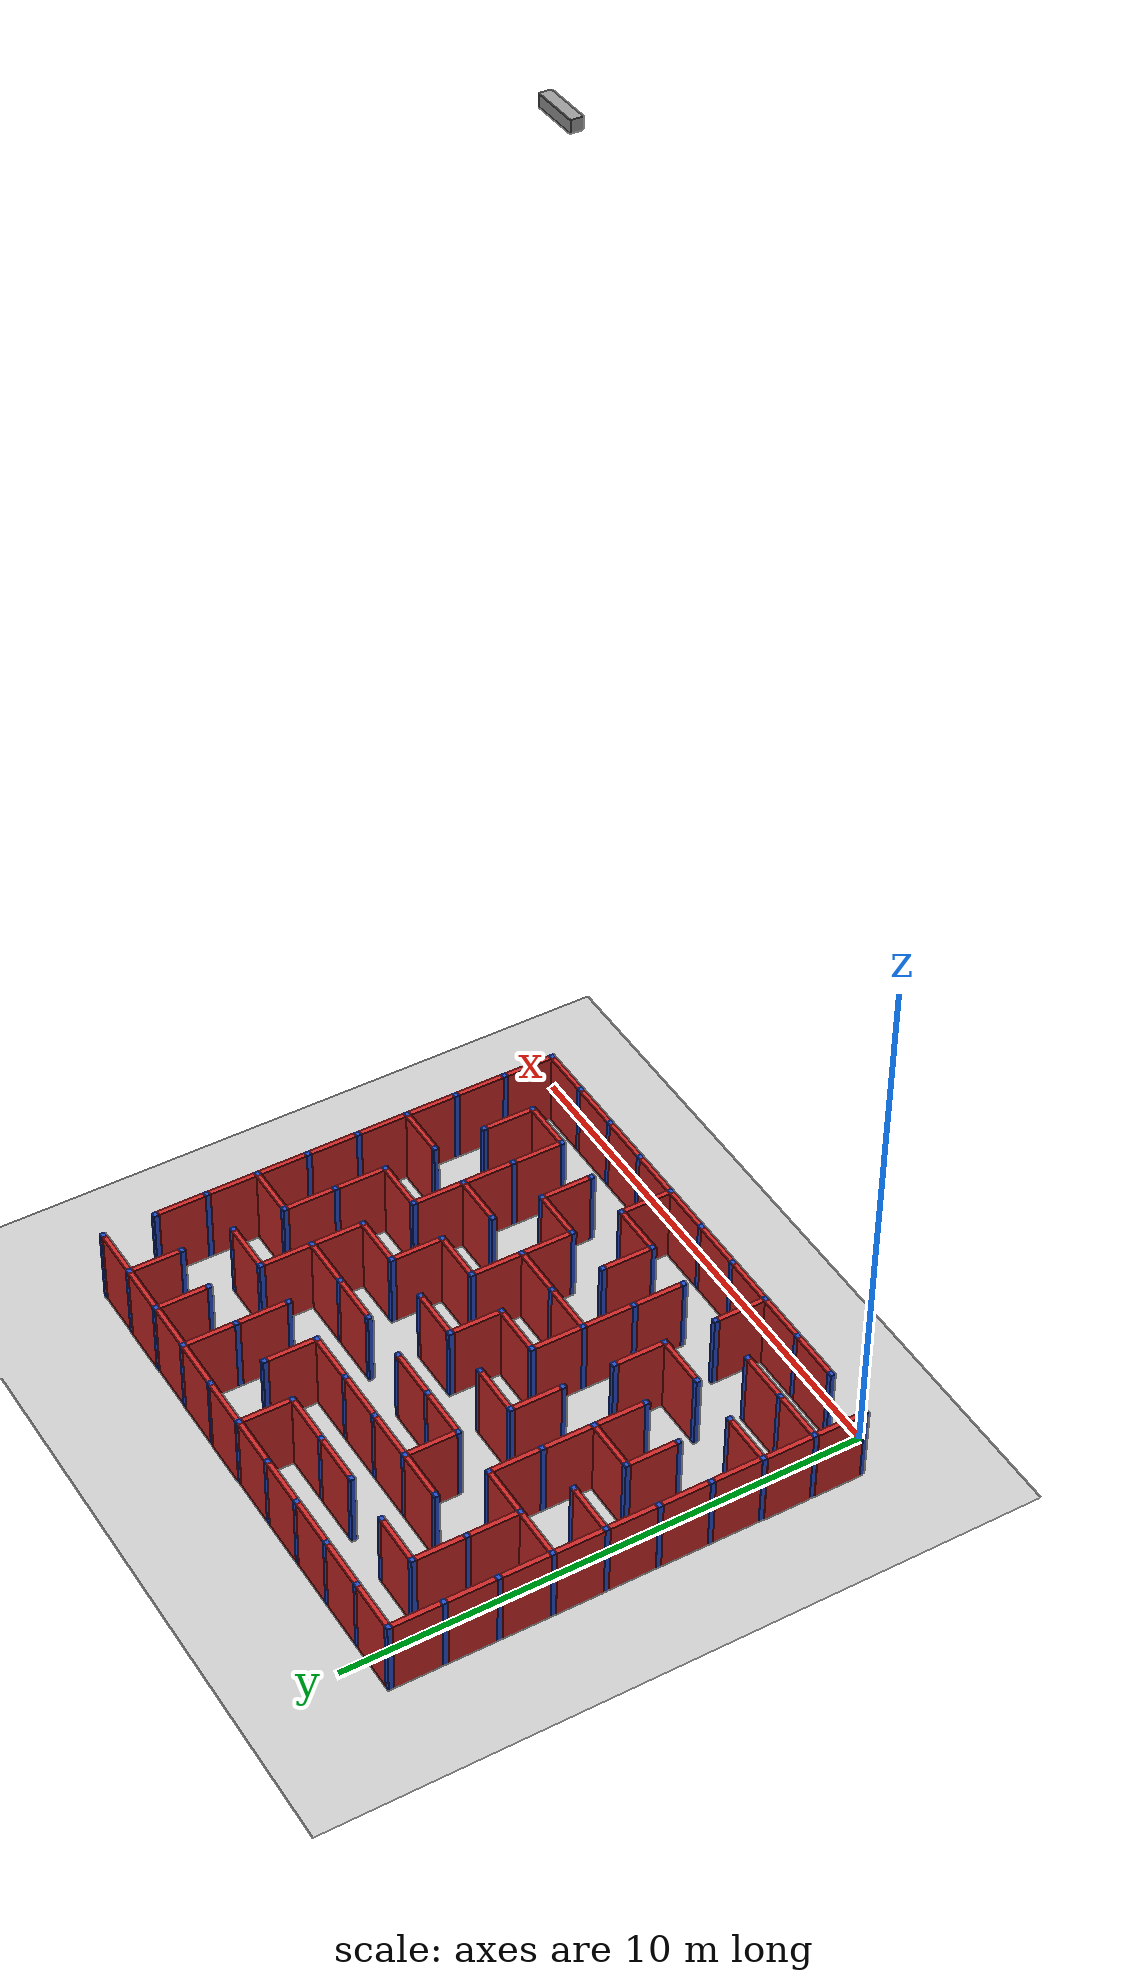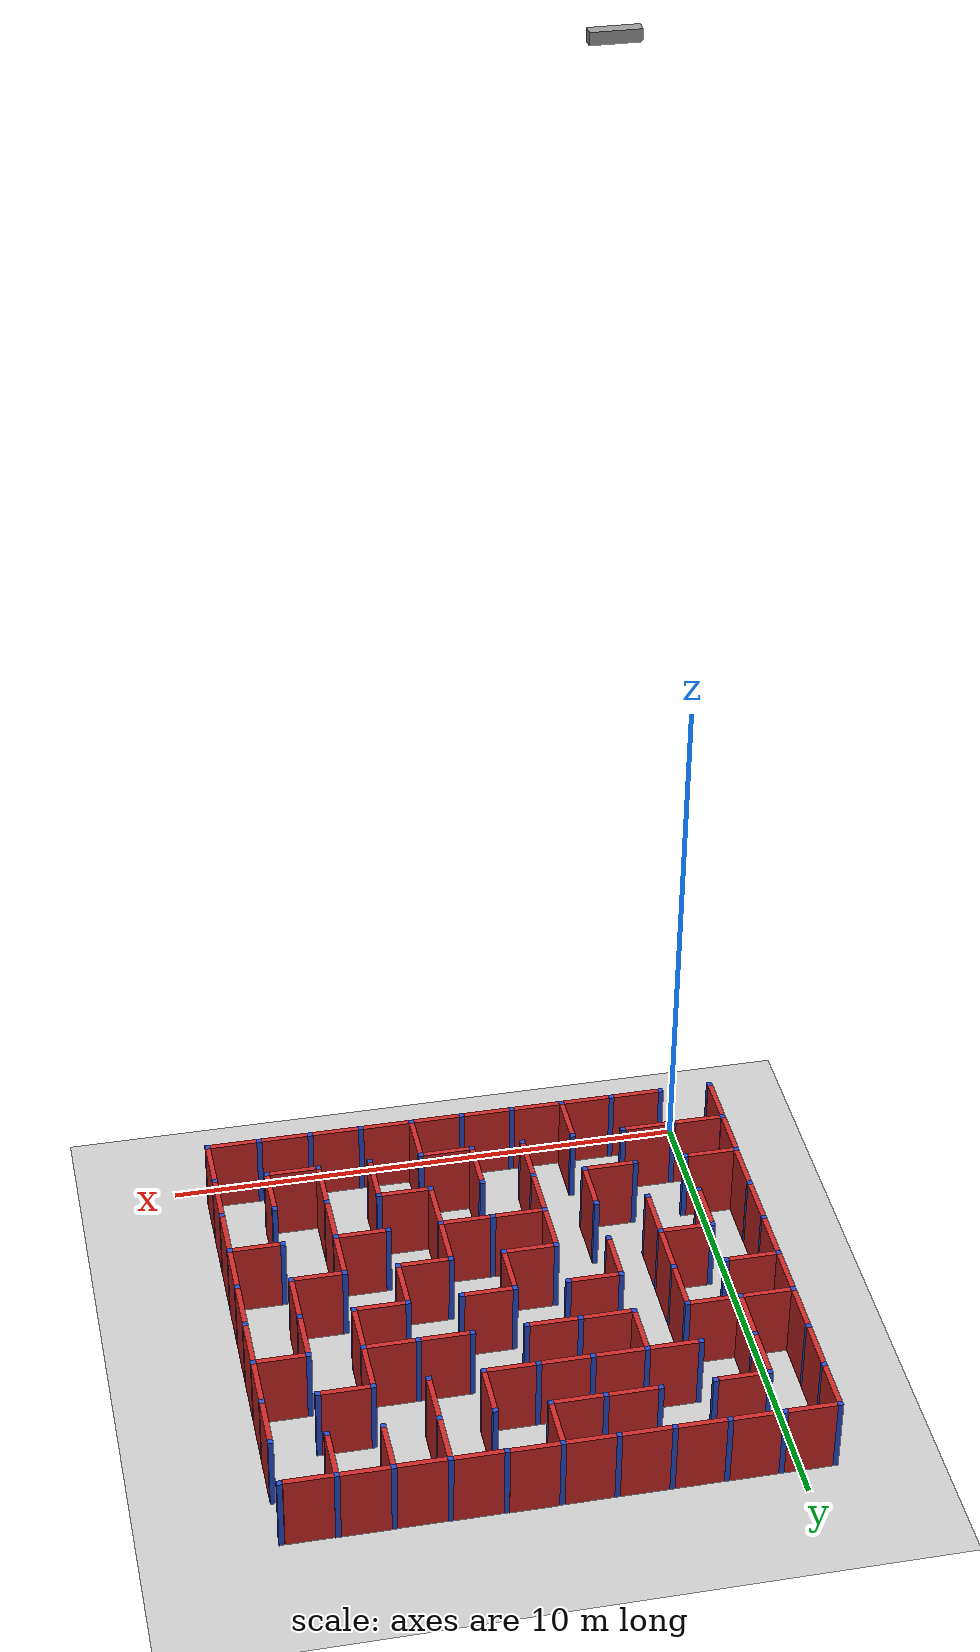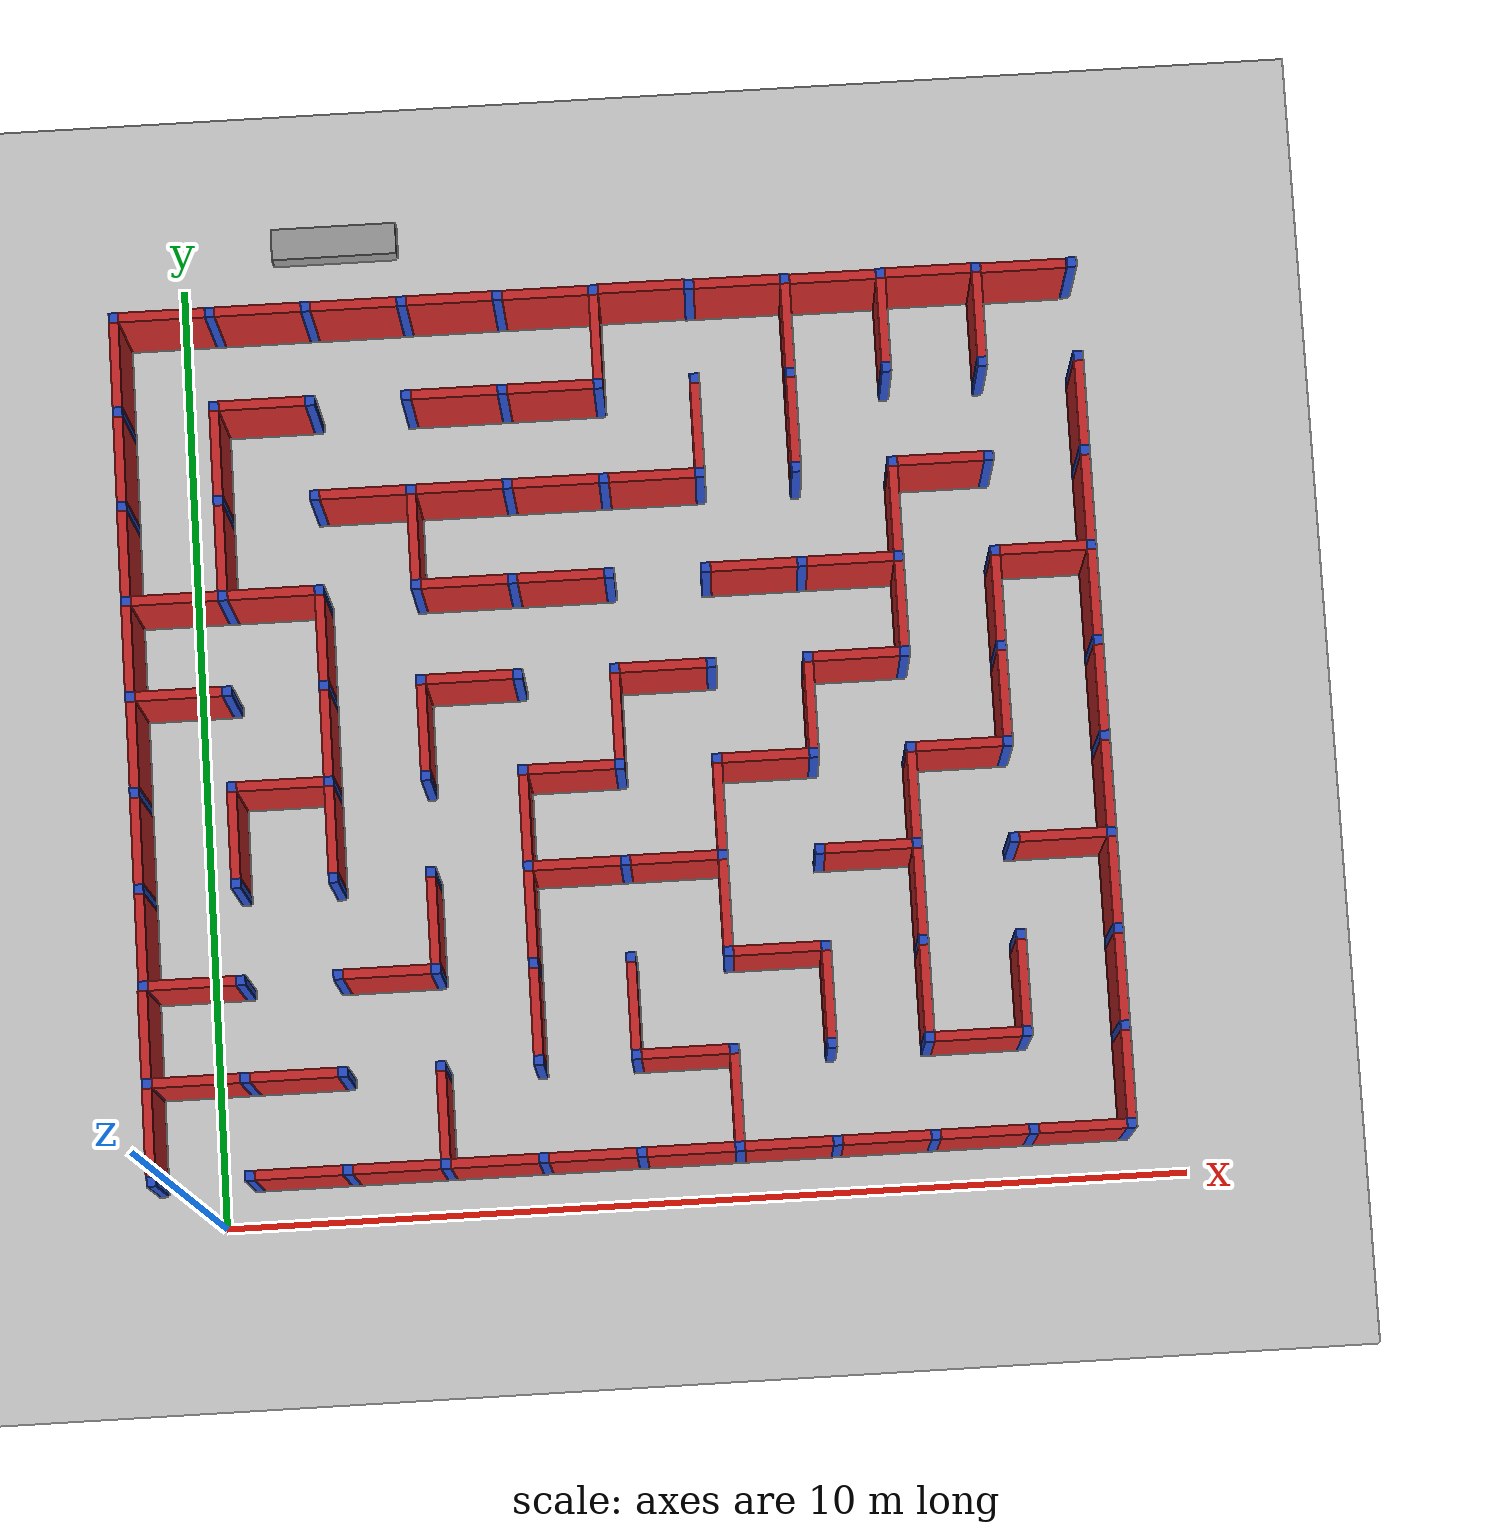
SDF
<sdf version="1.7">
 <world name="default">
  <light name="sun" type="directional">
   <pose>0 0 10 0 -0 0</pose>
   <diffuse>0.8 0.8 0.8 1</diffuse>
   <specular>0.2 0.2 0.2 1</specular>
   <attenuation>
    <range>1000</range>
    <constant>0.9</constant>
    <linear>0.01</linear>
    <quadratic>0.001</quadratic>
   </attenuation>
   <direction>-0.5 0.1 -0.9</direction>
   <spot><inner_angle>0</inner_angle><outer_angle>0</outer_angle><falloff>0</falloff></spot>
  </light>
  <model name="ground_plane">
   <static>1</static>
   <link name="link">
    <collision name="collision">
     <geometry><plane><normal>0 0 1</normal><size>100 100</size></plane></geometry>
     <surface><friction><ode><mu>100</mu><mu2>50</mu2></ode></friction></surface>
    </collision>
    <visual name="visual">
     <cast_shadows>0</cast_shadows>
     <geometry><plane><normal>0 0 1</normal><size>100 100</size></plane></geometry>
     <material>
      <script><uri>file://media/materials/scripts/gazebo.material</uri><name>Gazebo/Grey</name></script>
     </material>
    </visual>
   </link>
  </model>
  <gravity>0 0 -9.8</gravity>
  <magnetic_field>6e-06 2.3e-05 -4.2e-05</magnetic_field>
  <atmosphere type="adiabatic"/>
  <physics type="ode">
   <max_step_size>0.001</max_step_size>
   <real_time_factor>1</real_time_factor>
   <real_time_update_rate>1000</real_time_update_rate>
  </physics>
  <scene><ambient>0.4 0.4 0.4 1</ambient><background>0.7 0.7 0.7 1</background><shadows>1</shadows></scene>
  <spherical_coordinates>
   <surface_model>EARTH_WGS84</surface_model>
   <latitude_deg>0</latitude_deg>
   <longitude_deg>0</longitude_deg>
   <elevation>0</elevation>
   <heading_deg>0</heading_deg>
  </spherical_coordinates>
  <model name="deneme">
   <link name="Joint_10_-10">
    <pose>10 -10 0 0 -0 0</pose>
    <visual name="Wall_2_Visual">
     <pose>0 0 0.75 0 -0 0</pose>
     <geometry><box><size>0.1 0.1 1.5</size></box></geometry>
     <material>
      <script><uri>file://media/materials/scripts/gazebo.material</uri><name>Gazebo/Blue</name></script>
      <ambient>0.996078 0.47451 0.0196078 1</ambient>
      <shader type="pixel"/>
     </material>
     <meta><layer>0</layer></meta>
    </visual>
    <collision name="Wall_2_Collision">
     <pose>0 0 0.75 0 -0 0</pose>
     <geometry><box><size>0.1 0.1 1.5</size></box></geometry>
     <surface>
      <friction>
       <ode><mu>1</mu><mu2>1</mu2><fdir1>0 0 0</fdir1><slip1>0</slip1><slip2>0</slip2></ode>
       <torsional>
        <coefficient>1</coefficient>
        <patch_radius>0</patch_radius>
        <surface_radius>0</surface_radius>
        <use_patch_radius>1</use_patch_radius>
        <ode><slip>0</slip></ode>
       </torsional>
      </friction>
      <bounce><restitution_coefficient>0</restitution_coefficient><threshold>1e+06</threshold></bounce>
      <contact>
       <collide_without_contact>0</collide_without_contact>
       <collide_without_contact_bitmask>1</collide_without_contact_bitmask>
       <collide_bitmask>1</collide_bitmask>
       <ode>
        <soft_cfm>0</soft_cfm>
        <soft_erp>0.2</soft_erp>
        <kp>1e+13</kp>
        <kd>1</kd>
        <max_vel>0.01</max_vel>
        <min_depth>0</min_depth>
       </ode>
       <bullet>
        <split_impulse>1</split_impulse>
        <split_impulse_penetration_threshold>-0.01</split_impulse_penetration_threshold>
        <soft_cfm>0</soft_cfm>
        <soft_erp>0.2</soft_erp>
        <kp>1e+13</kp>
        <kd>1</kd>
       </bullet>
      </contact>
     </surface>
    </collision>
   </link>
   <link name="Joint_10_-11">
    <pose>10 -11 0 0 -0 0</pose>
    <visual name="Wall_2_Visual">
     <pose>0 0 0.75 0 -0 0</pose>
     <geometry><box><size>0.1 0.1 1.5</size></box></geometry>
     <material>
      <script><uri>file://media/materials/scripts/gazebo.material</uri><name>Gazebo/Blue</name></script>
      <ambient>0.996078 0.47451 0.0196078 1</ambient>
      <shader type="pixel"/>
     </material>
     <meta><layer>0</layer></meta>
    </visual>
    <collision name="Wall_2_Collision">
     <pose>0 0 0.75 0 -0 0</pose>
     <geometry><box><size>0.1 0.1 1.5</size></box></geometry>
     <surface>
      <friction>
       <ode><mu>1</mu><mu2>1</mu2><fdir1>0 0 0</fdir1><slip1>0</slip1><slip2>0</slip2></ode>
       <torsional>
        <coefficient>1</coefficient>
        <patch_radius>0</patch_radius>
        <surface_radius>0</surface_radius>
        <use_patch_radius>1</use_patch_radius>
        <ode><slip>0</slip></ode>
       </torsional>
      </friction>
      <bounce><restitution_coefficient>0</restitution_coefficient><threshold>1e+06</threshold></bounce>
      <contact>
       <collide_without_contact>0</collide_without_contact>
       <collide_without_contact_bitmask>1</collide_without_contact_bitmask>
       <collide_bitmask>1</collide_bitmask>
       <ode>
        <soft_cfm>0</soft_cfm>
        <soft_erp>0.2</soft_erp>
        <kp>1e+13</kp>
        <kd>1</kd>
        <max_vel>0.01</max_vel>
        <min_depth>0</min_depth>
       </ode>
       <bullet>
        <split_impulse>1</split_impulse>
        <split_impulse_penetration_threshold>-0.01</split_impulse_penetration_threshold>
        <soft_cfm>0</soft_cfm>
        <soft_erp>0.2</soft_erp>
        <kp>1e+13</kp>
        <kd>1</kd>
       </bullet>
      </contact>
     </surface>
    </collision>
   </link>
   <link name="Joint_10_-12">
    <pose>10 -12 0 0 -0 0</pose>
    <visual name="Wall_2_Visual">
     <pose>0 0 0.75 0 -0 0</pose>
     <geometry><box><size>0.1 0.1 1.5</size></box></geometry>
     <material>
      <script><uri>file://media/materials/scripts/gazebo.material</uri><name>Gazebo/Blue</name></script>
      <ambient>0.996078 0.47451 0.0196078 1</ambient>
      <shader type="pixel"/>
     </material>
     <meta><layer>0</layer></meta>
    </visual>
    <collision name="Wall_2_Collision">
     <pose>0 0 0.75 0 -0 0</pose>
     <geometry><box><size>0.1 0.1 1.5</size></box></geometry>
     <surface>
      <friction>
       <ode><mu>1</mu><mu2>1</mu2><fdir1>0 0 0</fdir1><slip1>0</slip1><slip2>0</slip2></ode>
       <torsional>
        <coefficient>1</coefficient>
        <patch_radius>0</patch_radius>
        <surface_radius>0</surface_radius>
        <use_patch_radius>1</use_patch_radius>
        <ode><slip>0</slip></ode>
       </torsional>
      </friction>
      <bounce><restitution_coefficient>0</restitution_coefficient><threshold>1e+06</threshold></bounce>
      <contact>
       <collide_without_contact>0</collide_without_contact>
       <collide_without_contact_bitmask>1</collide_without_contact_bitmask>
       <collide_bitmask>1</collide_bitmask>
       <ode>
        <soft_cfm>0</soft_cfm>
        <soft_erp>0.2</soft_erp>
        <kp>1e+13</kp>
        <kd>1</kd>
        <max_vel>0.01</max_vel>
        <min_depth>0</min_depth>
       </ode>
       <bullet>
        <split_impulse>1</split_impulse>
        <split_impulse_penetration_threshold>-0.01</split_impulse_penetration_threshold>
        <soft_cfm>0</soft_cfm>
        <soft_erp>0.2</soft_erp>
        <kp>1e+13</kp>
        <kd>1</kd>
       </bullet>
      </contact>
     </surface>
    </collision>
   </link>
   <link name="Joint_10_-13">
    <pose>10 -13 0 0 -0 0</pose>
    <visual name="Wall_2_Visual">
     <pose>0 0 0.75 0 -0 0</pose>
     <geometry><box><size>0.1 0.1 1.5</size></box></geometry>
     <material>
      <script><uri>file://media/materials/scripts/gazebo.material</uri><name>Gazebo/Blue</name></script>
      <ambient>0.996078 0.47451 0.0196078 1</ambient>
      <shader type="pixel"/>
     </material>
     <meta><layer>0</layer></meta>
    </visual>
    <collision name="Wall_2_Collision">
     <pose>0 0 0.75 0 -0 0</pose>
     <geometry><box><size>0.1 0.1 1.5</size></box></geometry>
     <surface>
      <friction>
       <ode><mu>1</mu><mu2>1</mu2><fdir1>0 0 0</fdir1><slip1>0</slip1><slip2>0</slip2></ode>
       <torsional>
        <coefficient>1</coefficient>
        <patch_radius>0</patch_radius>
        <surface_radius>0</surface_radius>
        <use_patch_radius>1</use_patch_radius>
        <ode><slip>0</slip></ode>
       </torsional>
      </friction>
      <bounce><restitution_coefficient>0</restitution_coefficient><threshold>1e+06</threshold></bounce>
      <contact>
       <collide_without_contact>0</collide_without_contact>
       <collide_without_contact_bitmask>1</collide_without_contact_bitmask>
       <collide_bitmask>1</collide_bitmask>
       <ode>
        <soft_cfm>0</soft_cfm>
        <soft_erp>0.2</soft_erp>
        <kp>1e+13</kp>
        <kd>1</kd>
        <max_vel>0.01</max_vel>
        <min_depth>0</min_depth>
       </ode>
       <bullet>
        <split_impulse>1</split_impulse>
        <split_impulse_penetration_threshold>-0.01</split_impulse_penetration_threshold>
        <soft_cfm>0</soft_cfm>
        <soft_erp>0.2</soft_erp>
        <kp>1e+13</kp>
        <kd>1</kd>
       </bullet>
      </contact>
     </surface>
    </collision>
   </link>
   <link name="Joint_10_-14">
    <pose>10 -14 0 0 -0 0</pose>
    <visual name="Wall_2_Visual">
     <pose>0 0 0.75 0 -0 0</pose>
     <geometry><box><size>0.1 0.1 1.5</size></box></geometry>
     <material>
      <script><uri>file://media/materials/scripts/gazebo.material</uri><name>Gazebo/Blue</name></script>
      <ambient>0.996078 0.47451 0.0196078 1</ambient>
      <shader type="pixel"/>
     </material>
     <meta><layer>0</layer></meta>
    </visual>
    <collision name="Wall_2_Collision">
     <pose>0 0 0.75 0 -0 0</pose>
     <geometry><box><size>0.1 0.1 1.5</size></box></geometry>
     <surface>
      <friction>
       <ode><mu>1</mu><mu2>1</mu2><fdir1>0 0 0</fdir1><slip1>0</slip1><slip2>0</slip2></ode>
       <torsional>
        <coefficient>1</coefficient>
        <patch_radius>0</patch_radius>
        <surface_radius>0</surface_radius>
        <use_patch_radius>1</use_patch_radius>
        <ode><slip>0</slip></ode>
       </torsional>
      </friction>
      <bounce><restitution_coefficient>0</restitution_coefficient><threshold>1e+06</threshold></bounce>
      <contact>
       <collide_without_contact>0</collide_without_contact>
       <collide_without_contact_bitmask>1</collide_without_contact_bitmask>
       <collide_bitmask>1</collide_bitmask>
       <ode>
        <soft_cfm>0</soft_cfm>
        <soft_erp>0.2</soft_erp>
        <kp>1e+13</kp>
        <kd>1</kd>
        <max_vel>0.01</max_vel>
        <min_depth>0</min_depth>
       </ode>
       <bullet>
        <split_impulse>1</split_impulse>
        <split_impulse_penetration_threshold>-0.01</split_impulse_penetration_threshold>
        <soft_cfm>0</soft_cfm>
        <soft_erp>0.2</soft_erp>
        <kp>1e+13</kp>
        <kd>1</kd>
       </bullet>
      </contact>
     </surface>
    </collision>
   </link>
   <link name="Joint_10_-15">
    <pose>10 -15 0 0 -0 0</pose>
    <visual name="Wall_2_Visual">
     <pose>0 0 0.75 0 -0 0</pose>
     <geometry><box><size>0.1 0.1 1.5</size></box></geometry>
     <material>
      <script><uri>file://media/materials/scripts/gazebo.material</uri><name>Gazebo/Blue</name></script>
      <ambient>0.996078 0.47451 0.0196078 1</ambient>
      <shader type="pixel"/>
     </material>
     <meta><layer>0</layer></meta>
    </visual>
    <collision name="Wall_2_Collision">
     <pose>0 0 0.75 0 -0 0</pose>
     <geometry><box><size>0.1 0.1 1.5</size></box></geometry>
     <surface>
      <friction>
       <ode><mu>1</mu><mu2>1</mu2><fdir1>0 0 0</fdir1><slip1>0</slip1><slip2>0</slip2></ode>
       <torsional>
        <coefficient>1</coefficient>
        <patch_radius>0</patch_radius>
        <surface_radius>0</surface_radius>
        <use_patch_radius>1</use_patch_radius>
        <ode><slip>0</slip></ode>
       </torsional>
      </friction>
      <bounce><restitution_coefficient>0</restitution_coefficient><threshold>1e+06</threshold></bounce>
      <contact>
       <collide_without_contact>0</collide_without_contact>
       <collide_without_contact_bitmask>1</collide_without_contact_bitmask>
       <collide_bitmask>1</collide_bitmask>
       <ode>
        <soft_cfm>0</soft_cfm>
        <soft_erp>0.2</soft_erp>
        <kp>1e+13</kp>
        <kd>1</kd>
        <max_vel>0.01</max_vel>
        <min_depth>0</min_depth>
       </ode>
       <bullet>
        <split_impulse>1</split_impulse>
        <split_impulse_penetration_threshold>-0.01</split_impulse_penetration_threshold>
        <soft_cfm>0</soft_cfm>
        <soft_erp>0.2</soft_erp>
        <kp>1e+13</kp>
        <kd>1</kd>
       </bullet>
      </contact>
     </surface>
    </collision>
   </link>
   <link name="Joint_10_-6">
    <pose>10 -6 0 0 -0 0</pose>
    <visual name="Wall_2_Visual">
     <pose>0 0 0.75 0 -0 0</pose>
     <geometry><box><size>0.1 0.1 1.5</size></box></geometry>
     <material>
      <script><uri>file://media/materials/scripts/gazebo.material</uri><name>Gazebo/Blue</name></script>
      <ambient>0.996078 0.47451 0.0196078 1</ambient>
      <shader type="pixel"/>
     </material>
     <meta><layer>0</layer></meta>
    </visual>
    <collision name="Wall_2_Collision">
     <pose>0 0 0.75 0 -0 0</pose>
     <geometry><box><size>0.1 0.1 1.5</size></box></geometry>
     <surface>
      <friction>
       <ode><mu>1</mu><mu2>1</mu2><fdir1>0 0 0</fdir1><slip1>0</slip1><slip2>0</slip2></ode>
       <torsional>
        <coefficient>1</coefficient>
        <patch_radius>0</patch_radius>
        <surface_radius>0</surface_radius>
        <use_patch_radius>1</use_patch_radius>
        <ode><slip>0</slip></ode>
       </torsional>
      </friction>
      <bounce><restitution_coefficient>0</restitution_coefficient><threshold>1e+06</threshold></bounce>
      <contact>
       <collide_without_contact>0</collide_without_contact>
       <collide_without_contact_bitmask>1</collide_without_contact_bitmask>
       <collide_bitmask>1</collide_bitmask>
       <ode>
        <soft_cfm>0</soft_cfm>
        <soft_erp>0.2</soft_erp>
        <kp>1e+13</kp>
        <kd>1</kd>
        <max_vel>0.01</max_vel>
        <min_depth>0</min_depth>
       </ode>
       <bullet>
        <split_impulse>1</split_impulse>
        <split_impulse_penetration_threshold>-0.01</split_impulse_penetration_threshold>
        <soft_cfm>0</soft_cfm>
        <soft_erp>0.2</soft_erp>
        <kp>1e+13</kp>
        <kd>1</kd>
       </bullet>
      </contact>
     </surface>
    </collision>
   </link>
   <link name="Joint_10_-7">
    <pose>10 -7 0 0 -0 0</pose>
    <visual name="Wall_2_Visual">
     <pose>0 0 0.75 0 -0 0</pose>
     <geometry><box><size>0.1 0.1 1.5</size></box></geometry>
     <material>
      <script><uri>file://media/materials/scripts/gazebo.material</uri><name>Gazebo/Blue</name></script>
      <ambient>0.996078 0.47451 0.0196078 1</ambient>
      <shader type="pixel"/>
     </material>
     <meta><layer>0</layer></meta>
    </visual>
    <collision name="Wall_2_Collision">
     <pose>0 0 0.75 0 -0 0</pose>
     <geometry><box><size>0.1 0.1 1.5</size></box></geometry>
     <surface>
      <friction>
       <ode><mu>1</mu><mu2>1</mu2><fdir1>0 0 0</fdir1><slip1>0</slip1><slip2>0</slip2></ode>
       <torsional>
        <coefficient>1</coefficient>
        <patch_radius>0</patch_radius>
        <surface_radius>0</surface_radius>
        <use_patch_radius>1</use_patch_radius>
        <ode><slip>0</slip></ode>
       </torsional>
      </friction>
      <bounce><restitution_coefficient>0</restitution_coefficient><threshold>1e+06</threshold></bounce>
      <contact>
       <collide_without_contact>0</collide_without_contact>
       <collide_without_contact_bitmask>1</collide_without_contact_bitmask>
       <collide_bitmask>1</collide_bitmask>
       <ode>
        <soft_cfm>0</soft_cfm>
        <soft_erp>0.2</soft_erp>
        <kp>1e+13</kp>
        <kd>1</kd>
        <max_vel>0.01</max_vel>
        <min_depth>0</min_depth>
       </ode>
       <bullet>
        <split_impulse>1</split_impulse>
        <split_impulse_penetration_threshold>-0.01</split_impulse_penetration_threshold>
        <soft_cfm>0</soft_cfm>
        <soft_erp>0.2</soft_erp>
        <kp>1e+13</kp>
        <kd>1</kd>
       </bullet>
      </contact>
     </surface>
    </collision>
   </link>
   <link name="Joint_10_-8">
    <pose>10 -8 0 0 -0 0</pose>
    <visual name="Wall_2_Visual">
     <pose>0 0 0.75 0 -0 0</pose>
     <geometry><box><size>0.1 0.1 1.5</size></box></geometry>
     <material>
      <script><uri>file://media/materials/scripts/gazebo.material</uri><name>Gazebo/Blue</name></script>
      <ambient>0.996078 0.47451 0.0196078 1</ambient>
      <shader type="pixel"/>
     </material>
     <meta><layer>0</layer></meta>
    </visual>
    <collision name="Wall_2_Collision">
     <pose>0 0 0.75 0 -0 0</pose>
     <geometry><box><size>0.1 0.1 1.5</size></box></geometry>
     <surface>
      <friction>
       <ode><mu>1</mu><mu2>1</mu2><fdir1>0 0 0</fdir1><slip1>0</slip1><slip2>0</slip2></ode>
       <torsional>
        <coefficient>1</coefficient>
        <patch_radius>0</patch_radius>
        <surface_radius>0</surface_radius>
        <use_patch_radius>1</use_patch_radius>
        <ode><slip>0</slip></ode>
       </torsional>
      </friction>
      <bounce><restitution_coefficient>0</restitution_coefficient><threshold>1e+06</threshold></bounce>
      <contact>
       <collide_without_contact>0</collide_without_contact>
       <collide_without_contact_bitmask>1</collide_without_contact_bitmask>
       <collide_bitmask>1</collide_bitmask>
       <ode>
        <soft_cfm>0</soft_cfm>
        <soft_erp>0.2</soft_erp>
        <kp>1e+13</kp>
        <kd>1</kd>
        <max_vel>0.01</max_vel>
        <min_depth>0</min_depth>
       </ode>
       <bullet>
        <split_impulse>1</split_impulse>
        <split_impulse_penetration_threshold>-0.01</split_impulse_penetration_threshold>
        <soft_cfm>0</soft_cfm>
        <soft_erp>0.2</soft_erp>
        <kp>1e+13</kp>
        <kd>1</kd>
       </bullet>
      </contact>
     </surface>
    </collision>
   </link>
   <link name="Joint_10_-9">
    <pose>10 -9 0 0 -0 0</pose>
    <visual name="Wall_2_Visual">
     <pose>0 0 0.75 0 -0 0</pose>
     <geometry><box><size>0.1 0.1 1.5</size></box></geometry>
     <material>
      <script><uri>file://media/materials/scripts/gazebo.material</uri><name>Gazebo/Blue</name></script>
      <ambient>0.996078 0.47451 0.0196078 1</ambient>
      <shader type="pixel"/>
     </material>
     <meta><layer>0</layer></meta>
    </visual>
    <collision name="Wall_2_Collision">
     <pose>0 0 0.75 0 -0 0</pose>
     <geometry><box><size>0.1 0.1 1.5</size></box></geometry>
     <surface>
      <friction>
       <ode><mu>1</mu><mu2>1</mu2><fdir1>0 0 0</fdir1><slip1>0</slip1><slip2>0</slip2></ode>
       <torsional>
        <coefficient>1</coefficient>
        <patch_radius>0</patch_radius>
        <surface_radius>0</surface_radius>
        <use_patch_radius>1</use_patch_radius>
        <ode><slip>0</slip></ode>
       </torsional>
      </friction>
      <bounce><restitution_coefficient>0</restitution_coefficient><threshold>1e+06</threshold></bounce>
      <contact>
       <collide_without_contact>0</collide_without_contact>
       <collide_without_contact_bitmask>1</collide_without_contact_bitmask>
       <collide_bitmask>1</collide_bitmask>
       <ode>
        <soft_cfm>0</soft_cfm>
        <soft_erp>0.2</soft_erp>
        <kp>1e+13</kp>
        <kd>1</kd>
        <max_vel>0.01</max_vel>
        <min_depth>0</min_depth>
       </ode>
       <bullet>
        <split_impulse>1</split_impulse>
        <split_impulse_penetration_threshold>-0.01</split_impulse_penetration_threshold>
        <soft_cfm>0</soft_cfm>
        <soft_erp>0.2</soft_erp>
        <kp>1e+13</kp>
        <kd>1</kd>
       </bullet>
      </contact>
     </surface>
    </collision>
   </link>
   <link name="Joint_11_-10">
    <pose>11 -10 0 0 -0 0</pose>
    <visual name="Wall_2_Visual">
     <pose>0 0 0.75 0 -0 0</pose>
     <geometry><box><size>0.1 0.1 1.5</size></box></geometry>
     <material>
      <script><uri>file://media/materials/scripts/gazebo.material</uri><name>Gazebo/Blue</name></script>
      <ambient>0.996078 0.47451 0.0196078 1</ambient>
      <shader type="pixel"/>
     </material>
     <meta><layer>0</layer></meta>
    </visual>
    <collision name="Wall_2_Collision">
     <pose>0 0 0.75 0 -0 0</pose>
     <geometry><box><size>0.1 0.1 1.5</size></box></geometry>
     <surface>
      <friction>
       <ode><mu>1</mu><mu2>1</mu2><fdir1>0 0 0</fdir1><slip1>0</slip1><slip2>0</slip2></ode>
       <torsional>
        <coefficient>1</coefficient>
        <patch_radius>0</patch_radius>
        <surface_radius>0</surface_radius>
        <use_patch_radius>1</use_patch_radius>
        <ode><slip>0</slip></ode>
       </torsional>
      </friction>
      <bounce><restitution_coefficient>0</restitution_coefficient><threshold>1e+06</threshold></bounce>
      <contact>
       <collide_without_contact>0</collide_without_contact>
       <collide_without_contact_bitmask>1</collide_without_contact_bitmask>
       <collide_bitmask>1</collide_bitmask>
       <ode>
        <soft_cfm>0</soft_cfm>
        <soft_erp>0.2</soft_erp>
        <kp>1e+13</kp>
        <kd>1</kd>
        <max_vel>0.01</max_vel>
        <min_depth>0</min_depth>
       </ode>
       <bullet>
        <split_impulse>1</split_impulse>
        <split_impulse_penetration_threshold>-0.01</split_impulse_penetration_threshold>
        <soft_cfm>0</soft_cfm>
        <soft_erp>0.2</soft_erp>
        <kp>1e+13</kp>
        <kd>1</kd>
       </bullet>
      </contact>
     </surface>
    </collision>
   </link>
   <link name="Joint_11_-11">
    <pose>11 -11 0 0 -0 0</pose>
    <visual name="Wall_2_Visual">
     <pose>0 0 0.75 0 -0 0</pose>
     <geometry><box><size>0.1 0.1 1.5</size></box></geometry>
     <material>
      <script><uri>file://media/materials/scripts/gazebo.material</uri><name>Gazebo/Blue</name></script>
      <ambient>0.996078 0.47451 0.0196078 1</ambient>
      <shader type="pixel"/>
     </material>
     <meta><layer>0</layer></meta>
    </visual>
    <collision name="Wall_2_Collision">
     <pose>0 0 0.75 0 -0 0</pose>
     <geometry><box><size>0.1 0.1 1.5</size></box></geometry>
     <surface>
      <friction>
       <ode><mu>1</mu><mu2>1</mu2><fdir1>0 0 0</fdir1><slip1>0</slip1><slip2>0</slip2></ode>
       <torsional>
        <coefficient>1</coefficient>
        <patch_radius>0</patch_radius>
        <surface_radius>0</surface_radius>
        <use_patch_radius>1</use_patch_radius>
        <ode><slip>0</slip></ode>
       </torsional>
      </friction>
      <bounce><restitution_coefficient>0</restitution_coefficient><threshold>1e+06</threshold></bounce>
      <contact>
       <collide_without_contact>0</collide_without_contact>
       <collide_without_contact_bitmask>1</collide_without_contact_bitmask>
       <collide_bitmask>1</collide_bitmask>
       <ode>
        <soft_cfm>0</soft_cfm>
        <soft_erp>0.2</soft_erp>
        <kp>1e+13</kp>
        <kd>1</kd>
        <max_vel>0.01</max_vel>
        <min_depth>0</min_depth>
       </ode>
       <bullet>
        <split_impulse>1</split_impulse>
        <split_impulse_penetration_threshold>-0.01</split_impulse_penetration_threshold>
        <soft_cfm>0</soft_cfm>
        <soft_erp>0.2</soft_erp>
        <kp>1e+13</kp>
        <kd>1</kd>
       </bullet>
      </contact>
     </surface>
    </collision>
   </link>
   <link name="Joint_11_-12">
    <pose>11 -12 0 0 -0 0</pose>
    <visual name="Wall_2_Visual">
     <pose>0 0 0.75 0 -0 0</pose>
     <geometry><box><size>0.1 0.1 1.5</size></box></geometry>
     <material>
      <script><uri>file://media/materials/scripts/gazebo.material</uri><name>Gazebo/Blue</name></script>
      <ambient>0.996078 0.47451 0.0196078 1</ambient>
      <shader type="pixel"/>
     </material>
     <meta><layer>0</layer></meta>
    </visual>
    <collision name="Wall_2_Collision">
     <pose>0 0 0.75 0 -0 0</pose>
     <geometry><box><size>0.1 0.1 1.5</size></box></geometry>
     <surface>
      <friction>
       <ode><mu>1</mu><mu2>1</mu2><fdir1>0 0 0</fdir1><slip1>0</slip1><slip2>0</slip2></ode>
       <torsional>
        <coefficient>1</coefficient>
        <patch_radius>0</patch_radius>
        <surface_radius>0</surface_radius>
        <use_patch_radius>1</use_patch_radius>
        <ode><slip>0</slip></ode>
       </torsional>
      </friction>
      <bounce><restitution_coefficient>0</restitution_coefficient><threshold>1e+06</threshold></bounce>
      <contact>
       <collide_without_contact>0</collide_without_contact>
       <collide_without_contact_bitmask>1</collide_without_contact_bitmask>
       <collide_bitmask>1</collide_bitmask>
       <ode>
        <soft_cfm>0</soft_cfm>
        <soft_erp>0.2</soft_erp>
        <kp>1e+13</kp>
        <kd>1</kd>
        <max_vel>0.01</max_vel>
        <min_depth>0</min_depth>
       </ode>
       <bullet>
        <split_impulse>1</split_impulse>
        <split_impulse_penetration_threshold>-0.01</split_impulse_penetration_threshold>
        <soft_cfm>0</soft_cfm>
        <soft_erp>0.2</soft_erp>
        <kp>1e+13</kp>
        <kd>1</kd>
       </bullet>
      </contact>
     </surface>
    </collision>
   </link>
   <link name="Joint_11_-13">
    <pose>11 -13 0 0 -0 0</pose>
    <visual name="Wall_2_Visual">
     <pose>0 0 0.75 0 -0 0</pose>
     <geometry><box><size>0.1 0.1 1.5</size></box></geometry>
     <material>
      <script><uri>file://media/materials/scripts/gazebo.material</uri><name>Gazebo/Blue</name></script>
      <ambient>0.996078 0.47451 0.0196078 1</ambient>
      <shader type="pixel"/>
     </material>
     <meta><layer>0</layer></meta>
    </visual>
    <collision name="Wall_2_Collision">
     <pose>0 0 0.75 0 -0 0</pose>
     <geometry><box><size>0.1 0.1 1.5</size></box></geometry>
     <surface>
      <friction>
       <ode><mu>1</mu><mu2>1</mu2><fdir1>0 0 0</fdir1><slip1>0</slip1><slip2>0</slip2></ode>
       <torsional>
        <coefficient>1</coefficient>
        <patch_radius>0</patch_radius>
        <surface_radius>0</surface_radius>
        <use_patch_radius>1</use_patch_radius>
        <ode><slip>0</slip></ode>
       </torsional>
      </friction>
      <bounce><restitution_coefficient>0</restitution_coefficient><threshold>1e+06</threshold></bounce>
      <contact>
       <collide_without_contact>0</collide_without_contact>
       <collide_without_contact_bitmask>1</collide_without_contact_bitmask>
       <collide_bitmask>1</collide_bitmask>
       <ode>
        <soft_cfm>0</soft_cfm>
        <soft_erp>0.2</soft_erp>
        <kp>1e+13</kp>
        <kd>1</kd>
        <max_vel>0.01</max_vel>
        <min_depth>0</min_depth>
       </ode>
       <bullet>
        <split_impulse>1</split_impulse>
        <split_impulse_penetration_threshold>-0.01</split_impulse_penetration_threshold>
        <soft_cfm>0</soft_cfm>
        <soft_erp>0.2</soft_erp>
        <kp>1e+13</kp>
        <kd>1</kd>
       </bullet>
      </contact>
     </surface>
    </collision>
   </link>
   <link name="Joint_11_-14">
    <pose>11 -14 0 0 -0 0</pose>
    <visual name="Wall_2_Visual">
     <pose>0 0 0.75 0 -0 0</pose>
     <geometry><box><size>0.1 0.1 1.5</size></box></geometry>
     <material>
      <script><uri>file://media/materials/scripts/gazebo.material</uri><name>Gazebo/Blue</name></script>
      <ambient>0.996078 0.47451 0.0196078 1</ambient>
      <shader type="pixel"/>
     </material>
     <meta><layer>0</layer></meta>
    </visual>
    <collision name="Wall_2_Collision">
     <pose>0 0 0.75 0 -0 0</pose>
     <geometry><box><size>0.1 0.1 1.5</size></box></geometry>
     <surface>
      <friction>
       <ode><mu>1</mu><mu2>1</mu2><fdir1>0 0 0</fdir1><slip1>0</slip1><slip2>0</slip2></ode>
       <torsional>
        <coefficient>1</coefficient>
        <patch_radius>0</patch_radius>
        <surface_radius>0</surface_radius>
        <use_patch_radius>1</use_patch_radius>
        <ode><slip>0</slip></ode>
       </torsional>
      </friction>
      <bounce><restitution_coefficient>0</restitution_coefficient><threshold>1e+06</threshold></bounce>
      <contact>
       <collide_without_contact>0</collide_without_contact>
       <collide_without_contact_bitmask>1</collide_without_contact_bitmask>
       <collide_bitmask>1</collide_bitmask>
       <ode>
        <soft_cfm>0</soft_cfm>
        <soft_erp>0.2</soft_erp>
        <kp>1e+13</kp>
        <kd>1</kd>
        <max_vel>0.01</max_vel>
        <min_depth>0</min_depth>
       </ode>
       <bullet>
        <split_impulse>1</split_impulse>
        <split_impulse_penetration_threshold>-0.01</split_impulse_penetration_threshold>
        <soft_cfm>0</soft_cfm>
        <soft_erp>0.2</soft_erp>
        <kp>1e+13</kp>
        <kd>1</kd>
       </bullet>
      </contact>
     </surface>
    </collision>
   </link>
   <link name="Joint_11_-15">
    <pose>11 -15 0 0 -0 0</pose>
    <visual name="Wall_2_Visual">
     <pose>0 0 0.75 0 -0 0</pose>
     <geometry><box><size>0.1 0.1 1.5</size></box></geometry>
     <material>
      <script><uri>file://media/materials/scripts/gazebo.material</uri><name>Gazebo/Blue</name></script>
      <ambient>0.996078 0.47451 0.0196078 1</ambient>
      <shader type="pixel"/>
     </material>
     <meta><layer>0</layer></meta>
    </visual>
    <collision name="Wall_2_Collision">
     <pose>0 0 0.75 0 -0 0</pose>
     <geometry><box><size>0.1 0.1 1.5</size></box></geometry>
     <surface>
      <friction>
       <ode><mu>1</mu><mu2>1</mu2><fdir1>0 0 0</fdir1><slip1>0</slip1><slip2>0</slip2></ode>
       <torsional>
        <coefficient>1</coefficient>
        <patch_radius>0</patch_radius>
        <surface_radius>0</surface_radius>
        <use_patch_radius>1</use_patch_radius>
        <ode><slip>0</slip></ode>
       </torsional>
      </friction>
      <bounce><restitution_coefficient>0</restitution_coefficient><threshold>1e+06</threshold></bounce>
      <contact>
       <collide_without_contact>0</collide_without_contact>
       <collide_without_contact_bitmask>1</collide_without_contact_bitmask>
       <collide_bitmask>1</collide_bitmask>
       <ode>
        <soft_cfm>0</soft_cfm>
        <soft_erp>0.2</soft_erp>
        <kp>1e+13</kp>
        <kd>1</kd>
        <max_vel>0.01</max_vel>
        <min_depth>0</min_depth>
       </ode>
       <bullet>
        <split_impulse>1</split_impulse>
        <split_impulse_penetration_threshold>-0.01</split_impulse_penetration_threshold>
        <soft_cfm>0</soft_cfm>
        <soft_erp>0.2</soft_erp>
        <kp>1e+13</kp>
        <kd>1</kd>
       </bullet>
      </contact>
     </surface>
    </collision>
   </link>
   <link name="Joint_11_-6">
    <pose>11 -6 0 0 -0 0</pose>
    <visual name="Wall_2_Visual">
     <pose>0 0 0.75 0 -0 0</pose>
     <geometry><box><size>0.1 0.1 1.5</size></box></geometry>
     <material>
      <script><uri>file://media/materials/scripts/gazebo.material</uri><name>Gazebo/Blue</name></script>
      <ambient>0.996078 0.47451 0.0196078 1</ambient>
      <shader type="pixel"/>
     </material>
     <meta><layer>0</layer></meta>
    </visual>
    <collision name="Wall_2_Collision">
     <pose>0 0 0.75 0 -0 0</pose>
     <geometry><box><size>0.1 0.1 1.5</size></box></geometry>
     <surface>
      <friction>
       <ode><mu>1</mu><mu2>1</mu2><fdir1>0 0 0</fdir1><slip1>0</slip1><slip2>0</slip2></ode>
       <torsional>
        <coefficient>1</coefficient>
        <patch_radius>0</patch_radius>
        <surface_radius>0</surface_radius>
        <use_patch_radius>1</use_patch_radius>
        <ode><slip>0</slip></ode>
       </torsional>
      </friction>
      <bounce><restitution_coefficient>0</restitution_coefficient><threshold>1e+06</threshold></bounce>
      <contact>
       <collide_without_contact>0</collide_without_contact>
       <collide_without_contact_bitmask>1</collide_without_contact_bitmask>
       <collide_bitmask>1</collide_bitmask>
       <ode>
        <soft_cfm>0</soft_cfm>
        <soft_erp>0.2</soft_erp>
        <kp>1e+13</kp>
        <kd>1</kd>
        <max_vel>0.01</max_vel>
        <min_depth>0</min_depth>
       </ode>
       <bullet>
        <split_impulse>1</split_impulse>
        <split_impulse_penetration_threshold>-0.01</split_impulse_penetration_threshold>
        <soft_cfm>0</soft_cfm>
        <soft_erp>0.2</soft_erp>
        <kp>1e+13</kp>
        <kd>1</kd>
       </bullet>
      </contact>
     </surface>
    </collision>
   </link>
   <link name="Joint_11_-7">
    <pose>11 -7 0 0 -0 0</pose>
    <visual name="Wall_2_Visual">
     <pose>0 0 0.75 0 -0 0</pose>
     <geometry><box><size>0.1 0.1 1.5</size></box></geometry>
     <material>
      <script><uri>file://media/materials/scripts/gazebo.material</uri><name>Gazebo/Blue</name></script>
      <ambient>0.996078 0.47451 0.0196078 1</ambient>
      <shader type="pixel"/>
     </material>
     <meta><layer>0</layer></meta>
    </visual>
    <collision name="Wall_2_Collision">
     <pose>0 0 0.75 0 -0 0</pose>
     <geometry><box><size>0.1 0.1 1.5</size></box></geometry>
     <surface>
      <friction>
       <ode><mu>1</mu><mu2>1</mu2><fdir1>0 0 0</fdir1><slip1>0</slip1><slip2>0</slip2></ode>
       <torsional>
        <coefficient>1</coefficient>
        <patch_radius>0</patch_radius>
        <surface_radius>0</surface_radius>
        <use_patch_radius>1</use_patch_radius>
        <ode><slip>0</slip></ode>
       </torsional>
      </friction>
      <bounce><restitution_coefficient>0</restitution_coefficient><threshold>1e+06</threshold></bounce>
      <contact>
       <collide_without_contact>0</collide_without_contact>
       <collide_without_contact_bitmask>1</collide_without_contact_bitmask>
       <collide_bitmask>1</collide_bitmask>
       <ode>
        <soft_cfm>0</soft_cfm>
        <soft_erp>0.2</soft_erp>
        <kp>1e+13</kp>
        <kd>1</kd>
        <max_vel>0.01</max_vel>
        <min_depth>0</min_depth>
       </ode>
       <bullet>
        <split_impulse>1</split_impulse>
        <split_impulse_penetration_threshold>-0.01</split_impulse_penetration_threshold>
        <soft_cfm>0</soft_cfm>
        <soft_erp>0.2</soft_erp>
        <kp>1e+13</kp>
        <kd>1</kd>
       </bullet>
      </contact>
     </surface>
    </collision>
   </link>
   <link name="Joint_11_-8">
    <pose>11 -8 0 0 -0 0</pose>
    <visual name="Wall_2_Visual">
     <pose>0 0 0.75 0 -0 0</pose>
     <geometry><box><size>0.1 0.1 1.5</size></box></geometry>
     <material>
      <script><uri>file://media/materials/scripts/gazebo.material</uri><name>Gazebo/Blue</name></script>
      <ambient>0.996078 0.47451 0.0196078 1</ambient>
      <shader type="pixel"/>
     </material>
     <meta><layer>0</layer></meta>
    </visual>
    <collision name="Wall_2_Collision">
     <pose>0 0 0.75 0 -0 0</pose>
     <geometry><box><size>0.1 0.1 1.5</size></box></geometry>
     <surface>
      <friction>
       <ode><mu>1</mu><mu2>1</mu2><fdir1>0 0 0</fdir1><slip1>0</slip1><slip2>0</slip2></ode>
       <torsional>
        <coefficient>1</coefficient>
        <patch_radius>0</patch_radius>
        <surface_radius>0</surface_radius>
        <use_patch_radius>1</use_patch_radius>
        <ode><slip>0</slip></ode>
       </torsional>
      </friction>
      <bounce><restitution_coefficient>0</restitution_coefficient><threshold>1e+06</threshold></bounce>
      <contact>
       <collide_without_contact>0</collide_without_contact>
       <collide_without_contact_bitmask>1</collide_without_contact_bitmask>
       <collide_bitmask>1</collide_bitmask>
       <ode>
        <soft_cfm>0</soft_cfm>
        <soft_erp>0.2</soft_erp>
        <kp>1e+13</kp>
        <kd>1</kd>
        <max_vel>0.01</max_vel>
        <min_depth>0</min_depth>
       </ode>
       <bullet>
        <split_impulse>1</split_impulse>
        <split_impulse_penetration_threshold>-0.01</split_impulse_penetration_threshold>
        <soft_cfm>0</soft_cfm>
        <soft_erp>0.2</soft_erp>
        <kp>1e+13</kp>
        <kd>1</kd>
       </bullet>
      </contact>
     </surface>
    </collision>
   </link>
   <link name="Joint_11_-9">
    <pose>11 -9 0 0 -0 0</pose>
    <visual name="Wall_2_Visual">
     <pose>0 0 0.75 0 -0 0</pose>
     <geometry><box><size>0.1 0.1 1.5</size></box></geometry>
     <material>
      <script><uri>file://media/materials/scripts/gazebo.material</uri><name>Gazebo/Blue</name></script>
      <ambient>0.996078 0.47451 0.0196078 1</ambient>
      <shader type="pixel"/>
     </material>
     <meta><layer>0</layer></meta>
    </visual>
    <collision name="Wall_2_Collision">
     <pose>0 0 0.75 0 -0 0</pose>
     <geometry><box><size>0.1 0.1 1.5</size></box></geometry>
     <surface>
      <friction>
       <ode><mu>1</mu><mu2>1</mu2><fdir1>0 0 0</fdir1><slip1>0</slip1><slip2>0</slip2></ode>
       <torsional>
        <coefficient>1</coefficient>
        <patch_radius>0</patch_radius>
        <surface_radius>0</surface_radius>
        <use_patch_radius>1</use_patch_radius>
        <ode><slip>0</slip></ode>
       </torsional>
      </friction>
      <bounce><restitution_coefficient>0</restitution_coefficient><threshold>1e+06</threshold></bounce>
      <contact>
       <collide_without_contact>0</collide_without_contact>
       <collide_without_contact_bitmask>1</collide_without_contact_bitmask>
       <collide_bitmask>1</collide_bitmask>
       <ode>
        <soft_cfm>0</soft_cfm>
        <soft_erp>0.2</soft_erp>
        <kp>1e+13</kp>
        <kd>1</kd>
        <max_vel>0.01</max_vel>
        <min_depth>0</min_depth>
       </ode>
       <bullet>
        <split_impulse>1</split_impulse>
        <split_impulse_penetration_threshold>-0.01</split_impulse_penetration_threshold>
        <soft_cfm>0</soft_cfm>
        <soft_erp>0.2</soft_erp>
        <kp>1e+13</kp>
        <kd>1</kd>
       </bullet>
      </contact>
     </surface>
    </collision>
   </link>
   <link name="Joint_12_-10">
    <pose>12 -10 0 0 -0 0</pose>
    <visual name="Wall_2_Visual">
     <pose>0 0 0.75 0 -0 0</pose>
     <geometry><box><size>0.1 0.1 1.5</size></box></geometry>
     <material>
      <script><uri>file://media/materials/scripts/gazebo.material</uri><name>Gazebo/Blue</name></script>
      <ambient>0.996078 0.47451 0.0196078 1</ambient>
      <shader type="pixel"/>
     </material>
     <meta><layer>0</layer></meta>
    </visual>
    <collision name="Wall_2_Collision">
     <pose>0 0 0.75 0 -0 0</pose>
     <geometry><box><size>0.1 0.1 1.5</size></box></geometry>
     <surface>
      <friction>
       <ode><mu>1</mu><mu2>1</mu2><fdir1>0 0 0</fdir1><slip1>0</slip1><slip2>0</slip2></ode>
       <torsional>
        <coefficient>1</coefficient>
        <patch_radius>0</patch_radius>
        <surface_radius>0</surface_radius>
        <use_patch_radius>1</use_patch_radius>
        <ode><slip>0</slip></ode>
       </torsional>
      </friction>
      <bounce><restitution_coefficient>0</restitution_coefficient><threshold>1e+06</threshold></bounce>
      <contact>
       <collide_without_contact>0</collide_without_contact>
       <collide_without_contact_bitmask>1</collide_without_contact_bitmask>
       <collide_bitmask>1</collide_bitmask>
       <ode>
        <soft_cfm>0</soft_cfm>
        <soft_erp>0.2</soft_erp>
        <kp>1e+13</kp>
        <kd>1</kd>
        <max_vel>0.01</max_vel>
        <min_depth>0</min_depth>
       </ode>
       <bullet>
        <split_impulse>1</split_impulse>
        <split_impulse_penetration_threshold>-0.01</split_impulse_penetration_threshold>
        <soft_cfm>0</soft_cfm>
        <soft_erp>0.2</soft_erp>
        <kp>1e+13</kp>
        <kd>1</kd>
       </bullet>
      </contact>
     </surface>
    </collision>
   </link>
   <link name="Joint_12_-11">
    <pose>12 -11 0 0 -0 0</pose>
    <visual name="Wall_2_Visual">
     <pose>0 0 0.75 0 -0 0</pose>
     <geometry><box><size>0.1 0.1 1.5</size></box></geometry>
     <material>
      <script><uri>file://media/materials/scripts/gazebo.material</uri><name>Gazebo/Blue</name></script>
      <ambient>0.996078 0.47451 0.0196078 1</ambient>
      <shader type="pixel"/>
     </material>
     <meta><layer>0</layer></meta>
    </visual>
    <collision name="Wall_2_Collision">
     <pose>0 0 0.75 0 -0 0</pose>
     <geometry><box><size>0.1 0.1 1.5</size></box></geometry>
     <surface>
      <friction>
       <ode><mu>1</mu><mu2>1</mu2><fdir1>0 0 0</fdir1><slip1>0</slip1><slip2>0</slip2></ode>
       <torsional>
        <coefficient>1</coefficient>
        <patch_radius>0</patch_radius>
        <surface_radius>0</surface_radius>
        <use_patch_radius>1</use_patch_radius>
        <ode><slip>0</slip></ode>
       </torsional>
      </friction>
      <bounce><restitution_coefficient>0</restitution_coefficient><threshold>1e+06</threshold></bounce>
      <contact>
       <collide_without_contact>0</collide_without_contact>
       <collide_without_contact_bitmask>1</collide_without_contact_bitmask>
       <collide_bitmask>1</collide_bitmask>
       <ode>
        <soft_cfm>0</soft_cfm>
        <soft_erp>0.2</soft_erp>
        <kp>1e+13</kp>
        <kd>1</kd>
        <max_vel>0.01</max_vel>
        <min_depth>0</min_depth>
       </ode>
       <bullet>
        <split_impulse>1</split_impulse>
        <split_impulse_penetration_threshold>-0.01</split_impulse_penetration_threshold>
        <soft_cfm>0</soft_cfm>
        <soft_erp>0.2</soft_erp>
        <kp>1e+13</kp>
        <kd>1</kd>
       </bullet>
      </contact>
     </surface>
    </collision>
   </link>
   <link name="Joint_12_-12">
    <pose>12 -12 0 0 -0 0</pose>
    <visual name="Wall_2_Visual">
     <pose>0 0 0.75 0 -0 0</pose>
     <geometry><box><size>0.1 0.1 1.5</size></box></geometry>
     <material>
      <script><uri>file://media/materials/scripts/gazebo.material</uri><name>Gazebo/Blue</name></script>
      <ambient>0.996078 0.47451 0.0196078 1</ambient>
      <shader type="pixel"/>
     </material>
     <meta><layer>0</layer></meta>
    </visual>
    <collision name="Wall_2_Collision">
     <pose>0 0 0.75 0 -0 0</pose>
     <geometry><box><size>0.1 0.1 1.5</size></box></geometry>
     <surface>
      <friction>
       <ode><mu>1</mu><mu2>1</mu2><fdir1>0 0 0</fdir1><slip1>0</slip1><slip2>0</slip2></ode>
       <torsional>
        <coefficient>1</coefficient>
        <patch_radius>0</patch_radius>
        <surface_radius>0</surface_radius>
        <use_patch_radius>1</use_patch_radius>
        <ode><slip>0</slip></ode>
       </torsional>
      </friction>
      <bounce><restitution_coefficient>0</restitution_coefficient><threshold>1e+06</threshold></bounce>
      <contact>
       <collide_without_contact>0</collide_without_contact>
       <collide_without_contact_bitmask>1</collide_without_contact_bitmask>
       <collide_bitmask>1</collide_bitmask>
       <ode>
        <soft_cfm>0</soft_cfm>
        <soft_erp>0.2</soft_erp>
        <kp>1e+13</kp>
        <kd>1</kd>
        <max_vel>0.01</max_vel>
        <min_depth>0</min_depth>
       </ode>
       <bullet>
        <split_impulse>1</split_impulse>
        <split_impulse_penetration_threshold>-0.01</split_impulse_penetration_threshold>
        <soft_cfm>0</soft_cfm>
        <soft_erp>0.2</soft_erp>
        <kp>1e+13</kp>
        <kd>1</kd>
       </bullet>
      </contact>
     </surface>
    </collision>
   </link>
   <link name="Joint_12_-13">
    <pose>12 -13 0 0 -0 0</pose>
    <visual name="Wall_2_Visual">
     <pose>0 0 0.75 0 -0 0</pose>
     <geometry><box><size>0.1 0.1 1.5</size></box></geometry>
     <material>
      <script><uri>file://media/materials/scripts/gazebo.material</uri><name>Gazebo/Blue</name></script>
      <ambient>0.996078 0.47451 0.0196078 1</ambient>
      <shader type="pixel"/>
     </material>
     <meta><layer>0</layer></meta>
    </visual>
    <collision name="Wall_2_Collision">
     <pose>0 0 0.75 0 -0 0</pose>
     <geometry><box><size>0.1 0.1 1.5</size></box></geometry>
     <surface>
      <friction>
       <ode><mu>1</mu><mu2>1</mu2><fdir1>0 0 0</fdir1><slip1>0</slip1><slip2>0</slip2></ode>
       <torsional>
        <coefficient>1</coefficient>
        <patch_radius>0</patch_radius>
        <surface_radius>0</surface_radius>
        <use_patch_radius>1</use_patch_radius>
        <ode><slip>0</slip></ode>
       </torsional>
      </friction>
      <bounce><restitution_coefficient>0</restitution_coefficient><threshold>1e+06</threshold></bounce>
      <contact>
       <collide_without_contact>0</collide_without_contact>
       <collide_without_contact_bitmask>1</collide_without_contact_bitmask>
       <collide_bitmask>1</collide_bitmask>
       <ode>
        <soft_cfm>0</soft_cfm>
        <soft_erp>0.2</soft_erp>
        <kp>1e+13</kp>
        <kd>1</kd>
        <max_vel>0.01</max_vel>
        <min_depth>0</min_depth>
       </ode>
       <bullet>
        <split_impulse>1</split_impulse>
        <split_impulse_penetration_threshold>-0.01</split_impulse_penetration_threshold>
        <soft_cfm>0</soft_cfm>
        <soft_erp>0.2</soft_erp>
        <kp>1e+13</kp>
        <kd>1</kd>
       </bullet>
      </contact>
     </surface>
    </collision>
   </link>
   <link name="Joint_12_-14">
    <pose>12 -14 0 0 -0 0</pose>
    <visual name="Wall_2_Visual">
     <pose>0 0 0.75 0 -0 0</pose>
     <geometry><box><size>0.1 0.1 1.5</size></box></geometry>
     <material>
      <script><uri>file://media/materials/scripts/gazebo.material</uri><name>Gazebo/Blue</name></script>
      <ambient>0.996078 0.47451 0.0196078 1</ambient>
      <shader type="pixel"/>
     </material>
     <meta><layer>0</layer></meta>
    </visual>
    <collision name="Wall_2_Collision">
     <pose>0 0 0.75 0 -0 0</pose>
     <geometry><box><size>0.1 0.1 1.5</size></box></geometry>
     <surface>
      <friction>
       <ode><mu>1</mu><mu2>1</mu2><fdir1>0 0 0</fdir1><slip1>0</slip1><slip2>0</slip2></ode>
       <torsional>
        <coefficient>1</coefficient>
        <patch_radius>0</patch_radius>
        <surface_radius>0</surface_radius>
        <use_patch_radius>1</use_patch_radius>
        <ode><slip>0</slip></ode>
       </torsional>
      </friction>
      <bounce><restitution_coefficient>0</restitution_coefficient><threshold>1e+06</threshold></bounce>
      <contact>
       <collide_without_contact>0</collide_without_contact>
       <collide_without_contact_bitmask>1</collide_without_contact_bitmask>
       <collide_bitmask>1</collide_bitmask>
       <ode>
        <soft_cfm>0</soft_cfm>
        <soft_erp>0.2</soft_erp>
        <kp>1e+13</kp>
        <kd>1</kd>
        <max_vel>0.01</max_vel>
        <min_depth>0</min_depth>
       </ode>
       <bullet>
        <split_impulse>1</split_impulse>
        <split_impulse_penetration_threshold>-0.01</split_impulse_penetration_threshold>
        <soft_cfm>0</soft_cfm>
        <soft_erp>0.2</soft_erp>
        <kp>1e+13</kp>
        <kd>1</kd>
       </bullet>
      </contact>
     </surface>
    </collision>
   </link>
   <link name="Joint_12_-15">
    <pose>12 -15 0 0 -0 0</pose>
    <visual name="Wall_2_Visual">
     <pose>0 0 0.75 0 -0 0</pose>
     <geometry><box><size>0.1 0.1 1.5</size></box></geometry>
     <material>
      <script><uri>file://media/materials/scripts/gazebo.material</uri><name>Gazebo/Blue</name></script>
      <ambient>0.996078 0.47451 0.0196078 1</ambient>
      <shader type="pixel"/>
     </material>
     <meta><layer>0</layer></meta>
    </visual>
    <collision name="Wall_2_Collision">
     <pose>0 0 0.75 0 -0 0</pose>
     <geometry><box><size>0.1 0.1 1.5</size></box></geometry>
     <surface>
      <friction>
       <ode><mu>1</mu><mu2>1</mu2><fdir1>0 0 0</fdir1><slip1>0</slip1><slip2>0</slip2></ode>
       <torsional>
        <coefficient>1</coefficient>
        <patch_radius>0</patch_radius>
        <surface_radius>0</surface_radius>
        <use_patch_radius>1</use_patch_radius>
        <ode><slip>0</slip></ode>
       </torsional>
      </friction>
      <bounce><restitution_coefficient>0</restitution_coefficient><threshold>1e+06</threshold></bounce>
      <contact>
       <collide_without_contact>0</collide_without_contact>
       <collide_without_contact_bitmask>1</collide_without_contact_bitmask>
       <collide_bitmask>1</collide_bitmask>
       <ode>
        <soft_cfm>0</soft_cfm>
        <soft_erp>0.2</soft_erp>
        <kp>1e+13</kp>
        <kd>1</kd>
        <max_vel>0.01</max_vel>
        <min_depth>0</min_depth>
       </ode>
       <bullet>
        <split_impulse>1</split_impulse>
        <split_impulse_penetration_threshold>-0.01</split_impulse_penetration_threshold>
        <soft_cfm>0</soft_cfm>
        <soft_erp>0.2</soft_erp>
        <kp>1e+13</kp>
        <kd>1</kd>
       </bullet>
      </contact>
     </surface>
    </collision>
   </link>
   <link name="Joint_12_-6">
    <pose>12 -6 0 0 -0 0</pose>
    <visual name="Wall_2_Visual">
     <pose>0 0 0.75 0 -0 0</pose>
     <geometry><box><size>0.1 0.1 1.5</size></box></geometry>
     <material>
      <script><uri>file://media/materials/scripts/gazebo.material</uri><name>Gazebo/Blue</name></script>
      <ambient>0.996078 0.47451 0.0196078 1</ambient>
      <shader type="pixel"/>
     </material>
     <meta><layer>0</layer></meta>
    </visual>
    <collision name="Wall_2_Collision">
     <pose>0 0 0.75 0 -0 0</pose>
     <geometry><box><size>0.1 0.1 1.5</size></box></geometry>
     <surface>
      <friction>
       <ode><mu>1</mu><mu2>1</mu2><fdir1>0 0 0</fdir1><slip1>0</slip1><slip2>0</slip2></ode>
       <torsional>
        <coefficient>1</coefficient>
        <patch_radius>0</patch_radius>
        <surface_radius>0</surface_radius>
        <use_patch_radius>1</use_patch_radius>
        <ode><slip>0</slip></ode>
       </torsional>
      </friction>
      <bounce><restitution_coefficient>0</restitution_coefficient><threshold>1e+06</threshold></bounce>
      <contact>
       <collide_without_contact>0</collide_without_contact>
       <collide_without_contact_bitmask>1</collide_without_contact_bitmask>
       <collide_bitmask>1</collide_bitmask>
       <ode>
        <soft_cfm>0</soft_cfm>
        <soft_erp>0.2</soft_erp>
        <kp>1e+13</kp>
        <kd>1</kd>
        <max_vel>0.01</max_vel>
        <min_depth>0</min_depth>
       </ode>
       <bullet>
        <split_impulse>1</split_impulse>
        <split_impulse_penetration_threshold>-0.01</split_impulse_penetration_threshold>
        <soft_cfm>0</soft_cfm>
        <soft_erp>0.2</soft_erp>
        <kp>1e+13</kp>
        <kd>1</kd>
       </bullet>
      </contact>
     </surface>
    </collision>
   </link>
   <link name="Joint_12_-7">
    <pose>12 -7 0 0 -0 0</pose>
    <visual name="Wall_2_Visual">
     <pose>0 0 0.75 0 -0 0</pose>
     <geometry><box><size>0.1 0.1 1.5</size></box></geometry>
     <material>
      <script><uri>file://media/materials/scripts/gazebo.material</uri><name>Gazebo/Blue</name></script>
      <ambient>0.996078 0.47451 0.0196078 1</ambient>
      <shader type="pixel"/>
     </material>
     <meta><layer>0</layer></meta>
    </visual>
    <collision name="Wall_2_Collision">
     <pose>0 0 0.75 0 -0 0</pose>
     <geometry><box><size>0.1 0.1 1.5</size></box></geometry>
     <surface>
      <friction>
       <ode><mu>1</mu><mu2>1</mu2><fdir1>0 0 0</fdir1><slip1>0</slip1><slip2>0</slip2></ode>
       <torsional>
        <coefficient>1</coefficient>
        <patch_radius>0</patch_radius>
        <surface_radius>0</surface_radius>
        <use_patch_radius>1</use_patch_radius>
        <ode><slip>0</slip></ode>
       </torsional>
      </friction>
      <bounce><restitution_coefficient>0</restitution_coefficient><threshold>1e+06</threshold></bounce>
      <contact>
       <collide_without_contact>0</collide_without_contact>
       <collide_without_contact_bitmask>1</collide_without_contact_bitmask>
       <collide_bitmask>1</collide_bitmask>
       <ode>
        <soft_cfm>0</soft_cfm>
        <soft_erp>0.2</soft_erp>
        <kp>1e+13</kp>
        <kd>1</kd>
        <max_vel>0.01</max_vel>
        <min_depth>0</min_depth>
       </ode>
       <bullet>
        <split_impulse>1</split_impulse>
        <split_impulse_penetration_threshold>-0.01</split_impulse_penetration_threshold>
        <soft_cfm>0</soft_cfm>
        <soft_erp>0.2</soft_erp>
        <kp>1e+13</kp>
        <kd>1</kd>
       </bullet>
      </contact>
     </surface>
    </collision>
   </link>
   <link name="Joint_12_-8">
    <pose>12 -8 0 0 -0 0</pose>
    <visual name="Wall_2_Visual">
     <pose>0 0 0.75 0 -0 0</pose>
     <geometry><box><size>0.1 0.1 1.5</size></box></geometry>
     <material>
      <script><uri>file://media/materials/scripts/gazebo.material</uri><name>Gazebo/Blue</name></script>
      <ambient>0.996078 0.47451 0.0196078 1</ambient>
      <shader type="pixel"/>
     </material>
     <meta><layer>0</layer></meta>
    </visual>
    <collision name="Wall_2_Collision">
     <pose>0 0 0.75 0 -0 0</pose>
     <geometry><box><size>0.1 0.1 1.5</size></box></geometry>
     <surface>
      <friction>
       <ode><mu>1</mu><mu2>1</mu2><fdir1>0 0 0</fdir1><slip1>0</slip1><slip2>0</slip2></ode>
       <torsional>
        <coefficient>1</coefficient>
        <patch_radius>0</patch_radius>
        <surface_radius>0</surface_radius>
        <use_patch_radius>1</use_patch_radius>
        <ode><slip>0</slip></ode>
       </torsional>
      </friction>
      <bounce><restitution_coefficient>0</restitution_coefficient><threshold>1e+06</threshold></bounce>
      <contact>
       <collide_without_contact>0</collide_without_contact>
       <collide_without_contact_bitmask>1</collide_without_contact_bitmask>
       <collide_bitmask>1</collide_bitmask>
       <ode>
        <soft_cfm>0</soft_cfm>
        <soft_erp>0.2</soft_erp>
        <kp>1e+13</kp>
        <kd>1</kd>
        <max_vel>0.01</max_vel>
        <min_depth>0</min_depth>
       </ode>
       <bullet>
        <split_impulse>1</split_impulse>
        <split_impulse_penetration_threshold>-0.01</split_impulse_penetration_threshold>
        <soft_cfm>0</soft_cfm>
        <soft_erp>0.2</soft_erp>
        <kp>1e+13</kp>
        <kd>1</kd>
       </bullet>
      </contact>
     </surface>
    </collision>
   </link>
   <link name="Joint_12_-9">
    <pose>12 -9 0 0 -0 0</pose>
    <visual name="Wall_2_Visual">
     <pose>0 0 0.75 0 -0 0</pose>
     <geometry><box><size>0.1 0.1 1.5</size></box></geometry>
     <material>
      <script><uri>file://media/materials/scripts/gazebo.material</uri><name>Gazebo/Blue</name></script>
      <ambient>0.996078 0.47451 0.0196078 1</ambient>
      <shader type="pixel"/>
     </material>
     <meta><layer>0</layer></meta>
    </visual>
    <collision name="Wall_2_Collision">
     <pose>0 0 0.75 0 -0 0</pose>
     <geometry><box><size>0.1 0.1 1.5</size></box></geometry>
     <surface>
      <friction>
       <ode><mu>1</mu><mu2>1</mu2><fdir1>0 0 0</fdir1><slip1>0</slip1><slip2>0</slip2></ode>
       <torsional>
        <coefficient>1</coefficient>
        <patch_radius>0</patch_radius>
        <surface_radius>0</surface_radius>
        <use_patch_radius>1</use_patch_radius>
        <ode><slip>0</slip></ode>
       </torsional>
      </friction>
      <bounce><restitution_coefficient>0</restitution_coefficient><threshold>1e+06</threshold></bounce>
      <contact>
       <collide_without_contact>0</collide_without_contact>
       <collide_without_contact_bitmask>1</collide_without_contact_bitmask>
       <collide_bitmask>1</collide_bitmask>
       <ode>
        <soft_cfm>0</soft_cfm>
        <soft_erp>0.2</soft_erp>
        <kp>1e+13</kp>
        <kd>1</kd>
        <max_vel>0.01</max_vel>
        <min_depth>0</min_depth>
       </ode>
       <bullet>
        <split_impulse>1</split_impulse>
        <split_impulse_penetration_threshold>-0.01</split_impulse_penetration_threshold>
        <soft_cfm>0</soft_cfm>
        <soft_erp>0.2</soft_erp>
        <kp>1e+13</kp>
        <kd>1</kd>
       </bullet>
      </contact>
     </surface>
    </collision>
   </link>
   <link name="Joint_13_-10">
    <pose>13 -10 0 0 -0 0</pose>
    <visual name="Wall_2_Visual">
     <pose>0 0 0.75 0 -0 0</pose>
     <geometry><box><size>0.1 0.1 1.5</size></box></geometry>
     <material>
      <script><uri>file://media/materials/scripts/gazebo.material</uri><name>Gazebo/Blue</name></script>
      <ambient>0.996078 0.47451 0.0196078 1</ambient>
      <shader type="pixel"/>
     </material>
     <meta><layer>0</layer></meta>
    </visual>
    <collision name="Wall_2_Collision">
     <pose>0 0 0.75 0 -0 0</pose>
     <geometry><box><size>0.1 0.1 1.5</size></box></geometry>
     <surface>
      <friction>
       <ode><mu>1</mu><mu2>1</mu2><fdir1>0 0 0</fdir1><slip1>0</slip1><slip2>0</slip2></ode>
       <torsional>
        <coefficient>1</coefficient>
        <patch_radius>0</patch_radius>
        <surface_radius>0</surface_radius>
        <use_patch_radius>1</use_patch_radius>
        <ode><slip>0</slip></ode>
       </torsional>
      </friction>
      <bounce><restitution_coefficient>0</restitution_coefficient><threshold>1e+06</threshold></bounce>
      <contact>
       <collide_without_contact>0</collide_without_contact>
       <collide_without_contact_bitmask>1</collide_without_contact_bitmask>
       <collide_bitmask>1</collide_bitmask>
       <ode>
        <soft_cfm>0</soft_cfm>
        <soft_erp>0.2</soft_erp>
        <kp>1e+13</kp>
        <kd>1</kd>
        <max_vel>0.01</max_vel>
        <min_depth>0</min_depth>
       </ode>
       <bullet>
        <split_impulse>1</split_impulse>
        <split_impulse_penetration_threshold>-0.01</split_impulse_penetration_threshold>
        <soft_cfm>0</soft_cfm>
        <soft_erp>0.2</soft_erp>
        <kp>1e+13</kp>
        <kd>1</kd>
       </bullet>
      </contact>
     </surface>
    </collision>
   </link>
   <link name="Joint_13_-11">
    <pose>13 -11 0 0 -0 0</pose>
    <visual name="Wall_2_Visual">
     <pose>0 0 0.75 0 -0 0</pose>
     <geometry><box><size>0.1 0.1 1.5</size></box></geometry>
     <material>
      <script><uri>file://media/materials/scripts/gazebo.material</uri><name>Gazebo/Blue</name></script>
      <ambient>0.996078 0.47451 0.0196078 1</ambient>
      <shader type="pixel"/>
     </material>
     <meta><layer>0</layer></meta>
    </visual>
    <collision name="Wall_2_Collision">
     <pose>0 0 0.75 0 -0 0</pose>
     <geometry><box><size>0.1 0.1 1.5</size></box></geometry>
     <surface>
      <friction>
       <ode><mu>1</mu><mu2>1</mu2><fdir1>0 0 0</fdir1><slip1>0</slip1><slip2>0</slip2></ode>
       <torsional>
        <coefficient>1</coefficient>
        <patch_radius>0</patch_radius>
        <surface_radius>0</surface_radius>
        <use_patch_radius>1</use_patch_radius>
        <ode><slip>0</slip></ode>
       </torsional>
      </friction>
      <bounce><restitution_coefficient>0</restitution_coefficient><threshold>1e+06</threshold></bounce>
      <contact>
       <collide_without_contact>0</collide_without_contact>
       <collide_without_contact_bitmask>1</collide_without_contact_bitmask>
       <collide_bitmask>1</collide_bitmask>
       <ode>
        <soft_cfm>0</soft_cfm>
        <soft_erp>0.2</soft_erp>
        <kp>1e+13</kp>
        <kd>1</kd>
        <max_vel>0.01</max_vel>
        <min_depth>0</min_depth>
       </ode>
       <bullet>
        <split_impulse>1</split_impulse>
        <split_impulse_penetration_threshold>-0.01</split_impulse_penetration_threshold>
        <soft_cfm>0</soft_cfm>
        <soft_erp>0.2</soft_erp>
        <kp>1e+13</kp>
        <kd>1</kd>
       </bullet>
      </contact>
     </surface>
    </collision>
   </link>
   <link name="Joint_13_-12">
    <pose>13 -12 0 0 -0 0</pose>
    <visual name="Wall_2_Visual">
     <pose>0 0 0.75 0 -0 0</pose>
     <geometry><box><size>0.1 0.1 1.5</size></box></geometry>
     <material>
      <script><uri>file://media/materials/scripts/gazebo.material</uri><name>Gazebo/Blue</name></script>
      <ambient>0.996078 0.47451 0.0196078 1</ambient>
      <shader type="pixel"/>
     </material>
     <meta><layer>0</layer></meta>
    </visual>
    <collision name="Wall_2_Collision">
     <pose>0 0 0.75 0 -0 0</pose>
     <geometry><box><size>0.1 0.1 1.5</size></box></geometry>
     <surface>
      <friction>
       <ode><mu>1</mu><mu2>1</mu2><fdir1>0 0 0</fdir1><slip1>0</slip1><slip2>0</slip2></ode>
       <torsional>
        <coefficient>1</coefficient>
        <patch_radius>0</patch_radius>
        <surface_radius>0</surface_radius>
        <use_patch_radius>1</use_patch_radius>
        <ode><slip>0</slip></ode>
       </torsional>
      </friction>
      <bounce><restitution_coefficient>0</restitution_coefficient><threshold>1e+06</threshold></bounce>
      <contact>
       <collide_without_contact>0</collide_without_contact>
       <collide_without_contact_bitmask>1</collide_without_contact_bitmask>
       <collide_bitmask>1</collide_bitmask>
       <ode>
        <soft_cfm>0</soft_cfm>
        <soft_erp>0.2</soft_erp>
        <kp>1e+13</kp>
        <kd>1</kd>
        <max_vel>0.01</max_vel>
        <min_depth>0</min_depth>
       </ode>
       <bullet>
        <split_impulse>1</split_impulse>
        <split_impulse_penetration_threshold>-0.01</split_impulse_penetration_threshold>
        <soft_cfm>0</soft_cfm>
        <soft_erp>0.2</soft_erp>
        <kp>1e+13</kp>
        <kd>1</kd>
       </bullet>
      </contact>
     </surface>
    </collision>
   </link>
   <link name="Joint_13_-13">
    <pose>13 -13 0 0 -0 0</pose>
    <visual name="Wall_2_Visual">
     <pose>0 0 0.75 0 -0 0</pose>
     <geometry><box><size>0.1 0.1 1.5</size></box></geometry>
     <material>
      <script><uri>file://media/materials/scripts/gazebo.material</uri><name>Gazebo/Blue</name></script>
      <ambient>0.996078 0.47451 0.0196078 1</ambient>
      <shader type="pixel"/>
     </material>
     <meta><layer>0</layer></meta>
    </visual>
    <collision name="Wall_2_Collision">
     <pose>0 0 0.75 0 -0 0</pose>
     <geometry><box><size>0.1 0.1 1.5</size></box></geometry>
     <surface>
      <friction>
       <ode><mu>1</mu><mu2>1</mu2><fdir1>0 0 0</fdir1><slip1>0</slip1><slip2>0</slip2></ode>
       <torsional>
        <coefficient>1</coefficient>
        <patch_radius>0</patch_radius>
        <surface_radius>0</surface_radius>
        <use_patch_radius>1</use_patch_radius>
        <ode><slip>0</slip></ode>
       </torsional>
      </friction>
      <bounce><restitution_coefficient>0</restitution_coefficient><threshold>1e+06</threshold></bounce>
      <contact>
       <collide_without_contact>0</collide_without_contact>
       <collide_without_contact_bitmask>1</collide_without_contact_bitmask>
       <collide_bitmask>1</collide_bitmask>
       <ode>
        <soft_cfm>0</soft_cfm>
        <soft_erp>0.2</soft_erp>
        <kp>1e+13</kp>
        <kd>1</kd>
        <max_vel>0.01</max_vel>
        <min_depth>0</min_depth>
       </ode>
       <bullet>
        <split_impulse>1</split_impulse>
        <split_impulse_penetration_threshold>-0.01</split_impulse_penetration_threshold>
        <soft_cfm>0</soft_cfm>
        <soft_erp>0.2</soft_erp>
        <kp>1e+13</kp>
        <kd>1</kd>
       </bullet>
      </contact>
     </surface>
    </collision>
   </link>
   <link name="Joint_13_-14">
    <pose>13 -14 0 0 -0 0</pose>
    <visual name="Wall_2_Visual">
     <pose>0 0 0.75 0 -0 0</pose>
     <geometry><box><size>0.1 0.1 1.5</size></box></geometry>
     <material>
      <script><uri>file://media/materials/scripts/gazebo.material</uri><name>Gazebo/Blue</name></script>
      <ambient>0.996078 0.47451 0.0196078 1</ambient>
      <shader type="pixel"/>
     </material>
     <meta><layer>0</layer></meta>
    </visual>
    <collision name="Wall_2_Collision">
     <pose>0 0 0.75 0 -0 0</pose>
     <geometry><box><size>0.1 0.1 1.5</size></box></geometry>
     <surface>
      <friction>
       <ode><mu>1</mu><mu2>1</mu2><fdir1>0 0 0</fdir1><slip1>0</slip1><slip2>0</slip2></ode>
       <torsional>
        <coefficient>1</coefficient>
        <patch_radius>0</patch_radius>
        <surface_radius>0</surface_radius>
        <use_patch_radius>1</use_patch_radius>
        <ode><slip>0</slip></ode>
       </torsional>
      </friction>
      <bounce><restitution_coefficient>0</restitution_coefficient><threshold>1e+06</threshold></bounce>
      <contact>
       <collide_without_contact>0</collide_without_contact>
       <collide_without_contact_bitmask>1</collide_without_contact_bitmask>
       <collide_bitmask>1</collide_bitmask>
       <ode>
        <soft_cfm>0</soft_cfm>
        <soft_erp>0.2</soft_erp>
        <kp>1e+13</kp>
        <kd>1</kd>
        <max_vel>0.01</max_vel>
        <min_depth>0</min_depth>
       </ode>
       <bullet>
        <split_impulse>1</split_impulse>
        <split_impulse_penetration_threshold>-0.01</split_impulse_penetration_threshold>
        <soft_cfm>0</soft_cfm>
        <soft_erp>0.2</soft_erp>
        <kp>1e+13</kp>
        <kd>1</kd>
       </bullet>
      </contact>
     </surface>
    </collision>
   </link>
   <link name="Joint_13_-15">
    <pose>13 -15 0 0 -0 0</pose>
    <visual name="Wall_2_Visual">
     <pose>0 0 0.75 0 -0 0</pose>
     <geometry><box><size>0.1 0.1 1.5</size></box></geometry>
     <material>
      <script><uri>file://media/materials/scripts/gazebo.material</uri><name>Gazebo/Blue</name></script>
      <ambient>0.996078 0.47451 0.0196078 1</ambient>
      <shader type="pixel"/>
     </material>
     <meta><layer>0</layer></meta>
    </visual>
    <collision name="Wall_2_Collision">
     <pose>0 0 0.75 0 -0 0</pose>
     <geometry><box><size>0.1 0.1 1.5</size></box></geometry>
     <surface>
      <friction>
       <ode><mu>1</mu><mu2>1</mu2><fdir1>0 0 0</fdir1><slip1>0</slip1><slip2>0</slip2></ode>
       <torsional>
        <coefficient>1</coefficient>
        <patch_radius>0</patch_radius>
        <surface_radius>0</surface_radius>
        <use_patch_radius>1</use_patch_radius>
        <ode><slip>0</slip></ode>
       </torsional>
      </friction>
      <bounce><restitution_coefficient>0</restitution_coefficient><threshold>1e+06</threshold></bounce>
      <contact>
       <collide_without_contact>0</collide_without_contact>
       <collide_without_contact_bitmask>1</collide_without_contact_bitmask>
       <collide_bitmask>1</collide_bitmask>
       <ode>
        <soft_cfm>0</soft_cfm>
        <soft_erp>0.2</soft_erp>
        <kp>1e+13</kp>
        <kd>1</kd>
        <max_vel>0.01</max_vel>
        <min_depth>0</min_depth>
       </ode>
       <bullet>
        <split_impulse>1</split_impulse>
        <split_impulse_penetration_threshold>-0.01</split_impulse_penetration_threshold>
        <soft_cfm>0</soft_cfm>
        <soft_erp>0.2</soft_erp>
        <kp>1e+13</kp>
        <kd>1</kd>
       </bullet>
      </contact>
     </surface>
    </collision>
   </link>
   <link name="Joint_13_-6">
    <pose>13 -6 0 0 -0 0</pose>
    <visual name="Wall_2_Visual">
     <pose>0 0 0.75 0 -0 0</pose>
     <geometry><box><size>0.1 0.1 1.5</size></box></geometry>
     <material>
      <script><uri>file://media/materials/scripts/gazebo.material</uri><name>Gazebo/Blue</name></script>
      <ambient>0.996078 0.47451 0.0196078 1</ambient>
      <shader type="pixel"/>
     </material>
     <meta><layer>0</layer></meta>
    </visual>
    <collision name="Wall_2_Collision">
     <pose>0 0 0.75 0 -0 0</pose>
     <geometry><box><size>0.1 0.1 1.5</size></box></geometry>
     <surface>
      <friction>
       <ode><mu>1</mu><mu2>1</mu2><fdir1>0 0 0</fdir1><slip1>0</slip1><slip2>0</slip2></ode>
       <torsional>
        <coefficient>1</coefficient>
        <patch_radius>0</patch_radius>
        <surface_radius>0</surface_radius>
        <use_patch_radius>1</use_patch_radius>
        <ode><slip>0</slip></ode>
       </torsional>
      </friction>
      <bounce><restitution_coefficient>0</restitution_coefficient><threshold>1e+06</threshold></bounce>
      <contact>
       <collide_without_contact>0</collide_without_contact>
       <collide_without_contact_bitmask>1</collide_without_contact_bitmask>
       <collide_bitmask>1</collide_bitmask>
       <ode>
        <soft_cfm>0</soft_cfm>
        <soft_erp>0.2</soft_erp>
        <kp>1e+13</kp>
        <kd>1</kd>
        <max_vel>0.01</max_vel>
        <min_depth>0</min_depth>
       </ode>
       <bullet>
        <split_impulse>1</split_impulse>
        <split_impulse_penetration_threshold>-0.01</split_impulse_penetration_threshold>
        <soft_cfm>0</soft_cfm>
        <soft_erp>0.2</soft_erp>
        <kp>1e+13</kp>
        <kd>1</kd>
       </bullet>
      </contact>
     </surface>
    </collision>
   </link>
   <link name="Joint_13_-7">
    <pose>13 -7 0 0 -0 0</pose>
    <visual name="Wall_2_Visual">
     <pose>0 0 0.75 0 -0 0</pose>
     <geometry><box><size>0.1 0.1 1.5</size></box></geometry>
     <material>
      <script><uri>file://media/materials/scripts/gazebo.material</uri><name>Gazebo/Blue</name></script>
      <ambient>0.996078 0.47451 0.0196078 1</ambient>
      <shader type="pixel"/>
     </material>
     <meta><layer>0</layer></meta>
    </visual>
    <collision name="Wall_2_Collision">
     <pose>0 0 0.75 0 -0 0</pose>
     <geometry><box><size>0.1 0.1 1.5</size></box></geometry>
     <surface>
      <friction>
       <ode><mu>1</mu><mu2>1</mu2><fdir1>0 0 0</fdir1><slip1>0</slip1><slip2>0</slip2></ode>
       <torsional>
        <coefficient>1</coefficient>
        <patch_radius>0</patch_radius>
        <surface_radius>0</surface_radius>
        <use_patch_radius>1</use_patch_radius>
        <ode><slip>0</slip></ode>
       </torsional>
      </friction>
      <bounce><restitution_coefficient>0</restitution_coefficient><threshold>1e+06</threshold></bounce>
      <contact>
       <collide_without_contact>0</collide_without_contact>
       <collide_without_contact_bitmask>1</collide_without_contact_bitmask>
       <collide_bitmask>1</collide_bitmask>
       <ode>
        <soft_cfm>0</soft_cfm>
        <soft_erp>0.2</soft_erp>
        <kp>1e+13</kp>
        <kd>1</kd>
        <max_vel>0.01</max_vel>
        <min_depth>0</min_depth>
       </ode>
       <bullet>
        <split_impulse>1</split_impulse>
        <split_impulse_penetration_threshold>-0.01</split_impulse_penetration_threshold>
        <soft_cfm>0</soft_cfm>
        <soft_erp>0.2</soft_erp>
        <kp>1e+13</kp>
        <kd>1</kd>
       </bullet>
      </contact>
     </surface>
    </collision>
   </link>
   <link name="Joint_13_-8">
    <pose>13 -8 0 0 -0 0</pose>
    <visual name="Wall_2_Visual">
     <pose>0 0 0.75 0 -0 0</pose>
     <geometry><box><size>0.1 0.1 1.5</size></box></geometry>
     <material>
      <script><uri>file://media/materials/scripts/gazebo.material</uri><name>Gazebo/Blue</name></script>
      <ambient>0.996078 0.47451 0.0196078 1</ambient>
      <shader type="pixel"/>
     </material>
     <meta><layer>0</layer></meta>
    </visual>
    <collision name="Wall_2_Collision">
     <pose>0 0 0.75 0 -0 0</pose>
     <geometry><box><size>0.1 0.1 1.5</size></box></geometry>
     <surface>
      <friction>
       <ode><mu>1</mu><mu2>1</mu2><fdir1>0 0 0</fdir1><slip1>0</slip1><slip2>0</slip2></ode>
       <torsional>
        <coefficient>1</coefficient>
        <patch_radius>0</patch_radius>
        <surface_radius>0</surface_radius>
        <use_patch_radius>1</use_patch_radius>
        <ode><slip>0</slip></ode>
       </torsional>
      </friction>
      <bounce><restitution_coefficient>0</restitution_coefficient><threshold>1e+06</threshold></bounce>
      <contact>
       <collide_without_contact>0</collide_without_contact>
       <collide_without_contact_bitmask>1</collide_without_contact_bitmask>
       <collide_bitmask>1</collide_bitmask>
       <ode>
        <soft_cfm>0</soft_cfm>
        <soft_erp>0.2</soft_erp>
        <kp>1e+13</kp>
        <kd>1</kd>
        <max_vel>0.01</max_vel>
        <min_depth>0</min_depth>
       </ode>
       <bullet>
        <split_impulse>1</split_impulse>
        <split_impulse_penetration_threshold>-0.01</split_impulse_penetration_threshold>
        <soft_cfm>0</soft_cfm>
        <soft_erp>0.2</soft_erp>
        <kp>1e+13</kp>
        <kd>1</kd>
       </bullet>
      </contact>
     </surface>
    </collision>
   </link>
   <link name="Joint_13_-9">
    <pose>13 -9 0 0 -0 0</pose>
    <visual name="Wall_2_Visual">
     <pose>0 0 0.75 0 -0 0</pose>
     <geometry><box><size>0.1 0.1 1.5</size></box></geometry>
     <material>
      <script><uri>file://media/materials/scripts/gazebo.material</uri><name>Gazebo/Blue</name></script>
      <ambient>0.996078 0.47451 0.0196078 1</ambient>
      <shader type="pixel"/>
     </material>
     <meta><layer>0</layer></meta>
    </visual>
    <collision name="Wall_2_Collision">
     <pose>0 0 0.75 0 -0 0</pose>
     <geometry><box><size>0.1 0.1 1.5</size></box></geometry>
     <surface>
      <friction>
       <ode><mu>1</mu><mu2>1</mu2><fdir1>0 0 0</fdir1><slip1>0</slip1><slip2>0</slip2></ode>
       <torsional>
        <coefficient>1</coefficient>
        <patch_radius>0</patch_radius>
        <surface_radius>0</surface_radius>
        <use_patch_radius>1</use_patch_radius>
        <ode><slip>0</slip></ode>
       </torsional>
      </friction>
      <bounce><restitution_coefficient>0</restitution_coefficient><threshold>1e+06</threshold></bounce>
      <contact>
       <collide_without_contact>0</collide_without_contact>
       <collide_without_contact_bitmask>1</collide_without_contact_bitmask>
       <collide_bitmask>1</collide_bitmask>
       <ode>
        <soft_cfm>0</soft_cfm>
        <soft_erp>0.2</soft_erp>
        <kp>1e+13</kp>
        <kd>1</kd>
        <max_vel>0.01</max_vel>
        <min_depth>0</min_depth>
       </ode>
       <bullet>
        <split_impulse>1</split_impulse>
        <split_impulse_penetration_threshold>-0.01</split_impulse_penetration_threshold>
        <soft_cfm>0</soft_cfm>
        <soft_erp>0.2</soft_erp>
        <kp>1e+13</kp>
        <kd>1</kd>
       </bullet>
      </contact>
     </surface>
    </collision>
   </link>
   <link name="Joint_14_-10">
    <pose>14 -10 0 0 -0 0</pose>
    <visual name="Wall_2_Visual">
     <pose>0 0 0.75 0 -0 0</pose>
     <geometry><box><size>0.1 0.1 1.5</size></box></geometry>
     <material>
      <script><uri>file://media/materials/scripts/gazebo.material</uri><name>Gazebo/Blue</name></script>
      <ambient>0.996078 0.47451 0.0196078 1</ambient>
      <shader type="pixel"/>
     </material>
     <meta><layer>0</layer></meta>
    </visual>
    <collision name="Wall_2_Collision">
     <pose>0 0 0.75 0 -0 0</pose>
     <geometry><box><size>0.1 0.1 1.5</size></box></geometry>
     <surface>
      <friction>
       <ode><mu>1</mu><mu2>1</mu2><fdir1>0 0 0</fdir1><slip1>0</slip1><slip2>0</slip2></ode>
       <torsional>
        <coefficient>1</coefficient>
        <patch_radius>0</patch_radius>
        <surface_radius>0</surface_radius>
        <use_patch_radius>1</use_patch_radius>
        <ode><slip>0</slip></ode>
       </torsional>
      </friction>
      <bounce><restitution_coefficient>0</restitution_coefficient><threshold>1e+06</threshold></bounce>
      <contact>
       <collide_without_contact>0</collide_without_contact>
       <collide_without_contact_bitmask>1</collide_without_contact_bitmask>
       <collide_bitmask>1</collide_bitmask>
       <ode>
        <soft_cfm>0</soft_cfm>
        <soft_erp>0.2</soft_erp>
        <kp>1e+13</kp>
        <kd>1</kd>
        <max_vel>0.01</max_vel>
        <min_depth>0</min_depth>
       </ode>
       <bullet>
        <split_impulse>1</split_impulse>
        <split_impulse_penetration_threshold>-0.01</split_impulse_penetration_threshold>
        <soft_cfm>0</soft_cfm>
        <soft_erp>0.2</soft_erp>
        <kp>1e+13</kp>
        <kd>1</kd>
       </bullet>
      </contact>
     </surface>
    </collision>
   </link>
   <link name="Joint_14_-11">
    <pose>14 -11 0 0 -0 0</pose>
    <visual name="Wall_2_Visual">
     <pose>0 0 0.75 0 -0 0</pose>
     <geometry><box><size>0.1 0.1 1.5</size></box></geometry>
     <material>
      <script><uri>file://media/materials/scripts/gazebo.material</uri><name>Gazebo/Blue</name></script>
      <ambient>0.996078 0.47451 0.0196078 1</ambient>
      <shader type="pixel"/>
     </material>
     <meta><layer>0</layer></meta>
    </visual>
    <collision name="Wall_2_Collision">
     <pose>0 0 0.75 0 -0 0</pose>
     <geometry><box><size>0.1 0.1 1.5</size></box></geometry>
     <surface>
      <friction>
       <ode><mu>1</mu><mu2>1</mu2><fdir1>0 0 0</fdir1><slip1>0</slip1><slip2>0</slip2></ode>
       <torsional>
        <coefficient>1</coefficient>
        <patch_radius>0</patch_radius>
        <surface_radius>0</surface_radius>
        <use_patch_radius>1</use_patch_radius>
        <ode><slip>0</slip></ode>
       </torsional>
      </friction>
      <bounce><restitution_coefficient>0</restitution_coefficient><threshold>1e+06</threshold></bounce>
      <contact>
       <collide_without_contact>0</collide_without_contact>
       <collide_without_contact_bitmask>1</collide_without_contact_bitmask>
       <collide_bitmask>1</collide_bitmask>
       <ode>
        <soft_cfm>0</soft_cfm>
        <soft_erp>0.2</soft_erp>
        <kp>1e+13</kp>
        <kd>1</kd>
        <max_vel>0.01</max_vel>
        <min_depth>0</min_depth>
       </ode>
       <bullet>
        <split_impulse>1</split_impulse>
        <split_impulse_penetration_threshold>-0.01</split_impulse_penetration_threshold>
        <soft_cfm>0</soft_cfm>
        <soft_erp>0.2</soft_erp>
        <kp>1e+13</kp>
        <kd>1</kd>
       </bullet>
      </contact>
     </surface>
    </collision>
   </link>
   <link name="Joint_14_-12">
    <pose>14 -12 0 0 -0 0</pose>
    <visual name="Wall_2_Visual">
     <pose>0 0 0.75 0 -0 0</pose>
     <geometry><box><size>0.1 0.1 1.5</size></box></geometry>
     <material>
      <script><uri>file://media/materials/scripts/gazebo.material</uri><name>Gazebo/Blue</name></script>
      <ambient>0.996078 0.47451 0.0196078 1</ambient>
      <shader type="pixel"/>
     </material>
     <meta><layer>0</layer></meta>
    </visual>
    <collision name="Wall_2_Collision">
     <pose>0 0 0.75 0 -0 0</pose>
     <geometry><box><size>0.1 0.1 1.5</size></box></geometry>
     <surface>
      <friction>
       <ode><mu>1</mu><mu2>1</mu2><fdir1>0 0 0</fdir1><slip1>0</slip1><slip2>0</slip2></ode>
       <torsional>
        <coefficient>1</coefficient>
        <patch_radius>0</patch_radius>
        <surface_radius>0</surface_radius>
        <use_patch_radius>1</use_patch_radius>
        <ode><slip>0</slip></ode>
       </torsional>
      </friction>
      <bounce><restitution_coefficient>0</restitution_coefficient><threshold>1e+06</threshold></bounce>
      <contact>
       <collide_without_contact>0</collide_without_contact>
       <collide_without_contact_bitmask>1</collide_without_contact_bitmask>
       <collide_bitmask>1</collide_bitmask>
       <ode>
        <soft_cfm>0</soft_cfm>
        <soft_erp>0.2</soft_erp>
        <kp>1e+13</kp>
        <kd>1</kd>
        <max_vel>0.01</max_vel>
        <min_depth>0</min_depth>
       </ode>
       <bullet>
        <split_impulse>1</split_impulse>
        <split_impulse_penetration_threshold>-0.01</split_impulse_penetration_threshold>
        <soft_cfm>0</soft_cfm>
        <soft_erp>0.2</soft_erp>
        <kp>1e+13</kp>
        <kd>1</kd>
       </bullet>
      </contact>
     </surface>
    </collision>
   </link>
   <link name="Joint_14_-13">
    <pose>14 -13 0 0 -0 0</pose>
    <visual name="Wall_2_Visual">
     <pose>0 0 0.75 0 -0 0</pose>
     <geometry><box><size>0.1 0.1 1.5</size></box></geometry>
     <material>
      <script><uri>file://media/materials/scripts/gazebo.material</uri><name>Gazebo/Blue</name></script>
      <ambient>0.996078 0.47451 0.0196078 1</ambient>
      <shader type="pixel"/>
     </material>
     <meta><layer>0</layer></meta>
    </visual>
    <collision name="Wall_2_Collision">
     <pose>0 0 0.75 0 -0 0</pose>
     <geometry><box><size>0.1 0.1 1.5</size></box></geometry>
     <surface>
      <friction>
       <ode><mu>1</mu><mu2>1</mu2><fdir1>0 0 0</fdir1><slip1>0</slip1><slip2>0</slip2></ode>
       <torsional>
        <coefficient>1</coefficient>
        <patch_radius>0</patch_radius>
        <surface_radius>0</surface_radius>
        <use_patch_radius>1</use_patch_radius>
        <ode><slip>0</slip></ode>
       </torsional>
      </friction>
      <bounce><restitution_coefficient>0</restitution_coefficient><threshold>1e+06</threshold></bounce>
      <contact>
       <collide_without_contact>0</collide_without_contact>
       <collide_without_contact_bitmask>1</collide_without_contact_bitmask>
       <collide_bitmask>1</collide_bitmask>
       <ode>
        <soft_cfm>0</soft_cfm>
        <soft_erp>0.2</soft_erp>
        <kp>1e+13</kp>
        <kd>1</kd>
        <max_vel>0.01</max_vel>
        <min_depth>0</min_depth>
       </ode>
       <bullet>
        <split_impulse>1</split_impulse>
        <split_impulse_penetration_threshold>-0.01</split_impulse_penetration_threshold>
        <soft_cfm>0</soft_cfm>
        <soft_erp>0.2</soft_erp>
        <kp>1e+13</kp>
        <kd>1</kd>
       </bullet>
      </contact>
     </surface>
    </collision>
   </link>
   <link name="Joint_14_-14">
    <pose>14 -14 0 0 -0 0</pose>
    <visual name="Wall_2_Visual">
     <pose>0 0 0.75 0 -0 0</pose>
     <geometry><box><size>0.1 0.1 1.5</size></box></geometry>
     <material>
      <script><uri>file://media/materials/scripts/gazebo.material</uri><name>Gazebo/Blue</name></script>
      <ambient>0.996078 0.47451 0.0196078 1</ambient>
      <shader type="pixel"/>
     </material>
     <meta><layer>0</layer></meta>
    </visual>
    <collision name="Wall_2_Collision">
     <pose>0 0 0.75 0 -0 0</pose>
     <geometry><box><size>0.1 0.1 1.5</size></box></geometry>
     <surface>
      <friction>
       <ode><mu>1</mu><mu2>1</mu2><fdir1>0 0 0</fdir1><slip1>0</slip1><slip2>0</slip2></ode>
       <torsional>
        <coefficient>1</coefficient>
        <patch_radius>0</patch_radius>
        <surface_radius>0</surface_radius>
        <use_patch_radius>1</use_patch_radius>
        <ode><slip>0</slip></ode>
       </torsional>
      </friction>
      <bounce><restitution_coefficient>0</restitution_coefficient><threshold>1e+06</threshold></bounce>
      <contact>
       <collide_without_contact>0</collide_without_contact>
       <collide_without_contact_bitmask>1</collide_without_contact_bitmask>
       <collide_bitmask>1</collide_bitmask>
       <ode>
        <soft_cfm>0</soft_cfm>
        <soft_erp>0.2</soft_erp>
        <kp>1e+13</kp>
        <kd>1</kd>
        <max_vel>0.01</max_vel>
        <min_depth>0</min_depth>
       </ode>
       <bullet>
        <split_impulse>1</split_impulse>
        <split_impulse_penetration_threshold>-0.01</split_impulse_penetration_threshold>
        <soft_cfm>0</soft_cfm>
        <soft_erp>0.2</soft_erp>
        <kp>1e+13</kp>
        <kd>1</kd>
       </bullet>
      </contact>
     </surface>
    </collision>
   </link>
   <link name="Joint_14_-15">
    <pose>14 -15 0 0 -0 0</pose>
    <visual name="Wall_2_Visual">
     <pose>0 0 0.75 0 -0 0</pose>
     <geometry><box><size>0.1 0.1 1.5</size></box></geometry>
     <material>
      <script><uri>file://media/materials/scripts/gazebo.material</uri><name>Gazebo/Blue</name></script>
      <ambient>0.996078 0.47451 0.0196078 1</ambient>
      <shader type="pixel"/>
     </material>
     <meta><layer>0</layer></meta>
    </visual>
    <collision name="Wall_2_Collision">
     <pose>0 0 0.75 0 -0 0</pose>
     <geometry><box><size>0.1 0.1 1.5</size></box></geometry>
     <surface>
      <friction>
       <ode><mu>1</mu><mu2>1</mu2><fdir1>0 0 0</fdir1><slip1>0</slip1><slip2>0</slip2></ode>
       <torsional>
        <coefficient>1</coefficient>
        <patch_radius>0</patch_radius>
        <surface_radius>0</surface_radius>
        <use_patch_radius>1</use_patch_radius>
        <ode><slip>0</slip></ode>
       </torsional>
      </friction>
      <bounce><restitution_coefficient>0</restitution_coefficient><threshold>1e+06</threshold></bounce>
      <contact>
       <collide_without_contact>0</collide_without_contact>
       <collide_without_contact_bitmask>1</collide_without_contact_bitmask>
       <collide_bitmask>1</collide_bitmask>
       <ode>
        <soft_cfm>0</soft_cfm>
        <soft_erp>0.2</soft_erp>
        <kp>1e+13</kp>
        <kd>1</kd>
        <max_vel>0.01</max_vel>
        <min_depth>0</min_depth>
       </ode>
       <bullet>
        <split_impulse>1</split_impulse>
        <split_impulse_penetration_threshold>-0.01</split_impulse_penetration_threshold>
        <soft_cfm>0</soft_cfm>
        <soft_erp>0.2</soft_erp>
        <kp>1e+13</kp>
        <kd>1</kd>
       </bullet>
      </contact>
     </surface>
    </collision>
   </link>
   <link name="Joint_14_-6">
    <pose>14 -6 0 0 -0 0</pose>
    <visual name="Wall_2_Visual">
     <pose>0 0 0.75 0 -0 0</pose>
     <geometry><box><size>0.1 0.1 1.5</size></box></geometry>
     <material>
      <script><uri>file://media/materials/scripts/gazebo.material</uri><name>Gazebo/Blue</name></script>
      <ambient>0.996078 0.47451 0.0196078 1</ambient>
      <shader type="pixel"/>
     </material>
     <meta><layer>0</layer></meta>
    </visual>
    <collision name="Wall_2_Collision">
     <pose>0 0 0.75 0 -0 0</pose>
     <geometry><box><size>0.1 0.1 1.5</size></box></geometry>
     <surface>
      <friction>
       <ode><mu>1</mu><mu2>1</mu2><fdir1>0 0 0</fdir1><slip1>0</slip1><slip2>0</slip2></ode>
       <torsional>
        <coefficient>1</coefficient>
        <patch_radius>0</patch_radius>
        <surface_radius>0</surface_radius>
        <use_patch_radius>1</use_patch_radius>
        <ode><slip>0</slip></ode>
       </torsional>
      </friction>
      <bounce><restitution_coefficient>0</restitution_coefficient><threshold>1e+06</threshold></bounce>
      <contact>
       <collide_without_contact>0</collide_without_contact>
       <collide_without_contact_bitmask>1</collide_without_contact_bitmask>
       <collide_bitmask>1</collide_bitmask>
       <ode>
        <soft_cfm>0</soft_cfm>
        <soft_erp>0.2</soft_erp>
        <kp>1e+13</kp>
        <kd>1</kd>
        <max_vel>0.01</max_vel>
        <min_depth>0</min_depth>
       </ode>
       <bullet>
        <split_impulse>1</split_impulse>
        <split_impulse_penetration_threshold>-0.01</split_impulse_penetration_threshold>
        <soft_cfm>0</soft_cfm>
        <soft_erp>0.2</soft_erp>
        <kp>1e+13</kp>
        <kd>1</kd>
       </bullet>
      </contact>
     </surface>
    </collision>
   </link>
   <link name="Joint_14_-7">
    <pose>14 -7 0 0 -0 0</pose>
    <visual name="Wall_2_Visual">
     <pose>0 0 0.75 0 -0 0</pose>
     <geometry><box><size>0.1 0.1 1.5</size></box></geometry>
     <material>
      <script><uri>file://media/materials/scripts/gazebo.material</uri><name>Gazebo/Blue</name></script>
      <ambient>0.996078 0.47451 0.0196078 1</ambient>
      <shader type="pixel"/>
     </material>
     <meta><layer>0</layer></meta>
    </visual>
    <collision name="Wall_2_Collision">
     <pose>0 0 0.75 0 -0 0</pose>
     <geometry><box><size>0.1 0.1 1.5</size></box></geometry>
     <surface>
      <friction>
       <ode><mu>1</mu><mu2>1</mu2><fdir1>0 0 0</fdir1><slip1>0</slip1><slip2>0</slip2></ode>
       <torsional>
        <coefficient>1</coefficient>
        <patch_radius>0</patch_radius>
        <surface_radius>0</surface_radius>
        <use_patch_radius>1</use_patch_radius>
        <ode><slip>0</slip></ode>
       </torsional>
      </friction>
      <bounce><restitution_coefficient>0</restitution_coefficient><threshold>1e+06</threshold></bounce>
      <contact>
       <collide_without_contact>0</collide_without_contact>
       <collide_without_contact_bitmask>1</collide_without_contact_bitmask>
       <collide_bitmask>1</collide_bitmask>
       <ode>
        <soft_cfm>0</soft_cfm>
        <soft_erp>0.2</soft_erp>
        <kp>1e+13</kp>
        <kd>1</kd>
        <max_vel>0.01</max_vel>
        <min_depth>0</min_depth>
       </ode>
       <bullet>
        <split_impulse>1</split_impulse>
        <split_impulse_penetration_threshold>-0.01</split_impulse_penetration_threshold>
        <soft_cfm>0</soft_cfm>
        <soft_erp>0.2</soft_erp>
        <kp>1e+13</kp>
        <kd>1</kd>
       </bullet>
      </contact>
     </surface>
    </collision>
   </link>
   <link name="Joint_14_-8">
    <pose>14 -8 0 0 -0 0</pose>
    <visual name="Wall_2_Visual">
     <pose>0 0 0.75 0 -0 0</pose>
     <geometry><box><size>0.1 0.1 1.5</size></box></geometry>
     <material>
      <script><uri>file://media/materials/scripts/gazebo.material</uri><name>Gazebo/Blue</name></script>
      <ambient>0.996078 0.47451 0.0196078 1</ambient>
      <shader type="pixel"/>
     </material>
     <meta><layer>0</layer></meta>
    </visual>
    <collision name="Wall_2_Collision">
     <pose>0 0 0.75 0 -0 0</pose>
     <geometry><box><size>0.1 0.1 1.5</size></box></geometry>
     <surface>
      <friction>
       <ode><mu>1</mu><mu2>1</mu2><fdir1>0 0 0</fdir1><slip1>0</slip1><slip2>0</slip2></ode>
       <torsional>
        <coefficient>1</coefficient>
        <patch_radius>0</patch_radius>
        <surface_radius>0</surface_radius>
        <use_patch_radius>1</use_patch_radius>
        <ode><slip>0</slip></ode>
       </torsional>
      </friction>
      <bounce><restitution_coefficient>0</restitution_coefficient><threshold>1e+06</threshold></bounce>
      <contact>
       <collide_without_contact>0</collide_without_contact>
       <collide_without_contact_bitmask>1</collide_without_contact_bitmask>
       <collide_bitmask>1</collide_bitmask>
       <ode>
        <soft_cfm>0</soft_cfm>
        <soft_erp>0.2</soft_erp>
        <kp>1e+13</kp>
        <kd>1</kd>
        <max_vel>0.01</max_vel>
        <min_depth>0</min_depth>
       </ode>
       <bullet>
        <split_impulse>1</split_impulse>
        <split_impulse_penetration_threshold>-0.01</split_impulse_penetration_threshold>
        <soft_cfm>0</soft_cfm>
        <soft_erp>0.2</soft_erp>
        <kp>1e+13</kp>
        <kd>1</kd>
       </bullet>
      </contact>
     </surface>
    </collision>
   </link>
   <link name="Joint_14_-9">
    <pose>14 -9 0 0 -0 0</pose>
    <visual name="Wall_2_Visual">
     <pose>0 0 0.75 0 -0 0</pose>
     <geometry><box><size>0.1 0.1 1.5</size></box></geometry>
     <material>
      <script><uri>file://media/materials/scripts/gazebo.material</uri><name>Gazebo/Blue</name></script>
      <ambient>0.996078 0.47451 0.0196078 1</ambient>
      <shader type="pixel"/>
     </material>
     <meta><layer>0</layer></meta>
    </visual>
    <collision name="Wall_2_Collision">
     <pose>0 0 0.75 0 -0 0</pose>
     <geometry><box><size>0.1 0.1 1.5</size></box></geometry>
     <surface>
      <friction>
       <ode><mu>1</mu><mu2>1</mu2><fdir1>0 0 0</fdir1><slip1>0</slip1><slip2>0</slip2></ode>
       <torsional>
        <coefficient>1</coefficient>
        <patch_radius>0</patch_radius>
        <surface_radius>0</surface_radius>
        <use_patch_radius>1</use_patch_radius>
        <ode><slip>0</slip></ode>
       </torsional>
      </friction>
      <bounce><restitution_coefficient>0</restitution_coefficient><threshold>1e+06</threshold></bounce>
      <contact>
       <collide_without_contact>0</collide_without_contact>
       <collide_without_contact_bitmask>1</collide_without_contact_bitmask>
       <collide_bitmask>1</collide_bitmask>
       <ode>
        <soft_cfm>0</soft_cfm>
        <soft_erp>0.2</soft_erp>
        <kp>1e+13</kp>
        <kd>1</kd>
        <max_vel>0.01</max_vel>
        <min_depth>0</min_depth>
       </ode>
       <bullet>
        <split_impulse>1</split_impulse>
        <split_impulse_penetration_threshold>-0.01</split_impulse_penetration_threshold>
        <soft_cfm>0</soft_cfm>
        <soft_erp>0.2</soft_erp>
        <kp>1e+13</kp>
        <kd>1</kd>
       </bullet>
      </contact>
     </surface>
    </collision>
   </link>
   <link name="Joint_15_-10">
    <pose>15 -10 0 0 -0 0</pose>
    <visual name="Wall_2_Visual">
     <pose>0 0 0.75 0 -0 0</pose>
     <geometry><box><size>0.1 0.1 1.5</size></box></geometry>
     <material>
      <script><uri>file://media/materials/scripts/gazebo.material</uri><name>Gazebo/Blue</name></script>
      <ambient>0.996078 0.47451 0.0196078 1</ambient>
      <shader type="pixel"/>
     </material>
     <meta><layer>0</layer></meta>
    </visual>
    <collision name="Wall_2_Collision">
     <pose>0 0 0.75 0 -0 0</pose>
     <geometry><box><size>0.1 0.1 1.5</size></box></geometry>
     <surface>
      <friction>
       <ode><mu>1</mu><mu2>1</mu2><fdir1>0 0 0</fdir1><slip1>0</slip1><slip2>0</slip2></ode>
       <torsional>
        <coefficient>1</coefficient>
        <patch_radius>0</patch_radius>
        <surface_radius>0</surface_radius>
        <use_patch_radius>1</use_patch_radius>
        <ode><slip>0</slip></ode>
       </torsional>
      </friction>
      <bounce><restitution_coefficient>0</restitution_coefficient><threshold>1e+06</threshold></bounce>
      <contact>
       <collide_without_contact>0</collide_without_contact>
       <collide_without_contact_bitmask>1</collide_without_contact_bitmask>
       <collide_bitmask>1</collide_bitmask>
       <ode>
        <soft_cfm>0</soft_cfm>
        <soft_erp>0.2</soft_erp>
        <kp>1e+13</kp>
        <kd>1</kd>
        <max_vel>0.01</max_vel>
        <min_depth>0</min_depth>
       </ode>
       <bullet>
        <split_impulse>1</split_impulse>
        <split_impulse_penetration_threshold>-0.01</split_impulse_penetration_threshold>
        <soft_cfm>0</soft_cfm>
        <soft_erp>0.2</soft_erp>
        <kp>1e+13</kp>
        <kd>1</kd>
       </bullet>
      </contact>
     </surface>
    </collision>
   </link>
   <link name="Joint_15_-11">
    <pose>15 -11 0 0 -0 0</pose>
    <visual name="Wall_2_Visual">
     <pose>0 0 0.75 0 -0 0</pose>
     <geometry><box><size>0.1 0.1 1.5</size></box></geometry>
     <material>
      <script><uri>file://media/materials/scripts/gazebo.material</uri><name>Gazebo/Blue</name></script>
      <ambient>0.996078 0.47451 0.0196078 1</ambient>
      <shader type="pixel"/>
     </material>
     <meta><layer>0</layer></meta>
    </visual>
    <collision name="Wall_2_Collision">
     <pose>0 0 0.75 0 -0 0</pose>
     <geometry><box><size>0.1 0.1 1.5</size></box></geometry>
     <surface>
      <friction>
       <ode><mu>1</mu><mu2>1</mu2><fdir1>0 0 0</fdir1><slip1>0</slip1><slip2>0</slip2></ode>
       <torsional>
        <coefficient>1</coefficient>
        <patch_radius>0</patch_radius>
        <surface_radius>0</surface_radius>
        <use_patch_radius>1</use_patch_radius>
        <ode><slip>0</slip></ode>
       </torsional>
      </friction>
      <bounce><restitution_coefficient>0</restitution_coefficient><threshold>1e+06</threshold></bounce>
      <contact>
       <collide_without_contact>0</collide_without_contact>
       <collide_without_contact_bitmask>1</collide_without_contact_bitmask>
       <collide_bitmask>1</collide_bitmask>
       <ode>
        <soft_cfm>0</soft_cfm>
        <soft_erp>0.2</soft_erp>
        <kp>1e+13</kp>
        <kd>1</kd>
        <max_vel>0.01</max_vel>
        <min_depth>0</min_depth>
       </ode>
       <bullet>
        <split_impulse>1</split_impulse>
        <split_impulse_penetration_threshold>-0.01</split_impulse_penetration_threshold>
        <soft_cfm>0</soft_cfm>
        <soft_erp>0.2</soft_erp>
        <kp>1e+13</kp>
        <kd>1</kd>
       </bullet>
      </contact>
     </surface>
    </collision>
   </link>
   <link name="Joint_15_-12">
    <pose>15 -12 0 0 -0 0</pose>
    <visual name="Wall_2_Visual">
     <pose>0 0 0.75 0 -0 0</pose>
     <geometry><box><size>0.1 0.1 1.5</size></box></geometry>
     <material>
      <script><uri>file://media/materials/scripts/gazebo.material</uri><name>Gazebo/Blue</name></script>
      <ambient>0.996078 0.47451 0.0196078 1</ambient>
      <shader type="pixel"/>
     </material>
     <meta><layer>0</layer></meta>
    </visual>
    <collision name="Wall_2_Collision">
     <pose>0 0 0.75 0 -0 0</pose>
     <geometry><box><size>0.1 0.1 1.5</size></box></geometry>
     <surface>
      <friction>
       <ode><mu>1</mu><mu2>1</mu2><fdir1>0 0 0</fdir1><slip1>0</slip1><slip2>0</slip2></ode>
       <torsional>
        <coefficient>1</coefficient>
        <patch_radius>0</patch_radius>
        <surface_radius>0</surface_radius>
        <use_patch_radius>1</use_patch_radius>
        <ode><slip>0</slip></ode>
       </torsional>
      </friction>
      <bounce><restitution_coefficient>0</restitution_coefficient><threshold>1e+06</threshold></bounce>
      <contact>
       <collide_without_contact>0</collide_without_contact>
       <collide_without_contact_bitmask>1</collide_without_contact_bitmask>
       <collide_bitmask>1</collide_bitmask>
       <ode>
        <soft_cfm>0</soft_cfm>
        <soft_erp>0.2</soft_erp>
        <kp>1e+13</kp>
        <kd>1</kd>
        <max_vel>0.01</max_vel>
        <min_depth>0</min_depth>
       </ode>
       <bullet>
        <split_impulse>1</split_impulse>
        <split_impulse_penetration_threshold>-0.01</split_impulse_penetration_threshold>
        <soft_cfm>0</soft_cfm>
        <soft_erp>0.2</soft_erp>
        <kp>1e+13</kp>
        <kd>1</kd>
       </bullet>
      </contact>
     </surface>
    </collision>
   </link>
   <link name="Joint_15_-13">
    <pose>15 -13 0 0 -0 0</pose>
    <visual name="Wall_2_Visual">
     <pose>0 0 0.75 0 -0 0</pose>
     <geometry><box><size>0.1 0.1 1.5</size></box></geometry>
     <material>
      <script><uri>file://media/materials/scripts/gazebo.material</uri><name>Gazebo/Blue</name></script>
      <ambient>0.996078 0.47451 0.0196078 1</ambient>
      <shader type="pixel"/>
     </material>
     <meta><layer>0</layer></meta>
    </visual>
    <collision name="Wall_2_Collision">
     <pose>0 0 0.75 0 -0 0</pose>
     <geometry><box><size>0.1 0.1 1.5</size></box></geometry>
     <surface>
      <friction>
       <ode><mu>1</mu><mu2>1</mu2><fdir1>0 0 0</fdir1><slip1>0</slip1><slip2>0</slip2></ode>
       <torsional>
        <coefficient>1</coefficient>
        <patch_radius>0</patch_radius>
        <surface_radius>0</surface_radius>
        <use_patch_radius>1</use_patch_radius>
        <ode><slip>0</slip></ode>
       </torsional>
      </friction>
      <bounce><restitution_coefficient>0</restitution_coefficient><threshold>1e+06</threshold></bounce>
      <contact>
       <collide_without_contact>0</collide_without_contact>
       <collide_without_contact_bitmask>1</collide_without_contact_bitmask>
       <collide_bitmask>1</collide_bitmask>
       <ode>
        <soft_cfm>0</soft_cfm>
        <soft_erp>0.2</soft_erp>
        <kp>1e+13</kp>
        <kd>1</kd>
        <max_vel>0.01</max_vel>
        <min_depth>0</min_depth>
       </ode>
       <bullet>
        <split_impulse>1</split_impulse>
        <split_impulse_penetration_threshold>-0.01</split_impulse_penetration_threshold>
        <soft_cfm>0</soft_cfm>
        <soft_erp>0.2</soft_erp>
        <kp>1e+13</kp>
        <kd>1</kd>
       </bullet>
      </contact>
     </surface>
    </collision>
   </link>
   <link name="Joint_15_-14">
    <pose>15 -14 0 0 -0 0</pose>
    <visual name="Wall_2_Visual">
     <pose>0 0 0.75 0 -0 0</pose>
     <geometry><box><size>0.1 0.1 1.5</size></box></geometry>
     <material>
      <script><uri>file://media/materials/scripts/gazebo.material</uri><name>Gazebo/Blue</name></script>
      <ambient>0.996078 0.47451 0.0196078 1</ambient>
      <shader type="pixel"/>
     </material>
     <meta><layer>0</layer></meta>
    </visual>
    <collision name="Wall_2_Collision">
     <pose>0 0 0.75 0 -0 0</pose>
     <geometry><box><size>0.1 0.1 1.5</size></box></geometry>
     <surface>
      <friction>
       <ode><mu>1</mu><mu2>1</mu2><fdir1>0 0 0</fdir1><slip1>0</slip1><slip2>0</slip2></ode>
       <torsional>
        <coefficient>1</coefficient>
        <patch_radius>0</patch_radius>
        <surface_radius>0</surface_radius>
        <use_patch_radius>1</use_patch_radius>
        <ode><slip>0</slip></ode>
       </torsional>
      </friction>
      <bounce><restitution_coefficient>0</restitution_coefficient><threshold>1e+06</threshold></bounce>
      <contact>
       <collide_without_contact>0</collide_without_contact>
       <collide_without_contact_bitmask>1</collide_without_contact_bitmask>
       <collide_bitmask>1</collide_bitmask>
       <ode>
        <soft_cfm>0</soft_cfm>
        <soft_erp>0.2</soft_erp>
        <kp>1e+13</kp>
        <kd>1</kd>
        <max_vel>0.01</max_vel>
        <min_depth>0</min_depth>
       </ode>
       <bullet>
        <split_impulse>1</split_impulse>
        <split_impulse_penetration_threshold>-0.01</split_impulse_penetration_threshold>
        <soft_cfm>0</soft_cfm>
        <soft_erp>0.2</soft_erp>
        <kp>1e+13</kp>
        <kd>1</kd>
       </bullet>
      </contact>
     </surface>
    </collision>
   </link>
   <link name="Joint_15_-15">
    <pose>15 -15 0 0 -0 0</pose>
    <visual name="Wall_2_Visual">
     <pose>0 0 0.75 0 -0 0</pose>
     <geometry><box><size>0.1 0.1 1.5</size></box></geometry>
     <material>
      <script><uri>file://media/materials/scripts/gazebo.material</uri><name>Gazebo/Blue</name></script>
      <ambient>0.996078 0.47451 0.0196078 1</ambient>
      <shader type="pixel"/>
     </material>
     <meta><layer>0</layer></meta>
    </visual>
    <collision name="Wall_2_Collision">
     <pose>0 0 0.75 0 -0 0</pose>
     <geometry><box><size>0.1 0.1 1.5</size></box></geometry>
     <surface>
      <friction>
       <ode><mu>1</mu><mu2>1</mu2><fdir1>0 0 0</fdir1><slip1>0</slip1><slip2>0</slip2></ode>
       <torsional>
        <coefficient>1</coefficient>
        <patch_radius>0</patch_radius>
        <surface_radius>0</surface_radius>
        <use_patch_radius>1</use_patch_radius>
        <ode><slip>0</slip></ode>
       </torsional>
      </friction>
      <bounce><restitution_coefficient>0</restitution_coefficient><threshold>1e+06</threshold></bounce>
      <contact>
       <collide_without_contact>0</collide_without_contact>
       <collide_without_contact_bitmask>1</collide_without_contact_bitmask>
       <collide_bitmask>1</collide_bitmask>
       <ode>
        <soft_cfm>0</soft_cfm>
        <soft_erp>0.2</soft_erp>
        <kp>1e+13</kp>
        <kd>1</kd>
        <max_vel>0.01</max_vel>
        <min_depth>0</min_depth>
       </ode>
       <bullet>
        <split_impulse>1</split_impulse>
        <split_impulse_penetration_threshold>-0.01</split_impulse_penetration_threshold>
        <soft_cfm>0</soft_cfm>
        <soft_erp>0.2</soft_erp>
        <kp>1e+13</kp>
        <kd>1</kd>
       </bullet>
      </contact>
     </surface>
    </collision>
   </link>
   <link name="Joint_15_-6">
    <pose>15 -6 0 0 -0 0</pose>
    <visual name="Wall_2_Visual">
     <pose>0 0 0.75 0 -0 0</pose>
     <geometry><box><size>0.1 0.1 1.5</size></box></geometry>
     <material>
      <script><uri>file://media/materials/scripts/gazebo.material</uri><name>Gazebo/Blue</name></script>
      <ambient>0.996078 0.47451 0.0196078 1</ambient>
      <shader type="pixel"/>
     </material>
     <meta><layer>0</layer></meta>
    </visual>
    <collision name="Wall_2_Collision">
     <pose>0 0 0.75 0 -0 0</pose>
     <geometry><box><size>0.1 0.1 1.5</size></box></geometry>
     <surface>
      <friction>
       <ode><mu>1</mu><mu2>1</mu2><fdir1>0 0 0</fdir1><slip1>0</slip1><slip2>0</slip2></ode>
       <torsional>
        <coefficient>1</coefficient>
        <patch_radius>0</patch_radius>
        <surface_radius>0</surface_radius>
        <use_patch_radius>1</use_patch_radius>
        <ode><slip>0</slip></ode>
       </torsional>
      </friction>
      <bounce><restitution_coefficient>0</restitution_coefficient><threshold>1e+06</threshold></bounce>
      <contact>
       <collide_without_contact>0</collide_without_contact>
       <collide_without_contact_bitmask>1</collide_without_contact_bitmask>
       <collide_bitmask>1</collide_bitmask>
       <ode>
        <soft_cfm>0</soft_cfm>
        <soft_erp>0.2</soft_erp>
        <kp>1e+13</kp>
        <kd>1</kd>
        <max_vel>0.01</max_vel>
        <min_depth>0</min_depth>
       </ode>
       <bullet>
        <split_impulse>1</split_impulse>
        <split_impulse_penetration_threshold>-0.01</split_impulse_penetration_threshold>
        <soft_cfm>0</soft_cfm>
        <soft_erp>0.2</soft_erp>
        <kp>1e+13</kp>
        <kd>1</kd>
       </bullet>
      </contact>
     </surface>
    </collision>
   </link>
   <link name="Joint_15_-7">
    <pose>15 -7 0 0 -0 0</pose>
    <visual name="Wall_2_Visual">
     <pose>0 0 0.75 0 -0 0</pose>
     <geometry><box><size>0.1 0.1 1.5</size></box></geometry>
     <material>
      <script><uri>file://media/materials/scripts/gazebo.material</uri><name>Gazebo/Blue</name></script>
      <ambient>0.996078 0.47451 0.0196078 1</ambient>
      <shader type="pixel"/>
     </material>
     <meta><layer>0</layer></meta>
    </visual>
    <collision name="Wall_2_Collision">
     <pose>0 0 0.75 0 -0 0</pose>
     <geometry><box><size>0.1 0.1 1.5</size></box></geometry>
     <surface>
      <friction>
       <ode><mu>1</mu><mu2>1</mu2><fdir1>0 0 0</fdir1><slip1>0</slip1><slip2>0</slip2></ode>
       <torsional>
        <coefficient>1</coefficient>
        <patch_radius>0</patch_radius>
        <surface_radius>0</surface_radius>
        <use_patch_radius>1</use_patch_radius>
        <ode><slip>0</slip></ode>
       </torsional>
      </friction>
      <bounce><restitution_coefficient>0</restitution_coefficient><threshold>1e+06</threshold></bounce>
      <contact>
       <collide_without_contact>0</collide_without_contact>
       <collide_without_contact_bitmask>1</collide_without_contact_bitmask>
       <collide_bitmask>1</collide_bitmask>
       <ode>
        <soft_cfm>0</soft_cfm>
        <soft_erp>0.2</soft_erp>
        <kp>1e+13</kp>
        <kd>1</kd>
        <max_vel>0.01</max_vel>
        <min_depth>0</min_depth>
       </ode>
       <bullet>
        <split_impulse>1</split_impulse>
        <split_impulse_penetration_threshold>-0.01</split_impulse_penetration_threshold>
        <soft_cfm>0</soft_cfm>
        <soft_erp>0.2</soft_erp>
        <kp>1e+13</kp>
        <kd>1</kd>
       </bullet>
      </contact>
     </surface>
    </collision>
   </link>
   <link name="Joint_15_-8">
    <pose>15 -8 0 0 -0 0</pose>
    <visual name="Wall_2_Visual">
     <pose>0 0 0.75 0 -0 0</pose>
     <geometry><box><size>0.1 0.1 1.5</size></box></geometry>
     <material>
      <script><uri>file://media/materials/scripts/gazebo.material</uri><name>Gazebo/Blue</name></script>
      <ambient>0.996078 0.47451 0.0196078 1</ambient>
      <shader type="pixel"/>
     </material>
     <meta><layer>0</layer></meta>
    </visual>
    <collision name="Wall_2_Collision">
     <pose>0 0 0.75 0 -0 0</pose>
     <geometry><box><size>0.1 0.1 1.5</size></box></geometry>
     <surface>
      <friction>
       <ode><mu>1</mu><mu2>1</mu2><fdir1>0 0 0</fdir1><slip1>0</slip1><slip2>0</slip2></ode>
       <torsional>
        <coefficient>1</coefficient>
        <patch_radius>0</patch_radius>
        <surface_radius>0</surface_radius>
        <use_patch_radius>1</use_patch_radius>
        <ode><slip>0</slip></ode>
       </torsional>
      </friction>
      <bounce><restitution_coefficient>0</restitution_coefficient><threshold>1e+06</threshold></bounce>
      <contact>
       <collide_without_contact>0</collide_without_contact>
       <collide_without_contact_bitmask>1</collide_without_contact_bitmask>
       <collide_bitmask>1</collide_bitmask>
       <ode>
        <soft_cfm>0</soft_cfm>
        <soft_erp>0.2</soft_erp>
        <kp>1e+13</kp>
        <kd>1</kd>
        <max_vel>0.01</max_vel>
        <min_depth>0</min_depth>
       </ode>
       <bullet>
        <split_impulse>1</split_impulse>
        <split_impulse_penetration_threshold>-0.01</split_impulse_penetration_threshold>
        <soft_cfm>0</soft_cfm>
        <soft_erp>0.2</soft_erp>
        <kp>1e+13</kp>
        <kd>1</kd>
       </bullet>
      </contact>
     </surface>
    </collision>
   </link>
   <link name="Joint_15_-9">
    <pose>15 -9 0 0 -0 0</pose>
    <visual name="Wall_2_Visual">
     <pose>0 0 0.75 0 -0 0</pose>
     <geometry><box><size>0.1 0.1 1.5</size></box></geometry>
     <material>
      <script><uri>file://media/materials/scripts/gazebo.material</uri><name>Gazebo/Blue</name></script>
      <ambient>0.996078 0.47451 0.0196078 1</ambient>
      <shader type="pixel"/>
     </material>
     <meta><layer>0</layer></meta>
    </visual>
    <collision name="Wall_2_Collision">
     <pose>0 0 0.75 0 -0 0</pose>
     <geometry><box><size>0.1 0.1 1.5</size></box></geometry>
     <surface>
      <friction>
       <ode><mu>1</mu><mu2>1</mu2><fdir1>0 0 0</fdir1><slip1>0</slip1><slip2>0</slip2></ode>
       <torsional>
        <coefficient>1</coefficient>
        <patch_radius>0</patch_radius>
        <surface_radius>0</surface_radius>
        <use_patch_radius>1</use_patch_radius>
        <ode><slip>0</slip></ode>
       </torsional>
      </friction>
      <bounce><restitution_coefficient>0</restitution_coefficient><threshold>1e+06</threshold></bounce>
      <contact>
       <collide_without_contact>0</collide_without_contact>
       <collide_without_contact_bitmask>1</collide_without_contact_bitmask>
       <collide_bitmask>1</collide_bitmask>
       <ode>
        <soft_cfm>0</soft_cfm>
        <soft_erp>0.2</soft_erp>
        <kp>1e+13</kp>
        <kd>1</kd>
        <max_vel>0.01</max_vel>
        <min_depth>0</min_depth>
       </ode>
       <bullet>
        <split_impulse>1</split_impulse>
        <split_impulse_penetration_threshold>-0.01</split_impulse_penetration_threshold>
        <soft_cfm>0</soft_cfm>
        <soft_erp>0.2</soft_erp>
        <kp>1e+13</kp>
        <kd>1</kd>
       </bullet>
      </contact>
     </surface>
    </collision>
   </link>
   <link name="Joint_5_-10">
    <pose>5 -10 0 0 -0 0</pose>
    <visual name="Wall_2_Visual">
     <pose>0 0 0.75 0 -0 0</pose>
     <geometry><box><size>0.1 0.1 1.5</size></box></geometry>
     <material>
      <script><uri>file://media/materials/scripts/gazebo.material</uri><name>Gazebo/Blue</name></script>
      <ambient>0.996078 0.47451 0.0196078 1</ambient>
      <shader type="pixel"/>
     </material>
     <meta><layer>0</layer></meta>
    </visual>
    <collision name="Wall_2_Collision">
     <pose>0 0 0.75 0 -0 0</pose>
     <geometry><box><size>0.1 0.1 1.5</size></box></geometry>
     <surface>
      <friction>
       <ode><mu>1</mu><mu2>1</mu2><fdir1>0 0 0</fdir1><slip1>0</slip1><slip2>0</slip2></ode>
       <torsional>
        <coefficient>1</coefficient>
        <patch_radius>0</patch_radius>
        <surface_radius>0</surface_radius>
        <use_patch_radius>1</use_patch_radius>
        <ode><slip>0</slip></ode>
       </torsional>
      </friction>
      <bounce><restitution_coefficient>0</restitution_coefficient><threshold>1e+06</threshold></bounce>
      <contact>
       <collide_without_contact>0</collide_without_contact>
       <collide_without_contact_bitmask>1</collide_without_contact_bitmask>
       <collide_bitmask>1</collide_bitmask>
       <ode>
        <soft_cfm>0</soft_cfm>
        <soft_erp>0.2</soft_erp>
        <kp>1e+13</kp>
        <kd>1</kd>
        <max_vel>0.01</max_vel>
        <min_depth>0</min_depth>
       </ode>
       <bullet>
        <split_impulse>1</split_impulse>
        <split_impulse_penetration_threshold>-0.01</split_impulse_penetration_threshold>
        <soft_cfm>0</soft_cfm>
        <soft_erp>0.2</soft_erp>
        <kp>1e+13</kp>
        <kd>1</kd>
       </bullet>
      </contact>
     </surface>
    </collision>
   </link>
   <link name="Joint_5_-11">
    <pose>5 -11 0 0 -0 0</pose>
    <visual name="Wall_2_Visual">
     <pose>0 0 0.75 0 -0 0</pose>
     <geometry><box><size>0.1 0.1 1.5</size></box></geometry>
     <material>
      <script><uri>file://media/materials/scripts/gazebo.material</uri><name>Gazebo/Blue</name></script>
      <ambient>0.996078 0.47451 0.0196078 1</ambient>
      <shader type="pixel"/>
     </material>
     <meta><layer>0</layer></meta>
    </visual>
    <collision name="Wall_2_Collision">
     <pose>0 0 0.75 0 -0 0</pose>
     <geometry><box><size>0.1 0.1 1.5</size></box></geometry>
     <surface>
      <friction>
       <ode><mu>1</mu><mu2>1</mu2><fdir1>0 0 0</fdir1><slip1>0</slip1><slip2>0</slip2></ode>
       <torsional>
        <coefficient>1</coefficient>
        <patch_radius>0</patch_radius>
        <surface_radius>0</surface_radius>
        <use_patch_radius>1</use_patch_radius>
        <ode><slip>0</slip></ode>
       </torsional>
      </friction>
      <bounce><restitution_coefficient>0</restitution_coefficient><threshold>1e+06</threshold></bounce>
      <contact>
       <collide_without_contact>0</collide_without_contact>
       <collide_without_contact_bitmask>1</collide_without_contact_bitmask>
       <collide_bitmask>1</collide_bitmask>
       <ode>
        <soft_cfm>0</soft_cfm>
        <soft_erp>0.2</soft_erp>
        <kp>1e+13</kp>
        <kd>1</kd>
        <max_vel>0.01</max_vel>
        <min_depth>0</min_depth>
       </ode>
       <bullet>
        <split_impulse>1</split_impulse>
        <split_impulse_penetration_threshold>-0.01</split_impulse_penetration_threshold>
        <soft_cfm>0</soft_cfm>
        <soft_erp>0.2</soft_erp>
        <kp>1e+13</kp>
        <kd>1</kd>
       </bullet>
      </contact>
     </surface>
    </collision>
   </link>
   <link name="Joint_5_-12">
    <pose>5 -12 0 0 -0 0</pose>
    <visual name="Wall_2_Visual">
     <pose>0 0 0.75 0 -0 0</pose>
     <geometry><box><size>0.1 0.1 1.5</size></box></geometry>
     <material>
      <script><uri>file://media/materials/scripts/gazebo.material</uri><name>Gazebo/Blue</name></script>
      <ambient>0.996078 0.47451 0.0196078 1</ambient>
      <shader type="pixel"/>
     </material>
     <meta><layer>0</layer></meta>
    </visual>
    <collision name="Wall_2_Collision">
     <pose>0 0 0.75 0 -0 0</pose>
     <geometry><box><size>0.1 0.1 1.5</size></box></geometry>
     <surface>
      <friction>
       <ode><mu>1</mu><mu2>1</mu2><fdir1>0 0 0</fdir1><slip1>0</slip1><slip2>0</slip2></ode>
       <torsional>
        <coefficient>1</coefficient>
        <patch_radius>0</patch_radius>
        <surface_radius>0</surface_radius>
        <use_patch_radius>1</use_patch_radius>
        <ode><slip>0</slip></ode>
       </torsional>
      </friction>
      <bounce><restitution_coefficient>0</restitution_coefficient><threshold>1e+06</threshold></bounce>
      <contact>
       <collide_without_contact>0</collide_without_contact>
       <collide_without_contact_bitmask>1</collide_without_contact_bitmask>
       <collide_bitmask>1</collide_bitmask>
       <ode>
        <soft_cfm>0</soft_cfm>
        <soft_erp>0.2</soft_erp>
        <kp>1e+13</kp>
        <kd>1</kd>
        <max_vel>0.01</max_vel>
        <min_depth>0</min_depth>
       </ode>
       <bullet>
        <split_impulse>1</split_impulse>
        <split_impulse_penetration_threshold>-0.01</split_impulse_penetration_threshold>
        <soft_cfm>0</soft_cfm>
        <soft_erp>0.2</soft_erp>
        <kp>1e+13</kp>
        <kd>1</kd>
       </bullet>
      </contact>
     </surface>
    </collision>
   </link>
   <link name="Joint_5_-13">
    <pose>5 -13 0 0 -0 0</pose>
    <visual name="Wall_2_Visual">
     <pose>0 0 0.75 0 -0 0</pose>
     <geometry><box><size>0.1 0.1 1.5</size></box></geometry>
     <material>
      <script><uri>file://media/materials/scripts/gazebo.material</uri><name>Gazebo/Blue</name></script>
      <ambient>0.996078 0.47451 0.0196078 1</ambient>
      <shader type="pixel"/>
     </material>
     <meta><layer>0</layer></meta>
    </visual>
    <collision name="Wall_2_Collision">
     <pose>0 0 0.75 0 -0 0</pose>
     <geometry><box><size>0.1 0.1 1.5</size></box></geometry>
     <surface>
      <friction>
       <ode><mu>1</mu><mu2>1</mu2><fdir1>0 0 0</fdir1><slip1>0</slip1><slip2>0</slip2></ode>
       <torsional>
        <coefficient>1</coefficient>
        <patch_radius>0</patch_radius>
        <surface_radius>0</surface_radius>
        <use_patch_radius>1</use_patch_radius>
        <ode><slip>0</slip></ode>
       </torsional>
      </friction>
      <bounce><restitution_coefficient>0</restitution_coefficient><threshold>1e+06</threshold></bounce>
      <contact>
       <collide_without_contact>0</collide_without_contact>
       <collide_without_contact_bitmask>1</collide_without_contact_bitmask>
       <collide_bitmask>1</collide_bitmask>
       <ode>
        <soft_cfm>0</soft_cfm>
        <soft_erp>0.2</soft_erp>
        <kp>1e+13</kp>
        <kd>1</kd>
        <max_vel>0.01</max_vel>
        <min_depth>0</min_depth>
       </ode>
       <bullet>
        <split_impulse>1</split_impulse>
        <split_impulse_penetration_threshold>-0.01</split_impulse_penetration_threshold>
        <soft_cfm>0</soft_cfm>
        <soft_erp>0.2</soft_erp>
        <kp>1e+13</kp>
        <kd>1</kd>
       </bullet>
      </contact>
     </surface>
    </collision>
   </link>
   <link name="Joint_5_-14">
    <pose>5 -14 0 0 -0 0</pose>
    <visual name="Wall_2_Visual">
     <pose>0 0 0.75 0 -0 0</pose>
     <geometry><box><size>0.1 0.1 1.5</size></box></geometry>
     <material>
      <script><uri>file://media/materials/scripts/gazebo.material</uri><name>Gazebo/Blue</name></script>
      <ambient>0.996078 0.47451 0.0196078 1</ambient>
      <shader type="pixel"/>
     </material>
     <meta><layer>0</layer></meta>
    </visual>
    <collision name="Wall_2_Collision">
     <pose>0 0 0.75 0 -0 0</pose>
     <geometry><box><size>0.1 0.1 1.5</size></box></geometry>
     <surface>
      <friction>
       <ode><mu>1</mu><mu2>1</mu2><fdir1>0 0 0</fdir1><slip1>0</slip1><slip2>0</slip2></ode>
       <torsional>
        <coefficient>1</coefficient>
        <patch_radius>0</patch_radius>
        <surface_radius>0</surface_radius>
        <use_patch_radius>1</use_patch_radius>
        <ode><slip>0</slip></ode>
       </torsional>
      </friction>
      <bounce><restitution_coefficient>0</restitution_coefficient><threshold>1e+06</threshold></bounce>
      <contact>
       <collide_without_contact>0</collide_without_contact>
       <collide_without_contact_bitmask>1</collide_without_contact_bitmask>
       <collide_bitmask>1</collide_bitmask>
       <ode>
        <soft_cfm>0</soft_cfm>
        <soft_erp>0.2</soft_erp>
        <kp>1e+13</kp>
        <kd>1</kd>
        <max_vel>0.01</max_vel>
        <min_depth>0</min_depth>
       </ode>
       <bullet>
        <split_impulse>1</split_impulse>
        <split_impulse_penetration_threshold>-0.01</split_impulse_penetration_threshold>
        <soft_cfm>0</soft_cfm>
        <soft_erp>0.2</soft_erp>
        <kp>1e+13</kp>
        <kd>1</kd>
       </bullet>
      </contact>
     </surface>
    </collision>
   </link>
   <link name="Joint_5_-15">
    <pose>5 -15 0 0 -0 0</pose>
    <visual name="Wall_2_Visual">
     <pose>0 0 0.75 0 -0 0</pose>
     <geometry><box><size>0.1 0.1 1.5</size></box></geometry>
     <material>
      <script><uri>file://media/materials/scripts/gazebo.material</uri><name>Gazebo/Blue</name></script>
      <ambient>0.996078 0.47451 0.0196078 1</ambient>
      <shader type="pixel"/>
     </material>
     <meta><layer>0</layer></meta>
    </visual>
    <collision name="Wall_2_Collision">
     <pose>0 0 0.75 0 -0 0</pose>
     <geometry><box><size>0.1 0.1 1.5</size></box></geometry>
     <surface>
      <friction>
       <ode><mu>1</mu><mu2>1</mu2><fdir1>0 0 0</fdir1><slip1>0</slip1><slip2>0</slip2></ode>
       <torsional>
        <coefficient>1</coefficient>
        <patch_radius>0</patch_radius>
        <surface_radius>0</surface_radius>
        <use_patch_radius>1</use_patch_radius>
        <ode><slip>0</slip></ode>
       </torsional>
      </friction>
      <bounce><restitution_coefficient>0</restitution_coefficient><threshold>1e+06</threshold></bounce>
      <contact>
       <collide_without_contact>0</collide_without_contact>
       <collide_without_contact_bitmask>1</collide_without_contact_bitmask>
       <collide_bitmask>1</collide_bitmask>
       <ode>
        <soft_cfm>0</soft_cfm>
        <soft_erp>0.2</soft_erp>
        <kp>1e+13</kp>
        <kd>1</kd>
        <max_vel>0.01</max_vel>
        <min_depth>0</min_depth>
       </ode>
       <bullet>
        <split_impulse>1</split_impulse>
        <split_impulse_penetration_threshold>-0.01</split_impulse_penetration_threshold>
        <soft_cfm>0</soft_cfm>
        <soft_erp>0.2</soft_erp>
        <kp>1e+13</kp>
        <kd>1</kd>
       </bullet>
      </contact>
     </surface>
    </collision>
   </link>
   <link name="Joint_5_-6">
    <pose>5 -6 0 0 -0 0</pose>
    <visual name="Wall_2_Visual">
     <pose>0 0 0.75 0 -0 0</pose>
     <geometry><box><size>0.1 0.1 1.5</size></box></geometry>
     <material>
      <script><uri>file://media/materials/scripts/gazebo.material</uri><name>Gazebo/Blue</name></script>
      <ambient>0.996078 0.47451 0.0196078 1</ambient>
      <shader type="pixel"/>
     </material>
     <meta><layer>0</layer></meta>
    </visual>
    <collision name="Wall_2_Collision">
     <pose>0 0 0.75 0 -0 0</pose>
     <geometry><box><size>0.1 0.1 1.5</size></box></geometry>
     <surface>
      <friction>
       <ode><mu>1</mu><mu2>1</mu2><fdir1>0 0 0</fdir1><slip1>0</slip1><slip2>0</slip2></ode>
       <torsional>
        <coefficient>1</coefficient>
        <patch_radius>0</patch_radius>
        <surface_radius>0</surface_radius>
        <use_patch_radius>1</use_patch_radius>
        <ode><slip>0</slip></ode>
       </torsional>
      </friction>
      <bounce><restitution_coefficient>0</restitution_coefficient><threshold>1e+06</threshold></bounce>
      <contact>
       <collide_without_contact>0</collide_without_contact>
       <collide_without_contact_bitmask>1</collide_without_contact_bitmask>
       <collide_bitmask>1</collide_bitmask>
       <ode>
        <soft_cfm>0</soft_cfm>
        <soft_erp>0.2</soft_erp>
        <kp>1e+13</kp>
        <kd>1</kd>
        <max_vel>0.01</max_vel>
        <min_depth>0</min_depth>
       </ode>
       <bullet>
        <split_impulse>1</split_impulse>
        <split_impulse_penetration_threshold>-0.01</split_impulse_penetration_threshold>
        <soft_cfm>0</soft_cfm>
        <soft_erp>0.2</soft_erp>
        <kp>1e+13</kp>
        <kd>1</kd>
       </bullet>
      </contact>
     </surface>
    </collision>
   </link>
   <link name="Joint_5_-7">
    <pose>5 -7 0 0 -0 0</pose>
    <visual name="Wall_2_Visual">
     <pose>0 0 0.75 0 -0 0</pose>
     <geometry><box><size>0.1 0.1 1.5</size></box></geometry>
     <material>
      <script><uri>file://media/materials/scripts/gazebo.material</uri><name>Gazebo/Blue</name></script>
      <ambient>0.996078 0.47451 0.0196078 1</ambient>
      <shader type="pixel"/>
     </material>
     <meta><layer>0</layer></meta>
    </visual>
    <collision name="Wall_2_Collision">
     <pose>0 0 0.75 0 -0 0</pose>
     <geometry><box><size>0.1 0.1 1.5</size></box></geometry>
     <surface>
      <friction>
       <ode><mu>1</mu><mu2>1</mu2><fdir1>0 0 0</fdir1><slip1>0</slip1><slip2>0</slip2></ode>
       <torsional>
        <coefficient>1</coefficient>
        <patch_radius>0</patch_radius>
        <surface_radius>0</surface_radius>
        <use_patch_radius>1</use_patch_radius>
        <ode><slip>0</slip></ode>
       </torsional>
      </friction>
      <bounce><restitution_coefficient>0</restitution_coefficient><threshold>1e+06</threshold></bounce>
      <contact>
       <collide_without_contact>0</collide_without_contact>
       <collide_without_contact_bitmask>1</collide_without_contact_bitmask>
       <collide_bitmask>1</collide_bitmask>
       <ode>
        <soft_cfm>0</soft_cfm>
        <soft_erp>0.2</soft_erp>
        <kp>1e+13</kp>
        <kd>1</kd>
        <max_vel>0.01</max_vel>
        <min_depth>0</min_depth>
       </ode>
       <bullet>
        <split_impulse>1</split_impulse>
        <split_impulse_penetration_threshold>-0.01</split_impulse_penetration_threshold>
        <soft_cfm>0</soft_cfm>
        <soft_erp>0.2</soft_erp>
        <kp>1e+13</kp>
        <kd>1</kd>
       </bullet>
      </contact>
     </surface>
    </collision>
   </link>
   <link name="Joint_5_-8">
    <pose>5 -8 0 0 -0 0</pose>
    <visual name="Wall_2_Visual">
     <pose>0 0 0.75 0 -0 0</pose>
     <geometry><box><size>0.1 0.1 1.5</size></box></geometry>
     <material>
      <script><uri>file://media/materials/scripts/gazebo.material</uri><name>Gazebo/Blue</name></script>
      <ambient>0.996078 0.47451 0.0196078 1</ambient>
      <shader type="pixel"/>
     </material>
     <meta><layer>0</layer></meta>
    </visual>
    <collision name="Wall_2_Collision">
     <pose>0 0 0.75 0 -0 0</pose>
     <geometry><box><size>0.1 0.1 1.5</size></box></geometry>
     <surface>
      <friction>
       <ode><mu>1</mu><mu2>1</mu2><fdir1>0 0 0</fdir1><slip1>0</slip1><slip2>0</slip2></ode>
       <torsional>
        <coefficient>1</coefficient>
        <patch_radius>0</patch_radius>
        <surface_radius>0</surface_radius>
        <use_patch_radius>1</use_patch_radius>
        <ode><slip>0</slip></ode>
       </torsional>
      </friction>
      <bounce><restitution_coefficient>0</restitution_coefficient><threshold>1e+06</threshold></bounce>
      <contact>
       <collide_without_contact>0</collide_without_contact>
       <collide_without_contact_bitmask>1</collide_without_contact_bitmask>
       <collide_bitmask>1</collide_bitmask>
       <ode>
        <soft_cfm>0</soft_cfm>
        <soft_erp>0.2</soft_erp>
        <kp>1e+13</kp>
        <kd>1</kd>
        <max_vel>0.01</max_vel>
        <min_depth>0</min_depth>
       </ode>
       <bullet>
        <split_impulse>1</split_impulse>
        <split_impulse_penetration_threshold>-0.01</split_impulse_penetration_threshold>
        <soft_cfm>0</soft_cfm>
        <soft_erp>0.2</soft_erp>
        <kp>1e+13</kp>
        <kd>1</kd>
       </bullet>
      </contact>
     </surface>
    </collision>
   </link>
   <link name="Joint_5_-9">
    <pose>5 -9 0 0 -0 0</pose>
    <visual name="Wall_2_Visual">
     <pose>0 0 0.75 0 -0 0</pose>
     <geometry><box><size>0.1 0.1 1.5</size></box></geometry>
     <material>
      <script><uri>file://media/materials/scripts/gazebo.material</uri><name>Gazebo/Blue</name></script>
      <ambient>0.996078 0.47451 0.0196078 1</ambient>
      <shader type="pixel"/>
     </material>
     <meta><layer>0</layer></meta>
    </visual>
    <collision name="Wall_2_Collision">
     <pose>0 0 0.75 0 -0 0</pose>
     <geometry><box><size>0.1 0.1 1.5</size></box></geometry>
     <surface>
      <friction>
       <ode><mu>1</mu><mu2>1</mu2><fdir1>0 0 0</fdir1><slip1>0</slip1><slip2>0</slip2></ode>
       <torsional>
        <coefficient>1</coefficient>
        <patch_radius>0</patch_radius>
        <surface_radius>0</surface_radius>
        <use_patch_radius>1</use_patch_radius>
        <ode><slip>0</slip></ode>
       </torsional>
      </friction>
      <bounce><restitution_coefficient>0</restitution_coefficient><threshold>1e+06</threshold></bounce>
      <contact>
       <collide_without_contact>0</collide_without_contact>
       <collide_without_contact_bitmask>1</collide_without_contact_bitmask>
       <collide_bitmask>1</collide_bitmask>
       <ode>
        <soft_cfm>0</soft_cfm>
        <soft_erp>0.2</soft_erp>
        <kp>1e+13</kp>
        <kd>1</kd>
        <max_vel>0.01</max_vel>
        <min_depth>0</min_depth>
       </ode>
       <bullet>
        <split_impulse>1</split_impulse>
        <split_impulse_penetration_threshold>-0.01</split_impulse_penetration_threshold>
        <soft_cfm>0</soft_cfm>
        <soft_erp>0.2</soft_erp>
        <kp>1e+13</kp>
        <kd>1</kd>
       </bullet>
      </contact>
     </surface>
    </collision>
   </link>
   <link name="Joint_6_-10">
    <pose>6 -10 0 0 -0 0</pose>
    <visual name="Wall_2_Visual">
     <pose>0 0 0.75 0 -0 0</pose>
     <geometry><box><size>0.1 0.1 1.5</size></box></geometry>
     <material>
      <script><uri>file://media/materials/scripts/gazebo.material</uri><name>Gazebo/Blue</name></script>
      <ambient>0.996078 0.47451 0.0196078 1</ambient>
      <shader type="pixel"/>
     </material>
     <meta><layer>0</layer></meta>
    </visual>
    <collision name="Wall_2_Collision">
     <pose>0 0 0.75 0 -0 0</pose>
     <geometry><box><size>0.1 0.1 1.5</size></box></geometry>
     <surface>
      <friction>
       <ode><mu>1</mu><mu2>1</mu2><fdir1>0 0 0</fdir1><slip1>0</slip1><slip2>0</slip2></ode>
       <torsional>
        <coefficient>1</coefficient>
        <patch_radius>0</patch_radius>
        <surface_radius>0</surface_radius>
        <use_patch_radius>1</use_patch_radius>
        <ode><slip>0</slip></ode>
       </torsional>
      </friction>
      <bounce><restitution_coefficient>0</restitution_coefficient><threshold>1e+06</threshold></bounce>
      <contact>
       <collide_without_contact>0</collide_without_contact>
       <collide_without_contact_bitmask>1</collide_without_contact_bitmask>
       <collide_bitmask>1</collide_bitmask>
       <ode>
        <soft_cfm>0</soft_cfm>
        <soft_erp>0.2</soft_erp>
        <kp>1e+13</kp>
        <kd>1</kd>
        <max_vel>0.01</max_vel>
        <min_depth>0</min_depth>
       </ode>
       <bullet>
        <split_impulse>1</split_impulse>
        <split_impulse_penetration_threshold>-0.01</split_impulse_penetration_threshold>
        <soft_cfm>0</soft_cfm>
        <soft_erp>0.2</soft_erp>
        <kp>1e+13</kp>
        <kd>1</kd>
       </bullet>
      </contact>
     </surface>
    </collision>
   </link>
   <link name="Joint_6_-11">
    <pose>6 -11 0 0 -0 0</pose>
    <visual name="Wall_2_Visual">
     <pose>0 0 0.75 0 -0 0</pose>
     <geometry><box><size>0.1 0.1 1.5</size></box></geometry>
     <material>
      <script><uri>file://media/materials/scripts/gazebo.material</uri><name>Gazebo/Blue</name></script>
      <ambient>0.996078 0.47451 0.0196078 1</ambient>
      <shader type="pixel"/>
     </material>
     <meta><layer>0</layer></meta>
    </visual>
    <collision name="Wall_2_Collision">
     <pose>0 0 0.75 0 -0 0</pose>
     <geometry><box><size>0.1 0.1 1.5</size></box></geometry>
     <surface>
      <friction>
       <ode><mu>1</mu><mu2>1</mu2><fdir1>0 0 0</fdir1><slip1>0</slip1><slip2>0</slip2></ode>
       <torsional>
        <coefficient>1</coefficient>
        <patch_radius>0</patch_radius>
        <surface_radius>0</surface_radius>
        <use_patch_radius>1</use_patch_radius>
        <ode><slip>0</slip></ode>
       </torsional>
      </friction>
      <bounce><restitution_coefficient>0</restitution_coefficient><threshold>1e+06</threshold></bounce>
      <contact>
       <collide_without_contact>0</collide_without_contact>
       <collide_without_contact_bitmask>1</collide_without_contact_bitmask>
       <collide_bitmask>1</collide_bitmask>
       <ode>
        <soft_cfm>0</soft_cfm>
        <soft_erp>0.2</soft_erp>
        <kp>1e+13</kp>
        <kd>1</kd>
        <max_vel>0.01</max_vel>
        <min_depth>0</min_depth>
       </ode>
       <bullet>
        <split_impulse>1</split_impulse>
        <split_impulse_penetration_threshold>-0.01</split_impulse_penetration_threshold>
        <soft_cfm>0</soft_cfm>
        <soft_erp>0.2</soft_erp>
        <kp>1e+13</kp>
        <kd>1</kd>
       </bullet>
      </contact>
     </surface>
    </collision>
   </link>
   <link name="Joint_6_-12">
    <pose>6 -12 0 0 -0 0</pose>
    <visual name="Wall_2_Visual">
     <pose>0 0 0.75 0 -0 0</pose>
     <geometry><box><size>0.1 0.1 1.5</size></box></geometry>
     <material>
      <script><uri>file://media/materials/scripts/gazebo.material</uri><name>Gazebo/Blue</name></script>
      <ambient>0.996078 0.47451 0.0196078 1</ambient>
      <shader type="pixel"/>
     </material>
     <meta><layer>0</layer></meta>
    </visual>
    <collision name="Wall_2_Collision">
     <pose>0 0 0.75 0 -0 0</pose>
     <geometry><box><size>0.1 0.1 1.5</size></box></geometry>
     <surface>
      <friction>
       <ode><mu>1</mu><mu2>1</mu2><fdir1>0 0 0</fdir1><slip1>0</slip1><slip2>0</slip2></ode>
       <torsional>
        <coefficient>1</coefficient>
        <patch_radius>0</patch_radius>
        <surface_radius>0</surface_radius>
        <use_patch_radius>1</use_patch_radius>
        <ode><slip>0</slip></ode>
       </torsional>
      </friction>
      <bounce><restitution_coefficient>0</restitution_coefficient><threshold>1e+06</threshold></bounce>
      <contact>
       <collide_without_contact>0</collide_without_contact>
       <collide_without_contact_bitmask>1</collide_without_contact_bitmask>
       <collide_bitmask>1</collide_bitmask>
       <ode>
        <soft_cfm>0</soft_cfm>
        <soft_erp>0.2</soft_erp>
        <kp>1e+13</kp>
        <kd>1</kd>
        <max_vel>0.01</max_vel>
        <min_depth>0</min_depth>
       </ode>
       <bullet>
        <split_impulse>1</split_impulse>
        <split_impulse_penetration_threshold>-0.01</split_impulse_penetration_threshold>
        <soft_cfm>0</soft_cfm>
        <soft_erp>0.2</soft_erp>
        <kp>1e+13</kp>
        <kd>1</kd>
       </bullet>
      </contact>
     </surface>
    </collision>
   </link>
   <link name="Joint_6_-13">
    <pose>6 -13 0 0 -0 0</pose>
    <visual name="Wall_2_Visual">
     <pose>0 0 0.75 0 -0 0</pose>
     <geometry><box><size>0.1 0.1 1.5</size></box></geometry>
     <material>
      <script><uri>file://media/materials/scripts/gazebo.material</uri><name>Gazebo/Blue</name></script>
      <ambient>0.996078 0.47451 0.0196078 1</ambient>
      <shader type="pixel"/>
     </material>
     <meta><layer>0</layer></meta>
    </visual>
    <collision name="Wall_2_Collision">
     <pose>0 0 0.75 0 -0 0</pose>
     <geometry><box><size>0.1 0.1 1.5</size></box></geometry>
     <surface>
      <friction>
       <ode><mu>1</mu><mu2>1</mu2><fdir1>0 0 0</fdir1><slip1>0</slip1><slip2>0</slip2></ode>
       <torsional>
        <coefficient>1</coefficient>
        <patch_radius>0</patch_radius>
        <surface_radius>0</surface_radius>
        <use_patch_radius>1</use_patch_radius>
        <ode><slip>0</slip></ode>
       </torsional>
      </friction>
      <bounce><restitution_coefficient>0</restitution_coefficient><threshold>1e+06</threshold></bounce>
      <contact>
       <collide_without_contact>0</collide_without_contact>
       <collide_without_contact_bitmask>1</collide_without_contact_bitmask>
       <collide_bitmask>1</collide_bitmask>
       <ode>
        <soft_cfm>0</soft_cfm>
        <soft_erp>0.2</soft_erp>
        <kp>1e+13</kp>
        <kd>1</kd>
        <max_vel>0.01</max_vel>
        <min_depth>0</min_depth>
       </ode>
       <bullet>
        <split_impulse>1</split_impulse>
        <split_impulse_penetration_threshold>-0.01</split_impulse_penetration_threshold>
        <soft_cfm>0</soft_cfm>
        <soft_erp>0.2</soft_erp>
        <kp>1e+13</kp>
        <kd>1</kd>
       </bullet>
      </contact>
     </surface>
    </collision>
   </link>
   <link name="Joint_6_-14">
    <pose>6 -14 0 0 -0 0</pose>
    <visual name="Wall_2_Visual">
     <pose>0 0 0.75 0 -0 0</pose>
     <geometry><box><size>0.1 0.1 1.5</size></box></geometry>
     <material>
      <script><uri>file://media/materials/scripts/gazebo.material</uri><name>Gazebo/Blue</name></script>
      <ambient>0.996078 0.47451 0.0196078 1</ambient>
      <shader type="pixel"/>
     </material>
     <meta><layer>0</layer></meta>
    </visual>
    <collision name="Wall_2_Collision">
     <pose>0 0 0.75 0 -0 0</pose>
     <geometry><box><size>0.1 0.1 1.5</size></box></geometry>
     <surface>
      <friction>
       <ode><mu>1</mu><mu2>1</mu2><fdir1>0 0 0</fdir1><slip1>0</slip1><slip2>0</slip2></ode>
       <torsional>
        <coefficient>1</coefficient>
        <patch_radius>0</patch_radius>
        <surface_radius>0</surface_radius>
        <use_patch_radius>1</use_patch_radius>
        <ode><slip>0</slip></ode>
       </torsional>
      </friction>
      <bounce><restitution_coefficient>0</restitution_coefficient><threshold>1e+06</threshold></bounce>
      <contact>
       <collide_without_contact>0</collide_without_contact>
       <collide_without_contact_bitmask>1</collide_without_contact_bitmask>
       <collide_bitmask>1</collide_bitmask>
       <ode>
        <soft_cfm>0</soft_cfm>
        <soft_erp>0.2</soft_erp>
        <kp>1e+13</kp>
        <kd>1</kd>
        <max_vel>0.01</max_vel>
        <min_depth>0</min_depth>
       </ode>
       <bullet>
        <split_impulse>1</split_impulse>
        <split_impulse_penetration_threshold>-0.01</split_impulse_penetration_threshold>
        <soft_cfm>0</soft_cfm>
        <soft_erp>0.2</soft_erp>
        <kp>1e+13</kp>
        <kd>1</kd>
       </bullet>
      </contact>
     </surface>
    </collision>
   </link>
   <link name="Joint_6_-15">
    <pose>6 -15 0 0 -0 0</pose>
    <visual name="Wall_2_Visual">
     <pose>0 0 0.75 0 -0 0</pose>
     <geometry><box><size>0.1 0.1 1.5</size></box></geometry>
     <material>
      <script><uri>file://media/materials/scripts/gazebo.material</uri><name>Gazebo/Blue</name></script>
      <ambient>0.996078 0.47451 0.0196078 1</ambient>
      <shader type="pixel"/>
     </material>
     <meta><layer>0</layer></meta>
    </visual>
    <collision name="Wall_2_Collision">
     <pose>0 0 0.75 0 -0 0</pose>
     <geometry><box><size>0.1 0.1 1.5</size></box></geometry>
     <surface>
      <friction>
       <ode><mu>1</mu><mu2>1</mu2><fdir1>0 0 0</fdir1><slip1>0</slip1><slip2>0</slip2></ode>
       <torsional>
        <coefficient>1</coefficient>
        <patch_radius>0</patch_radius>
        <surface_radius>0</surface_radius>
        <use_patch_radius>1</use_patch_radius>
        <ode><slip>0</slip></ode>
       </torsional>
      </friction>
      <bounce><restitution_coefficient>0</restitution_coefficient><threshold>1e+06</threshold></bounce>
      <contact>
       <collide_without_contact>0</collide_without_contact>
       <collide_without_contact_bitmask>1</collide_without_contact_bitmask>
       <collide_bitmask>1</collide_bitmask>
       <ode>
        <soft_cfm>0</soft_cfm>
        <soft_erp>0.2</soft_erp>
        <kp>1e+13</kp>
        <kd>1</kd>
        <max_vel>0.01</max_vel>
        <min_depth>0</min_depth>
       </ode>
       <bullet>
        <split_impulse>1</split_impulse>
        <split_impulse_penetration_threshold>-0.01</split_impulse_penetration_threshold>
        <soft_cfm>0</soft_cfm>
        <soft_erp>0.2</soft_erp>
        <kp>1e+13</kp>
        <kd>1</kd>
       </bullet>
      </contact>
     </surface>
    </collision>
   </link>
   <link name="Joint_6_-6">
    <pose>6 -6 0 0 -0 0</pose>
    <visual name="Wall_2_Visual">
     <pose>0 0 0.75 0 -0 0</pose>
     <geometry><box><size>0.1 0.1 1.5</size></box></geometry>
     <material>
      <script><uri>file://media/materials/scripts/gazebo.material</uri><name>Gazebo/Blue</name></script>
      <ambient>0.996078 0.47451 0.0196078 1</ambient>
      <shader type="pixel"/>
     </material>
     <meta><layer>0</layer></meta>
    </visual>
    <collision name="Wall_2_Collision">
     <pose>0 0 0.75 0 -0 0</pose>
     <geometry><box><size>0.1 0.1 1.5</size></box></geometry>
     <surface>
      <friction>
       <ode><mu>1</mu><mu2>1</mu2><fdir1>0 0 0</fdir1><slip1>0</slip1><slip2>0</slip2></ode>
       <torsional>
        <coefficient>1</coefficient>
        <patch_radius>0</patch_radius>
        <surface_radius>0</surface_radius>
        <use_patch_radius>1</use_patch_radius>
        <ode><slip>0</slip></ode>
       </torsional>
      </friction>
      <bounce><restitution_coefficient>0</restitution_coefficient><threshold>1e+06</threshold></bounce>
      <contact>
       <collide_without_contact>0</collide_without_contact>
       <collide_without_contact_bitmask>1</collide_without_contact_bitmask>
       <collide_bitmask>1</collide_bitmask>
       <ode>
        <soft_cfm>0</soft_cfm>
        <soft_erp>0.2</soft_erp>
        <kp>1e+13</kp>
        <kd>1</kd>
        <max_vel>0.01</max_vel>
        <min_depth>0</min_depth>
       </ode>
       <bullet>
        <split_impulse>1</split_impulse>
        <split_impulse_penetration_threshold>-0.01</split_impulse_penetration_threshold>
        <soft_cfm>0</soft_cfm>
        <soft_erp>0.2</soft_erp>
        <kp>1e+13</kp>
        <kd>1</kd>
       </bullet>
      </contact>
     </surface>
    </collision>
   </link>
   <link name="Joint_6_-7">
    <pose>6 -7 0 0 -0 0</pose>
    <visual name="Wall_2_Visual">
     <pose>0 0 0.75 0 -0 0</pose>
     <geometry><box><size>0.1 0.1 1.5</size></box></geometry>
     <material>
      <script><uri>file://media/materials/scripts/gazebo.material</uri><name>Gazebo/Blue</name></script>
      <ambient>0.996078 0.47451 0.0196078 1</ambient>
      <shader type="pixel"/>
     </material>
     <meta><layer>0</layer></meta>
    </visual>
    <collision name="Wall_2_Collision">
     <pose>0 0 0.75 0 -0 0</pose>
     <geometry><box><size>0.1 0.1 1.5</size></box></geometry>
     <surface>
      <friction>
       <ode><mu>1</mu><mu2>1</mu2><fdir1>0 0 0</fdir1><slip1>0</slip1><slip2>0</slip2></ode>
       <torsional>
        <coefficient>1</coefficient>
        <patch_radius>0</patch_radius>
        <surface_radius>0</surface_radius>
        <use_patch_radius>1</use_patch_radius>
        <ode><slip>0</slip></ode>
       </torsional>
      </friction>
      <bounce><restitution_coefficient>0</restitution_coefficient><threshold>1e+06</threshold></bounce>
      <contact>
       <collide_without_contact>0</collide_without_contact>
       <collide_without_contact_bitmask>1</collide_without_contact_bitmask>
       <collide_bitmask>1</collide_bitmask>
       <ode>
        <soft_cfm>0</soft_cfm>
        <soft_erp>0.2</soft_erp>
        <kp>1e+13</kp>
        <kd>1</kd>
        <max_vel>0.01</max_vel>
        <min_depth>0</min_depth>
       </ode>
       <bullet>
        <split_impulse>1</split_impulse>
        <split_impulse_penetration_threshold>-0.01</split_impulse_penetration_threshold>
        <soft_cfm>0</soft_cfm>
        <soft_erp>0.2</soft_erp>
        <kp>1e+13</kp>
        <kd>1</kd>
       </bullet>
      </contact>
     </surface>
    </collision>
   </link>
   <link name="Joint_6_-8">
    <pose>6 -8 0 0 -0 0</pose>
    <visual name="Wall_2_Visual">
     <pose>0 0 0.75 0 -0 0</pose>
     <geometry><box><size>0.1 0.1 1.5</size></box></geometry>
     <material>
      <script><uri>file://media/materials/scripts/gazebo.material</uri><name>Gazebo/Blue</name></script>
      <ambient>0.996078 0.47451 0.0196078 1</ambient>
      <shader type="pixel"/>
     </material>
     <meta><layer>0</layer></meta>
    </visual>
    <collision name="Wall_2_Collision">
     <pose>0 0 0.75 0 -0 0</pose>
     <geometry><box><size>0.1 0.1 1.5</size></box></geometry>
     <surface>
      <friction>
       <ode><mu>1</mu><mu2>1</mu2><fdir1>0 0 0</fdir1><slip1>0</slip1><slip2>0</slip2></ode>
       <torsional>
        <coefficient>1</coefficient>
        <patch_radius>0</patch_radius>
        <surface_radius>0</surface_radius>
        <use_patch_radius>1</use_patch_radius>
        <ode><slip>0</slip></ode>
       </torsional>
      </friction>
      <bounce><restitution_coefficient>0</restitution_coefficient><threshold>1e+06</threshold></bounce>
      <contact>
       <collide_without_contact>0</collide_without_contact>
       <collide_without_contact_bitmask>1</collide_without_contact_bitmask>
       <collide_bitmask>1</collide_bitmask>
       <ode>
        <soft_cfm>0</soft_cfm>
        <soft_erp>0.2</soft_erp>
        <kp>1e+13</kp>
        <kd>1</kd>
        <max_vel>0.01</max_vel>
        <min_depth>0</min_depth>
       </ode>
       <bullet>
        <split_impulse>1</split_impulse>
        <split_impulse_penetration_threshold>-0.01</split_impulse_penetration_threshold>
        <soft_cfm>0</soft_cfm>
        <soft_erp>0.2</soft_erp>
        <kp>1e+13</kp>
        <kd>1</kd>
       </bullet>
      </contact>
     </surface>
    </collision>
   </link>
   <link name="Joint_6_-9">
    <pose>6 -9 0 0 -0 0</pose>
    <visual name="Wall_2_Visual">
     <pose>0 0 0.75 0 -0 0</pose>
     <geometry><box><size>0.1 0.1 1.5</size></box></geometry>
     <material>
      <script><uri>file://media/materials/scripts/gazebo.material</uri><name>Gazebo/Blue</name></script>
      <ambient>0.996078 0.47451 0.0196078 1</ambient>
      <shader type="pixel"/>
     </material>
     <meta><layer>0</layer></meta>
    </visual>
    <collision name="Wall_2_Collision">
     <pose>0 0 0.75 0 -0 0</pose>
     <geometry><box><size>0.1 0.1 1.5</size></box></geometry>
     <surface>
      <friction>
       <ode><mu>1</mu><mu2>1</mu2><fdir1>0 0 0</fdir1><slip1>0</slip1><slip2>0</slip2></ode>
       <torsional>
        <coefficient>1</coefficient>
        <patch_radius>0</patch_radius>
        <surface_radius>0</surface_radius>
        <use_patch_radius>1</use_patch_radius>
        <ode><slip>0</slip></ode>
       </torsional>
      </friction>
      <bounce><restitution_coefficient>0</restitution_coefficient><threshold>1e+06</threshold></bounce>
      <contact>
       <collide_without_contact>0</collide_without_contact>
       <collide_without_contact_bitmask>1</collide_without_contact_bitmask>
       <collide_bitmask>1</collide_bitmask>
       <ode>
        <soft_cfm>0</soft_cfm>
        <soft_erp>0.2</soft_erp>
        <kp>1e+13</kp>
        <kd>1</kd>
        <max_vel>0.01</max_vel>
        <min_depth>0</min_depth>
       </ode>
       <bullet>
        <split_impulse>1</split_impulse>
        <split_impulse_penetration_threshold>-0.01</split_impulse_penetration_threshold>
        <soft_cfm>0</soft_cfm>
        <soft_erp>0.2</soft_erp>
        <kp>1e+13</kp>
        <kd>1</kd>
       </bullet>
      </contact>
     </surface>
    </collision>
   </link>
   <link name="Joint_7_-10">
    <pose>7 -10 0 0 -0 0</pose>
    <visual name="Wall_2_Visual">
     <pose>0 0 0.75 0 -0 0</pose>
     <geometry><box><size>0.1 0.1 1.5</size></box></geometry>
     <material>
      <script><uri>file://media/materials/scripts/gazebo.material</uri><name>Gazebo/Blue</name></script>
      <ambient>0.996078 0.47451 0.0196078 1</ambient>
      <shader type="pixel"/>
     </material>
     <meta><layer>0</layer></meta>
    </visual>
    <collision name="Wall_2_Collision">
     <pose>0 0 0.75 0 -0 0</pose>
     <geometry><box><size>0.1 0.1 1.5</size></box></geometry>
     <surface>
      <friction>
       <ode><mu>1</mu><mu2>1</mu2><fdir1>0 0 0</fdir1><slip1>0</slip1><slip2>0</slip2></ode>
       <torsional>
        <coefficient>1</coefficient>
        <patch_radius>0</patch_radius>
        <surface_radius>0</surface_radius>
        <use_patch_radius>1</use_patch_radius>
        <ode><slip>0</slip></ode>
       </torsional>
      </friction>
      <bounce><restitution_coefficient>0</restitution_coefficient><threshold>1e+06</threshold></bounce>
      <contact>
       <collide_without_contact>0</collide_without_contact>
       <collide_without_contact_bitmask>1</collide_without_contact_bitmask>
       <collide_bitmask>1</collide_bitmask>
       <ode>
        <soft_cfm>0</soft_cfm>
        <soft_erp>0.2</soft_erp>
        <kp>1e+13</kp>
        <kd>1</kd>
        <max_vel>0.01</max_vel>
        <min_depth>0</min_depth>
       </ode>
       <bullet>
        <split_impulse>1</split_impulse>
        <split_impulse_penetration_threshold>-0.01</split_impulse_penetration_threshold>
        <soft_cfm>0</soft_cfm>
        <soft_erp>0.2</soft_erp>
        <kp>1e+13</kp>
        <kd>1</kd>
       </bullet>
      </contact>
     </surface>
    </collision>
   </link>
   <link name="Joint_7_-11">
    <pose>7 -11 0 0 -0 0</pose>
    <visual name="Wall_2_Visual">
     <pose>0 0 0.75 0 -0 0</pose>
     <geometry><box><size>0.1 0.1 1.5</size></box></geometry>
     <material>
      <script><uri>file://media/materials/scripts/gazebo.material</uri><name>Gazebo/Blue</name></script>
      <ambient>0.996078 0.47451 0.0196078 1</ambient>
      <shader type="pixel"/>
     </material>
     <meta><layer>0</layer></meta>
    </visual>
    <collision name="Wall_2_Collision">
     <pose>0 0 0.75 0 -0 0</pose>
     <geometry><box><size>0.1 0.1 1.5</size></box></geometry>
     <surface>
      <friction>
       <ode><mu>1</mu><mu2>1</mu2><fdir1>0 0 0</fdir1><slip1>0</slip1><slip2>0</slip2></ode>
       <torsional>
        <coefficient>1</coefficient>
        <patch_radius>0</patch_radius>
        <surface_radius>0</surface_radius>
        <use_patch_radius>1</use_patch_radius>
        <ode><slip>0</slip></ode>
       </torsional>
      </friction>
      <bounce><restitution_coefficient>0</restitution_coefficient><threshold>1e+06</threshold></bounce>
      <contact>
       <collide_without_contact>0</collide_without_contact>
       <collide_without_contact_bitmask>1</collide_without_contact_bitmask>
       <collide_bitmask>1</collide_bitmask>
       <ode>
        <soft_cfm>0</soft_cfm>
        <soft_erp>0.2</soft_erp>
        <kp>1e+13</kp>
        <kd>1</kd>
        <max_vel>0.01</max_vel>
        <min_depth>0</min_depth>
       </ode>
       <bullet>
        <split_impulse>1</split_impulse>
        <split_impulse_penetration_threshold>-0.01</split_impulse_penetration_threshold>
        <soft_cfm>0</soft_cfm>
        <soft_erp>0.2</soft_erp>
        <kp>1e+13</kp>
        <kd>1</kd>
       </bullet>
      </contact>
     </surface>
    </collision>
   </link>
   <link name="Joint_7_-12">
    <pose>7 -12 0 0 -0 0</pose>
    <visual name="Wall_2_Visual">
     <pose>0 0 0.75 0 -0 0</pose>
     <geometry><box><size>0.1 0.1 1.5</size></box></geometry>
     <material>
      <script><uri>file://media/materials/scripts/gazebo.material</uri><name>Gazebo/Blue</name></script>
      <ambient>0.996078 0.47451 0.0196078 1</ambient>
      <shader type="pixel"/>
     </material>
     <meta><layer>0</layer></meta>
    </visual>
    <collision name="Wall_2_Collision">
     <pose>0 0 0.75 0 -0 0</pose>
     <geometry><box><size>0.1 0.1 1.5</size></box></geometry>
     <surface>
      <friction>
       <ode><mu>1</mu><mu2>1</mu2><fdir1>0 0 0</fdir1><slip1>0</slip1><slip2>0</slip2></ode>
       <torsional>
        <coefficient>1</coefficient>
        <patch_radius>0</patch_radius>
        <surface_radius>0</surface_radius>
        <use_patch_radius>1</use_patch_radius>
        <ode><slip>0</slip></ode>
       </torsional>
      </friction>
      <bounce><restitution_coefficient>0</restitution_coefficient><threshold>1e+06</threshold></bounce>
      <contact>
       <collide_without_contact>0</collide_without_contact>
       <collide_without_contact_bitmask>1</collide_without_contact_bitmask>
       <collide_bitmask>1</collide_bitmask>
       <ode>
        <soft_cfm>0</soft_cfm>
        <soft_erp>0.2</soft_erp>
        <kp>1e+13</kp>
        <kd>1</kd>
        <max_vel>0.01</max_vel>
        <min_depth>0</min_depth>
       </ode>
       <bullet>
        <split_impulse>1</split_impulse>
        <split_impulse_penetration_threshold>-0.01</split_impulse_penetration_threshold>
        <soft_cfm>0</soft_cfm>
        <soft_erp>0.2</soft_erp>
        <kp>1e+13</kp>
        <kd>1</kd>
       </bullet>
      </contact>
     </surface>
    </collision>
   </link>
   <link name="Joint_7_-13">
    <pose>7 -13 0 0 -0 0</pose>
    <visual name="Wall_2_Visual">
     <pose>0 0 0.75 0 -0 0</pose>
     <geometry><box><size>0.1 0.1 1.5</size></box></geometry>
     <material>
      <script><uri>file://media/materials/scripts/gazebo.material</uri><name>Gazebo/Blue</name></script>
      <ambient>0.996078 0.47451 0.0196078 1</ambient>
      <shader type="pixel"/>
     </material>
     <meta><layer>0</layer></meta>
    </visual>
    <collision name="Wall_2_Collision">
     <pose>0 0 0.75 0 -0 0</pose>
     <geometry><box><size>0.1 0.1 1.5</size></box></geometry>
     <surface>
      <friction>
       <ode><mu>1</mu><mu2>1</mu2><fdir1>0 0 0</fdir1><slip1>0</slip1><slip2>0</slip2></ode>
       <torsional>
        <coefficient>1</coefficient>
        <patch_radius>0</patch_radius>
        <surface_radius>0</surface_radius>
        <use_patch_radius>1</use_patch_radius>
        <ode><slip>0</slip></ode>
       </torsional>
      </friction>
      <bounce><restitution_coefficient>0</restitution_coefficient><threshold>1e+06</threshold></bounce>
      <contact>
       <collide_without_contact>0</collide_without_contact>
       <collide_without_contact_bitmask>1</collide_without_contact_bitmask>
       <collide_bitmask>1</collide_bitmask>
       <ode>
        <soft_cfm>0</soft_cfm>
        <soft_erp>0.2</soft_erp>
        <kp>1e+13</kp>
        <kd>1</kd>
        <max_vel>0.01</max_vel>
        <min_depth>0</min_depth>
       </ode>
       <bullet>
        <split_impulse>1</split_impulse>
        <split_impulse_penetration_threshold>-0.01</split_impulse_penetration_threshold>
        <soft_cfm>0</soft_cfm>
        <soft_erp>0.2</soft_erp>
        <kp>1e+13</kp>
        <kd>1</kd>
       </bullet>
      </contact>
     </surface>
    </collision>
   </link>
   <link name="Joint_7_-14">
    <pose>7 -14 0 0 -0 0</pose>
    <visual name="Wall_2_Visual">
     <pose>0 0 0.75 0 -0 0</pose>
     <geometry><box><size>0.1 0.1 1.5</size></box></geometry>
     <material>
      <script><uri>file://media/materials/scripts/gazebo.material</uri><name>Gazebo/Blue</name></script>
      <ambient>0.996078 0.47451 0.0196078 1</ambient>
      <shader type="pixel"/>
     </material>
     <meta><layer>0</layer></meta>
    </visual>
    <collision name="Wall_2_Collision">
     <pose>0 0 0.75 0 -0 0</pose>
     <geometry><box><size>0.1 0.1 1.5</size></box></geometry>
     <surface>
      <friction>
       <ode><mu>1</mu><mu2>1</mu2><fdir1>0 0 0</fdir1><slip1>0</slip1><slip2>0</slip2></ode>
       <torsional>
        <coefficient>1</coefficient>
        <patch_radius>0</patch_radius>
        <surface_radius>0</surface_radius>
        <use_patch_radius>1</use_patch_radius>
        <ode><slip>0</slip></ode>
       </torsional>
      </friction>
      <bounce><restitution_coefficient>0</restitution_coefficient><threshold>1e+06</threshold></bounce>
      <contact>
       <collide_without_contact>0</collide_without_contact>
       <collide_without_contact_bitmask>1</collide_without_contact_bitmask>
       <collide_bitmask>1</collide_bitmask>
       <ode>
        <soft_cfm>0</soft_cfm>
        <soft_erp>0.2</soft_erp>
        <kp>1e+13</kp>
        <kd>1</kd>
        <max_vel>0.01</max_vel>
        <min_depth>0</min_depth>
       </ode>
       <bullet>
        <split_impulse>1</split_impulse>
        <split_impulse_penetration_threshold>-0.01</split_impulse_penetration_threshold>
        <soft_cfm>0</soft_cfm>
        <soft_erp>0.2</soft_erp>
        <kp>1e+13</kp>
        <kd>1</kd>
       </bullet>
      </contact>
     </surface>
    </collision>
   </link>
   <link name="Joint_7_-15">
    <pose>7 -15 0 0 -0 0</pose>
    <visual name="Wall_2_Visual">
     <pose>0 0 0.75 0 -0 0</pose>
     <geometry><box><size>0.1 0.1 1.5</size></box></geometry>
     <material>
      <script><uri>file://media/materials/scripts/gazebo.material</uri><name>Gazebo/Blue</name></script>
      <ambient>0.996078 0.47451 0.0196078 1</ambient>
      <shader type="pixel"/>
     </material>
     <meta><layer>0</layer></meta>
    </visual>
    <collision name="Wall_2_Collision">
     <pose>0 0 0.75 0 -0 0</pose>
     <geometry><box><size>0.1 0.1 1.5</size></box></geometry>
     <surface>
      <friction>
       <ode><mu>1</mu><mu2>1</mu2><fdir1>0 0 0</fdir1><slip1>0</slip1><slip2>0</slip2></ode>
       <torsional>
        <coefficient>1</coefficient>
        <patch_radius>0</patch_radius>
        <surface_radius>0</surface_radius>
        <use_patch_radius>1</use_patch_radius>
        <ode><slip>0</slip></ode>
       </torsional>
      </friction>
      <bounce><restitution_coefficient>0</restitution_coefficient><threshold>1e+06</threshold></bounce>
      <contact>
       <collide_without_contact>0</collide_without_contact>
       <collide_without_contact_bitmask>1</collide_without_contact_bitmask>
       <collide_bitmask>1</collide_bitmask>
       <ode>
        <soft_cfm>0</soft_cfm>
        <soft_erp>0.2</soft_erp>
        <kp>1e+13</kp>
        <kd>1</kd>
        <max_vel>0.01</max_vel>
        <min_depth>0</min_depth>
       </ode>
       <bullet>
        <split_impulse>1</split_impulse>
        <split_impulse_penetration_threshold>-0.01</split_impulse_penetration_threshold>
        <soft_cfm>0</soft_cfm>
        <soft_erp>0.2</soft_erp>
        <kp>1e+13</kp>
        <kd>1</kd>
       </bullet>
      </contact>
     </surface>
    </collision>
   </link>
   <link name="Joint_7_-6">
    <pose>7 -6 0 0 -0 0</pose>
    <visual name="Wall_2_Visual">
     <pose>0 0 0.75 0 -0 0</pose>
     <geometry><box><size>0.1 0.1 1.5</size></box></geometry>
     <material>
      <script><uri>file://media/materials/scripts/gazebo.material</uri><name>Gazebo/Blue</name></script>
      <ambient>0.996078 0.47451 0.0196078 1</ambient>
      <shader type="pixel"/>
     </material>
     <meta><layer>0</layer></meta>
    </visual>
    <collision name="Wall_2_Collision">
     <pose>0 0 0.75 0 -0 0</pose>
     <geometry><box><size>0.1 0.1 1.5</size></box></geometry>
     <surface>
      <friction>
       <ode><mu>1</mu><mu2>1</mu2><fdir1>0 0 0</fdir1><slip1>0</slip1><slip2>0</slip2></ode>
       <torsional>
        <coefficient>1</coefficient>
        <patch_radius>0</patch_radius>
        <surface_radius>0</surface_radius>
        <use_patch_radius>1</use_patch_radius>
        <ode><slip>0</slip></ode>
       </torsional>
      </friction>
      <bounce><restitution_coefficient>0</restitution_coefficient><threshold>1e+06</threshold></bounce>
      <contact>
       <collide_without_contact>0</collide_without_contact>
       <collide_without_contact_bitmask>1</collide_without_contact_bitmask>
       <collide_bitmask>1</collide_bitmask>
       <ode>
        <soft_cfm>0</soft_cfm>
        <soft_erp>0.2</soft_erp>
        <kp>1e+13</kp>
        <kd>1</kd>
        <max_vel>0.01</max_vel>
        <min_depth>0</min_depth>
       </ode>
       <bullet>
        <split_impulse>1</split_impulse>
        <split_impulse_penetration_threshold>-0.01</split_impulse_penetration_threshold>
        <soft_cfm>0</soft_cfm>
        <soft_erp>0.2</soft_erp>
        <kp>1e+13</kp>
        <kd>1</kd>
       </bullet>
      </contact>
     </surface>
    </collision>
   </link>
   <link name="Joint_7_-7">
    <pose>7 -7 0 0 -0 0</pose>
    <visual name="Wall_2_Visual">
     <pose>0 0 0.75 0 -0 0</pose>
     <geometry><box><size>0.1 0.1 1.5</size></box></geometry>
     <material>
      <script><uri>file://media/materials/scripts/gazebo.material</uri><name>Gazebo/Blue</name></script>
      <ambient>0.996078 0.47451 0.0196078 1</ambient>
      <shader type="pixel"/>
     </material>
     <meta><layer>0</layer></meta>
    </visual>
    <collision name="Wall_2_Collision">
     <pose>0 0 0.75 0 -0 0</pose>
     <geometry><box><size>0.1 0.1 1.5</size></box></geometry>
     <surface>
      <friction>
       <ode><mu>1</mu><mu2>1</mu2><fdir1>0 0 0</fdir1><slip1>0</slip1><slip2>0</slip2></ode>
       <torsional>
        <coefficient>1</coefficient>
        <patch_radius>0</patch_radius>
        <surface_radius>0</surface_radius>
        <use_patch_radius>1</use_patch_radius>
        <ode><slip>0</slip></ode>
       </torsional>
      </friction>
      <bounce><restitution_coefficient>0</restitution_coefficient><threshold>1e+06</threshold></bounce>
      <contact>
       <collide_without_contact>0</collide_without_contact>
       <collide_without_contact_bitmask>1</collide_without_contact_bitmask>
       <collide_bitmask>1</collide_bitmask>
       <ode>
        <soft_cfm>0</soft_cfm>
        <soft_erp>0.2</soft_erp>
        <kp>1e+13</kp>
        <kd>1</kd>
        <max_vel>0.01</max_vel>
        <min_depth>0</min_depth>
       </ode>
       <bullet>
        <split_impulse>1</split_impulse>
        <split_impulse_penetration_threshold>-0.01</split_impulse_penetration_threshold>
        <soft_cfm>0</soft_cfm>
        <soft_erp>0.2</soft_erp>
        <kp>1e+13</kp>
        <kd>1</kd>
       </bullet>
      </contact>
     </surface>
    </collision>
   </link>
   <link name="Joint_7_-8">
    <pose>7 -8 0 0 -0 0</pose>
    <visual name="Wall_2_Visual">
     <pose>0 0 0.75 0 -0 0</pose>
     <geometry><box><size>0.1 0.1 1.5</size></box></geometry>
     <material>
      <script><uri>file://media/materials/scripts/gazebo.material</uri><name>Gazebo/Blue</name></script>
      <ambient>0.996078 0.47451 0.0196078 1</ambient>
      <shader type="pixel"/>
     </material>
     <meta><layer>0</layer></meta>
    </visual>
    <collision name="Wall_2_Collision">
     <pose>0 0 0.75 0 -0 0</pose>
     <geometry><box><size>0.1 0.1 1.5</size></box></geometry>
     <surface>
      <friction>
       <ode><mu>1</mu><mu2>1</mu2><fdir1>0 0 0</fdir1><slip1>0</slip1><slip2>0</slip2></ode>
       <torsional>
        <coefficient>1</coefficient>
        <patch_radius>0</patch_radius>
        <surface_radius>0</surface_radius>
        <use_patch_radius>1</use_patch_radius>
        <ode><slip>0</slip></ode>
       </torsional>
      </friction>
      <bounce><restitution_coefficient>0</restitution_coefficient><threshold>1e+06</threshold></bounce>
      <contact>
       <collide_without_contact>0</collide_without_contact>
       <collide_without_contact_bitmask>1</collide_without_contact_bitmask>
       <collide_bitmask>1</collide_bitmask>
       <ode>
        <soft_cfm>0</soft_cfm>
        <soft_erp>0.2</soft_erp>
        <kp>1e+13</kp>
        <kd>1</kd>
        <max_vel>0.01</max_vel>
        <min_depth>0</min_depth>
       </ode>
       <bullet>
        <split_impulse>1</split_impulse>
        <split_impulse_penetration_threshold>-0.01</split_impulse_penetration_threshold>
        <soft_cfm>0</soft_cfm>
        <soft_erp>0.2</soft_erp>
        <kp>1e+13</kp>
        <kd>1</kd>
       </bullet>
      </contact>
     </surface>
    </collision>
   </link>
   <link name="Joint_7_-9">
    <pose>7 -9 0 0 -0 0</pose>
    <visual name="Wall_2_Visual">
     <pose>0 0 0.75 0 -0 0</pose>
     <geometry><box><size>0.1 0.1 1.5</size></box></geometry>
     <material>
      <script><uri>file://media/materials/scripts/gazebo.material</uri><name>Gazebo/Blue</name></script>
      <ambient>0.996078 0.47451 0.0196078 1</ambient>
      <shader type="pixel"/>
     </material>
     <meta><layer>0</layer></meta>
    </visual>
    <collision name="Wall_2_Collision">
     <pose>0 0 0.75 0 -0 0</pose>
     <geometry><box><size>0.1 0.1 1.5</size></box></geometry>
     <surface>
      <friction>
       <ode><mu>1</mu><mu2>1</mu2><fdir1>0 0 0</fdir1><slip1>0</slip1><slip2>0</slip2></ode>
       <torsional>
        <coefficient>1</coefficient>
        <patch_radius>0</patch_radius>
        <surface_radius>0</surface_radius>
        <use_patch_radius>1</use_patch_radius>
        <ode><slip>0</slip></ode>
       </torsional>
      </friction>
      <bounce><restitution_coefficient>0</restitution_coefficient><threshold>1e+06</threshold></bounce>
      <contact>
       <collide_without_contact>0</collide_without_contact>
       <collide_without_contact_bitmask>1</collide_without_contact_bitmask>
       <collide_bitmask>1</collide_bitmask>
       <ode>
        <soft_cfm>0</soft_cfm>
        <soft_erp>0.2</soft_erp>
        <kp>1e+13</kp>
        <kd>1</kd>
        <max_vel>0.01</max_vel>
        <min_depth>0</min_depth>
       </ode>
       <bullet>
        <split_impulse>1</split_impulse>
        <split_impulse_penetration_threshold>-0.01</split_impulse_penetration_threshold>
        <soft_cfm>0</soft_cfm>
        <soft_erp>0.2</soft_erp>
        <kp>1e+13</kp>
        <kd>1</kd>
       </bullet>
      </contact>
     </surface>
    </collision>
   </link>
   <link name="Joint_8_-10">
    <pose>8 -10 0 0 -0 0</pose>
    <visual name="Wall_2_Visual">
     <pose>0 0 0.75 0 -0 0</pose>
     <geometry><box><size>0.1 0.1 1.5</size></box></geometry>
     <material>
      <script><uri>file://media/materials/scripts/gazebo.material</uri><name>Gazebo/Blue</name></script>
      <ambient>0.996078 0.47451 0.0196078 1</ambient>
      <shader type="pixel"/>
     </material>
     <meta><layer>0</layer></meta>
    </visual>
    <collision name="Wall_2_Collision">
     <pose>0 0 0.75 0 -0 0</pose>
     <geometry><box><size>0.1 0.1 1.5</size></box></geometry>
     <surface>
      <friction>
       <ode><mu>1</mu><mu2>1</mu2><fdir1>0 0 0</fdir1><slip1>0</slip1><slip2>0</slip2></ode>
       <torsional>
        <coefficient>1</coefficient>
        <patch_radius>0</patch_radius>
        <surface_radius>0</surface_radius>
        <use_patch_radius>1</use_patch_radius>
        <ode><slip>0</slip></ode>
       </torsional>
      </friction>
      <bounce><restitution_coefficient>0</restitution_coefficient><threshold>1e+06</threshold></bounce>
      <contact>
       <collide_without_contact>0</collide_without_contact>
       <collide_without_contact_bitmask>1</collide_without_contact_bitmask>
       <collide_bitmask>1</collide_bitmask>
       <ode>
        <soft_cfm>0</soft_cfm>
        <soft_erp>0.2</soft_erp>
        <kp>1e+13</kp>
        <kd>1</kd>
        <max_vel>0.01</max_vel>
        <min_depth>0</min_depth>
       </ode>
       <bullet>
        <split_impulse>1</split_impulse>
        <split_impulse_penetration_threshold>-0.01</split_impulse_penetration_threshold>
        <soft_cfm>0</soft_cfm>
        <soft_erp>0.2</soft_erp>
        <kp>1e+13</kp>
        <kd>1</kd>
       </bullet>
      </contact>
     </surface>
    </collision>
   </link>
   <link name="Joint_8_-11">
    <pose>8 -11 0 0 -0 0</pose>
    <visual name="Wall_2_Visual">
     <pose>0 0 0.75 0 -0 0</pose>
     <geometry><box><size>0.1 0.1 1.5</size></box></geometry>
     <material>
      <script><uri>file://media/materials/scripts/gazebo.material</uri><name>Gazebo/Blue</name></script>
      <ambient>0.996078 0.47451 0.0196078 1</ambient>
      <shader type="pixel"/>
     </material>
     <meta><layer>0</layer></meta>
    </visual>
    <collision name="Wall_2_Collision">
     <pose>0 0 0.75 0 -0 0</pose>
     <geometry><box><size>0.1 0.1 1.5</size></box></geometry>
     <surface>
      <friction>
       <ode><mu>1</mu><mu2>1</mu2><fdir1>0 0 0</fdir1><slip1>0</slip1><slip2>0</slip2></ode>
       <torsional>
        <coefficient>1</coefficient>
        <patch_radius>0</patch_radius>
        <surface_radius>0</surface_radius>
        <use_patch_radius>1</use_patch_radius>
        <ode><slip>0</slip></ode>
       </torsional>
      </friction>
      <bounce><restitution_coefficient>0</restitution_coefficient><threshold>1e+06</threshold></bounce>
      <contact>
       <collide_without_contact>0</collide_without_contact>
       <collide_without_contact_bitmask>1</collide_without_contact_bitmask>
       <collide_bitmask>1</collide_bitmask>
       <ode>
        <soft_cfm>0</soft_cfm>
        <soft_erp>0.2</soft_erp>
        <kp>1e+13</kp>
        <kd>1</kd>
        <max_vel>0.01</max_vel>
        <min_depth>0</min_depth>
       </ode>
       <bullet>
        <split_impulse>1</split_impulse>
        <split_impulse_penetration_threshold>-0.01</split_impulse_penetration_threshold>
        <soft_cfm>0</soft_cfm>
        <soft_erp>0.2</soft_erp>
        <kp>1e+13</kp>
        <kd>1</kd>
       </bullet>
      </contact>
     </surface>
    </collision>
   </link>
   <link name="Joint_8_-12">
    <pose>8 -12 0 0 -0 0</pose>
    <visual name="Wall_2_Visual">
     <pose>0 0 0.75 0 -0 0</pose>
     <geometry><box><size>0.1 0.1 1.5</size></box></geometry>
     <material>
      <script><uri>file://media/materials/scripts/gazebo.material</uri><name>Gazebo/Blue</name></script>
      <ambient>0.996078 0.47451 0.0196078 1</ambient>
      <shader type="pixel"/>
     </material>
     <meta><layer>0</layer></meta>
    </visual>
    <collision name="Wall_2_Collision">
     <pose>0 0 0.75 0 -0 0</pose>
     <geometry><box><size>0.1 0.1 1.5</size></box></geometry>
     <surface>
      <friction>
       <ode><mu>1</mu><mu2>1</mu2><fdir1>0 0 0</fdir1><slip1>0</slip1><slip2>0</slip2></ode>
       <torsional>
        <coefficient>1</coefficient>
        <patch_radius>0</patch_radius>
        <surface_radius>0</surface_radius>
        <use_patch_radius>1</use_patch_radius>
        <ode><slip>0</slip></ode>
       </torsional>
      </friction>
      <bounce><restitution_coefficient>0</restitution_coefficient><threshold>1e+06</threshold></bounce>
      <contact>
       <collide_without_contact>0</collide_without_contact>
       <collide_without_contact_bitmask>1</collide_without_contact_bitmask>
       <collide_bitmask>1</collide_bitmask>
       <ode>
        <soft_cfm>0</soft_cfm>
        <soft_erp>0.2</soft_erp>
        <kp>1e+13</kp>
        <kd>1</kd>
        <max_vel>0.01</max_vel>
        <min_depth>0</min_depth>
       </ode>
       <bullet>
        <split_impulse>1</split_impulse>
        <split_impulse_penetration_threshold>-0.01</split_impulse_penetration_threshold>
        <soft_cfm>0</soft_cfm>
        <soft_erp>0.2</soft_erp>
        <kp>1e+13</kp>
        <kd>1</kd>
       </bullet>
      </contact>
     </surface>
    </collision>
   </link>
   <link name="Joint_8_-13">
    <pose>8 -13 0 0 -0 0</pose>
    <visual name="Wall_2_Visual">
     <pose>0 0 0.75 0 -0 0</pose>
     <geometry><box><size>0.1 0.1 1.5</size></box></geometry>
     <material>
      <script><uri>file://media/materials/scripts/gazebo.material</uri><name>Gazebo/Blue</name></script>
      <ambient>0.996078 0.47451 0.0196078 1</ambient>
      <shader type="pixel"/>
     </material>
     <meta><layer>0</layer></meta>
    </visual>
    <collision name="Wall_2_Collision">
     <pose>0 0 0.75 0 -0 0</pose>
     <geometry><box><size>0.1 0.1 1.5</size></box></geometry>
     <surface>
      <friction>
       <ode><mu>1</mu><mu2>1</mu2><fdir1>0 0 0</fdir1><slip1>0</slip1><slip2>0</slip2></ode>
       <torsional>
        <coefficient>1</coefficient>
        <patch_radius>0</patch_radius>
        <surface_radius>0</surface_radius>
        <use_patch_radius>1</use_patch_radius>
        <ode><slip>0</slip></ode>
       </torsional>
      </friction>
      <bounce><restitution_coefficient>0</restitution_coefficient><threshold>1e+06</threshold></bounce>
      <contact>
       <collide_without_contact>0</collide_without_contact>
       <collide_without_contact_bitmask>1</collide_without_contact_bitmask>
       <collide_bitmask>1</collide_bitmask>
       <ode>
        <soft_cfm>0</soft_cfm>
        <soft_erp>0.2</soft_erp>
        <kp>1e+13</kp>
        <kd>1</kd>
        <max_vel>0.01</max_vel>
        <min_depth>0</min_depth>
       </ode>
       <bullet>
        <split_impulse>1</split_impulse>
        <split_impulse_penetration_threshold>-0.01</split_impulse_penetration_threshold>
        <soft_cfm>0</soft_cfm>
        <soft_erp>0.2</soft_erp>
        <kp>1e+13</kp>
        <kd>1</kd>
       </bullet>
      </contact>
     </surface>
    </collision>
   </link>
   <link name="Joint_8_-14">
    <pose>8 -14 0 0 -0 0</pose>
    <visual name="Wall_2_Visual">
     <pose>0 0 0.75 0 -0 0</pose>
     <geometry><box><size>0.1 0.1 1.5</size></box></geometry>
     <material>
      <script><uri>file://media/materials/scripts/gazebo.material</uri><name>Gazebo/Blue</name></script>
      <ambient>0.996078 0.47451 0.0196078 1</ambient>
      <shader type="pixel"/>
     </material>
     <meta><layer>0</layer></meta>
    </visual>
    <collision name="Wall_2_Collision">
     <pose>0 0 0.75 0 -0 0</pose>
     <geometry><box><size>0.1 0.1 1.5</size></box></geometry>
     <surface>
      <friction>
       <ode><mu>1</mu><mu2>1</mu2><fdir1>0 0 0</fdir1><slip1>0</slip1><slip2>0</slip2></ode>
       <torsional>
        <coefficient>1</coefficient>
        <patch_radius>0</patch_radius>
        <surface_radius>0</surface_radius>
        <use_patch_radius>1</use_patch_radius>
        <ode><slip>0</slip></ode>
       </torsional>
      </friction>
      <bounce><restitution_coefficient>0</restitution_coefficient><threshold>1e+06</threshold></bounce>
      <contact>
       <collide_without_contact>0</collide_without_contact>
       <collide_without_contact_bitmask>1</collide_without_contact_bitmask>
       <collide_bitmask>1</collide_bitmask>
       <ode>
        <soft_cfm>0</soft_cfm>
        <soft_erp>0.2</soft_erp>
        <kp>1e+13</kp>
        <kd>1</kd>
        <max_vel>0.01</max_vel>
        <min_depth>0</min_depth>
       </ode>
       <bullet>
        <split_impulse>1</split_impulse>
        <split_impulse_penetration_threshold>-0.01</split_impulse_penetration_threshold>
        <soft_cfm>0</soft_cfm>
        <soft_erp>0.2</soft_erp>
        <kp>1e+13</kp>
        <kd>1</kd>
       </bullet>
      </contact>
     </surface>
    </collision>
   </link>
   <link name="Joint_8_-15">
    <pose>8 -15 0 0 -0 0</pose>
    <visual name="Wall_2_Visual">
     <pose>0 0 0.75 0 -0 0</pose>
     <geometry><box><size>0.1 0.1 1.5</size></box></geometry>
     <material>
      <script><uri>file://media/materials/scripts/gazebo.material</uri><name>Gazebo/Blue</name></script>
      <ambient>0.996078 0.47451 0.0196078 1</ambient>
      <shader type="pixel"/>
     </material>
     <meta><layer>0</layer></meta>
    </visual>
    <collision name="Wall_2_Collision">
     <pose>0 0 0.75 0 -0 0</pose>
     <geometry><box><size>0.1 0.1 1.5</size></box></geometry>
     <surface>
      <friction>
       <ode><mu>1</mu><mu2>1</mu2><fdir1>0 0 0</fdir1><slip1>0</slip1><slip2>0</slip2></ode>
       <torsional>
        <coefficient>1</coefficient>
        <patch_radius>0</patch_radius>
        <surface_radius>0</surface_radius>
        <use_patch_radius>1</use_patch_radius>
        <ode><slip>0</slip></ode>
       </torsional>
      </friction>
      <bounce><restitution_coefficient>0</restitution_coefficient><threshold>1e+06</threshold></bounce>
      <contact>
       <collide_without_contact>0</collide_without_contact>
       <collide_without_contact_bitmask>1</collide_without_contact_bitmask>
       <collide_bitmask>1</collide_bitmask>
       <ode>
        <soft_cfm>0</soft_cfm>
        <soft_erp>0.2</soft_erp>
        <kp>1e+13</kp>
        <kd>1</kd>
        <max_vel>0.01</max_vel>
        <min_depth>0</min_depth>
       </ode>
       <bullet>
        <split_impulse>1</split_impulse>
        <split_impulse_penetration_threshold>-0.01</split_impulse_penetration_threshold>
        <soft_cfm>0</soft_cfm>
        <soft_erp>0.2</soft_erp>
        <kp>1e+13</kp>
        <kd>1</kd>
       </bullet>
      </contact>
     </surface>
    </collision>
   </link>
   <link name="Joint_8_-6">
    <pose>8 -6 0 0 -0 0</pose>
    <visual name="Wall_2_Visual">
     <pose>0 0 0.75 0 -0 0</pose>
     <geometry><box><size>0.1 0.1 1.5</size></box></geometry>
     <material>
      <script><uri>file://media/materials/scripts/gazebo.material</uri><name>Gazebo/Blue</name></script>
      <ambient>0.996078 0.47451 0.0196078 1</ambient>
      <shader type="pixel"/>
     </material>
     <meta><layer>0</layer></meta>
    </visual>
    <collision name="Wall_2_Collision">
     <pose>0 0 0.75 0 -0 0</pose>
     <geometry><box><size>0.1 0.1 1.5</size></box></geometry>
     <surface>
      <friction>
       <ode><mu>1</mu><mu2>1</mu2><fdir1>0 0 0</fdir1><slip1>0</slip1><slip2>0</slip2></ode>
       <torsional>
        <coefficient>1</coefficient>
        <patch_radius>0</patch_radius>
        <surface_radius>0</surface_radius>
        <use_patch_radius>1</use_patch_radius>
        <ode><slip>0</slip></ode>
       </torsional>
      </friction>
      <bounce><restitution_coefficient>0</restitution_coefficient><threshold>1e+06</threshold></bounce>
      <contact>
       <collide_without_contact>0</collide_without_contact>
       <collide_without_contact_bitmask>1</collide_without_contact_bitmask>
       <collide_bitmask>1</collide_bitmask>
       <ode>
        <soft_cfm>0</soft_cfm>
        <soft_erp>0.2</soft_erp>
        <kp>1e+13</kp>
        <kd>1</kd>
        <max_vel>0.01</max_vel>
        <min_depth>0</min_depth>
       </ode>
       <bullet>
        <split_impulse>1</split_impulse>
        <split_impulse_penetration_threshold>-0.01</split_impulse_penetration_threshold>
        <soft_cfm>0</soft_cfm>
        <soft_erp>0.2</soft_erp>
        <kp>1e+13</kp>
        <kd>1</kd>
       </bullet>
      </contact>
     </surface>
    </collision>
   </link>
   <link name="Joint_8_-7">
    <pose>8 -7 0 0 -0 0</pose>
    <visual name="Wall_2_Visual">
     <pose>0 0 0.75 0 -0 0</pose>
     <geometry><box><size>0.1 0.1 1.5</size></box></geometry>
     <material>
      <script><uri>file://media/materials/scripts/gazebo.material</uri><name>Gazebo/Blue</name></script>
      <ambient>0.996078 0.47451 0.0196078 1</ambient>
      <shader type="pixel"/>
     </material>
     <meta><layer>0</layer></meta>
    </visual>
    <collision name="Wall_2_Collision">
     <pose>0 0 0.75 0 -0 0</pose>
     <geometry><box><size>0.1 0.1 1.5</size></box></geometry>
     <surface>
      <friction>
       <ode><mu>1</mu><mu2>1</mu2><fdir1>0 0 0</fdir1><slip1>0</slip1><slip2>0</slip2></ode>
       <torsional>
        <coefficient>1</coefficient>
        <patch_radius>0</patch_radius>
        <surface_radius>0</surface_radius>
        <use_patch_radius>1</use_patch_radius>
        <ode><slip>0</slip></ode>
       </torsional>
      </friction>
      <bounce><restitution_coefficient>0</restitution_coefficient><threshold>1e+06</threshold></bounce>
      <contact>
       <collide_without_contact>0</collide_without_contact>
       <collide_without_contact_bitmask>1</collide_without_contact_bitmask>
       <collide_bitmask>1</collide_bitmask>
       <ode>
        <soft_cfm>0</soft_cfm>
        <soft_erp>0.2</soft_erp>
        <kp>1e+13</kp>
        <kd>1</kd>
        <max_vel>0.01</max_vel>
        <min_depth>0</min_depth>
       </ode>
       <bullet>
        <split_impulse>1</split_impulse>
        <split_impulse_penetration_threshold>-0.01</split_impulse_penetration_threshold>
        <soft_cfm>0</soft_cfm>
        <soft_erp>0.2</soft_erp>
        <kp>1e+13</kp>
        <kd>1</kd>
       </bullet>
      </contact>
     </surface>
    </collision>
   </link>
   <link name="Joint_8_-8">
    <pose>8 -8 0 0 -0 0</pose>
    <visual name="Wall_2_Visual">
     <pose>0 0 0.75 0 -0 0</pose>
     <geometry><box><size>0.1 0.1 1.5</size></box></geometry>
     <material>
      <script><uri>file://media/materials/scripts/gazebo.material</uri><name>Gazebo/Blue</name></script>
      <ambient>0.996078 0.47451 0.0196078 1</ambient>
      <shader type="pixel"/>
     </material>
     <meta><layer>0</layer></meta>
    </visual>
    <collision name="Wall_2_Collision">
     <pose>0 0 0.75 0 -0 0</pose>
     <geometry><box><size>0.1 0.1 1.5</size></box></geometry>
     <surface>
      <friction>
       <ode><mu>1</mu><mu2>1</mu2><fdir1>0 0 0</fdir1><slip1>0</slip1><slip2>0</slip2></ode>
       <torsional>
        <coefficient>1</coefficient>
        <patch_radius>0</patch_radius>
        <surface_radius>0</surface_radius>
        <use_patch_radius>1</use_patch_radius>
        <ode><slip>0</slip></ode>
       </torsional>
      </friction>
      <bounce><restitution_coefficient>0</restitution_coefficient><threshold>1e+06</threshold></bounce>
      <contact>
       <collide_without_contact>0</collide_without_contact>
       <collide_without_contact_bitmask>1</collide_without_contact_bitmask>
       <collide_bitmask>1</collide_bitmask>
       <ode>
        <soft_cfm>0</soft_cfm>
        <soft_erp>0.2</soft_erp>
        <kp>1e+13</kp>
        <kd>1</kd>
        <max_vel>0.01</max_vel>
        <min_depth>0</min_depth>
       </ode>
       <bullet>
        <split_impulse>1</split_impulse>
        <split_impulse_penetration_threshold>-0.01</split_impulse_penetration_threshold>
        <soft_cfm>0</soft_cfm>
        <soft_erp>0.2</soft_erp>
        <kp>1e+13</kp>
        <kd>1</kd>
       </bullet>
      </contact>
     </surface>
    </collision>
   </link>
   <link name="Joint_8_-9">
    <pose>8 -9 0 0 -0 0</pose>
    <visual name="Wall_2_Visual">
     <pose>0 0 0.75 0 -0 0</pose>
     <geometry><box><size>0.1 0.1 1.5</size></box></geometry>
     <material>
      <script><uri>file://media/materials/scripts/gazebo.material</uri><name>Gazebo/Blue</name></script>
      <ambient>0.996078 0.47451 0.0196078 1</ambient>
      <shader type="pixel"/>
     </material>
     <meta><layer>0</layer></meta>
    </visual>
    <collision name="Wall_2_Collision">
     <pose>0 0 0.75 0 -0 0</pose>
     <geometry><box><size>0.1 0.1 1.5</size></box></geometry>
     <surface>
      <friction>
       <ode><mu>1</mu><mu2>1</mu2><fdir1>0 0 0</fdir1><slip1>0</slip1><slip2>0</slip2></ode>
       <torsional>
        <coefficient>1</coefficient>
        <patch_radius>0</patch_radius>
        <surface_radius>0</surface_radius>
        <use_patch_radius>1</use_patch_radius>
        <ode><slip>0</slip></ode>
       </torsional>
      </friction>
      <bounce><restitution_coefficient>0</restitution_coefficient><threshold>1e+06</threshold></bounce>
      <contact>
       <collide_without_contact>0</collide_without_contact>
       <collide_without_contact_bitmask>1</collide_without_contact_bitmask>
       <collide_bitmask>1</collide_bitmask>
       <ode>
        <soft_cfm>0</soft_cfm>
        <soft_erp>0.2</soft_erp>
        <kp>1e+13</kp>
        <kd>1</kd>
        <max_vel>0.01</max_vel>
        <min_depth>0</min_depth>
       </ode>
       <bullet>
        <split_impulse>1</split_impulse>
        <split_impulse_penetration_threshold>-0.01</split_impulse_penetration_threshold>
        <soft_cfm>0</soft_cfm>
        <soft_erp>0.2</soft_erp>
        <kp>1e+13</kp>
        <kd>1</kd>
       </bullet>
      </contact>
     </surface>
    </collision>
   </link>
   <link name="Joint_9_-10">
    <pose>9 -10 0 0 -0 0</pose>
    <visual name="Wall_2_Visual">
     <pose>0 0 0.75 0 -0 0</pose>
     <geometry><box><size>0.1 0.1 1.5</size></box></geometry>
     <material>
      <script><uri>file://media/materials/scripts/gazebo.material</uri><name>Gazebo/Blue</name></script>
      <ambient>0.996078 0.47451 0.0196078 1</ambient>
      <shader type="pixel"/>
     </material>
     <meta><layer>0</layer></meta>
    </visual>
    <collision name="Wall_2_Collision">
     <pose>0 0 0.75 0 -0 0</pose>
     <geometry><box><size>0.1 0.1 1.5</size></box></geometry>
     <surface>
      <friction>
       <ode><mu>1</mu><mu2>1</mu2><fdir1>0 0 0</fdir1><slip1>0</slip1><slip2>0</slip2></ode>
       <torsional>
        <coefficient>1</coefficient>
        <patch_radius>0</patch_radius>
        <surface_radius>0</surface_radius>
        <use_patch_radius>1</use_patch_radius>
        <ode><slip>0</slip></ode>
       </torsional>
      </friction>
      <bounce><restitution_coefficient>0</restitution_coefficient><threshold>1e+06</threshold></bounce>
      <contact>
       <collide_without_contact>0</collide_without_contact>
       <collide_without_contact_bitmask>1</collide_without_contact_bitmask>
       <collide_bitmask>1</collide_bitmask>
       <ode>
        <soft_cfm>0</soft_cfm>
        <soft_erp>0.2</soft_erp>
        <kp>1e+13</kp>
        <kd>1</kd>
        <max_vel>0.01</max_vel>
        <min_depth>0</min_depth>
       </ode>
       <bullet>
        <split_impulse>1</split_impulse>
        <split_impulse_penetration_threshold>-0.01</split_impulse_penetration_threshold>
        <soft_cfm>0</soft_cfm>
        <soft_erp>0.2</soft_erp>
        <kp>1e+13</kp>
        <kd>1</kd>
       </bullet>
      </contact>
     </surface>
    </collision>
   </link>
   <link name="Joint_9_-11">
    <pose>9 -11 0 0 -0 0</pose>
    <visual name="Wall_2_Visual">
     <pose>0 0 0.75 0 -0 0</pose>
     <geometry><box><size>0.1 0.1 1.5</size></box></geometry>
     <material>
      <script><uri>file://media/materials/scripts/gazebo.material</uri><name>Gazebo/Blue</name></script>
      <ambient>0.996078 0.47451 0.0196078 1</ambient>
      <shader type="pixel"/>
     </material>
     <meta><layer>0</layer></meta>
    </visual>
    <collision name="Wall_2_Collision">
     <pose>0 0 0.75 0 -0 0</pose>
     <geometry><box><size>0.1 0.1 1.5</size></box></geometry>
     <surface>
      <friction>
       <ode><mu>1</mu><mu2>1</mu2><fdir1>0 0 0</fdir1><slip1>0</slip1><slip2>0</slip2></ode>
       <torsional>
        <coefficient>1</coefficient>
        <patch_radius>0</patch_radius>
        <surface_radius>0</surface_radius>
        <use_patch_radius>1</use_patch_radius>
        <ode><slip>0</slip></ode>
       </torsional>
      </friction>
      <bounce><restitution_coefficient>0</restitution_coefficient><threshold>1e+06</threshold></bounce>
      <contact>
       <collide_without_contact>0</collide_without_contact>
       <collide_without_contact_bitmask>1</collide_without_contact_bitmask>
       <collide_bitmask>1</collide_bitmask>
       <ode>
        <soft_cfm>0</soft_cfm>
        <soft_erp>0.2</soft_erp>
        <kp>1e+13</kp>
        <kd>1</kd>
        <max_vel>0.01</max_vel>
        <min_depth>0</min_depth>
       </ode>
       <bullet>
        <split_impulse>1</split_impulse>
        <split_impulse_penetration_threshold>-0.01</split_impulse_penetration_threshold>
        <soft_cfm>0</soft_cfm>
        <soft_erp>0.2</soft_erp>
        <kp>1e+13</kp>
        <kd>1</kd>
       </bullet>
      </contact>
     </surface>
    </collision>
   </link>
   <link name="Joint_9_-12">
    <pose>9 -12 0 0 -0 0</pose>
    <visual name="Wall_2_Visual">
     <pose>0 0 0.75 0 -0 0</pose>
     <geometry><box><size>0.1 0.1 1.5</size></box></geometry>
     <material>
      <script><uri>file://media/materials/scripts/gazebo.material</uri><name>Gazebo/Blue</name></script>
      <ambient>0.996078 0.47451 0.0196078 1</ambient>
      <shader type="pixel"/>
     </material>
     <meta><layer>0</layer></meta>
    </visual>
    <collision name="Wall_2_Collision">
     <pose>0 0 0.75 0 -0 0</pose>
     <geometry><box><size>0.1 0.1 1.5</size></box></geometry>
     <surface>
      <friction>
       <ode><mu>1</mu><mu2>1</mu2><fdir1>0 0 0</fdir1><slip1>0</slip1><slip2>0</slip2></ode>
       <torsional>
        <coefficient>1</coefficient>
        <patch_radius>0</patch_radius>
        <surface_radius>0</surface_radius>
        <use_patch_radius>1</use_patch_radius>
        <ode><slip>0</slip></ode>
       </torsional>
      </friction>
      <bounce><restitution_coefficient>0</restitution_coefficient><threshold>1e+06</threshold></bounce>
      <contact>
       <collide_without_contact>0</collide_without_contact>
       <collide_without_contact_bitmask>1</collide_without_contact_bitmask>
       <collide_bitmask>1</collide_bitmask>
       <ode>
        <soft_cfm>0</soft_cfm>
        <soft_erp>0.2</soft_erp>
        <kp>1e+13</kp>
        <kd>1</kd>
        <max_vel>0.01</max_vel>
        <min_depth>0</min_depth>
       </ode>
       <bullet>
        <split_impulse>1</split_impulse>
        <split_impulse_penetration_threshold>-0.01</split_impulse_penetration_threshold>
        <soft_cfm>0</soft_cfm>
        <soft_erp>0.2</soft_erp>
        <kp>1e+13</kp>
        <kd>1</kd>
       </bullet>
      </contact>
     </surface>
    </collision>
   </link>
   <link name="Joint_9_-13">
    <pose>9 -13 0 0 -0 0</pose>
    <visual name="Wall_2_Visual">
     <pose>0 0 0.75 0 -0 0</pose>
     <geometry><box><size>0.1 0.1 1.5</size></box></geometry>
     <material>
      <script><uri>file://media/materials/scripts/gazebo.material</uri><name>Gazebo/Blue</name></script>
      <ambient>0.996078 0.47451 0.0196078 1</ambient>
      <shader type="pixel"/>
     </material>
     <meta><layer>0</layer></meta>
    </visual>
    <collision name="Wall_2_Collision">
     <pose>0 0 0.75 0 -0 0</pose>
     <geometry><box><size>0.1 0.1 1.5</size></box></geometry>
     <surface>
      <friction>
       <ode><mu>1</mu><mu2>1</mu2><fdir1>0 0 0</fdir1><slip1>0</slip1><slip2>0</slip2></ode>
       <torsional>
        <coefficient>1</coefficient>
        <patch_radius>0</patch_radius>
        <surface_radius>0</surface_radius>
        <use_patch_radius>1</use_patch_radius>
        <ode><slip>0</slip></ode>
       </torsional>
      </friction>
      <bounce><restitution_coefficient>0</restitution_coefficient><threshold>1e+06</threshold></bounce>
      <contact>
       <collide_without_contact>0</collide_without_contact>
       <collide_without_contact_bitmask>1</collide_without_contact_bitmask>
       <collide_bitmask>1</collide_bitmask>
       <ode>
        <soft_cfm>0</soft_cfm>
        <soft_erp>0.2</soft_erp>
        <kp>1e+13</kp>
        <kd>1</kd>
        <max_vel>0.01</max_vel>
        <min_depth>0</min_depth>
       </ode>
       <bullet>
        <split_impulse>1</split_impulse>
        <split_impulse_penetration_threshold>-0.01</split_impulse_penetration_threshold>
        <soft_cfm>0</soft_cfm>
        <soft_erp>0.2</soft_erp>
        <kp>1e+13</kp>
        <kd>1</kd>
       </bullet>
      </contact>
     </surface>
    </collision>
   </link>
   <link name="Joint_9_-14">
    <pose>9 -14 0 0 -0 0</pose>
    <visual name="Wall_2_Visual">
     <pose>0 0 0.75 0 -0 0</pose>
     <geometry><box><size>0.1 0.1 1.5</size></box></geometry>
     <material>
      <script><uri>file://media/materials/scripts/gazebo.material</uri><name>Gazebo/Blue</name></script>
      <ambient>0.996078 0.47451 0.0196078 1</ambient>
      <shader type="pixel"/>
     </material>
     <meta><layer>0</layer></meta>
    </visual>
    <collision name="Wall_2_Collision">
     <pose>0 0 0.75 0 -0 0</pose>
     <geometry><box><size>0.1 0.1 1.5</size></box></geometry>
     <surface>
      <friction>
       <ode><mu>1</mu><mu2>1</mu2><fdir1>0 0 0</fdir1><slip1>0</slip1><slip2>0</slip2></ode>
       <torsional>
        <coefficient>1</coefficient>
        <patch_radius>0</patch_radius>
        <surface_radius>0</surface_radius>
        <use_patch_radius>1</use_patch_radius>
        <ode><slip>0</slip></ode>
       </torsional>
      </friction>
      <bounce><restitution_coefficient>0</restitution_coefficient><threshold>1e+06</threshold></bounce>
      <contact>
       <collide_without_contact>0</collide_without_contact>
       <collide_without_contact_bitmask>1</collide_without_contact_bitmask>
       <collide_bitmask>1</collide_bitmask>
       <ode>
        <soft_cfm>0</soft_cfm>
        <soft_erp>0.2</soft_erp>
        <kp>1e+13</kp>
        <kd>1</kd>
        <max_vel>0.01</max_vel>
        <min_depth>0</min_depth>
       </ode>
       <bullet>
        <split_impulse>1</split_impulse>
        <split_impulse_penetration_threshold>-0.01</split_impulse_penetration_threshold>
        <soft_cfm>0</soft_cfm>
        <soft_erp>0.2</soft_erp>
        <kp>1e+13</kp>
        <kd>1</kd>
       </bullet>
      </contact>
     </surface>
    </collision>
   </link>
   <link name="Joint_9_-15">
    <pose>9 -15 0 0 -0 0</pose>
    <visual name="Wall_2_Visual">
     <pose>0 0 0.75 0 -0 0</pose>
     <geometry><box><size>0.1 0.1 1.5</size></box></geometry>
     <material>
      <script><uri>file://media/materials/scripts/gazebo.material</uri><name>Gazebo/Blue</name></script>
      <ambient>0.996078 0.47451 0.0196078 1</ambient>
      <shader type="pixel"/>
     </material>
     <meta><layer>0</layer></meta>
    </visual>
    <collision name="Wall_2_Collision">
     <pose>0 0 0.75 0 -0 0</pose>
     <geometry><box><size>0.1 0.1 1.5</size></box></geometry>
     <surface>
      <friction>
       <ode><mu>1</mu><mu2>1</mu2><fdir1>0 0 0</fdir1><slip1>0</slip1><slip2>0</slip2></ode>
       <torsional>
        <coefficient>1</coefficient>
        <patch_radius>0</patch_radius>
        <surface_radius>0</surface_radius>
        <use_patch_radius>1</use_patch_radius>
        <ode><slip>0</slip></ode>
       </torsional>
      </friction>
      <bounce><restitution_coefficient>0</restitution_coefficient><threshold>1e+06</threshold></bounce>
      <contact>
       <collide_without_contact>0</collide_without_contact>
       <collide_without_contact_bitmask>1</collide_without_contact_bitmask>
       <collide_bitmask>1</collide_bitmask>
       <ode>
        <soft_cfm>0</soft_cfm>
        <soft_erp>0.2</soft_erp>
        <kp>1e+13</kp>
        <kd>1</kd>
        <max_vel>0.01</max_vel>
        <min_depth>0</min_depth>
       </ode>
       <bullet>
        <split_impulse>1</split_impulse>
        <split_impulse_penetration_threshold>-0.01</split_impulse_penetration_threshold>
        <soft_cfm>0</soft_cfm>
        <soft_erp>0.2</soft_erp>
        <kp>1e+13</kp>
        <kd>1</kd>
       </bullet>
      </contact>
     </surface>
    </collision>
   </link>
   <link name="Joint_9_-6">
    <pose>9 -6 0 0 -0 0</pose>
    <visual name="Wall_2_Visual">
     <pose>0 0 0.75 0 -0 0</pose>
     <geometry><box><size>0.1 0.1 1.5</size></box></geometry>
     <material>
      <script><uri>file://media/materials/scripts/gazebo.material</uri><name>Gazebo/Blue</name></script>
      <ambient>0.996078 0.47451 0.0196078 1</ambient>
      <shader type="pixel"/>
     </material>
     <meta><layer>0</layer></meta>
    </visual>
    <collision name="Wall_2_Collision">
     <pose>0 0 0.75 0 -0 0</pose>
     <geometry><box><size>0.1 0.1 1.5</size></box></geometry>
     <surface>
      <friction>
       <ode><mu>1</mu><mu2>1</mu2><fdir1>0 0 0</fdir1><slip1>0</slip1><slip2>0</slip2></ode>
       <torsional>
        <coefficient>1</coefficient>
        <patch_radius>0</patch_radius>
        <surface_radius>0</surface_radius>
        <use_patch_radius>1</use_patch_radius>
        <ode><slip>0</slip></ode>
       </torsional>
      </friction>
      <bounce><restitution_coefficient>0</restitution_coefficient><threshold>1e+06</threshold></bounce>
      <contact>
       <collide_without_contact>0</collide_without_contact>
       <collide_without_contact_bitmask>1</collide_without_contact_bitmask>
       <collide_bitmask>1</collide_bitmask>
       <ode>
        <soft_cfm>0</soft_cfm>
        <soft_erp>0.2</soft_erp>
        <kp>1e+13</kp>
        <kd>1</kd>
        <max_vel>0.01</max_vel>
        <min_depth>0</min_depth>
       </ode>
       <bullet>
        <split_impulse>1</split_impulse>
        <split_impulse_penetration_threshold>-0.01</split_impulse_penetration_threshold>
        <soft_cfm>0</soft_cfm>
        <soft_erp>0.2</soft_erp>
        <kp>1e+13</kp>
        <kd>1</kd>
       </bullet>
      </contact>
     </surface>
    </collision>
   </link>
   <link name="Joint_9_-7">
    <pose>9 -7 0 0 -0 0</pose>
    <visual name="Wall_2_Visual">
     <pose>0 0 0.75 0 -0 0</pose>
     <geometry><box><size>0.1 0.1 1.5</size></box></geometry>
     <material>
      <script><uri>file://media/materials/scripts/gazebo.material</uri><name>Gazebo/Blue</name></script>
      <ambient>0.996078 0.47451 0.0196078 1</ambient>
      <shader type="pixel"/>
     </material>
     <meta><layer>0</layer></meta>
    </visual>
    <collision name="Wall_2_Collision">
     <pose>0 0 0.75 0 -0 0</pose>
     <geometry><box><size>0.1 0.1 1.5</size></box></geometry>
     <surface>
      <friction>
       <ode><mu>1</mu><mu2>1</mu2><fdir1>0 0 0</fdir1><slip1>0</slip1><slip2>0</slip2></ode>
       <torsional>
        <coefficient>1</coefficient>
        <patch_radius>0</patch_radius>
        <surface_radius>0</surface_radius>
        <use_patch_radius>1</use_patch_radius>
        <ode><slip>0</slip></ode>
       </torsional>
      </friction>
      <bounce><restitution_coefficient>0</restitution_coefficient><threshold>1e+06</threshold></bounce>
      <contact>
       <collide_without_contact>0</collide_without_contact>
       <collide_without_contact_bitmask>1</collide_without_contact_bitmask>
       <collide_bitmask>1</collide_bitmask>
       <ode>
        <soft_cfm>0</soft_cfm>
        <soft_erp>0.2</soft_erp>
        <kp>1e+13</kp>
        <kd>1</kd>
        <max_vel>0.01</max_vel>
        <min_depth>0</min_depth>
       </ode>
       <bullet>
        <split_impulse>1</split_impulse>
        <split_impulse_penetration_threshold>-0.01</split_impulse_penetration_threshold>
        <soft_cfm>0</soft_cfm>
        <soft_erp>0.2</soft_erp>
        <kp>1e+13</kp>
        <kd>1</kd>
       </bullet>
      </contact>
     </surface>
    </collision>
   </link>
   <link name="Joint_9_-8">
    <pose>9 -8 0 0 -0 0</pose>
    <visual name="Wall_2_Visual">
     <pose>0 0 0.75 0 -0 0</pose>
     <geometry><box><size>0.1 0.1 1.5</size></box></geometry>
     <material>
      <script><uri>file://media/materials/scripts/gazebo.material</uri><name>Gazebo/Blue</name></script>
      <ambient>0.996078 0.47451 0.0196078 1</ambient>
      <shader type="pixel"/>
     </material>
     <meta><layer>0</layer></meta>
    </visual>
    <collision name="Wall_2_Collision">
     <pose>0 0 0.75 0 -0 0</pose>
     <geometry><box><size>0.1 0.1 1.5</size></box></geometry>
     <surface>
      <friction>
       <ode><mu>1</mu><mu2>1</mu2><fdir1>0 0 0</fdir1><slip1>0</slip1><slip2>0</slip2></ode>
       <torsional>
        <coefficient>1</coefficient>
        <patch_radius>0</patch_radius>
        <surface_radius>0</surface_radius>
        <use_patch_radius>1</use_patch_radius>
        <ode><slip>0</slip></ode>
       </torsional>
      </friction>
      <bounce><restitution_coefficient>0</restitution_coefficient><threshold>1e+06</threshold></bounce>
      <contact>
       <collide_without_contact>0</collide_without_contact>
       <collide_without_contact_bitmask>1</collide_without_contact_bitmask>
       <collide_bitmask>1</collide_bitmask>
       <ode>
        <soft_cfm>0</soft_cfm>
        <soft_erp>0.2</soft_erp>
        <kp>1e+13</kp>
        <kd>1</kd>
        <max_vel>0.01</max_vel>
        <min_depth>0</min_depth>
       </ode>
       <bullet>
        <split_impulse>1</split_impulse>
        <split_impulse_penetration_threshold>-0.01</split_impulse_penetration_threshold>
        <soft_cfm>0</soft_cfm>
        <soft_erp>0.2</soft_erp>
        <kp>1e+13</kp>
        <kd>1</kd>
       </bullet>
      </contact>
     </surface>
    </collision>
   </link>
   <link name="Joint_9_-9">
    <pose>9 -9 0 0 -0 0</pose>
    <visual name="Wall_2_Visual">
     <pose>0 0 0.75 0 -0 0</pose>
     <geometry><box><size>0.1 0.1 1.5</size></box></geometry>
     <material>
      <script><uri>file://media/materials/scripts/gazebo.material</uri><name>Gazebo/Blue</name></script>
      <ambient>0.996078 0.47451 0.0196078 1</ambient>
      <shader type="pixel"/>
     </material>
     <meta><layer>0</layer></meta>
    </visual>
    <collision name="Wall_2_Collision">
     <pose>0 0 0.75 0 -0 0</pose>
     <geometry><box><size>0.1 0.1 1.5</size></box></geometry>
     <surface>
      <friction>
       <ode><mu>1</mu><mu2>1</mu2><fdir1>0 0 0</fdir1><slip1>0</slip1><slip2>0</slip2></ode>
       <torsional>
        <coefficient>1</coefficient>
        <patch_radius>0</patch_radius>
        <surface_radius>0</surface_radius>
        <use_patch_radius>1</use_patch_radius>
        <ode><slip>0</slip></ode>
       </torsional>
      </friction>
      <bounce><restitution_coefficient>0</restitution_coefficient><threshold>1e+06</threshold></bounce>
      <contact>
       <collide_without_contact>0</collide_without_contact>
       <collide_without_contact_bitmask>1</collide_without_contact_bitmask>
       <collide_bitmask>1</collide_bitmask>
       <ode>
        <soft_cfm>0</soft_cfm>
        <soft_erp>0.2</soft_erp>
        <kp>1e+13</kp>
        <kd>1</kd>
        <max_vel>0.01</max_vel>
        <min_depth>0</min_depth>
       </ode>
       <bullet>
        <split_impulse>1</split_impulse>
        <split_impulse_penetration_threshold>-0.01</split_impulse_penetration_threshold>
        <soft_cfm>0</soft_cfm>
        <soft_erp>0.2</soft_erp>
        <kp>1e+13</kp>
        <kd>1</kd>
       </bullet>
      </contact>
     </surface>
    </collision>
   </link>
   <link name="Wall_10_10_h">
    <pose>10.5 -10 0 0 -0 0</pose>
    <visual name="Wall_0_Visual">
     <pose>0 0 0.75 0 -0 0</pose>
     <geometry><box><size>0.9 0.1 1.5</size></box></geometry>
     <material>
      <script><uri>file://media/materials/scripts/gazebo.material</uri><name>Gazebo/Red</name></script>
      <ambient>0.921569 0.807843 0.615686 1</ambient>
      <shader type="pixel"/>
     </material>
     <meta><layer>0</layer></meta>
    </visual>
    <collision name="Wall_0_Collision">
     <pose>0 0 0.75 0 -0 0</pose>
     <geometry><box><size>0.9 0.1 1.5</size></box></geometry>
     <surface>
      <friction>
       <ode><mu>1</mu><mu2>1</mu2><fdir1>0 0 0</fdir1><slip1>0</slip1><slip2>0</slip2></ode>
       <torsional>
        <coefficient>1</coefficient>
        <patch_radius>0</patch_radius>
        <surface_radius>0</surface_radius>
        <use_patch_radius>1</use_patch_radius>
        <ode><slip>0</slip></ode>
       </torsional>
      </friction>
      <bounce><restitution_coefficient>0</restitution_coefficient><threshold>1e+06</threshold></bounce>
      <contact>
       <collide_without_contact>0</collide_without_contact>
       <collide_without_contact_bitmask>1</collide_without_contact_bitmask>
       <collide_bitmask>1</collide_bitmask>
       <ode>
        <soft_cfm>0</soft_cfm>
        <soft_erp>0.2</soft_erp>
        <kp>1e+13</kp>
        <kd>1</kd>
        <max_vel>0.01</max_vel>
        <min_depth>0</min_depth>
       </ode>
       <bullet>
        <split_impulse>1</split_impulse>
        <split_impulse_penetration_threshold>-0.01</split_impulse_penetration_threshold>
        <soft_cfm>0</soft_cfm>
        <soft_erp>0.2</soft_erp>
        <kp>1e+13</kp>
        <kd>1</kd>
       </bullet>
      </contact>
     </surface>
    </collision>
   </link>
   <link name="Wall_10_10_v">
    <pose>10 -10.5 0 0 -0 1.5708</pose>
    <visual name="Wall_0_Visual">
     <pose>0 0 0.75 0 -0 0</pose>
     <geometry><box><size>0.9 0.1 1.5</size></box></geometry>
     <material>
      <script><uri>file://media/materials/scripts/gazebo.material</uri><name>Gazebo/Red</name></script>
      <ambient>0.921569 0.807843 0.615686 1</ambient>
      <shader type="pixel"/>
     </material>
     <meta><layer>0</layer></meta>
    </visual>
    <collision name="Wall_0_Collision">
     <pose>0 0 0.75 0 -0 0</pose>
     <geometry><box><size>0.9 0.1 1.5</size></box></geometry>
     <surface>
      <friction>
       <ode><mu>1</mu><mu2>1</mu2><fdir1>0 0 0</fdir1><slip1>0</slip1><slip2>0</slip2></ode>
       <torsional>
        <coefficient>1</coefficient>
        <patch_radius>0</patch_radius>
        <surface_radius>0</surface_radius>
        <use_patch_radius>1</use_patch_radius>
        <ode><slip>0</slip></ode>
       </torsional>
      </friction>
      <bounce><restitution_coefficient>0</restitution_coefficient><threshold>1e+06</threshold></bounce>
      <contact>
       <collide_without_contact>0</collide_without_contact>
       <collide_without_contact_bitmask>1</collide_without_contact_bitmask>
       <collide_bitmask>1</collide_bitmask>
       <ode>
        <soft_cfm>0</soft_cfm>
        <soft_erp>0.2</soft_erp>
        <kp>1e+13</kp>
        <kd>1</kd>
        <max_vel>0.01</max_vel>
        <min_depth>0</min_depth>
       </ode>
       <bullet>
        <split_impulse>1</split_impulse>
        <split_impulse_penetration_threshold>-0.01</split_impulse_penetration_threshold>
        <soft_cfm>0</soft_cfm>
        <soft_erp>0.2</soft_erp>
        <kp>1e+13</kp>
        <kd>1</kd>
       </bullet>
      </contact>
     </surface>
    </collision>
   </link>
   <link name="Wall_10_12_h">
    <pose>10.5 -12 0 0 -0 0</pose>
    <visual name="Wall_0_Visual">
     <pose>0 0 0.75 0 -0 0</pose>
     <geometry><box><size>0.9 0.1 1.5</size></box></geometry>
     <material>
      <script><uri>file://media/materials/scripts/gazebo.material</uri><name>Gazebo/Red</name></script>
      <ambient>0.921569 0.807843 0.615686 1</ambient>
      <shader type="pixel"/>
     </material>
     <meta><layer>0</layer></meta>
    </visual>
    <collision name="Wall_0_Collision">
     <pose>0 0 0.75 0 -0 0</pose>
     <geometry><box><size>0.9 0.1 1.5</size></box></geometry>
     <surface>
      <friction>
       <ode><mu>1</mu><mu2>1</mu2><fdir1>0 0 0</fdir1><slip1>0</slip1><slip2>0</slip2></ode>
       <torsional>
        <coefficient>1</coefficient>
        <patch_radius>0</patch_radius>
        <surface_radius>0</surface_radius>
        <use_patch_radius>1</use_patch_radius>
        <ode><slip>0</slip></ode>
       </torsional>
      </friction>
      <bounce><restitution_coefficient>0</restitution_coefficient><threshold>1e+06</threshold></bounce>
      <contact>
       <collide_without_contact>0</collide_without_contact>
       <collide_without_contact_bitmask>1</collide_without_contact_bitmask>
       <collide_bitmask>1</collide_bitmask>
       <ode>
        <soft_cfm>0</soft_cfm>
        <soft_erp>0.2</soft_erp>
        <kp>1e+13</kp>
        <kd>1</kd>
        <max_vel>0.01</max_vel>
        <min_depth>0</min_depth>
       </ode>
       <bullet>
        <split_impulse>1</split_impulse>
        <split_impulse_penetration_threshold>-0.01</split_impulse_penetration_threshold>
        <soft_cfm>0</soft_cfm>
        <soft_erp>0.2</soft_erp>
        <kp>1e+13</kp>
        <kd>1</kd>
       </bullet>
      </contact>
     </surface>
    </collision>
   </link>
   <link name="Wall_10_13_v">
    <pose>10 -13.5 0 0 -0 1.5708</pose>
    <visual name="Wall_0_Visual">
     <pose>0 0 0.75 0 -0 0</pose>
     <geometry><box><size>0.9 0.1 1.5</size></box></geometry>
     <material>
      <script><uri>file://media/materials/scripts/gazebo.material</uri><name>Gazebo/Red</name></script>
      <ambient>0.921569 0.807843 0.615686 1</ambient>
      <shader type="pixel"/>
     </material>
     <meta><layer>0</layer></meta>
    </visual>
    <collision name="Wall_0_Collision">
     <pose>0 0 0.75 0 -0 0</pose>
     <geometry><box><size>0.9 0.1 1.5</size></box></geometry>
     <surface>
      <friction>
       <ode><mu>1</mu><mu2>1</mu2><fdir1>0 0 0</fdir1><slip1>0</slip1><slip2>0</slip2></ode>
       <torsional>
        <coefficient>1</coefficient>
        <patch_radius>0</patch_radius>
        <surface_radius>0</surface_radius>
        <use_patch_radius>1</use_patch_radius>
        <ode><slip>0</slip></ode>
       </torsional>
      </friction>
      <bounce><restitution_coefficient>0</restitution_coefficient><threshold>1e+06</threshold></bounce>
      <contact>
       <collide_without_contact>0</collide_without_contact>
       <collide_without_contact_bitmask>1</collide_without_contact_bitmask>
       <collide_bitmask>1</collide_bitmask>
       <ode>
        <soft_cfm>0</soft_cfm>
        <soft_erp>0.2</soft_erp>
        <kp>1e+13</kp>
        <kd>1</kd>
        <max_vel>0.01</max_vel>
        <min_depth>0</min_depth>
       </ode>
       <bullet>
        <split_impulse>1</split_impulse>
        <split_impulse_penetration_threshold>-0.01</split_impulse_penetration_threshold>
        <soft_cfm>0</soft_cfm>
        <soft_erp>0.2</soft_erp>
        <kp>1e+13</kp>
        <kd>1</kd>
       </bullet>
      </contact>
     </surface>
    </collision>
   </link>
   <link name="Wall_10_14_h">
    <pose>10.5 -14 0 0 -0 0</pose>
    <visual name="Wall_0_Visual">
     <pose>0 0 0.75 0 -0 0</pose>
     <geometry><box><size>0.9 0.1 1.5</size></box></geometry>
     <material>
      <script><uri>file://media/materials/scripts/gazebo.material</uri><name>Gazebo/Red</name></script>
      <ambient>0.921569 0.807843 0.615686 1</ambient>
      <shader type="pixel"/>
     </material>
     <meta><layer>0</layer></meta>
    </visual>
    <collision name="Wall_0_Collision">
     <pose>0 0 0.75 0 -0 0</pose>
     <geometry><box><size>0.9 0.1 1.5</size></box></geometry>
     <surface>
      <friction>
       <ode><mu>1</mu><mu2>1</mu2><fdir1>0 0 0</fdir1><slip1>0</slip1><slip2>0</slip2></ode>
       <torsional>
        <coefficient>1</coefficient>
        <patch_radius>0</patch_radius>
        <surface_radius>0</surface_radius>
        <use_patch_radius>1</use_patch_radius>
        <ode><slip>0</slip></ode>
       </torsional>
      </friction>
      <bounce><restitution_coefficient>0</restitution_coefficient><threshold>1e+06</threshold></bounce>
      <contact>
       <collide_without_contact>0</collide_without_contact>
       <collide_without_contact_bitmask>1</collide_without_contact_bitmask>
       <collide_bitmask>1</collide_bitmask>
       <ode>
        <soft_cfm>0</soft_cfm>
        <soft_erp>0.2</soft_erp>
        <kp>1e+13</kp>
        <kd>1</kd>
        <max_vel>0.01</max_vel>
        <min_depth>0</min_depth>
       </ode>
       <bullet>
        <split_impulse>1</split_impulse>
        <split_impulse_penetration_threshold>-0.01</split_impulse_penetration_threshold>
        <soft_cfm>0</soft_cfm>
        <soft_erp>0.2</soft_erp>
        <kp>1e+13</kp>
        <kd>1</kd>
       </bullet>
      </contact>
     </surface>
    </collision>
   </link>
   <link name="Wall_10_15_h">
    <pose>10.5 -15 0 0 -0 0</pose>
    <visual name="Wall_0_Visual">
     <pose>0 0 0.75 0 -0 0</pose>
     <geometry><box><size>0.9 0.1 1.5</size></box></geometry>
     <material>
      <script><uri>file://media/materials/scripts/gazebo.material</uri><name>Gazebo/Red</name></script>
      <ambient>0.921569 0.807843 0.615686 1</ambient>
      <shader type="pixel"/>
     </material>
     <meta><layer>0</layer></meta>
    </visual>
    <collision name="Wall_0_Collision">
     <pose>0 0 0.75 0 -0 0</pose>
     <geometry><box><size>0.9 0.1 1.5</size></box></geometry>
     <surface>
      <friction>
       <ode><mu>1</mu><mu2>1</mu2><fdir1>0 0 0</fdir1><slip1>0</slip1><slip2>0</slip2></ode>
       <torsional>
        <coefficient>1</coefficient>
        <patch_radius>0</patch_radius>
        <surface_radius>0</surface_radius>
        <use_patch_radius>1</use_patch_radius>
        <ode><slip>0</slip></ode>
       </torsional>
      </friction>
      <bounce><restitution_coefficient>0</restitution_coefficient><threshold>1e+06</threshold></bounce>
      <contact>
       <collide_without_contact>0</collide_without_contact>
       <collide_without_contact_bitmask>1</collide_without_contact_bitmask>
       <collide_bitmask>1</collide_bitmask>
       <ode>
        <soft_cfm>0</soft_cfm>
        <soft_erp>0.2</soft_erp>
        <kp>1e+13</kp>
        <kd>1</kd>
        <max_vel>0.01</max_vel>
        <min_depth>0</min_depth>
       </ode>
       <bullet>
        <split_impulse>1</split_impulse>
        <split_impulse_penetration_threshold>-0.01</split_impulse_penetration_threshold>
        <soft_cfm>0</soft_cfm>
        <soft_erp>0.2</soft_erp>
        <kp>1e+13</kp>
        <kd>1</kd>
       </bullet>
      </contact>
     </surface>
    </collision>
   </link>
   <link name="Wall_10_5_h">
    <pose>10.5 -5.99282 0 0 -0 0</pose>
    <visual name="Wall_0_Visual">
     <pose>0 0 0.75 0 -0 0</pose>
     <geometry><box><size>0.9 0.1 1.5</size></box></geometry>
     <material>
      <script><uri>file://media/materials/scripts/gazebo.material</uri><name>Gazebo/Red</name></script>
      <ambient>0.921569 0.807843 0.615686 1</ambient>
      <shader type="pixel"/>
     </material>
     <meta><layer>0</layer></meta>
    </visual>
    <collision name="Wall_0_Collision">
     <pose>0 0 0.75 0 -0 0</pose>
     <geometry><box><size>0.9 0.1 1.5</size></box></geometry>
     <surface>
      <friction>
       <ode><mu>1</mu><mu2>1</mu2><fdir1>0 0 0</fdir1><slip1>0</slip1><slip2>0</slip2></ode>
       <torsional>
        <coefficient>1</coefficient>
        <patch_radius>0</patch_radius>
        <surface_radius>0</surface_radius>
        <use_patch_radius>1</use_patch_radius>
        <ode><slip>0</slip></ode>
       </torsional>
      </friction>
      <bounce><restitution_coefficient>0</restitution_coefficient><threshold>1e+06</threshold></bounce>
      <contact>
       <collide_without_contact>0</collide_without_contact>
       <collide_without_contact_bitmask>1</collide_without_contact_bitmask>
       <collide_bitmask>1</collide_bitmask>
       <ode>
        <soft_cfm>0</soft_cfm>
        <soft_erp>0.2</soft_erp>
        <kp>1e+13</kp>
        <kd>1</kd>
        <max_vel>0.01</max_vel>
        <min_depth>0</min_depth>
       </ode>
       <bullet>
        <split_impulse>1</split_impulse>
        <split_impulse_penetration_threshold>-0.01</split_impulse_penetration_threshold>
        <soft_cfm>0</soft_cfm>
        <soft_erp>0.2</soft_erp>
        <kp>1e+13</kp>
        <kd>1</kd>
       </bullet>
      </contact>
     </surface>
    </collision>
   </link>
   <link name="Wall_10_6_v">
    <pose>10 -6.5 0 0 -0 1.5708</pose>
    <visual name="Wall_0_Visual">
     <pose>0 0 0.75 0 -0 0</pose>
     <geometry><box><size>0.9 0.1 1.5</size></box></geometry>
     <material>
      <script><uri>file://media/materials/scripts/gazebo.material</uri><name>Gazebo/Red</name></script>
      <ambient>0.921569 0.807843 0.615686 1</ambient>
      <shader type="pixel"/>
     </material>
     <meta><layer>0</layer></meta>
    </visual>
    <collision name="Wall_0_Collision">
     <pose>0 0 0.75 0 -0 0</pose>
     <geometry><box><size>0.9 0.1 1.5</size></box></geometry>
     <surface>
      <friction>
       <ode><mu>1</mu><mu2>1</mu2><fdir1>0 0 0</fdir1><slip1>0</slip1><slip2>0</slip2></ode>
       <torsional>
        <coefficient>1</coefficient>
        <patch_radius>0</patch_radius>
        <surface_radius>0</surface_radius>
        <use_patch_radius>1</use_patch_radius>
        <ode><slip>0</slip></ode>
       </torsional>
      </friction>
      <bounce><restitution_coefficient>0</restitution_coefficient><threshold>1e+06</threshold></bounce>
      <contact>
       <collide_without_contact>0</collide_without_contact>
       <collide_without_contact_bitmask>1</collide_without_contact_bitmask>
       <collide_bitmask>1</collide_bitmask>
       <ode>
        <soft_cfm>0</soft_cfm>
        <soft_erp>0.2</soft_erp>
        <kp>1e+13</kp>
        <kd>1</kd>
        <max_vel>0.01</max_vel>
        <min_depth>0</min_depth>
       </ode>
       <bullet>
        <split_impulse>1</split_impulse>
        <split_impulse_penetration_threshold>-0.01</split_impulse_penetration_threshold>
        <soft_cfm>0</soft_cfm>
        <soft_erp>0.2</soft_erp>
        <kp>1e+13</kp>
        <kd>1</kd>
       </bullet>
      </contact>
     </surface>
    </collision>
   </link>
   <link name="Wall_10_8_h">
    <pose>10.5 -8 0 0 -0 0</pose>
    <visual name="Wall_0_Visual">
     <pose>0 0 0.75 0 -0 0</pose>
     <geometry><box><size>0.9 0.1 1.5</size></box></geometry>
     <material>
      <script><uri>file://media/materials/scripts/gazebo.material</uri><name>Gazebo/Red</name></script>
      <ambient>0.921569 0.807843 0.615686 1</ambient>
      <shader type="pixel"/>
     </material>
     <meta><layer>0</layer></meta>
    </visual>
    <collision name="Wall_0_Collision">
     <pose>0 0 0.75 0 -0 0</pose>
     <geometry><box><size>0.9 0.1 1.5</size></box></geometry>
     <surface>
      <friction>
       <ode><mu>1</mu><mu2>1</mu2><fdir1>0 0 0</fdir1><slip1>0</slip1><slip2>0</slip2></ode>
       <torsional>
        <coefficient>1</coefficient>
        <patch_radius>0</patch_radius>
        <surface_radius>0</surface_radius>
        <use_patch_radius>1</use_patch_radius>
        <ode><slip>0</slip></ode>
       </torsional>
      </friction>
      <bounce><restitution_coefficient>0</restitution_coefficient><threshold>1e+06</threshold></bounce>
      <contact>
       <collide_without_contact>0</collide_without_contact>
       <collide_without_contact_bitmask>1</collide_without_contact_bitmask>
       <collide_bitmask>1</collide_bitmask>
       <ode>
        <soft_cfm>0</soft_cfm>
        <soft_erp>0.2</soft_erp>
        <kp>1e+13</kp>
        <kd>1</kd>
        <max_vel>0.01</max_vel>
        <min_depth>0</min_depth>
       </ode>
       <bullet>
        <split_impulse>1</split_impulse>
        <split_impulse_penetration_threshold>-0.01</split_impulse_penetration_threshold>
        <soft_cfm>0</soft_cfm>
        <soft_erp>0.2</soft_erp>
        <kp>1e+13</kp>
        <kd>1</kd>
       </bullet>
      </contact>
     </surface>
    </collision>
   </link>
   <link name="Wall_11_11_h">
    <pose>11.5 -11 0 0 -0 0</pose>
    <visual name="Wall_0_Visual">
     <pose>0 0 0.75 0 -0 0</pose>
     <geometry><box><size>0.9 0.1 1.5</size></box></geometry>
     <material>
      <script><uri>file://media/materials/scripts/gazebo.material</uri><name>Gazebo/Red</name></script>
      <ambient>0.921569 0.807843 0.615686 1</ambient>
      <shader type="pixel"/>
     </material>
     <meta><layer>0</layer></meta>
    </visual>
    <collision name="Wall_0_Collision">
     <pose>0 0 0.75 0 -0 0</pose>
     <geometry><box><size>0.9 0.1 1.5</size></box></geometry>
     <surface>
      <friction>
       <ode><mu>1</mu><mu2>1</mu2><fdir1>0 0 0</fdir1><slip1>0</slip1><slip2>0</slip2></ode>
       <torsional>
        <coefficient>1</coefficient>
        <patch_radius>0</patch_radius>
        <surface_radius>0</surface_radius>
        <use_patch_radius>1</use_patch_radius>
        <ode><slip>0</slip></ode>
       </torsional>
      </friction>
      <bounce><restitution_coefficient>0</restitution_coefficient><threshold>1e+06</threshold></bounce>
      <contact>
       <collide_without_contact>0</collide_without_contact>
       <collide_without_contact_bitmask>1</collide_without_contact_bitmask>
       <collide_bitmask>1</collide_bitmask>
       <ode>
        <soft_cfm>0</soft_cfm>
        <soft_erp>0.2</soft_erp>
        <kp>1e+13</kp>
        <kd>1</kd>
        <max_vel>0.01</max_vel>
        <min_depth>0</min_depth>
       </ode>
       <bullet>
        <split_impulse>1</split_impulse>
        <split_impulse_penetration_threshold>-0.01</split_impulse_penetration_threshold>
        <soft_cfm>0</soft_cfm>
        <soft_erp>0.2</soft_erp>
        <kp>1e+13</kp>
        <kd>1</kd>
       </bullet>
      </contact>
     </surface>
    </collision>
   </link>
   <link name="Wall_11_11_v">
    <pose>11 -11.5 0 0 -0 1.5708</pose>
    <visual name="Wall_0_Visual">
     <pose>0 0 0.75 0 -0 0</pose>
     <geometry><box><size>0.9 0.1 1.5</size></box></geometry>
     <material>
      <script><uri>file://media/materials/scripts/gazebo.material</uri><name>Gazebo/Red</name></script>
      <ambient>0.921569 0.807843 0.615686 1</ambient>
      <shader type="pixel"/>
     </material>
     <meta><layer>0</layer></meta>
    </visual>
    <collision name="Wall_0_Collision">
     <pose>0 0 0.75 0 -0 0</pose>
     <geometry><box><size>0.9 0.1 1.5</size></box></geometry>
     <surface>
      <friction>
       <ode><mu>1</mu><mu2>1</mu2><fdir1>0 0 0</fdir1><slip1>0</slip1><slip2>0</slip2></ode>
       <torsional>
        <coefficient>1</coefficient>
        <patch_radius>0</patch_radius>
        <surface_radius>0</surface_radius>
        <use_patch_radius>1</use_patch_radius>
        <ode><slip>0</slip></ode>
       </torsional>
      </friction>
      <bounce><restitution_coefficient>0</restitution_coefficient><threshold>1e+06</threshold></bounce>
      <contact>
       <collide_without_contact>0</collide_without_contact>
       <collide_without_contact_bitmask>1</collide_without_contact_bitmask>
       <collide_bitmask>1</collide_bitmask>
       <ode>
        <soft_cfm>0</soft_cfm>
        <soft_erp>0.2</soft_erp>
        <kp>1e+13</kp>
        <kd>1</kd>
        <max_vel>0.01</max_vel>
        <min_depth>0</min_depth>
       </ode>
       <bullet>
        <split_impulse>1</split_impulse>
        <split_impulse_penetration_threshold>-0.01</split_impulse_penetration_threshold>
        <soft_cfm>0</soft_cfm>
        <soft_erp>0.2</soft_erp>
        <kp>1e+13</kp>
        <kd>1</kd>
       </bullet>
      </contact>
     </surface>
    </collision>
   </link>
   <link name="Wall_11_12_v">
    <pose>11 -12.5 0 0 -0 1.5708</pose>
    <visual name="Wall_0_Visual">
     <pose>0 0 0.75 0 -0 0</pose>
     <geometry><box><size>0.9 0.1 1.5</size></box></geometry>
     <material>
      <script><uri>file://media/materials/scripts/gazebo.material</uri><name>Gazebo/Red</name></script>
      <ambient>0.921569 0.807843 0.615686 1</ambient>
      <shader type="pixel"/>
     </material>
     <meta><layer>0</layer></meta>
    </visual>
    <collision name="Wall_0_Collision">
     <pose>0 0 0.75 0 -0 0</pose>
     <geometry><box><size>0.9 0.1 1.5</size></box></geometry>
     <surface>
      <friction>
       <ode><mu>1</mu><mu2>1</mu2><fdir1>0 0 0</fdir1><slip1>0</slip1><slip2>0</slip2></ode>
       <torsional>
        <coefficient>1</coefficient>
        <patch_radius>0</patch_radius>
        <surface_radius>0</surface_radius>
        <use_patch_radius>1</use_patch_radius>
        <ode><slip>0</slip></ode>
       </torsional>
      </friction>
      <bounce><restitution_coefficient>0</restitution_coefficient><threshold>1e+06</threshold></bounce>
      <contact>
       <collide_without_contact>0</collide_without_contact>
       <collide_without_contact_bitmask>1</collide_without_contact_bitmask>
       <collide_bitmask>1</collide_bitmask>
       <ode>
        <soft_cfm>0</soft_cfm>
        <soft_erp>0.2</soft_erp>
        <kp>1e+13</kp>
        <kd>1</kd>
        <max_vel>0.01</max_vel>
        <min_depth>0</min_depth>
       </ode>
       <bullet>
        <split_impulse>1</split_impulse>
        <split_impulse_penetration_threshold>-0.01</split_impulse_penetration_threshold>
        <soft_cfm>0</soft_cfm>
        <soft_erp>0.2</soft_erp>
        <kp>1e+13</kp>
        <kd>1</kd>
       </bullet>
      </contact>
     </surface>
    </collision>
   </link>
   <link name="Wall_11_13_h">
    <pose>11.5 -13 0 0 -0 0</pose>
    <visual name="Wall_0_Visual">
     <pose>0 0 0.75 0 -0 0</pose>
     <geometry><box><size>0.9 0.1 1.5</size></box></geometry>
     <material>
      <script><uri>file://media/materials/scripts/gazebo.material</uri><name>Gazebo/Red</name></script>
      <ambient>0.921569 0.807843 0.615686 1</ambient>
      <shader type="pixel"/>
     </material>
     <meta><layer>0</layer></meta>
    </visual>
    <collision name="Wall_0_Collision">
     <pose>0 0 0.75 0 -0 0</pose>
     <geometry><box><size>0.9 0.1 1.5</size></box></geometry>
     <surface>
      <friction>
       <ode><mu>1</mu><mu2>1</mu2><fdir1>0 0 0</fdir1><slip1>0</slip1><slip2>0</slip2></ode>
       <torsional>
        <coefficient>1</coefficient>
        <patch_radius>0</patch_radius>
        <surface_radius>0</surface_radius>
        <use_patch_radius>1</use_patch_radius>
        <ode><slip>0</slip></ode>
       </torsional>
      </friction>
      <bounce><restitution_coefficient>0</restitution_coefficient><threshold>1e+06</threshold></bounce>
      <contact>
       <collide_without_contact>0</collide_without_contact>
       <collide_without_contact_bitmask>1</collide_without_contact_bitmask>
       <collide_bitmask>1</collide_bitmask>
       <ode>
        <soft_cfm>0</soft_cfm>
        <soft_erp>0.2</soft_erp>
        <kp>1e+13</kp>
        <kd>1</kd>
        <max_vel>0.01</max_vel>
        <min_depth>0</min_depth>
       </ode>
       <bullet>
        <split_impulse>1</split_impulse>
        <split_impulse_penetration_threshold>-0.01</split_impulse_penetration_threshold>
        <soft_cfm>0</soft_cfm>
        <soft_erp>0.2</soft_erp>
        <kp>1e+13</kp>
        <kd>1</kd>
       </bullet>
      </contact>
     </surface>
    </collision>
   </link>
   <link name="Wall_11_14_v">
    <pose>11 -14.5 0 0 -0 1.5708</pose>
    <visual name="Wall_0_Visual">
     <pose>0 0 0.75 0 -0 0</pose>
     <geometry><box><size>0.9 0.1 1.5</size></box></geometry>
     <material>
      <script><uri>file://media/materials/scripts/gazebo.material</uri><name>Gazebo/Red</name></script>
      <ambient>0.921569 0.807843 0.615686 1</ambient>
      <shader type="pixel"/>
     </material>
     <meta><layer>0</layer></meta>
    </visual>
    <collision name="Wall_0_Collision">
     <pose>0 0 0.75 0 -0 0</pose>
     <geometry><box><size>0.9 0.1 1.5</size></box></geometry>
     <surface>
      <friction>
       <ode><mu>1</mu><mu2>1</mu2><fdir1>0 0 0</fdir1><slip1>0</slip1><slip2>0</slip2></ode>
       <torsional>
        <coefficient>1</coefficient>
        <patch_radius>0</patch_radius>
        <surface_radius>0</surface_radius>
        <use_patch_radius>1</use_patch_radius>
        <ode><slip>0</slip></ode>
       </torsional>
      </friction>
      <bounce><restitution_coefficient>0</restitution_coefficient><threshold>1e+06</threshold></bounce>
      <contact>
       <collide_without_contact>0</collide_without_contact>
       <collide_without_contact_bitmask>1</collide_without_contact_bitmask>
       <collide_bitmask>1</collide_bitmask>
       <ode>
        <soft_cfm>0</soft_cfm>
        <soft_erp>0.2</soft_erp>
        <kp>1e+13</kp>
        <kd>1</kd>
        <max_vel>0.01</max_vel>
        <min_depth>0</min_depth>
       </ode>
       <bullet>
        <split_impulse>1</split_impulse>
        <split_impulse_penetration_threshold>-0.01</split_impulse_penetration_threshold>
        <soft_cfm>0</soft_cfm>
        <soft_erp>0.2</soft_erp>
        <kp>1e+13</kp>
        <kd>1</kd>
       </bullet>
      </contact>
     </surface>
    </collision>
   </link>
   <link name="Wall_11_15_h">
    <pose>11.5 -15 0 0 -0 0</pose>
    <visual name="Wall_0_Visual">
     <pose>0 0 0.75 0 -0 0</pose>
     <geometry><box><size>0.9 0.1 1.5</size></box></geometry>
     <material>
      <script><uri>file://media/materials/scripts/gazebo.material</uri><name>Gazebo/Red</name></script>
      <ambient>0.921569 0.807843 0.615686 1</ambient>
      <shader type="pixel"/>
     </material>
     <meta><layer>0</layer></meta>
    </visual>
    <collision name="Wall_0_Collision">
     <pose>0 0 0.75 0 -0 0</pose>
     <geometry><box><size>0.9 0.1 1.5</size></box></geometry>
     <surface>
      <friction>
       <ode><mu>1</mu><mu2>1</mu2><fdir1>0 0 0</fdir1><slip1>0</slip1><slip2>0</slip2></ode>
       <torsional>
        <coefficient>1</coefficient>
        <patch_radius>0</patch_radius>
        <surface_radius>0</surface_radius>
        <use_patch_radius>1</use_patch_radius>
        <ode><slip>0</slip></ode>
       </torsional>
      </friction>
      <bounce><restitution_coefficient>0</restitution_coefficient><threshold>1e+06</threshold></bounce>
      <contact>
       <collide_without_contact>0</collide_without_contact>
       <collide_without_contact_bitmask>1</collide_without_contact_bitmask>
       <collide_bitmask>1</collide_bitmask>
       <ode>
        <soft_cfm>0</soft_cfm>
        <soft_erp>0.2</soft_erp>
        <kp>1e+13</kp>
        <kd>1</kd>
        <max_vel>0.01</max_vel>
        <min_depth>0</min_depth>
       </ode>
       <bullet>
        <split_impulse>1</split_impulse>
        <split_impulse_penetration_threshold>-0.01</split_impulse_penetration_threshold>
        <soft_cfm>0</soft_cfm>
        <soft_erp>0.2</soft_erp>
        <kp>1e+13</kp>
        <kd>1</kd>
       </bullet>
      </contact>
     </surface>
    </collision>
   </link>
   <link name="Wall_11_6_h">
    <pose>11.5 -6 0 0 -0 0</pose>
    <visual name="Wall_0_Visual">
     <pose>0 0 0.75 0 -0 0</pose>
     <geometry><box><size>0.9 0.1 1.5</size></box></geometry>
     <material>
      <script><uri>file://media/materials/scripts/gazebo.material</uri><name>Gazebo/Red</name></script>
      <ambient>0.921569 0.807843 0.615686 1</ambient>
      <shader type="pixel"/>
     </material>
     <meta><layer>0</layer></meta>
    </visual>
    <collision name="Wall_0_Collision">
     <pose>0 0 0.75 0 -0 0</pose>
     <geometry><box><size>0.9 0.1 1.5</size></box></geometry>
     <surface>
      <friction>
       <ode><mu>1</mu><mu2>1</mu2><fdir1>0 0 0</fdir1><slip1>0</slip1><slip2>0</slip2></ode>
       <torsional>
        <coefficient>1</coefficient>
        <patch_radius>0</patch_radius>
        <surface_radius>0</surface_radius>
        <use_patch_radius>1</use_patch_radius>
        <ode><slip>0</slip></ode>
       </torsional>
      </friction>
      <bounce><restitution_coefficient>0</restitution_coefficient><threshold>1e+06</threshold></bounce>
      <contact>
       <collide_without_contact>0</collide_without_contact>
       <collide_without_contact_bitmask>1</collide_without_contact_bitmask>
       <collide_bitmask>1</collide_bitmask>
       <ode>
        <soft_cfm>0</soft_cfm>
        <soft_erp>0.2</soft_erp>
        <kp>1e+13</kp>
        <kd>1</kd>
        <max_vel>0.01</max_vel>
        <min_depth>0</min_depth>
       </ode>
       <bullet>
        <split_impulse>1</split_impulse>
        <split_impulse_penetration_threshold>-0.01</split_impulse_penetration_threshold>
        <soft_cfm>0</soft_cfm>
        <soft_erp>0.2</soft_erp>
        <kp>1e+13</kp>
        <kd>1</kd>
       </bullet>
      </contact>
     </surface>
    </collision>
   </link>
   <link name="Wall_11_7_v">
    <pose>11 -7.5 0 0 -0 1.5708</pose>
    <visual name="Wall_0_Visual">
     <pose>0 0 0.75 0 -0 0</pose>
     <geometry><box><size>0.9 0.1 1.5</size></box></geometry>
     <material>
      <script><uri>file://media/materials/scripts/gazebo.material</uri><name>Gazebo/Red</name></script>
      <ambient>0.921569 0.807843 0.615686 1</ambient>
      <shader type="pixel"/>
     </material>
     <meta><layer>0</layer></meta>
    </visual>
    <collision name="Wall_0_Collision">
     <pose>0 0 0.75 0 -0 0</pose>
     <geometry><box><size>0.9 0.1 1.5</size></box></geometry>
     <surface>
      <friction>
       <ode><mu>1</mu><mu2>1</mu2><fdir1>0 0 0</fdir1><slip1>0</slip1><slip2>0</slip2></ode>
       <torsional>
        <coefficient>1</coefficient>
        <patch_radius>0</patch_radius>
        <surface_radius>0</surface_radius>
        <use_patch_radius>1</use_patch_radius>
        <ode><slip>0</slip></ode>
       </torsional>
      </friction>
      <bounce><restitution_coefficient>0</restitution_coefficient><threshold>1e+06</threshold></bounce>
      <contact>
       <collide_without_contact>0</collide_without_contact>
       <collide_without_contact_bitmask>1</collide_without_contact_bitmask>
       <collide_bitmask>1</collide_bitmask>
       <ode>
        <soft_cfm>0</soft_cfm>
        <soft_erp>0.2</soft_erp>
        <kp>1e+13</kp>
        <kd>1</kd>
        <max_vel>0.01</max_vel>
        <min_depth>0</min_depth>
       </ode>
       <bullet>
        <split_impulse>1</split_impulse>
        <split_impulse_penetration_threshold>-0.01</split_impulse_penetration_threshold>
        <soft_cfm>0</soft_cfm>
        <soft_erp>0.2</soft_erp>
        <kp>1e+13</kp>
        <kd>1</kd>
       </bullet>
      </contact>
     </surface>
    </collision>
   </link>
   <link name="Wall_11_9_h">
    <pose>11.5 -9 0 0 -0 0</pose>
    <visual name="Wall_0_Visual">
     <pose>0 0 0.75 0 -0 0</pose>
     <geometry><box><size>0.9 0.1 1.5</size></box></geometry>
     <material>
      <script><uri>file://media/materials/scripts/gazebo.material</uri><name>Gazebo/Red</name></script>
      <ambient>0.921569 0.807843 0.615686 1</ambient>
      <shader type="pixel"/>
     </material>
     <meta><layer>0</layer></meta>
    </visual>
    <collision name="Wall_0_Collision">
     <pose>0 0 0.75 0 -0 0</pose>
     <geometry><box><size>0.9 0.1 1.5</size></box></geometry>
     <surface>
      <friction>
       <ode><mu>1</mu><mu2>1</mu2><fdir1>0 0 0</fdir1><slip1>0</slip1><slip2>0</slip2></ode>
       <torsional>
        <coefficient>1</coefficient>
        <patch_radius>0</patch_radius>
        <surface_radius>0</surface_radius>
        <use_patch_radius>1</use_patch_radius>
        <ode><slip>0</slip></ode>
       </torsional>
      </friction>
      <bounce><restitution_coefficient>0</restitution_coefficient><threshold>1e+06</threshold></bounce>
      <contact>
       <collide_without_contact>0</collide_without_contact>
       <collide_without_contact_bitmask>1</collide_without_contact_bitmask>
       <collide_bitmask>1</collide_bitmask>
       <ode>
        <soft_cfm>0</soft_cfm>
        <soft_erp>0.2</soft_erp>
        <kp>1e+13</kp>
        <kd>1</kd>
        <max_vel>0.01</max_vel>
        <min_depth>0</min_depth>
       </ode>
       <bullet>
        <split_impulse>1</split_impulse>
        <split_impulse_penetration_threshold>-0.01</split_impulse_penetration_threshold>
        <soft_cfm>0</soft_cfm>
        <soft_erp>0.2</soft_erp>
        <kp>1e+13</kp>
        <kd>1</kd>
       </bullet>
      </contact>
     </surface>
    </collision>
   </link>
   <link name="Wall_12_10_h">
    <pose>12.5 -10 0 0 -0 0</pose>
    <visual name="Wall_0_Visual">
     <pose>0 0 0.75 0 -0 0</pose>
     <geometry><box><size>0.9 0.1 1.5</size></box></geometry>
     <material>
      <script><uri>file://media/materials/scripts/gazebo.material</uri><name>Gazebo/Red</name></script>
      <ambient>0.921569 0.807843 0.615686 1</ambient>
      <shader type="pixel"/>
     </material>
     <meta><layer>0</layer></meta>
    </visual>
    <collision name="Wall_0_Collision">
     <pose>0 0 0.75 0 -0 0</pose>
     <geometry><box><size>0.9 0.1 1.5</size></box></geometry>
     <surface>
      <friction>
       <ode><mu>1</mu><mu2>1</mu2><fdir1>0 0 0</fdir1><slip1>0</slip1><slip2>0</slip2></ode>
       <torsional>
        <coefficient>1</coefficient>
        <patch_radius>0</patch_radius>
        <surface_radius>0</surface_radius>
        <use_patch_radius>1</use_patch_radius>
        <ode><slip>0</slip></ode>
       </torsional>
      </friction>
      <bounce><restitution_coefficient>0</restitution_coefficient><threshold>1e+06</threshold></bounce>
      <contact>
       <collide_without_contact>0</collide_without_contact>
       <collide_without_contact_bitmask>1</collide_without_contact_bitmask>
       <collide_bitmask>1</collide_bitmask>
       <ode>
        <soft_cfm>0</soft_cfm>
        <soft_erp>0.2</soft_erp>
        <kp>1e+13</kp>
        <kd>1</kd>
        <max_vel>0.01</max_vel>
        <min_depth>0</min_depth>
       </ode>
       <bullet>
        <split_impulse>1</split_impulse>
        <split_impulse_penetration_threshold>-0.01</split_impulse_penetration_threshold>
        <soft_cfm>0</soft_cfm>
        <soft_erp>0.2</soft_erp>
        <kp>1e+13</kp>
        <kd>1</kd>
       </bullet>
      </contact>
     </surface>
    </collision>
   </link>
   <link name="Wall_12_10_v">
    <pose>12 -10.5 0 0 -0 1.5708</pose>
    <visual name="Wall_0_Visual">
     <pose>0 0 0.75 0 -0 0</pose>
     <geometry><box><size>0.9 0.1 1.5</size></box></geometry>
     <material>
      <script><uri>file://media/materials/scripts/gazebo.material</uri><name>Gazebo/Red</name></script>
      <ambient>0.921569 0.807843 0.615686 1</ambient>
      <shader type="pixel"/>
     </material>
     <meta><layer>0</layer></meta>
    </visual>
    <collision name="Wall_0_Collision">
     <pose>0 0 0.75 0 -0 0</pose>
     <geometry><box><size>0.9 0.1 1.5</size></box></geometry>
     <surface>
      <friction>
       <ode><mu>1</mu><mu2>1</mu2><fdir1>0 0 0</fdir1><slip1>0</slip1><slip2>0</slip2></ode>
       <torsional>
        <coefficient>1</coefficient>
        <patch_radius>0</patch_radius>
        <surface_radius>0</surface_radius>
        <use_patch_radius>1</use_patch_radius>
        <ode><slip>0</slip></ode>
       </torsional>
      </friction>
      <bounce><restitution_coefficient>0</restitution_coefficient><threshold>1e+06</threshold></bounce>
      <contact>
       <collide_without_contact>0</collide_without_contact>
       <collide_without_contact_bitmask>1</collide_without_contact_bitmask>
       <collide_bitmask>1</collide_bitmask>
       <ode>
        <soft_cfm>0</soft_cfm>
        <soft_erp>0.2</soft_erp>
        <kp>1e+13</kp>
        <kd>1</kd>
        <max_vel>0.01</max_vel>
        <min_depth>0</min_depth>
       </ode>
       <bullet>
        <split_impulse>1</split_impulse>
        <split_impulse_penetration_threshold>-0.01</split_impulse_penetration_threshold>
        <soft_cfm>0</soft_cfm>
        <soft_erp>0.2</soft_erp>
        <kp>1e+13</kp>
        <kd>1</kd>
       </bullet>
      </contact>
     </surface>
    </collision>
   </link>
   <link name="Wall_12_12_h">
    <pose>12.5 -12 0 0 -0 0</pose>
    <visual name="Wall_0_Visual">
     <pose>0 0 0.75 0 -0 0</pose>
     <geometry><box><size>0.9 0.1 1.5</size></box></geometry>
     <material>
      <script><uri>file://media/materials/scripts/gazebo.material</uri><name>Gazebo/Red</name></script>
      <ambient>0.921569 0.807843 0.615686 1</ambient>
      <shader type="pixel"/>
     </material>
     <meta><layer>0</layer></meta>
    </visual>
    <collision name="Wall_0_Collision">
     <pose>0 0 0.75 0 -0 0</pose>
     <geometry><box><size>0.9 0.1 1.5</size></box></geometry>
     <surface>
      <friction>
       <ode><mu>1</mu><mu2>1</mu2><fdir1>0 0 0</fdir1><slip1>0</slip1><slip2>0</slip2></ode>
       <torsional>
        <coefficient>1</coefficient>
        <patch_radius>0</patch_radius>
        <surface_radius>0</surface_radius>
        <use_patch_radius>1</use_patch_radius>
        <ode><slip>0</slip></ode>
       </torsional>
      </friction>
      <bounce><restitution_coefficient>0</restitution_coefficient><threshold>1e+06</threshold></bounce>
      <contact>
       <collide_without_contact>0</collide_without_contact>
       <collide_without_contact_bitmask>1</collide_without_contact_bitmask>
       <collide_bitmask>1</collide_bitmask>
       <ode>
        <soft_cfm>0</soft_cfm>
        <soft_erp>0.2</soft_erp>
        <kp>1e+13</kp>
        <kd>1</kd>
        <max_vel>0.01</max_vel>
        <min_depth>0</min_depth>
       </ode>
       <bullet>
        <split_impulse>1</split_impulse>
        <split_impulse_penetration_threshold>-0.01</split_impulse_penetration_threshold>
        <soft_cfm>0</soft_cfm>
        <soft_erp>0.2</soft_erp>
        <kp>1e+13</kp>
        <kd>1</kd>
       </bullet>
      </contact>
     </surface>
    </collision>
   </link>
   <link name="Wall_12_13_v">
    <pose>12 -13.5 0 0 -0 1.5708</pose>
    <visual name="Wall_0_Visual">
     <pose>0 0 0.75 0 -0 0</pose>
     <geometry><box><size>0.9 0.1 1.5</size></box></geometry>
     <material>
      <script><uri>file://media/materials/scripts/gazebo.material</uri><name>Gazebo/Red</name></script>
      <ambient>0.921569 0.807843 0.615686 1</ambient>
      <shader type="pixel"/>
     </material>
     <meta><layer>0</layer></meta>
    </visual>
    <collision name="Wall_0_Collision">
     <pose>0 0 0.75 0 -0 0</pose>
     <geometry><box><size>0.9 0.1 1.5</size></box></geometry>
     <surface>
      <friction>
       <ode><mu>1</mu><mu2>1</mu2><fdir1>0 0 0</fdir1><slip1>0</slip1><slip2>0</slip2></ode>
       <torsional>
        <coefficient>1</coefficient>
        <patch_radius>0</patch_radius>
        <surface_radius>0</surface_radius>
        <use_patch_radius>1</use_patch_radius>
        <ode><slip>0</slip></ode>
       </torsional>
      </friction>
      <bounce><restitution_coefficient>0</restitution_coefficient><threshold>1e+06</threshold></bounce>
      <contact>
       <collide_without_contact>0</collide_without_contact>
       <collide_without_contact_bitmask>1</collide_without_contact_bitmask>
       <collide_bitmask>1</collide_bitmask>
       <ode>
        <soft_cfm>0</soft_cfm>
        <soft_erp>0.2</soft_erp>
        <kp>1e+13</kp>
        <kd>1</kd>
        <max_vel>0.01</max_vel>
        <min_depth>0</min_depth>
       </ode>
       <bullet>
        <split_impulse>1</split_impulse>
        <split_impulse_penetration_threshold>-0.01</split_impulse_penetration_threshold>
        <soft_cfm>0</soft_cfm>
        <soft_erp>0.2</soft_erp>
        <kp>1e+13</kp>
        <kd>1</kd>
       </bullet>
      </contact>
     </surface>
    </collision>
   </link>
   <link name="Wall_12_15_h">
    <pose>12.5 -15 0 0 -0 0</pose>
    <visual name="Wall_0_Visual">
     <pose>0 0 0.75 0 -0 0</pose>
     <geometry><box><size>0.9 0.1 1.5</size></box></geometry>
     <material>
      <script><uri>file://media/materials/scripts/gazebo.material</uri><name>Gazebo/Red</name></script>
      <ambient>0.921569 0.807843 0.615686 1</ambient>
      <shader type="pixel"/>
     </material>
     <meta><layer>0</layer></meta>
    </visual>
    <collision name="Wall_0_Collision">
     <pose>0 0 0.75 0 -0 0</pose>
     <geometry><box><size>0.9 0.1 1.5</size></box></geometry>
     <surface>
      <friction>
       <ode><mu>1</mu><mu2>1</mu2><fdir1>0 0 0</fdir1><slip1>0</slip1><slip2>0</slip2></ode>
       <torsional>
        <coefficient>1</coefficient>
        <patch_radius>0</patch_radius>
        <surface_radius>0</surface_radius>
        <use_patch_radius>1</use_patch_radius>
        <ode><slip>0</slip></ode>
       </torsional>
      </friction>
      <bounce><restitution_coefficient>0</restitution_coefficient><threshold>1e+06</threshold></bounce>
      <contact>
       <collide_without_contact>0</collide_without_contact>
       <collide_without_contact_bitmask>1</collide_without_contact_bitmask>
       <collide_bitmask>1</collide_bitmask>
       <ode>
        <soft_cfm>0</soft_cfm>
        <soft_erp>0.2</soft_erp>
        <kp>1e+13</kp>
        <kd>1</kd>
        <max_vel>0.01</max_vel>
        <min_depth>0</min_depth>
       </ode>
       <bullet>
        <split_impulse>1</split_impulse>
        <split_impulse_penetration_threshold>-0.01</split_impulse_penetration_threshold>
        <soft_cfm>0</soft_cfm>
        <soft_erp>0.2</soft_erp>
        <kp>1e+13</kp>
        <kd>1</kd>
       </bullet>
      </contact>
     </surface>
    </collision>
   </link>
   <link name="Wall_12_4_h">
    <pose>12.5 -6.00806 0 0 -0 0</pose>
    <visual name="Wall_0_Visual">
     <pose>0 0 0.75 0 -0 0</pose>
     <geometry><box><size>0.9 0.1 1.5</size></box></geometry>
     <material>
      <script><uri>file://media/materials/scripts/gazebo.material</uri><name>Gazebo/Red</name></script>
      <ambient>0.921569 0.807843 0.615686 1</ambient>
      <shader type="pixel"/>
     </material>
     <meta><layer>0</layer></meta>
    </visual>
    <collision name="Wall_0_Collision">
     <pose>0 0 0.75 0 -0 0</pose>
     <geometry><box><size>0.9 0.1 1.5</size></box></geometry>
     <surface>
      <friction>
       <ode><mu>1</mu><mu2>1</mu2><fdir1>0 0 0</fdir1><slip1>0</slip1><slip2>0</slip2></ode>
       <torsional>
        <coefficient>1</coefficient>
        <patch_radius>0</patch_radius>
        <surface_radius>0</surface_radius>
        <use_patch_radius>1</use_patch_radius>
        <ode><slip>0</slip></ode>
       </torsional>
      </friction>
      <bounce><restitution_coefficient>0</restitution_coefficient><threshold>1e+06</threshold></bounce>
      <contact>
       <collide_without_contact>0</collide_without_contact>
       <collide_without_contact_bitmask>1</collide_without_contact_bitmask>
       <collide_bitmask>1</collide_bitmask>
       <ode>
        <soft_cfm>0</soft_cfm>
        <soft_erp>0.2</soft_erp>
        <kp>1e+13</kp>
        <kd>1</kd>
        <max_vel>0.01</max_vel>
        <min_depth>0</min_depth>
       </ode>
       <bullet>
        <split_impulse>1</split_impulse>
        <split_impulse_penetration_threshold>-0.01</split_impulse_penetration_threshold>
        <soft_cfm>0</soft_cfm>
        <soft_erp>0.2</soft_erp>
        <kp>1e+13</kp>
        <kd>1</kd>
       </bullet>
      </contact>
     </surface>
    </collision>
   </link>
   <link name="Wall_12_6_v">
    <pose>12 -6.5 0 0 -0 1.5708</pose>
    <visual name="Wall_0_Visual">
     <pose>0 0 0.75 0 -0 0</pose>
     <geometry><box><size>0.9 0.1 1.5</size></box></geometry>
     <material>
      <script><uri>file://media/materials/scripts/gazebo.material</uri><name>Gazebo/Red</name></script>
      <ambient>0.921569 0.807843 0.615686 1</ambient>
      <shader type="pixel"/>
     </material>
     <meta><layer>0</layer></meta>
    </visual>
    <collision name="Wall_0_Collision">
     <pose>0 0 0.75 0 -0 0</pose>
     <geometry><box><size>0.9 0.1 1.5</size></box></geometry>
     <surface>
      <friction>
       <ode><mu>1</mu><mu2>1</mu2><fdir1>0 0 0</fdir1><slip1>0</slip1><slip2>0</slip2></ode>
       <torsional>
        <coefficient>1</coefficient>
        <patch_radius>0</patch_radius>
        <surface_radius>0</surface_radius>
        <use_patch_radius>1</use_patch_radius>
        <ode><slip>0</slip></ode>
       </torsional>
      </friction>
      <bounce><restitution_coefficient>0</restitution_coefficient><threshold>1e+06</threshold></bounce>
      <contact>
       <collide_without_contact>0</collide_without_contact>
       <collide_without_contact_bitmask>1</collide_without_contact_bitmask>
       <collide_bitmask>1</collide_bitmask>
       <ode>
        <soft_cfm>0</soft_cfm>
        <soft_erp>0.2</soft_erp>
        <kp>1e+13</kp>
        <kd>1</kd>
        <max_vel>0.01</max_vel>
        <min_depth>0</min_depth>
       </ode>
       <bullet>
        <split_impulse>1</split_impulse>
        <split_impulse_penetration_threshold>-0.01</split_impulse_penetration_threshold>
        <soft_cfm>0</soft_cfm>
        <soft_erp>0.2</soft_erp>
        <kp>1e+13</kp>
        <kd>1</kd>
       </bullet>
      </contact>
     </surface>
    </collision>
   </link>
   <link name="Wall_12_7_v">
    <pose>12 -7.5 0 0 -0 1.5708</pose>
    <visual name="Wall_0_Visual">
     <pose>0 0 0.75 0 -0 0</pose>
     <geometry><box><size>0.9 0.1 1.5</size></box></geometry>
     <material>
      <script><uri>file://media/materials/scripts/gazebo.material</uri><name>Gazebo/Red</name></script>
      <ambient>0.921569 0.807843 0.615686 1</ambient>
      <shader type="pixel"/>
     </material>
     <meta><layer>0</layer></meta>
    </visual>
    <collision name="Wall_0_Collision">
     <pose>0 0 0.75 0 -0 0</pose>
     <geometry><box><size>0.9 0.1 1.5</size></box></geometry>
     <surface>
      <friction>
       <ode><mu>1</mu><mu2>1</mu2><fdir1>0 0 0</fdir1><slip1>0</slip1><slip2>0</slip2></ode>
       <torsional>
        <coefficient>1</coefficient>
        <patch_radius>0</patch_radius>
        <surface_radius>0</surface_radius>
        <use_patch_radius>1</use_patch_radius>
        <ode><slip>0</slip></ode>
       </torsional>
      </friction>
      <bounce><restitution_coefficient>0</restitution_coefficient><threshold>1e+06</threshold></bounce>
      <contact>
       <collide_without_contact>0</collide_without_contact>
       <collide_without_contact_bitmask>1</collide_without_contact_bitmask>
       <collide_bitmask>1</collide_bitmask>
       <ode>
        <soft_cfm>0</soft_cfm>
        <soft_erp>0.2</soft_erp>
        <kp>1e+13</kp>
        <kd>1</kd>
        <max_vel>0.01</max_vel>
        <min_depth>0</min_depth>
       </ode>
       <bullet>
        <split_impulse>1</split_impulse>
        <split_impulse_penetration_threshold>-0.01</split_impulse_penetration_threshold>
        <soft_cfm>0</soft_cfm>
        <soft_erp>0.2</soft_erp>
        <kp>1e+13</kp>
        <kd>1</kd>
       </bullet>
      </contact>
     </surface>
    </collision>
   </link>
   <link name="Wall_12_9_h">
    <pose>12.5 -9 0 0 -0 0</pose>
    <visual name="Wall_0_Visual">
     <pose>0 0 0.75 0 -0 0</pose>
     <geometry><box><size>0.9 0.1 1.5</size></box></geometry>
     <material>
      <script><uri>file://media/materials/scripts/gazebo.material</uri><name>Gazebo/Red</name></script>
      <ambient>0.921569 0.807843 0.615686 1</ambient>
      <shader type="pixel"/>
     </material>
     <meta><layer>0</layer></meta>
    </visual>
    <collision name="Wall_0_Collision">
     <pose>0 0 0.75 0 -0 0</pose>
     <geometry><box><size>0.9 0.1 1.5</size></box></geometry>
     <surface>
      <friction>
       <ode><mu>1</mu><mu2>1</mu2><fdir1>0 0 0</fdir1><slip1>0</slip1><slip2>0</slip2></ode>
       <torsional>
        <coefficient>1</coefficient>
        <patch_radius>0</patch_radius>
        <surface_radius>0</surface_radius>
        <use_patch_radius>1</use_patch_radius>
        <ode><slip>0</slip></ode>
       </torsional>
      </friction>
      <bounce><restitution_coefficient>0</restitution_coefficient><threshold>1e+06</threshold></bounce>
      <contact>
       <collide_without_contact>0</collide_without_contact>
       <collide_without_contact_bitmask>1</collide_without_contact_bitmask>
       <collide_bitmask>1</collide_bitmask>
       <ode>
        <soft_cfm>0</soft_cfm>
        <soft_erp>0.2</soft_erp>
        <kp>1e+13</kp>
        <kd>1</kd>
        <max_vel>0.01</max_vel>
        <min_depth>0</min_depth>
       </ode>
       <bullet>
        <split_impulse>1</split_impulse>
        <split_impulse_penetration_threshold>-0.01</split_impulse_penetration_threshold>
        <soft_cfm>0</soft_cfm>
        <soft_erp>0.2</soft_erp>
        <kp>1e+13</kp>
        <kd>1</kd>
       </bullet>
      </contact>
     </surface>
    </collision>
   </link>
   <link name="Wall_13_11_h">
    <pose>13.5 -11 0 0 -0 0</pose>
    <visual name="Wall_0_Visual">
     <pose>0 0 0.75 0 -0 0</pose>
     <geometry><box><size>0.9 0.1 1.5</size></box></geometry>
     <material>
      <script><uri>file://media/materials/scripts/gazebo.material</uri><name>Gazebo/Red</name></script>
      <ambient>0.921569 0.807843 0.615686 1</ambient>
      <shader type="pixel"/>
     </material>
     <meta><layer>0</layer></meta>
    </visual>
    <collision name="Wall_0_Collision">
     <pose>0 0 0.75 0 -0 0</pose>
     <geometry><box><size>0.9 0.1 1.5</size></box></geometry>
     <surface>
      <friction>
       <ode><mu>1</mu><mu2>1</mu2><fdir1>0 0 0</fdir1><slip1>0</slip1><slip2>0</slip2></ode>
       <torsional>
        <coefficient>1</coefficient>
        <patch_radius>0</patch_radius>
        <surface_radius>0</surface_radius>
        <use_patch_radius>1</use_patch_radius>
        <ode><slip>0</slip></ode>
       </torsional>
      </friction>
      <bounce><restitution_coefficient>0</restitution_coefficient><threshold>1e+06</threshold></bounce>
      <contact>
       <collide_without_contact>0</collide_without_contact>
       <collide_without_contact_bitmask>1</collide_without_contact_bitmask>
       <collide_bitmask>1</collide_bitmask>
       <ode>
        <soft_cfm>0</soft_cfm>
        <soft_erp>0.2</soft_erp>
        <kp>1e+13</kp>
        <kd>1</kd>
        <max_vel>0.01</max_vel>
        <min_depth>0</min_depth>
       </ode>
       <bullet>
        <split_impulse>1</split_impulse>
        <split_impulse_penetration_threshold>-0.01</split_impulse_penetration_threshold>
        <soft_cfm>0</soft_cfm>
        <soft_erp>0.2</soft_erp>
        <kp>1e+13</kp>
        <kd>1</kd>
       </bullet>
      </contact>
     </surface>
    </collision>
   </link>
   <link name="Wall_13_11_v">
    <pose>13 -11.5 0 0 -0 1.5708</pose>
    <visual name="Wall_0_Visual">
     <pose>0 0 0.75 0 -0 0</pose>
     <geometry><box><size>0.9 0.1 1.5</size></box></geometry>
     <material>
      <script><uri>file://media/materials/scripts/gazebo.material</uri><name>Gazebo/Red</name></script>
      <ambient>0.921569 0.807843 0.615686 1</ambient>
      <shader type="pixel"/>
     </material>
     <meta><layer>0</layer></meta>
    </visual>
    <collision name="Wall_0_Collision">
     <pose>0 0 0.75 0 -0 0</pose>
     <geometry><box><size>0.9 0.1 1.5</size></box></geometry>
     <surface>
      <friction>
       <ode><mu>1</mu><mu2>1</mu2><fdir1>0 0 0</fdir1><slip1>0</slip1><slip2>0</slip2></ode>
       <torsional>
        <coefficient>1</coefficient>
        <patch_radius>0</patch_radius>
        <surface_radius>0</surface_radius>
        <use_patch_radius>1</use_patch_radius>
        <ode><slip>0</slip></ode>
       </torsional>
      </friction>
      <bounce><restitution_coefficient>0</restitution_coefficient><threshold>1e+06</threshold></bounce>
      <contact>
       <collide_without_contact>0</collide_without_contact>
       <collide_without_contact_bitmask>1</collide_without_contact_bitmask>
       <collide_bitmask>1</collide_bitmask>
       <ode>
        <soft_cfm>0</soft_cfm>
        <soft_erp>0.2</soft_erp>
        <kp>1e+13</kp>
        <kd>1</kd>
        <max_vel>0.01</max_vel>
        <min_depth>0</min_depth>
       </ode>
       <bullet>
        <split_impulse>1</split_impulse>
        <split_impulse_penetration_threshold>-0.01</split_impulse_penetration_threshold>
        <soft_cfm>0</soft_cfm>
        <soft_erp>0.2</soft_erp>
        <kp>1e+13</kp>
        <kd>1</kd>
       </bullet>
      </contact>
     </surface>
    </collision>
   </link>
   <link name="Wall_13_12_v">
    <pose>13 -12.5 0 0 -0 1.5708</pose>
    <visual name="Wall_0_Visual">
     <pose>0 0 0.75 0 -0 0</pose>
     <geometry><box><size>0.9 0.1 1.5</size></box></geometry>
     <material>
      <script><uri>file://media/materials/scripts/gazebo.material</uri><name>Gazebo/Red</name></script>
      <ambient>0.921569 0.807843 0.615686 1</ambient>
      <shader type="pixel"/>
     </material>
     <meta><layer>0</layer></meta>
    </visual>
    <collision name="Wall_0_Collision">
     <pose>0 0 0.75 0 -0 0</pose>
     <geometry><box><size>0.9 0.1 1.5</size></box></geometry>
     <surface>
      <friction>
       <ode><mu>1</mu><mu2>1</mu2><fdir1>0 0 0</fdir1><slip1>0</slip1><slip2>0</slip2></ode>
       <torsional>
        <coefficient>1</coefficient>
        <patch_radius>0</patch_radius>
        <surface_radius>0</surface_radius>
        <use_patch_radius>1</use_patch_radius>
        <ode><slip>0</slip></ode>
       </torsional>
      </friction>
      <bounce><restitution_coefficient>0</restitution_coefficient><threshold>1e+06</threshold></bounce>
      <contact>
       <collide_without_contact>0</collide_without_contact>
       <collide_without_contact_bitmask>1</collide_without_contact_bitmask>
       <collide_bitmask>1</collide_bitmask>
       <ode>
        <soft_cfm>0</soft_cfm>
        <soft_erp>0.2</soft_erp>
        <kp>1e+13</kp>
        <kd>1</kd>
        <max_vel>0.01</max_vel>
        <min_depth>0</min_depth>
       </ode>
       <bullet>
        <split_impulse>1</split_impulse>
        <split_impulse_penetration_threshold>-0.01</split_impulse_penetration_threshold>
        <soft_cfm>0</soft_cfm>
        <soft_erp>0.2</soft_erp>
        <kp>1e+13</kp>
        <kd>1</kd>
       </bullet>
      </contact>
     </surface>
    </collision>
   </link>
   <link name="Wall_13_13_v">
    <pose>13 -13.5 0 0 -0 1.5708</pose>
    <visual name="Wall_0_Visual">
     <pose>0 0 0.75 0 -0 0</pose>
     <geometry><box><size>0.9 0.1 1.5</size></box></geometry>
     <material>
      <script><uri>file://media/materials/scripts/gazebo.material</uri><name>Gazebo/Red</name></script>
      <ambient>0.921569 0.807843 0.615686 1</ambient>
      <shader type="pixel"/>
     </material>
     <meta><layer>0</layer></meta>
    </visual>
    <collision name="Wall_0_Collision">
     <pose>0 0 0.75 0 -0 0</pose>
     <geometry><box><size>0.9 0.1 1.5</size></box></geometry>
     <surface>
      <friction>
       <ode><mu>1</mu><mu2>1</mu2><fdir1>0 0 0</fdir1><slip1>0</slip1><slip2>0</slip2></ode>
       <torsional>
        <coefficient>1</coefficient>
        <patch_radius>0</patch_radius>
        <surface_radius>0</surface_radius>
        <use_patch_radius>1</use_patch_radius>
        <ode><slip>0</slip></ode>
       </torsional>
      </friction>
      <bounce><restitution_coefficient>0</restitution_coefficient><threshold>1e+06</threshold></bounce>
      <contact>
       <collide_without_contact>0</collide_without_contact>
       <collide_without_contact_bitmask>1</collide_without_contact_bitmask>
       <collide_bitmask>1</collide_bitmask>
       <ode>
        <soft_cfm>0</soft_cfm>
        <soft_erp>0.2</soft_erp>
        <kp>1e+13</kp>
        <kd>1</kd>
        <max_vel>0.01</max_vel>
        <min_depth>0</min_depth>
       </ode>
       <bullet>
        <split_impulse>1</split_impulse>
        <split_impulse_penetration_threshold>-0.01</split_impulse_penetration_threshold>
        <soft_cfm>0</soft_cfm>
        <soft_erp>0.2</soft_erp>
        <kp>1e+13</kp>
        <kd>1</kd>
       </bullet>
      </contact>
     </surface>
    </collision>
   </link>
   <link name="Wall_13_14_h">
    <pose>13.5 -14 0 0 -0 0</pose>
    <visual name="Wall_0_Visual">
     <pose>0 0 0.75 0 -0 0</pose>
     <geometry><box><size>0.9 0.1 1.5</size></box></geometry>
     <material>
      <script><uri>file://media/materials/scripts/gazebo.material</uri><name>Gazebo/Red</name></script>
      <ambient>0.921569 0.807843 0.615686 1</ambient>
      <shader type="pixel"/>
     </material>
     <meta><layer>0</layer></meta>
    </visual>
    <collision name="Wall_0_Collision">
     <pose>0 0 0.75 0 -0 0</pose>
     <geometry><box><size>0.9 0.1 1.5</size></box></geometry>
     <surface>
      <friction>
       <ode><mu>1</mu><mu2>1</mu2><fdir1>0 0 0</fdir1><slip1>0</slip1><slip2>0</slip2></ode>
       <torsional>
        <coefficient>1</coefficient>
        <patch_radius>0</patch_radius>
        <surface_radius>0</surface_radius>
        <use_patch_radius>1</use_patch_radius>
        <ode><slip>0</slip></ode>
       </torsional>
      </friction>
      <bounce><restitution_coefficient>0</restitution_coefficient><threshold>1e+06</threshold></bounce>
      <contact>
       <collide_without_contact>0</collide_without_contact>
       <collide_without_contact_bitmask>1</collide_without_contact_bitmask>
       <collide_bitmask>1</collide_bitmask>
       <ode>
        <soft_cfm>0</soft_cfm>
        <soft_erp>0.2</soft_erp>
        <kp>1e+13</kp>
        <kd>1</kd>
        <max_vel>0.01</max_vel>
        <min_depth>0</min_depth>
       </ode>
       <bullet>
        <split_impulse>1</split_impulse>
        <split_impulse_penetration_threshold>-0.01</split_impulse_penetration_threshold>
        <soft_cfm>0</soft_cfm>
        <soft_erp>0.2</soft_erp>
        <kp>1e+13</kp>
        <kd>1</kd>
       </bullet>
      </contact>
     </surface>
    </collision>
   </link>
   <link name="Wall_13_15_h">
    <pose>13.5 -15 0 0 -0 0</pose>
    <visual name="Wall_0_Visual">
     <pose>0 0 0.75 0 -0 0</pose>
     <geometry><box><size>0.9 0.1 1.5</size></box></geometry>
     <material>
      <script><uri>file://media/materials/scripts/gazebo.material</uri><name>Gazebo/Red</name></script>
      <ambient>0.921569 0.807843 0.615686 1</ambient>
      <shader type="pixel"/>
     </material>
     <meta><layer>0</layer></meta>
    </visual>
    <collision name="Wall_0_Collision">
     <pose>0 0 0.75 0 -0 0</pose>
     <geometry><box><size>0.9 0.1 1.5</size></box></geometry>
     <surface>
      <friction>
       <ode><mu>1</mu><mu2>1</mu2><fdir1>0 0 0</fdir1><slip1>0</slip1><slip2>0</slip2></ode>
       <torsional>
        <coefficient>1</coefficient>
        <patch_radius>0</patch_radius>
        <surface_radius>0</surface_radius>
        <use_patch_radius>1</use_patch_radius>
        <ode><slip>0</slip></ode>
       </torsional>
      </friction>
      <bounce><restitution_coefficient>0</restitution_coefficient><threshold>1e+06</threshold></bounce>
      <contact>
       <collide_without_contact>0</collide_without_contact>
       <collide_without_contact_bitmask>1</collide_without_contact_bitmask>
       <collide_bitmask>1</collide_bitmask>
       <ode>
        <soft_cfm>0</soft_cfm>
        <soft_erp>0.2</soft_erp>
        <kp>1e+13</kp>
        <kd>1</kd>
        <max_vel>0.01</max_vel>
        <min_depth>0</min_depth>
       </ode>
       <bullet>
        <split_impulse>1</split_impulse>
        <split_impulse_penetration_threshold>-0.01</split_impulse_penetration_threshold>
        <soft_cfm>0</soft_cfm>
        <soft_erp>0.2</soft_erp>
        <kp>1e+13</kp>
        <kd>1</kd>
       </bullet>
      </contact>
     </surface>
    </collision>
   </link>
   <link name="Wall_13_6_h">
    <pose>13.5 -6 0 0 -0 0</pose>
    <visual name="Wall_0_Visual">
     <pose>0 0 0.75 0 -0 0</pose>
     <geometry><box><size>0.9 0.1 1.5</size></box></geometry>
     <material>
      <script><uri>file://media/materials/scripts/gazebo.material</uri><name>Gazebo/Red</name></script>
      <ambient>0.921569 0.807843 0.615686 1</ambient>
      <shader type="pixel"/>
     </material>
     <meta><layer>0</layer></meta>
    </visual>
    <collision name="Wall_0_Collision">
     <pose>0 0 0.75 0 -0 0</pose>
     <geometry><box><size>0.9 0.1 1.5</size></box></geometry>
     <surface>
      <friction>
       <ode><mu>1</mu><mu2>1</mu2><fdir1>0 0 0</fdir1><slip1>0</slip1><slip2>0</slip2></ode>
       <torsional>
        <coefficient>1</coefficient>
        <patch_radius>0</patch_radius>
        <surface_radius>0</surface_radius>
        <use_patch_radius>1</use_patch_radius>
        <ode><slip>0</slip></ode>
       </torsional>
      </friction>
      <bounce><restitution_coefficient>0</restitution_coefficient><threshold>1e+06</threshold></bounce>
      <contact>
       <collide_without_contact>0</collide_without_contact>
       <collide_without_contact_bitmask>1</collide_without_contact_bitmask>
       <collide_bitmask>1</collide_bitmask>
       <ode>
        <soft_cfm>0</soft_cfm>
        <soft_erp>0.2</soft_erp>
        <kp>1e+13</kp>
        <kd>1</kd>
        <max_vel>0.01</max_vel>
        <min_depth>0</min_depth>
       </ode>
       <bullet>
        <split_impulse>1</split_impulse>
        <split_impulse_penetration_threshold>-0.01</split_impulse_penetration_threshold>
        <soft_cfm>0</soft_cfm>
        <soft_erp>0.2</soft_erp>
        <kp>1e+13</kp>
        <kd>1</kd>
       </bullet>
      </contact>
     </surface>
    </collision>
   </link>
   <link name="Wall_13_6_v">
    <pose>13 -6.5 0 0 -0 1.5708</pose>
    <visual name="Wall_0_Visual">
     <pose>0 0 0.75 0 -0 0</pose>
     <geometry><box><size>0.9 0.1 1.5</size></box></geometry>
     <material>
      <script><uri>file://media/materials/scripts/gazebo.material</uri><name>Gazebo/Red</name></script>
      <ambient>0.921569 0.807843 0.615686 1</ambient>
      <shader type="pixel"/>
     </material>
     <meta><layer>0</layer></meta>
    </visual>
    <collision name="Wall_0_Collision">
     <pose>0 0 0.75 0 -0 0</pose>
     <geometry><box><size>0.9 0.1 1.5</size></box></geometry>
     <surface>
      <friction>
       <ode><mu>1</mu><mu2>1</mu2><fdir1>0 0 0</fdir1><slip1>0</slip1><slip2>0</slip2></ode>
       <torsional>
        <coefficient>1</coefficient>
        <patch_radius>0</patch_radius>
        <surface_radius>0</surface_radius>
        <use_patch_radius>1</use_patch_radius>
        <ode><slip>0</slip></ode>
       </torsional>
      </friction>
      <bounce><restitution_coefficient>0</restitution_coefficient><threshold>1e+06</threshold></bounce>
      <contact>
       <collide_without_contact>0</collide_without_contact>
       <collide_without_contact_bitmask>1</collide_without_contact_bitmask>
       <collide_bitmask>1</collide_bitmask>
       <ode>
        <soft_cfm>0</soft_cfm>
        <soft_erp>0.2</soft_erp>
        <kp>1e+13</kp>
        <kd>1</kd>
        <max_vel>0.01</max_vel>
        <min_depth>0</min_depth>
       </ode>
       <bullet>
        <split_impulse>1</split_impulse>
        <split_impulse_penetration_threshold>-0.01</split_impulse_penetration_threshold>
        <soft_cfm>0</soft_cfm>
        <soft_erp>0.2</soft_erp>
        <kp>1e+13</kp>
        <kd>1</kd>
       </bullet>
      </contact>
     </surface>
    </collision>
   </link>
   <link name="Wall_13_8_h">
    <pose>13.5 -8 0 0 -0 0</pose>
    <visual name="Wall_0_Visual">
     <pose>0 0 0.75 0 -0 0</pose>
     <geometry><box><size>0.9 0.1 1.5</size></box></geometry>
     <material>
      <script><uri>file://media/materials/scripts/gazebo.material</uri><name>Gazebo/Red</name></script>
      <ambient>0.921569 0.807843 0.615686 1</ambient>
      <shader type="pixel"/>
     </material>
     <meta><layer>0</layer></meta>
    </visual>
    <collision name="Wall_0_Collision">
     <pose>0 0 0.75 0 -0 0</pose>
     <geometry><box><size>0.9 0.1 1.5</size></box></geometry>
     <surface>
      <friction>
       <ode><mu>1</mu><mu2>1</mu2><fdir1>0 0 0</fdir1><slip1>0</slip1><slip2>0</slip2></ode>
       <torsional>
        <coefficient>1</coefficient>
        <patch_radius>0</patch_radius>
        <surface_radius>0</surface_radius>
        <use_patch_radius>1</use_patch_radius>
        <ode><slip>0</slip></ode>
       </torsional>
      </friction>
      <bounce><restitution_coefficient>0</restitution_coefficient><threshold>1e+06</threshold></bounce>
      <contact>
       <collide_without_contact>0</collide_without_contact>
       <collide_without_contact_bitmask>1</collide_without_contact_bitmask>
       <collide_bitmask>1</collide_bitmask>
       <ode>
        <soft_cfm>0</soft_cfm>
        <soft_erp>0.2</soft_erp>
        <kp>1e+13</kp>
        <kd>1</kd>
        <max_vel>0.01</max_vel>
        <min_depth>0</min_depth>
       </ode>
       <bullet>
        <split_impulse>1</split_impulse>
        <split_impulse_penetration_threshold>-0.01</split_impulse_penetration_threshold>
        <soft_cfm>0</soft_cfm>
        <soft_erp>0.2</soft_erp>
        <kp>1e+13</kp>
        <kd>1</kd>
       </bullet>
      </contact>
     </surface>
    </collision>
   </link>
   <link name="Wall_13_8_v">
    <pose>13 -8.5 0 0 -0 1.5708</pose>
    <visual name="Wall_0_Visual">
     <pose>0 0 0.75 0 -0 0</pose>
     <geometry><box><size>0.9 0.1 1.5</size></box></geometry>
     <material>
      <script><uri>file://media/materials/scripts/gazebo.material</uri><name>Gazebo/Red</name></script>
      <ambient>0.921569 0.807843 0.615686 1</ambient>
      <shader type="pixel"/>
     </material>
     <meta><layer>0</layer></meta>
    </visual>
    <collision name="Wall_0_Collision">
     <pose>0 0 0.75 0 -0 0</pose>
     <geometry><box><size>0.9 0.1 1.5</size></box></geometry>
     <surface>
      <friction>
       <ode><mu>1</mu><mu2>1</mu2><fdir1>0 0 0</fdir1><slip1>0</slip1><slip2>0</slip2></ode>
       <torsional>
        <coefficient>1</coefficient>
        <patch_radius>0</patch_radius>
        <surface_radius>0</surface_radius>
        <use_patch_radius>1</use_patch_radius>
        <ode><slip>0</slip></ode>
       </torsional>
      </friction>
      <bounce><restitution_coefficient>0</restitution_coefficient><threshold>1e+06</threshold></bounce>
      <contact>
       <collide_without_contact>0</collide_without_contact>
       <collide_without_contact_bitmask>1</collide_without_contact_bitmask>
       <collide_bitmask>1</collide_bitmask>
       <ode>
        <soft_cfm>0</soft_cfm>
        <soft_erp>0.2</soft_erp>
        <kp>1e+13</kp>
        <kd>1</kd>
        <max_vel>0.01</max_vel>
        <min_depth>0</min_depth>
       </ode>
       <bullet>
        <split_impulse>1</split_impulse>
        <split_impulse_penetration_threshold>-0.01</split_impulse_penetration_threshold>
        <soft_cfm>0</soft_cfm>
        <soft_erp>0.2</soft_erp>
        <kp>1e+13</kp>
        <kd>1</kd>
       </bullet>
      </contact>
     </surface>
    </collision>
   </link>
   <link name="Wall_13_9_v">
    <pose>13 -9.5 0 0 -0 1.5708</pose>
    <visual name="Wall_0_Visual">
     <pose>0 0 0.75 0 -0 0</pose>
     <geometry><box><size>0.9 0.1 1.5</size></box></geometry>
     <material>
      <script><uri>file://media/materials/scripts/gazebo.material</uri><name>Gazebo/Red</name></script>
      <ambient>0.921569 0.807843 0.615686 1</ambient>
      <shader type="pixel"/>
     </material>
     <meta><layer>0</layer></meta>
    </visual>
    <collision name="Wall_0_Collision">
     <pose>0 0 0.75 0 -0 0</pose>
     <geometry><box><size>0.9 0.1 1.5</size></box></geometry>
     <surface>
      <friction>
       <ode><mu>1</mu><mu2>1</mu2><fdir1>0 0 0</fdir1><slip1>0</slip1><slip2>0</slip2></ode>
       <torsional>
        <coefficient>1</coefficient>
        <patch_radius>0</patch_radius>
        <surface_radius>0</surface_radius>
        <use_patch_radius>1</use_patch_radius>
        <ode><slip>0</slip></ode>
       </torsional>
      </friction>
      <bounce><restitution_coefficient>0</restitution_coefficient><threshold>1e+06</threshold></bounce>
      <contact>
       <collide_without_contact>0</collide_without_contact>
       <collide_without_contact_bitmask>1</collide_without_contact_bitmask>
       <collide_bitmask>1</collide_bitmask>
       <ode>
        <soft_cfm>0</soft_cfm>
        <soft_erp>0.2</soft_erp>
        <kp>1e+13</kp>
        <kd>1</kd>
        <max_vel>0.01</max_vel>
        <min_depth>0</min_depth>
       </ode>
       <bullet>
        <split_impulse>1</split_impulse>
        <split_impulse_penetration_threshold>-0.01</split_impulse_penetration_threshold>
        <soft_cfm>0</soft_cfm>
        <soft_erp>0.2</soft_erp>
        <kp>1e+13</kp>
        <kd>1</kd>
       </bullet>
      </contact>
     </surface>
    </collision>
   </link>
   <link name="Wall_14_10_v">
    <pose>14 -10.5 0 0 -0 1.5708</pose>
    <visual name="Wall_0_Visual">
     <pose>0 0 0.75 0 -0 0</pose>
     <geometry><box><size>0.9 0.1 1.5</size></box></geometry>
     <material>
      <script><uri>file://media/materials/scripts/gazebo.material</uri><name>Gazebo/Red</name></script>
      <ambient>0.921569 0.807843 0.615686 1</ambient>
      <shader type="pixel"/>
     </material>
     <meta><layer>0</layer></meta>
    </visual>
    <collision name="Wall_0_Collision">
     <pose>0 0 0.75 0 -0 0</pose>
     <geometry><box><size>0.9 0.1 1.5</size></box></geometry>
     <surface>
      <friction>
       <ode><mu>1</mu><mu2>1</mu2><fdir1>0 0 0</fdir1><slip1>0</slip1><slip2>0</slip2></ode>
       <torsional>
        <coefficient>1</coefficient>
        <patch_radius>0</patch_radius>
        <surface_radius>0</surface_radius>
        <use_patch_radius>1</use_patch_radius>
        <ode><slip>0</slip></ode>
       </torsional>
      </friction>
      <bounce><restitution_coefficient>0</restitution_coefficient><threshold>1e+06</threshold></bounce>
      <contact>
       <collide_without_contact>0</collide_without_contact>
       <collide_without_contact_bitmask>1</collide_without_contact_bitmask>
       <collide_bitmask>1</collide_bitmask>
       <ode>
        <soft_cfm>0</soft_cfm>
        <soft_erp>0.2</soft_erp>
        <kp>1e+13</kp>
        <kd>1</kd>
        <max_vel>0.01</max_vel>
        <min_depth>0</min_depth>
       </ode>
       <bullet>
        <split_impulse>1</split_impulse>
        <split_impulse_penetration_threshold>-0.01</split_impulse_penetration_threshold>
        <soft_cfm>0</soft_cfm>
        <soft_erp>0.2</soft_erp>
        <kp>1e+13</kp>
        <kd>1</kd>
       </bullet>
      </contact>
     </surface>
    </collision>
   </link>
   <link name="Wall_14_12_h">
    <pose>14.5 -12 0 0 -0 0</pose>
    <visual name="Wall_0_Visual">
     <pose>0 0 0.75 0 -0 0</pose>
     <geometry><box><size>0.9 0.1 1.5</size></box></geometry>
     <material>
      <script><uri>file://media/materials/scripts/gazebo.material</uri><name>Gazebo/Red</name></script>
      <ambient>0.921569 0.807843 0.615686 1</ambient>
      <shader type="pixel"/>
     </material>
     <meta><layer>0</layer></meta>
    </visual>
    <collision name="Wall_0_Collision">
     <pose>0 0 0.75 0 -0 0</pose>
     <geometry><box><size>0.9 0.1 1.5</size></box></geometry>
     <surface>
      <friction>
       <ode><mu>1</mu><mu2>1</mu2><fdir1>0 0 0</fdir1><slip1>0</slip1><slip2>0</slip2></ode>
       <torsional>
        <coefficient>1</coefficient>
        <patch_radius>0</patch_radius>
        <surface_radius>0</surface_radius>
        <use_patch_radius>1</use_patch_radius>
        <ode><slip>0</slip></ode>
       </torsional>
      </friction>
      <bounce><restitution_coefficient>0</restitution_coefficient><threshold>1e+06</threshold></bounce>
      <contact>
       <collide_without_contact>0</collide_without_contact>
       <collide_without_contact_bitmask>1</collide_without_contact_bitmask>
       <collide_bitmask>1</collide_bitmask>
       <ode>
        <soft_cfm>0</soft_cfm>
        <soft_erp>0.2</soft_erp>
        <kp>1e+13</kp>
        <kd>1</kd>
        <max_vel>0.01</max_vel>
        <min_depth>0</min_depth>
       </ode>
       <bullet>
        <split_impulse>1</split_impulse>
        <split_impulse_penetration_threshold>-0.01</split_impulse_penetration_threshold>
        <soft_cfm>0</soft_cfm>
        <soft_erp>0.2</soft_erp>
        <kp>1e+13</kp>
        <kd>1</kd>
       </bullet>
      </contact>
     </surface>
    </collision>
   </link>
   <link name="Wall_14_13_v">
    <pose>14 -13.5 0 0 -0 1.5708</pose>
    <visual name="Wall_0_Visual">
     <pose>0 0 0.75 0 -0 0</pose>
     <geometry><box><size>0.9 0.1 1.5</size></box></geometry>
     <material>
      <script><uri>file://media/materials/scripts/gazebo.material</uri><name>Gazebo/Red</name></script>
      <ambient>0.921569 0.807843 0.615686 1</ambient>
      <shader type="pixel"/>
     </material>
     <meta><layer>0</layer></meta>
    </visual>
    <collision name="Wall_0_Collision">
     <pose>0 0 0.75 0 -0 0</pose>
     <geometry><box><size>0.9 0.1 1.5</size></box></geometry>
     <surface>
      <friction>
       <ode><mu>1</mu><mu2>1</mu2><fdir1>0 0 0</fdir1><slip1>0</slip1><slip2>0</slip2></ode>
       <torsional>
        <coefficient>1</coefficient>
        <patch_radius>0</patch_radius>
        <surface_radius>0</surface_radius>
        <use_patch_radius>1</use_patch_radius>
        <ode><slip>0</slip></ode>
       </torsional>
      </friction>
      <bounce><restitution_coefficient>0</restitution_coefficient><threshold>1e+06</threshold></bounce>
      <contact>
       <collide_without_contact>0</collide_without_contact>
       <collide_without_contact_bitmask>1</collide_without_contact_bitmask>
       <collide_bitmask>1</collide_bitmask>
       <ode>
        <soft_cfm>0</soft_cfm>
        <soft_erp>0.2</soft_erp>
        <kp>1e+13</kp>
        <kd>1</kd>
        <max_vel>0.01</max_vel>
        <min_depth>0</min_depth>
       </ode>
       <bullet>
        <split_impulse>1</split_impulse>
        <split_impulse_penetration_threshold>-0.01</split_impulse_penetration_threshold>
        <soft_cfm>0</soft_cfm>
        <soft_erp>0.2</soft_erp>
        <kp>1e+13</kp>
        <kd>1</kd>
       </bullet>
      </contact>
     </surface>
    </collision>
   </link>
   <link name="Wall_14_15_h">
    <pose>14.5 -15 0 0 -0 0</pose>
    <visual name="Wall_0_Visual">
     <pose>0 0 0.75 0 -0 0</pose>
     <geometry><box><size>0.9 0.1 1.5</size></box></geometry>
     <material>
      <script><uri>file://media/materials/scripts/gazebo.material</uri><name>Gazebo/Red</name></script>
      <ambient>0.921569 0.807843 0.615686 1</ambient>
      <shader type="pixel"/>
     </material>
     <meta><layer>0</layer></meta>
    </visual>
    <collision name="Wall_0_Collision">
     <pose>0 0 0.75 0 -0 0</pose>
     <geometry><box><size>0.9 0.1 1.5</size></box></geometry>
     <surface>
      <friction>
       <ode><mu>1</mu><mu2>1</mu2><fdir1>0 0 0</fdir1><slip1>0</slip1><slip2>0</slip2></ode>
       <torsional>
        <coefficient>1</coefficient>
        <patch_radius>0</patch_radius>
        <surface_radius>0</surface_radius>
        <use_patch_radius>1</use_patch_radius>
        <ode><slip>0</slip></ode>
       </torsional>
      </friction>
      <bounce><restitution_coefficient>0</restitution_coefficient><threshold>1e+06</threshold></bounce>
      <contact>
       <collide_without_contact>0</collide_without_contact>
       <collide_without_contact_bitmask>1</collide_without_contact_bitmask>
       <collide_bitmask>1</collide_bitmask>
       <ode>
        <soft_cfm>0</soft_cfm>
        <soft_erp>0.2</soft_erp>
        <kp>1e+13</kp>
        <kd>1</kd>
        <max_vel>0.01</max_vel>
        <min_depth>0</min_depth>
       </ode>
       <bullet>
        <split_impulse>1</split_impulse>
        <split_impulse_penetration_threshold>-0.01</split_impulse_penetration_threshold>
        <soft_cfm>0</soft_cfm>
        <soft_erp>0.2</soft_erp>
        <kp>1e+13</kp>
        <kd>1</kd>
       </bullet>
      </contact>
     </surface>
    </collision>
   </link>
   <link name="Wall_14_2_h">
    <pose>14.492 -6.00836 0 0 -0 0</pose>
    <visual name="Wall_0_Visual">
     <pose>0 0 0.75 0 -0 0</pose>
     <geometry><box><size>0.9 0.1 1.5</size></box></geometry>
     <material>
      <script><uri>file://media/materials/scripts/gazebo.material</uri><name>Gazebo/Red</name></script>
      <ambient>0.921569 0.807843 0.615686 1</ambient>
      <shader type="pixel"/>
     </material>
     <meta><layer>0</layer></meta>
    </visual>
    <collision name="Wall_0_Collision">
     <pose>0 0 0.75 0 -0 0</pose>
     <geometry><box><size>0.9 0.1 1.5</size></box></geometry>
     <surface>
      <friction>
       <ode><mu>1</mu><mu2>1</mu2><fdir1>0 0 0</fdir1><slip1>0</slip1><slip2>0</slip2></ode>
       <torsional>
        <coefficient>1</coefficient>
        <patch_radius>0</patch_radius>
        <surface_radius>0</surface_radius>
        <use_patch_radius>1</use_patch_radius>
        <ode><slip>0</slip></ode>
       </torsional>
      </friction>
      <bounce><restitution_coefficient>0</restitution_coefficient><threshold>1e+06</threshold></bounce>
      <contact>
       <collide_without_contact>0</collide_without_contact>
       <collide_without_contact_bitmask>1</collide_without_contact_bitmask>
       <collide_bitmask>1</collide_bitmask>
       <ode>
        <soft_cfm>0</soft_cfm>
        <soft_erp>0.2</soft_erp>
        <kp>1e+13</kp>
        <kd>1</kd>
        <max_vel>0.01</max_vel>
        <min_depth>0</min_depth>
       </ode>
       <bullet>
        <split_impulse>1</split_impulse>
        <split_impulse_penetration_threshold>-0.01</split_impulse_penetration_threshold>
        <soft_cfm>0</soft_cfm>
        <soft_erp>0.2</soft_erp>
        <kp>1e+13</kp>
        <kd>1</kd>
       </bullet>
      </contact>
     </surface>
    </collision>
   </link>
   <link name="Wall_14_6_v">
    <pose>14 -6.5 0 0 -0 1.5708</pose>
    <visual name="Wall_0_Visual">
     <pose>0 0 0.75 0 -0 0</pose>
     <geometry><box><size>0.9 0.1 1.5</size></box></geometry>
     <material>
      <script><uri>file://media/materials/scripts/gazebo.material</uri><name>Gazebo/Red</name></script>
      <ambient>0.921569 0.807843 0.615686 1</ambient>
      <shader type="pixel"/>
     </material>
     <meta><layer>0</layer></meta>
    </visual>
    <collision name="Wall_0_Collision">
     <pose>0 0 0.75 0 -0 0</pose>
     <geometry><box><size>0.9 0.1 1.5</size></box></geometry>
     <surface>
      <friction>
       <ode><mu>1</mu><mu2>1</mu2><fdir1>0 0 0</fdir1><slip1>0</slip1><slip2>0</slip2></ode>
       <torsional>
        <coefficient>1</coefficient>
        <patch_radius>0</patch_radius>
        <surface_radius>0</surface_radius>
        <use_patch_radius>1</use_patch_radius>
        <ode><slip>0</slip></ode>
       </torsional>
      </friction>
      <bounce><restitution_coefficient>0</restitution_coefficient><threshold>1e+06</threshold></bounce>
      <contact>
       <collide_without_contact>0</collide_without_contact>
       <collide_without_contact_bitmask>1</collide_without_contact_bitmask>
       <collide_bitmask>1</collide_bitmask>
       <ode>
        <soft_cfm>0</soft_cfm>
        <soft_erp>0.2</soft_erp>
        <kp>1e+13</kp>
        <kd>1</kd>
        <max_vel>0.01</max_vel>
        <min_depth>0</min_depth>
       </ode>
       <bullet>
        <split_impulse>1</split_impulse>
        <split_impulse_penetration_threshold>-0.01</split_impulse_penetration_threshold>
        <soft_cfm>0</soft_cfm>
        <soft_erp>0.2</soft_erp>
        <kp>1e+13</kp>
        <kd>1</kd>
       </bullet>
      </contact>
     </surface>
    </collision>
   </link>
   <link name="Wall_14_9_h">
    <pose>14.5 -9 0 0 -0 0</pose>
    <visual name="Wall_0_Visual">
     <pose>0 0 0.75 0 -0 0</pose>
     <geometry><box><size>0.9 0.1 1.5</size></box></geometry>
     <material>
      <script><uri>file://media/materials/scripts/gazebo.material</uri><name>Gazebo/Red</name></script>
      <ambient>0.921569 0.807843 0.615686 1</ambient>
      <shader type="pixel"/>
     </material>
     <meta><layer>0</layer></meta>
    </visual>
    <collision name="Wall_0_Collision">
     <pose>0 0 0.75 0 -0 0</pose>
     <geometry><box><size>0.9 0.1 1.5</size></box></geometry>
     <surface>
      <friction>
       <ode><mu>1</mu><mu2>1</mu2><fdir1>0 0 0</fdir1><slip1>0</slip1><slip2>0</slip2></ode>
       <torsional>
        <coefficient>1</coefficient>
        <patch_radius>0</patch_radius>
        <surface_radius>0</surface_radius>
        <use_patch_radius>1</use_patch_radius>
        <ode><slip>0</slip></ode>
       </torsional>
      </friction>
      <bounce><restitution_coefficient>0</restitution_coefficient><threshold>1e+06</threshold></bounce>
      <contact>
       <collide_without_contact>0</collide_without_contact>
       <collide_without_contact_bitmask>1</collide_without_contact_bitmask>
       <collide_bitmask>1</collide_bitmask>
       <ode>
        <soft_cfm>0</soft_cfm>
        <soft_erp>0.2</soft_erp>
        <kp>1e+13</kp>
        <kd>1</kd>
        <max_vel>0.01</max_vel>
        <min_depth>0</min_depth>
       </ode>
       <bullet>
        <split_impulse>1</split_impulse>
        <split_impulse_penetration_threshold>-0.01</split_impulse_penetration_threshold>
        <soft_cfm>0</soft_cfm>
        <soft_erp>0.2</soft_erp>
        <kp>1e+13</kp>
        <kd>1</kd>
       </bullet>
      </contact>
     </surface>
    </collision>
   </link>
   <link name="Wall_14_9_v">
    <pose>14 -9.5 0 0 -0 1.5708</pose>
    <visual name="Wall_0_Visual">
     <pose>0 0 0.75 0 -0 0</pose>
     <geometry><box><size>0.9 0.1 1.5</size></box></geometry>
     <material>
      <script><uri>file://media/materials/scripts/gazebo.material</uri><name>Gazebo/Red</name></script>
      <ambient>0.921569 0.807843 0.615686 1</ambient>
      <shader type="pixel"/>
     </material>
     <meta><layer>0</layer></meta>
    </visual>
    <collision name="Wall_0_Collision">
     <pose>0 0 0.75 0 -0 0</pose>
     <geometry><box><size>0.9 0.1 1.5</size></box></geometry>
     <surface>
      <friction>
       <ode><mu>1</mu><mu2>1</mu2><fdir1>0 0 0</fdir1><slip1>0</slip1><slip2>0</slip2></ode>
       <torsional>
        <coefficient>1</coefficient>
        <patch_radius>0</patch_radius>
        <surface_radius>0</surface_radius>
        <use_patch_radius>1</use_patch_radius>
        <ode><slip>0</slip></ode>
       </torsional>
      </friction>
      <bounce><restitution_coefficient>0</restitution_coefficient><threshold>1e+06</threshold></bounce>
      <contact>
       <collide_without_contact>0</collide_without_contact>
       <collide_without_contact_bitmask>1</collide_without_contact_bitmask>
       <collide_bitmask>1</collide_bitmask>
       <ode>
        <soft_cfm>0</soft_cfm>
        <soft_erp>0.2</soft_erp>
        <kp>1e+13</kp>
        <kd>1</kd>
        <max_vel>0.01</max_vel>
        <min_depth>0</min_depth>
       </ode>
       <bullet>
        <split_impulse>1</split_impulse>
        <split_impulse_penetration_threshold>-0.01</split_impulse_penetration_threshold>
        <soft_cfm>0</soft_cfm>
        <soft_erp>0.2</soft_erp>
        <kp>1e+13</kp>
        <kd>1</kd>
       </bullet>
      </contact>
     </surface>
    </collision>
   </link>
   <link name="Wall_15_10_v">
    <pose>15 -10.5 0 0 -0 1.5708</pose>
    <visual name="Wall_0_Visual">
     <pose>0 0 0.75 0 -0 0</pose>
     <geometry><box><size>0.9 0.1 1.5</size></box></geometry>
     <material>
      <script><uri>file://media/materials/scripts/gazebo.material</uri><name>Gazebo/Red</name></script>
      <ambient>0.921569 0.807843 0.615686 1</ambient>
      <shader type="pixel"/>
     </material>
     <meta><layer>0</layer></meta>
    </visual>
    <collision name="Wall_0_Collision">
     <pose>0 0 0.75 0 -0 0</pose>
     <geometry><box><size>0.9 0.1 1.5</size></box></geometry>
     <surface>
      <friction>
       <ode><mu>1</mu><mu2>1</mu2><fdir1>0 0 0</fdir1><slip1>0</slip1><slip2>0</slip2></ode>
       <torsional>
        <coefficient>1</coefficient>
        <patch_radius>0</patch_radius>
        <surface_radius>0</surface_radius>
        <use_patch_radius>1</use_patch_radius>
        <ode><slip>0</slip></ode>
       </torsional>
      </friction>
      <bounce><restitution_coefficient>0</restitution_coefficient><threshold>1e+06</threshold></bounce>
      <contact>
       <collide_without_contact>0</collide_without_contact>
       <collide_without_contact_bitmask>1</collide_without_contact_bitmask>
       <collide_bitmask>1</collide_bitmask>
       <ode>
        <soft_cfm>0</soft_cfm>
        <soft_erp>0.2</soft_erp>
        <kp>1e+13</kp>
        <kd>1</kd>
        <max_vel>0.01</max_vel>
        <min_depth>0</min_depth>
       </ode>
       <bullet>
        <split_impulse>1</split_impulse>
        <split_impulse_penetration_threshold>-0.01</split_impulse_penetration_threshold>
        <soft_cfm>0</soft_cfm>
        <soft_erp>0.2</soft_erp>
        <kp>1e+13</kp>
        <kd>1</kd>
       </bullet>
      </contact>
     </surface>
    </collision>
   </link>
   <link name="Wall_15_11_v">
    <pose>15 -11.5 0 0 -0 1.5708</pose>
    <visual name="Wall_0_Visual">
     <pose>0 0 0.75 0 -0 0</pose>
     <geometry><box><size>0.9 0.1 1.5</size></box></geometry>
     <material>
      <script><uri>file://media/materials/scripts/gazebo.material</uri><name>Gazebo/Red</name></script>
      <ambient>0.921569 0.807843 0.615686 1</ambient>
      <shader type="pixel"/>
     </material>
     <meta><layer>0</layer></meta>
    </visual>
    <collision name="Wall_0_Collision">
     <pose>0 0 0.75 0 -0 0</pose>
     <geometry><box><size>0.9 0.1 1.5</size></box></geometry>
     <surface>
      <friction>
       <ode><mu>1</mu><mu2>1</mu2><fdir1>0 0 0</fdir1><slip1>0</slip1><slip2>0</slip2></ode>
       <torsional>
        <coefficient>1</coefficient>
        <patch_radius>0</patch_radius>
        <surface_radius>0</surface_radius>
        <use_patch_radius>1</use_patch_radius>
        <ode><slip>0</slip></ode>
       </torsional>
      </friction>
      <bounce><restitution_coefficient>0</restitution_coefficient><threshold>1e+06</threshold></bounce>
      <contact>
       <collide_without_contact>0</collide_without_contact>
       <collide_without_contact_bitmask>1</collide_without_contact_bitmask>
       <collide_bitmask>1</collide_bitmask>
       <ode>
        <soft_cfm>0</soft_cfm>
        <soft_erp>0.2</soft_erp>
        <kp>1e+13</kp>
        <kd>1</kd>
        <max_vel>0.01</max_vel>
        <min_depth>0</min_depth>
       </ode>
       <bullet>
        <split_impulse>1</split_impulse>
        <split_impulse_penetration_threshold>-0.01</split_impulse_penetration_threshold>
        <soft_cfm>0</soft_cfm>
        <soft_erp>0.2</soft_erp>
        <kp>1e+13</kp>
        <kd>1</kd>
       </bullet>
      </contact>
     </surface>
    </collision>
   </link>
   <link name="Wall_15_12_v">
    <pose>15 -12.5 0 0 -0 1.5708</pose>
    <visual name="Wall_0_Visual">
     <pose>0 0 0.75 0 -0 0</pose>
     <geometry><box><size>0.9 0.1 1.5</size></box></geometry>
     <material>
      <script><uri>file://media/materials/scripts/gazebo.material</uri><name>Gazebo/Red</name></script>
      <ambient>0.921569 0.807843 0.615686 1</ambient>
      <shader type="pixel"/>
     </material>
     <meta><layer>0</layer></meta>
    </visual>
    <collision name="Wall_0_Collision">
     <pose>0 0 0.75 0 -0 0</pose>
     <geometry><box><size>0.9 0.1 1.5</size></box></geometry>
     <surface>
      <friction>
       <ode><mu>1</mu><mu2>1</mu2><fdir1>0 0 0</fdir1><slip1>0</slip1><slip2>0</slip2></ode>
       <torsional>
        <coefficient>1</coefficient>
        <patch_radius>0</patch_radius>
        <surface_radius>0</surface_radius>
        <use_patch_radius>1</use_patch_radius>
        <ode><slip>0</slip></ode>
       </torsional>
      </friction>
      <bounce><restitution_coefficient>0</restitution_coefficient><threshold>1e+06</threshold></bounce>
      <contact>
       <collide_without_contact>0</collide_without_contact>
       <collide_without_contact_bitmask>1</collide_without_contact_bitmask>
       <collide_bitmask>1</collide_bitmask>
       <ode>
        <soft_cfm>0</soft_cfm>
        <soft_erp>0.2</soft_erp>
        <kp>1e+13</kp>
        <kd>1</kd>
        <max_vel>0.01</max_vel>
        <min_depth>0</min_depth>
       </ode>
       <bullet>
        <split_impulse>1</split_impulse>
        <split_impulse_penetration_threshold>-0.01</split_impulse_penetration_threshold>
        <soft_cfm>0</soft_cfm>
        <soft_erp>0.2</soft_erp>
        <kp>1e+13</kp>
        <kd>1</kd>
       </bullet>
      </contact>
     </surface>
    </collision>
   </link>
   <link name="Wall_15_13_v">
    <pose>15 -13.5 0 0 -0 1.5708</pose>
    <visual name="Wall_0_Visual">
     <pose>0 0 0.75 0 -0 0</pose>
     <geometry><box><size>0.9 0.1 1.5</size></box></geometry>
     <material>
      <script><uri>file://media/materials/scripts/gazebo.material</uri><name>Gazebo/Red</name></script>
      <ambient>0.921569 0.807843 0.615686 1</ambient>
      <shader type="pixel"/>
     </material>
     <meta><layer>0</layer></meta>
    </visual>
    <collision name="Wall_0_Collision">
     <pose>0 0 0.75 0 -0 0</pose>
     <geometry><box><size>0.9 0.1 1.5</size></box></geometry>
     <surface>
      <friction>
       <ode><mu>1</mu><mu2>1</mu2><fdir1>0 0 0</fdir1><slip1>0</slip1><slip2>0</slip2></ode>
       <torsional>
        <coefficient>1</coefficient>
        <patch_radius>0</patch_radius>
        <surface_radius>0</surface_radius>
        <use_patch_radius>1</use_patch_radius>
        <ode><slip>0</slip></ode>
       </torsional>
      </friction>
      <bounce><restitution_coefficient>0</restitution_coefficient><threshold>1e+06</threshold></bounce>
      <contact>
       <collide_without_contact>0</collide_without_contact>
       <collide_without_contact_bitmask>1</collide_without_contact_bitmask>
       <collide_bitmask>1</collide_bitmask>
       <ode>
        <soft_cfm>0</soft_cfm>
        <soft_erp>0.2</soft_erp>
        <kp>1e+13</kp>
        <kd>1</kd>
        <max_vel>0.01</max_vel>
        <min_depth>0</min_depth>
       </ode>
       <bullet>
        <split_impulse>1</split_impulse>
        <split_impulse_penetration_threshold>-0.01</split_impulse_penetration_threshold>
        <soft_cfm>0</soft_cfm>
        <soft_erp>0.2</soft_erp>
        <kp>1e+13</kp>
        <kd>1</kd>
       </bullet>
      </contact>
     </surface>
    </collision>
   </link>
   <link name="Wall_15_14_v">
    <pose>15 -14.5 0 0 -0 1.5708</pose>
    <visual name="Wall_0_Visual">
     <pose>0 0 0.75 0 -0 0</pose>
     <geometry><box><size>0.9 0.1 1.5</size></box></geometry>
     <material>
      <script><uri>file://media/materials/scripts/gazebo.material</uri><name>Gazebo/Red</name></script>
      <ambient>0.921569 0.807843 0.615686 1</ambient>
      <shader type="pixel"/>
     </material>
     <meta><layer>0</layer></meta>
    </visual>
    <collision name="Wall_0_Collision">
     <pose>0 0 0.75 0 -0 0</pose>
     <geometry><box><size>0.9 0.1 1.5</size></box></geometry>
     <surface>
      <friction>
       <ode><mu>1</mu><mu2>1</mu2><fdir1>0 0 0</fdir1><slip1>0</slip1><slip2>0</slip2></ode>
       <torsional>
        <coefficient>1</coefficient>
        <patch_radius>0</patch_radius>
        <surface_radius>0</surface_radius>
        <use_patch_radius>1</use_patch_radius>
        <ode><slip>0</slip></ode>
       </torsional>
      </friction>
      <bounce><restitution_coefficient>0</restitution_coefficient><threshold>1e+06</threshold></bounce>
      <contact>
       <collide_without_contact>0</collide_without_contact>
       <collide_without_contact_bitmask>1</collide_without_contact_bitmask>
       <collide_bitmask>1</collide_bitmask>
       <ode>
        <soft_cfm>0</soft_cfm>
        <soft_erp>0.2</soft_erp>
        <kp>1e+13</kp>
        <kd>1</kd>
        <max_vel>0.01</max_vel>
        <min_depth>0</min_depth>
       </ode>
       <bullet>
        <split_impulse>1</split_impulse>
        <split_impulse_penetration_threshold>-0.01</split_impulse_penetration_threshold>
        <soft_cfm>0</soft_cfm>
        <soft_erp>0.2</soft_erp>
        <kp>1e+13</kp>
        <kd>1</kd>
       </bullet>
      </contact>
     </surface>
    </collision>
   </link>
   <link name="Wall_15_7_v">
    <pose>15 -7.5 0 0 -0 1.5708</pose>
    <visual name="Wall_0_Visual">
     <pose>0 0 0.75 0 -0 0</pose>
     <geometry><box><size>0.9 0.1 1.5</size></box></geometry>
     <material>
      <script><uri>file://media/materials/scripts/gazebo.material</uri><name>Gazebo/Red</name></script>
      <ambient>0.921569 0.807843 0.615686 1</ambient>
      <shader type="pixel"/>
     </material>
     <meta><layer>0</layer></meta>
    </visual>
    <collision name="Wall_0_Collision">
     <pose>0 0 0.75 0 -0 0</pose>
     <geometry><box><size>0.9 0.1 1.5</size></box></geometry>
     <surface>
      <friction>
       <ode><mu>1</mu><mu2>1</mu2><fdir1>0 0 0</fdir1><slip1>0</slip1><slip2>0</slip2></ode>
       <torsional>
        <coefficient>1</coefficient>
        <patch_radius>0</patch_radius>
        <surface_radius>0</surface_radius>
        <use_patch_radius>1</use_patch_radius>
        <ode><slip>0</slip></ode>
       </torsional>
      </friction>
      <bounce><restitution_coefficient>0</restitution_coefficient><threshold>1e+06</threshold></bounce>
      <contact>
       <collide_without_contact>0</collide_without_contact>
       <collide_without_contact_bitmask>1</collide_without_contact_bitmask>
       <collide_bitmask>1</collide_bitmask>
       <ode>
        <soft_cfm>0</soft_cfm>
        <soft_erp>0.2</soft_erp>
        <kp>1e+13</kp>
        <kd>1</kd>
        <max_vel>0.01</max_vel>
        <min_depth>0</min_depth>
       </ode>
       <bullet>
        <split_impulse>1</split_impulse>
        <split_impulse_penetration_threshold>-0.01</split_impulse_penetration_threshold>
        <soft_cfm>0</soft_cfm>
        <soft_erp>0.2</soft_erp>
        <kp>1e+13</kp>
        <kd>1</kd>
       </bullet>
      </contact>
     </surface>
    </collision>
   </link>
   <link name="Wall_15_8_v">
    <pose>15 -8.5 0 0 -0 1.5708</pose>
    <visual name="Wall_0_Visual">
     <pose>0 0 0.75 0 -0 0</pose>
     <geometry><box><size>0.9 0.1 1.5</size></box></geometry>
     <material>
      <script><uri>file://media/materials/scripts/gazebo.material</uri><name>Gazebo/Red</name></script>
      <ambient>0.921569 0.807843 0.615686 1</ambient>
      <shader type="pixel"/>
     </material>
     <meta><layer>0</layer></meta>
    </visual>
    <collision name="Wall_0_Collision">
     <pose>0 0 0.75 0 -0 0</pose>
     <geometry><box><size>0.9 0.1 1.5</size></box></geometry>
     <surface>
      <friction>
       <ode><mu>1</mu><mu2>1</mu2><fdir1>0 0 0</fdir1><slip1>0</slip1><slip2>0</slip2></ode>
       <torsional>
        <coefficient>1</coefficient>
        <patch_radius>0</patch_radius>
        <surface_radius>0</surface_radius>
        <use_patch_radius>1</use_patch_radius>
        <ode><slip>0</slip></ode>
       </torsional>
      </friction>
      <bounce><restitution_coefficient>0</restitution_coefficient><threshold>1e+06</threshold></bounce>
      <contact>
       <collide_without_contact>0</collide_without_contact>
       <collide_without_contact_bitmask>1</collide_without_contact_bitmask>
       <collide_bitmask>1</collide_bitmask>
       <ode>
        <soft_cfm>0</soft_cfm>
        <soft_erp>0.2</soft_erp>
        <kp>1e+13</kp>
        <kd>1</kd>
        <max_vel>0.01</max_vel>
        <min_depth>0</min_depth>
       </ode>
       <bullet>
        <split_impulse>1</split_impulse>
        <split_impulse_penetration_threshold>-0.01</split_impulse_penetration_threshold>
        <soft_cfm>0</soft_cfm>
        <soft_erp>0.2</soft_erp>
        <kp>1e+13</kp>
        <kd>1</kd>
       </bullet>
      </contact>
     </surface>
    </collision>
   </link>
   <link name="Wall_15_9_v">
    <pose>15 -9.5 0 0 -0 1.5708</pose>
    <visual name="Wall_0_Visual">
     <pose>0 0 0.75 0 -0 0</pose>
     <geometry><box><size>0.9 0.1 1.5</size></box></geometry>
     <material>
      <script><uri>file://media/materials/scripts/gazebo.material</uri><name>Gazebo/Red</name></script>
      <ambient>0.921569 0.807843 0.615686 1</ambient>
      <shader type="pixel"/>
     </material>
     <meta><layer>0</layer></meta>
    </visual>
    <collision name="Wall_0_Collision">
     <pose>0 0 0.75 0 -0 0</pose>
     <geometry><box><size>0.9 0.1 1.5</size></box></geometry>
     <surface>
      <friction>
       <ode><mu>1</mu><mu2>1</mu2><fdir1>0 0 0</fdir1><slip1>0</slip1><slip2>0</slip2></ode>
       <torsional>
        <coefficient>1</coefficient>
        <patch_radius>0</patch_radius>
        <surface_radius>0</surface_radius>
        <use_patch_radius>1</use_patch_radius>
        <ode><slip>0</slip></ode>
       </torsional>
      </friction>
      <bounce><restitution_coefficient>0</restitution_coefficient><threshold>1e+06</threshold></bounce>
      <contact>
       <collide_without_contact>0</collide_without_contact>
       <collide_without_contact_bitmask>1</collide_without_contact_bitmask>
       <collide_bitmask>1</collide_bitmask>
       <ode>
        <soft_cfm>0</soft_cfm>
        <soft_erp>0.2</soft_erp>
        <kp>1e+13</kp>
        <kd>1</kd>
        <max_vel>0.01</max_vel>
        <min_depth>0</min_depth>
       </ode>
       <bullet>
        <split_impulse>1</split_impulse>
        <split_impulse_penetration_threshold>-0.01</split_impulse_penetration_threshold>
        <soft_cfm>0</soft_cfm>
        <soft_erp>0.2</soft_erp>
        <kp>1e+13</kp>
        <kd>1</kd>
       </bullet>
      </contact>
     </surface>
    </collision>
   </link>
   <link name="Wall_2_12_v">
    <pose>5.00347 -12.5 0 0 -0 1.5708</pose>
    <visual name="Wall_0_Visual">
     <pose>0 0 0.75 0 -0 0</pose>
     <geometry><box><size>0.9 0.1 1.5</size></box></geometry>
     <material>
      <script><uri>file://media/materials/scripts/gazebo.material</uri><name>Gazebo/Red</name></script>
      <ambient>0.921569 0.807843 0.615686 1</ambient>
      <shader type="pixel"/>
     </material>
     <meta><layer>0</layer></meta>
    </visual>
    <collision name="Wall_0_Collision">
     <pose>0 0 0.75 0 -0 0</pose>
     <geometry><box><size>0.9 0.1 1.5</size></box></geometry>
     <surface>
      <friction>
       <ode><mu>1</mu><mu2>1</mu2><fdir1>0 0 0</fdir1><slip1>0</slip1><slip2>0</slip2></ode>
       <torsional>
        <coefficient>1</coefficient>
        <patch_radius>0</patch_radius>
        <surface_radius>0</surface_radius>
        <use_patch_radius>1</use_patch_radius>
        <ode><slip>0</slip></ode>
       </torsional>
      </friction>
      <bounce><restitution_coefficient>0</restitution_coefficient><threshold>1e+06</threshold></bounce>
      <contact>
       <collide_without_contact>0</collide_without_contact>
       <collide_without_contact_bitmask>1</collide_without_contact_bitmask>
       <collide_bitmask>1</collide_bitmask>
       <ode>
        <soft_cfm>0</soft_cfm>
        <soft_erp>0.2</soft_erp>
        <kp>1e+13</kp>
        <kd>1</kd>
        <max_vel>0.01</max_vel>
        <min_depth>0</min_depth>
       </ode>
       <bullet>
        <split_impulse>1</split_impulse>
        <split_impulse_penetration_threshold>-0.01</split_impulse_penetration_threshold>
        <soft_cfm>0</soft_cfm>
        <soft_erp>0.2</soft_erp>
        <kp>1e+13</kp>
        <kd>1</kd>
       </bullet>
      </contact>
     </surface>
    </collision>
   </link>
   <link name="Wall_2_9_v">
    <pose>4.99782 -9.49999 0 0 -0 1.5708</pose>
    <visual name="Wall_0_Visual">
     <pose>0 0 0.75 0 -0 0</pose>
     <geometry><box><size>0.9 0.1 1.5</size></box></geometry>
     <material>
      <script><uri>file://media/materials/scripts/gazebo.material</uri><name>Gazebo/Red</name></script>
      <ambient>0.921569 0.807843 0.615686 1</ambient>
      <shader type="pixel"/>
     </material>
     <meta><layer>0</layer></meta>
    </visual>
    <collision name="Wall_0_Collision">
     <pose>0 0 0.75 0 -0 0</pose>
     <geometry><box><size>0.9 0.1 1.5</size></box></geometry>
     <surface>
      <friction>
       <ode><mu>1</mu><mu2>1</mu2><fdir1>0 0 0</fdir1><slip1>0</slip1><slip2>0</slip2></ode>
       <torsional>
        <coefficient>1</coefficient>
        <patch_radius>0</patch_radius>
        <surface_radius>0</surface_radius>
        <use_patch_radius>1</use_patch_radius>
        <ode><slip>0</slip></ode>
       </torsional>
      </friction>
      <bounce><restitution_coefficient>0</restitution_coefficient><threshold>1e+06</threshold></bounce>
      <contact>
       <collide_without_contact>0</collide_without_contact>
       <collide_without_contact_bitmask>1</collide_without_contact_bitmask>
       <collide_bitmask>1</collide_bitmask>
       <ode>
        <soft_cfm>0</soft_cfm>
        <soft_erp>0.2</soft_erp>
        <kp>1e+13</kp>
        <kd>1</kd>
        <max_vel>0.01</max_vel>
        <min_depth>0</min_depth>
       </ode>
       <bullet>
        <split_impulse>1</split_impulse>
        <split_impulse_penetration_threshold>-0.01</split_impulse_penetration_threshold>
        <soft_cfm>0</soft_cfm>
        <soft_erp>0.2</soft_erp>
        <kp>1e+13</kp>
        <kd>1</kd>
       </bullet>
      </contact>
     </surface>
    </collision>
   </link>
   <link name="Wall_3_13_v">
    <pose>4.99232 -13.5 0 0 -0 1.5708</pose>
    <visual name="Wall_0_Visual">
     <pose>0 0 0.75 0 -0 0</pose>
     <geometry><box><size>0.9 0.1 1.5</size></box></geometry>
     <material>
      <script><uri>file://media/materials/scripts/gazebo.material</uri><name>Gazebo/Red</name></script>
      <ambient>0.921569 0.807843 0.615686 1</ambient>
      <shader type="pixel"/>
     </material>
     <meta><layer>0</layer></meta>
    </visual>
    <collision name="Wall_0_Collision">
     <pose>0 0 0.75 0 -0 0</pose>
     <geometry><box><size>0.9 0.1 1.5</size></box></geometry>
     <surface>
      <friction>
       <ode><mu>1</mu><mu2>1</mu2><fdir1>0 0 0</fdir1><slip1>0</slip1><slip2>0</slip2></ode>
       <torsional>
        <coefficient>1</coefficient>
        <patch_radius>0</patch_radius>
        <surface_radius>0</surface_radius>
        <use_patch_radius>1</use_patch_radius>
        <ode><slip>0</slip></ode>
       </torsional>
      </friction>
      <bounce><restitution_coefficient>0</restitution_coefficient><threshold>1e+06</threshold></bounce>
      <contact>
       <collide_without_contact>0</collide_without_contact>
       <collide_without_contact_bitmask>1</collide_without_contact_bitmask>
       <collide_bitmask>1</collide_bitmask>
       <ode>
        <soft_cfm>0</soft_cfm>
        <soft_erp>0.2</soft_erp>
        <kp>1e+13</kp>
        <kd>1</kd>
        <max_vel>0.01</max_vel>
        <min_depth>0</min_depth>
       </ode>
       <bullet>
        <split_impulse>1</split_impulse>
        <split_impulse_penetration_threshold>-0.01</split_impulse_penetration_threshold>
        <soft_cfm>0</soft_cfm>
        <soft_erp>0.2</soft_erp>
        <kp>1e+13</kp>
        <kd>1</kd>
       </bullet>
      </contact>
     </surface>
    </collision>
   </link>
   <link name="Wall_3_8_v">
    <pose>4.99818 -8.49999 0 0 -0 1.5708</pose>
    <visual name="Wall_0_Visual">
     <pose>0 0 0.75 0 -0 0</pose>
     <geometry><box><size>0.9 0.1 1.5</size></box></geometry>
     <material>
      <script><uri>file://media/materials/scripts/gazebo.material</uri><name>Gazebo/Red</name></script>
      <ambient>0.921569 0.807843 0.615686 1</ambient>
      <shader type="pixel"/>
     </material>
     <meta><layer>0</layer></meta>
    </visual>
    <collision name="Wall_0_Collision">
     <pose>0 0 0.75 0 -0 0</pose>
     <geometry><box><size>0.9 0.1 1.5</size></box></geometry>
     <surface>
      <friction>
       <ode><mu>1</mu><mu2>1</mu2><fdir1>0 0 0</fdir1><slip1>0</slip1><slip2>0</slip2></ode>
       <torsional>
        <coefficient>1</coefficient>
        <patch_radius>0</patch_radius>
        <surface_radius>0</surface_radius>
        <use_patch_radius>1</use_patch_radius>
        <ode><slip>0</slip></ode>
       </torsional>
      </friction>
      <bounce><restitution_coefficient>0</restitution_coefficient><threshold>1e+06</threshold></bounce>
      <contact>
       <collide_without_contact>0</collide_without_contact>
       <collide_without_contact_bitmask>1</collide_without_contact_bitmask>
       <collide_bitmask>1</collide_bitmask>
       <ode>
        <soft_cfm>0</soft_cfm>
        <soft_erp>0.2</soft_erp>
        <kp>1e+13</kp>
        <kd>1</kd>
        <max_vel>0.01</max_vel>
        <min_depth>0</min_depth>
       </ode>
       <bullet>
        <split_impulse>1</split_impulse>
        <split_impulse_penetration_threshold>-0.01</split_impulse_penetration_threshold>
        <soft_cfm>0</soft_cfm>
        <soft_erp>0.2</soft_erp>
        <kp>1e+13</kp>
        <kd>1</kd>
       </bullet>
      </contact>
     </surface>
    </collision>
   </link>
   <link name="Wall_4_10_v">
    <pose>5.00378 -10.5 0 0 -0 1.5708</pose>
    <visual name="Wall_0_Visual">
     <pose>0 0 0.75 0 -0 0</pose>
     <geometry><box><size>0.9 0.1 1.5</size></box></geometry>
     <material>
      <script><uri>file://media/materials/scripts/gazebo.material</uri><name>Gazebo/Red</name></script>
      <ambient>0.921569 0.807843 0.615686 1</ambient>
      <shader type="pixel"/>
     </material>
     <meta><layer>0</layer></meta>
    </visual>
    <collision name="Wall_0_Collision">
     <pose>0 0 0.75 0 -0 0</pose>
     <geometry><box><size>0.9 0.1 1.5</size></box></geometry>
     <surface>
      <friction>
       <ode><mu>1</mu><mu2>1</mu2><fdir1>0 0 0</fdir1><slip1>0</slip1><slip2>0</slip2></ode>
       <torsional>
        <coefficient>1</coefficient>
        <patch_radius>0</patch_radius>
        <surface_radius>0</surface_radius>
        <use_patch_radius>1</use_patch_radius>
        <ode><slip>0</slip></ode>
       </torsional>
      </friction>
      <bounce><restitution_coefficient>0</restitution_coefficient><threshold>1e+06</threshold></bounce>
      <contact>
       <collide_without_contact>0</collide_without_contact>
       <collide_without_contact_bitmask>1</collide_without_contact_bitmask>
       <collide_bitmask>1</collide_bitmask>
       <ode>
        <soft_cfm>0</soft_cfm>
        <soft_erp>0.2</soft_erp>
        <kp>1e+13</kp>
        <kd>1</kd>
        <max_vel>0.01</max_vel>
        <min_depth>0</min_depth>
       </ode>
       <bullet>
        <split_impulse>1</split_impulse>
        <split_impulse_penetration_threshold>-0.01</split_impulse_penetration_threshold>
        <soft_cfm>0</soft_cfm>
        <soft_erp>0.2</soft_erp>
        <kp>1e+13</kp>
        <kd>1</kd>
       </bullet>
      </contact>
     </surface>
    </collision>
   </link>
   <link name="Wall_4_11_v">
    <pose>5.00109 -11.5 0 0 -0 1.5708</pose>
    <visual name="Wall_0_Visual">
     <pose>0 0 0.75 0 -0 0</pose>
     <geometry><box><size>0.9 0.1 1.5</size></box></geometry>
     <material>
      <script><uri>file://media/materials/scripts/gazebo.material</uri><name>Gazebo/Red</name></script>
      <ambient>0.921569 0.807843 0.615686 1</ambient>
      <shader type="pixel"/>
     </material>
     <meta><layer>0</layer></meta>
    </visual>
    <collision name="Wall_0_Collision">
     <pose>0 0 0.75 0 -0 0</pose>
     <geometry><box><size>0.9 0.1 1.5</size></box></geometry>
     <surface>
      <friction>
       <ode><mu>1</mu><mu2>1</mu2><fdir1>0 0 0</fdir1><slip1>0</slip1><slip2>0</slip2></ode>
       <torsional>
        <coefficient>1</coefficient>
        <patch_radius>0</patch_radius>
        <surface_radius>0</surface_radius>
        <use_patch_radius>1</use_patch_radius>
        <ode><slip>0</slip></ode>
       </torsional>
      </friction>
      <bounce><restitution_coefficient>0</restitution_coefficient><threshold>1e+06</threshold></bounce>
      <contact>
       <collide_without_contact>0</collide_without_contact>
       <collide_without_contact_bitmask>1</collide_without_contact_bitmask>
       <collide_bitmask>1</collide_bitmask>
       <ode>
        <soft_cfm>0</soft_cfm>
        <soft_erp>0.2</soft_erp>
        <kp>1e+13</kp>
        <kd>1</kd>
        <max_vel>0.01</max_vel>
        <min_depth>0</min_depth>
       </ode>
       <bullet>
        <split_impulse>1</split_impulse>
        <split_impulse_penetration_threshold>-0.01</split_impulse_penetration_threshold>
        <soft_cfm>0</soft_cfm>
        <soft_erp>0.2</soft_erp>
        <kp>1e+13</kp>
        <kd>1</kd>
       </bullet>
      </contact>
     </surface>
    </collision>
   </link>
   <link name="Wall_4_14_v">
    <pose>4.9929 -14.5 0 0 -0 1.5708</pose>
    <visual name="Wall_0_Visual">
     <pose>0 0 0.75 0 -0 0</pose>
     <geometry><box><size>0.9 0.1 1.5</size></box></geometry>
     <material>
      <script><uri>file://media/materials/scripts/gazebo.material</uri><name>Gazebo/Red</name></script>
      <ambient>0.921569 0.807843 0.615686 1</ambient>
      <shader type="pixel"/>
     </material>
     <meta><layer>0</layer></meta>
    </visual>
    <collision name="Wall_0_Collision">
     <pose>0 0 0.75 0 -0 0</pose>
     <geometry><box><size>0.9 0.1 1.5</size></box></geometry>
     <surface>
      <friction>
       <ode><mu>1</mu><mu2>1</mu2><fdir1>0 0 0</fdir1><slip1>0</slip1><slip2>0</slip2></ode>
       <torsional>
        <coefficient>1</coefficient>
        <patch_radius>0</patch_radius>
        <surface_radius>0</surface_radius>
        <use_patch_radius>1</use_patch_radius>
        <ode><slip>0</slip></ode>
       </torsional>
      </friction>
      <bounce><restitution_coefficient>0</restitution_coefficient><threshold>1e+06</threshold></bounce>
      <contact>
       <collide_without_contact>0</collide_without_contact>
       <collide_without_contact_bitmask>1</collide_without_contact_bitmask>
       <collide_bitmask>1</collide_bitmask>
       <ode>
        <soft_cfm>0</soft_cfm>
        <soft_erp>0.2</soft_erp>
        <kp>1e+13</kp>
        <kd>1</kd>
        <max_vel>0.01</max_vel>
        <min_depth>0</min_depth>
       </ode>
       <bullet>
        <split_impulse>1</split_impulse>
        <split_impulse_penetration_threshold>-0.01</split_impulse_penetration_threshold>
        <soft_cfm>0</soft_cfm>
        <soft_erp>0.2</soft_erp>
        <kp>1e+13</kp>
        <kd>1</kd>
       </bullet>
      </contact>
     </surface>
    </collision>
   </link>
   <link name="Wall_5_10_h">
    <pose>5.5 -10 0 0 -0 0</pose>
    <visual name="Wall_0_Visual">
     <pose>0 0 0.75 0 -0 0</pose>
     <geometry><box><size>0.9 0.1 1.5</size></box></geometry>
     <material>
      <script><uri>file://media/materials/scripts/gazebo.material</uri><name>Gazebo/Red</name></script>
      <ambient>0.921569 0.807843 0.615686 1</ambient>
      <shader type="pixel"/>
     </material>
     <meta><layer>0</layer></meta>
    </visual>
    <collision name="Wall_0_Collision">
     <pose>0 0 0.75 0 -0 0</pose>
     <geometry><box><size>0.9 0.1 1.5</size></box></geometry>
     <surface>
      <friction>
       <ode><mu>1</mu><mu2>1</mu2><fdir1>0 0 0</fdir1><slip1>0</slip1><slip2>0</slip2></ode>
       <torsional>
        <coefficient>1</coefficient>
        <patch_radius>0</patch_radius>
        <surface_radius>0</surface_radius>
        <use_patch_radius>1</use_patch_radius>
        <ode><slip>0</slip></ode>
       </torsional>
      </friction>
      <bounce><restitution_coefficient>0</restitution_coefficient><threshold>1e+06</threshold></bounce>
      <contact>
       <collide_without_contact>0</collide_without_contact>
       <collide_without_contact_bitmask>1</collide_without_contact_bitmask>
       <collide_bitmask>1</collide_bitmask>
       <ode>
        <soft_cfm>0</soft_cfm>
        <soft_erp>0.2</soft_erp>
        <kp>1e+13</kp>
        <kd>1</kd>
        <max_vel>0.01</max_vel>
        <min_depth>0</min_depth>
       </ode>
       <bullet>
        <split_impulse>1</split_impulse>
        <split_impulse_penetration_threshold>-0.01</split_impulse_penetration_threshold>
        <soft_cfm>0</soft_cfm>
        <soft_erp>0.2</soft_erp>
        <kp>1e+13</kp>
        <kd>1</kd>
       </bullet>
      </contact>
     </surface>
    </collision>
   </link>
   <link name="Wall_5_13_h">
    <pose>5.5 -13 0 0 -0 0</pose>
    <visual name="Wall_0_Visual">
     <pose>0 0 0.75 0 -0 0</pose>
     <geometry><box><size>0.9 0.1 1.5</size></box></geometry>
     <material>
      <script><uri>file://media/materials/scripts/gazebo.material</uri><name>Gazebo/Red</name></script>
      <ambient>0.921569 0.807843 0.615686 1</ambient>
      <shader type="pixel"/>
     </material>
     <meta><layer>0</layer></meta>
    </visual>
    <collision name="Wall_0_Collision">
     <pose>0 0 0.75 0 -0 0</pose>
     <geometry><box><size>0.9 0.1 1.5</size></box></geometry>
     <surface>
      <friction>
       <ode><mu>1</mu><mu2>1</mu2><fdir1>0 0 0</fdir1><slip1>0</slip1><slip2>0</slip2></ode>
       <torsional>
        <coefficient>1</coefficient>
        <patch_radius>0</patch_radius>
        <surface_radius>0</surface_radius>
        <use_patch_radius>1</use_patch_radius>
        <ode><slip>0</slip></ode>
       </torsional>
      </friction>
      <bounce><restitution_coefficient>0</restitution_coefficient><threshold>1e+06</threshold></bounce>
      <contact>
       <collide_without_contact>0</collide_without_contact>
       <collide_without_contact_bitmask>1</collide_without_contact_bitmask>
       <collide_bitmask>1</collide_bitmask>
       <ode>
        <soft_cfm>0</soft_cfm>
        <soft_erp>0.2</soft_erp>
        <kp>1e+13</kp>
        <kd>1</kd>
        <max_vel>0.01</max_vel>
        <min_depth>0</min_depth>
       </ode>
       <bullet>
        <split_impulse>1</split_impulse>
        <split_impulse_penetration_threshold>-0.01</split_impulse_penetration_threshold>
        <soft_cfm>0</soft_cfm>
        <soft_erp>0.2</soft_erp>
        <kp>1e+13</kp>
        <kd>1</kd>
       </bullet>
      </contact>
     </surface>
    </collision>
   </link>
   <link name="Wall_5_14_h">
    <pose>5.5 -14 0 0 -0 0</pose>
    <visual name="Wall_0_Visual">
     <pose>0 0 0.75 0 -0 0</pose>
     <geometry><box><size>0.9 0.1 1.5</size></box></geometry>
     <material>
      <script><uri>file://media/materials/scripts/gazebo.material</uri><name>Gazebo/Red</name></script>
      <ambient>0.921569 0.807843 0.615686 1</ambient>
      <shader type="pixel"/>
     </material>
     <meta><layer>0</layer></meta>
    </visual>
    <collision name="Wall_0_Collision">
     <pose>0 0 0.75 0 -0 0</pose>
     <geometry><box><size>0.9 0.1 1.5</size></box></geometry>
     <surface>
      <friction>
       <ode><mu>1</mu><mu2>1</mu2><fdir1>0 0 0</fdir1><slip1>0</slip1><slip2>0</slip2></ode>
       <torsional>
        <coefficient>1</coefficient>
        <patch_radius>0</patch_radius>
        <surface_radius>0</surface_radius>
        <use_patch_radius>1</use_patch_radius>
        <ode><slip>0</slip></ode>
       </torsional>
      </friction>
      <bounce><restitution_coefficient>0</restitution_coefficient><threshold>1e+06</threshold></bounce>
      <contact>
       <collide_without_contact>0</collide_without_contact>
       <collide_without_contact_bitmask>1</collide_without_contact_bitmask>
       <collide_bitmask>1</collide_bitmask>
       <ode>
        <soft_cfm>0</soft_cfm>
        <soft_erp>0.2</soft_erp>
        <kp>1e+13</kp>
        <kd>1</kd>
        <max_vel>0.01</max_vel>
        <min_depth>0</min_depth>
       </ode>
       <bullet>
        <split_impulse>1</split_impulse>
        <split_impulse_penetration_threshold>-0.01</split_impulse_penetration_threshold>
        <soft_cfm>0</soft_cfm>
        <soft_erp>0.2</soft_erp>
        <kp>1e+13</kp>
        <kd>1</kd>
       </bullet>
      </contact>
     </surface>
    </collision>
   </link>
   <link name="Wall_5_6_h">
    <pose>5.5 -6 0 0 -0 0</pose>
    <visual name="Wall_0_Visual">
     <pose>0 0 0.75 0 -0 0</pose>
     <geometry><box><size>0.9 0.1 1.5</size></box></geometry>
     <material>
      <script><uri>file://media/materials/scripts/gazebo.material</uri><name>Gazebo/Red</name></script>
      <ambient>0.921569 0.807843 0.615686 1</ambient>
      <shader type="pixel"/>
     </material>
     <meta><layer>0</layer></meta>
    </visual>
    <collision name="Wall_0_Collision">
     <pose>0 0 0.75 0 -0 0</pose>
     <geometry><box><size>0.9 0.1 1.5</size></box></geometry>
     <surface>
      <friction>
       <ode><mu>1</mu><mu2>1</mu2><fdir1>0 0 0</fdir1><slip1>0</slip1><slip2>0</slip2></ode>
       <torsional>
        <coefficient>1</coefficient>
        <patch_radius>0</patch_radius>
        <surface_radius>0</surface_radius>
        <use_patch_radius>1</use_patch_radius>
        <ode><slip>0</slip></ode>
       </torsional>
      </friction>
      <bounce><restitution_coefficient>0</restitution_coefficient><threshold>1e+06</threshold></bounce>
      <contact>
       <collide_without_contact>0</collide_without_contact>
       <collide_without_contact_bitmask>1</collide_without_contact_bitmask>
       <collide_bitmask>1</collide_bitmask>
       <ode>
        <soft_cfm>0</soft_cfm>
        <soft_erp>0.2</soft_erp>
        <kp>1e+13</kp>
        <kd>1</kd>
        <max_vel>0.01</max_vel>
        <min_depth>0</min_depth>
       </ode>
       <bullet>
        <split_impulse>1</split_impulse>
        <split_impulse_penetration_threshold>-0.01</split_impulse_penetration_threshold>
        <soft_cfm>0</soft_cfm>
        <soft_erp>0.2</soft_erp>
        <kp>1e+13</kp>
        <kd>1</kd>
       </bullet>
      </contact>
     </surface>
    </collision>
   </link>
   <link name="Wall_5_6_v">
    <pose>5 -6.5 0 0 -0 1.5708</pose>
    <visual name="Wall_0_Visual">
     <pose>0 0 0.75 0 -0 0</pose>
     <geometry><box><size>0.9 0.1 1.5</size></box></geometry>
     <material>
      <script><uri>file://media/materials/scripts/gazebo.material</uri><name>Gazebo/Red</name></script>
      <ambient>0.921569 0.807843 0.615686 1</ambient>
      <shader type="pixel"/>
     </material>
     <meta><layer>0</layer></meta>
    </visual>
    <collision name="Wall_0_Collision">
     <pose>0 0 0.75 0 -0 0</pose>
     <geometry><box><size>0.9 0.1 1.5</size></box></geometry>
     <surface>
      <friction>
       <ode><mu>1</mu><mu2>1</mu2><fdir1>0 0 0</fdir1><slip1>0</slip1><slip2>0</slip2></ode>
       <torsional>
        <coefficient>1</coefficient>
        <patch_radius>0</patch_radius>
        <surface_radius>0</surface_radius>
        <use_patch_radius>1</use_patch_radius>
        <ode><slip>0</slip></ode>
       </torsional>
      </friction>
      <bounce><restitution_coefficient>0</restitution_coefficient><threshold>1e+06</threshold></bounce>
      <contact>
       <collide_without_contact>0</collide_without_contact>
       <collide_without_contact_bitmask>1</collide_without_contact_bitmask>
       <collide_bitmask>1</collide_bitmask>
       <ode>
        <soft_cfm>0</soft_cfm>
        <soft_erp>0.2</soft_erp>
        <kp>1e+13</kp>
        <kd>1</kd>
        <max_vel>0.01</max_vel>
        <min_depth>0</min_depth>
       </ode>
       <bullet>
        <split_impulse>1</split_impulse>
        <split_impulse_penetration_threshold>-0.01</split_impulse_penetration_threshold>
        <soft_cfm>0</soft_cfm>
        <soft_erp>0.2</soft_erp>
        <kp>1e+13</kp>
        <kd>1</kd>
       </bullet>
      </contact>
     </surface>
    </collision>
   </link>
   <link name="Wall_5_7_v">
    <pose>5 -7.5 0 0 -0 1.5708</pose>
    <visual name="Wall_0_Visual">
     <pose>0 0 0.75 0 -0 0</pose>
     <geometry><box><size>0.9 0.1 1.5</size></box></geometry>
     <material>
      <script><uri>file://media/materials/scripts/gazebo.material</uri><name>Gazebo/Red</name></script>
      <ambient>0.921569 0.807843 0.615686 1</ambient>
      <shader type="pixel"/>
     </material>
     <meta><layer>0</layer></meta>
    </visual>
    <collision name="Wall_0_Collision">
     <pose>0 0 0.75 0 -0 0</pose>
     <geometry><box><size>0.9 0.1 1.5</size></box></geometry>
     <surface>
      <friction>
       <ode><mu>1</mu><mu2>1</mu2><fdir1>0 0 0</fdir1><slip1>0</slip1><slip2>0</slip2></ode>
       <torsional>
        <coefficient>1</coefficient>
        <patch_radius>0</patch_radius>
        <surface_radius>0</surface_radius>
        <use_patch_radius>1</use_patch_radius>
        <ode><slip>0</slip></ode>
       </torsional>
      </friction>
      <bounce><restitution_coefficient>0</restitution_coefficient><threshold>1e+06</threshold></bounce>
      <contact>
       <collide_without_contact>0</collide_without_contact>
       <collide_without_contact_bitmask>1</collide_without_contact_bitmask>
       <collide_bitmask>1</collide_bitmask>
       <ode>
        <soft_cfm>0</soft_cfm>
        <soft_erp>0.2</soft_erp>
        <kp>1e+13</kp>
        <kd>1</kd>
        <max_vel>0.01</max_vel>
        <min_depth>0</min_depth>
       </ode>
       <bullet>
        <split_impulse>1</split_impulse>
        <split_impulse_penetration_threshold>-0.01</split_impulse_penetration_threshold>
        <soft_cfm>0</soft_cfm>
        <soft_erp>0.2</soft_erp>
        <kp>1e+13</kp>
        <kd>1</kd>
       </bullet>
      </contact>
     </surface>
    </collision>
   </link>
   <link name="Wall_5_9_h">
    <pose>5.5 -9 0 0 -0 0</pose>
    <visual name="Wall_0_Visual">
     <pose>0 0 0.75 0 -0 0</pose>
     <geometry><box><size>0.9 0.1 1.5</size></box></geometry>
     <material>
      <script><uri>file://media/materials/scripts/gazebo.material</uri><name>Gazebo/Red</name></script>
      <ambient>0.921569 0.807843 0.615686 1</ambient>
      <shader type="pixel"/>
     </material>
     <meta><layer>0</layer></meta>
    </visual>
    <collision name="Wall_0_Collision">
     <pose>0 0 0.75 0 -0 0</pose>
     <geometry><box><size>0.9 0.1 1.5</size></box></geometry>
     <surface>
      <friction>
       <ode><mu>1</mu><mu2>1</mu2><fdir1>0 0 0</fdir1><slip1>0</slip1><slip2>0</slip2></ode>
       <torsional>
        <coefficient>1</coefficient>
        <patch_radius>0</patch_radius>
        <surface_radius>0</surface_radius>
        <use_patch_radius>1</use_patch_radius>
        <ode><slip>0</slip></ode>
       </torsional>
      </friction>
      <bounce><restitution_coefficient>0</restitution_coefficient><threshold>1e+06</threshold></bounce>
      <contact>
       <collide_without_contact>0</collide_without_contact>
       <collide_without_contact_bitmask>1</collide_without_contact_bitmask>
       <collide_bitmask>1</collide_bitmask>
       <ode>
        <soft_cfm>0</soft_cfm>
        <soft_erp>0.2</soft_erp>
        <kp>1e+13</kp>
        <kd>1</kd>
        <max_vel>0.01</max_vel>
        <min_depth>0</min_depth>
       </ode>
       <bullet>
        <split_impulse>1</split_impulse>
        <split_impulse_penetration_threshold>-0.01</split_impulse_penetration_threshold>
        <soft_cfm>0</soft_cfm>
        <soft_erp>0.2</soft_erp>
        <kp>1e+13</kp>
        <kd>1</kd>
       </bullet>
      </contact>
     </surface>
    </collision>
   </link>
   <link name="Wall_6_11_h">
    <pose>6.5 -11 0 0 -0 0</pose>
    <visual name="Wall_0_Visual">
     <pose>0 0 0.75 0 -0 0</pose>
     <geometry><box><size>0.9 0.1 1.5</size></box></geometry>
     <material>
      <script><uri>file://media/materials/scripts/gazebo.material</uri><name>Gazebo/Red</name></script>
      <ambient>0.921569 0.807843 0.615686 1</ambient>
      <shader type="pixel"/>
     </material>
     <meta><layer>0</layer></meta>
    </visual>
    <collision name="Wall_0_Collision">
     <pose>0 0 0.75 0 -0 0</pose>
     <geometry><box><size>0.9 0.1 1.5</size></box></geometry>
     <surface>
      <friction>
       <ode><mu>1</mu><mu2>1</mu2><fdir1>0 0 0</fdir1><slip1>0</slip1><slip2>0</slip2></ode>
       <torsional>
        <coefficient>1</coefficient>
        <patch_radius>0</patch_radius>
        <surface_radius>0</surface_radius>
        <use_patch_radius>1</use_patch_radius>
        <ode><slip>0</slip></ode>
       </torsional>
      </friction>
      <bounce><restitution_coefficient>0</restitution_coefficient><threshold>1e+06</threshold></bounce>
      <contact>
       <collide_without_contact>0</collide_without_contact>
       <collide_without_contact_bitmask>1</collide_without_contact_bitmask>
       <collide_bitmask>1</collide_bitmask>
       <ode>
        <soft_cfm>0</soft_cfm>
        <soft_erp>0.2</soft_erp>
        <kp>1e+13</kp>
        <kd>1</kd>
        <max_vel>0.01</max_vel>
        <min_depth>0</min_depth>
       </ode>
       <bullet>
        <split_impulse>1</split_impulse>
        <split_impulse_penetration_threshold>-0.01</split_impulse_penetration_threshold>
        <soft_cfm>0</soft_cfm>
        <soft_erp>0.2</soft_erp>
        <kp>1e+13</kp>
        <kd>1</kd>
       </bullet>
      </contact>
     </surface>
    </collision>
   </link>
   <link name="Wall_6_11_v">
    <pose>6 -11.5 0 0 -0 1.5708</pose>
    <visual name="Wall_0_Visual">
     <pose>0 0 0.75 0 -0 0</pose>
     <geometry><box><size>0.9 0.1 1.5</size></box></geometry>
     <material>
      <script><uri>file://media/materials/scripts/gazebo.material</uri><name>Gazebo/Red</name></script>
      <ambient>0.921569 0.807843 0.615686 1</ambient>
      <shader type="pixel"/>
     </material>
     <meta><layer>0</layer></meta>
    </visual>
    <collision name="Wall_0_Collision">
     <pose>0 0 0.75 0 -0 0</pose>
     <geometry><box><size>0.9 0.1 1.5</size></box></geometry>
     <surface>
      <friction>
       <ode><mu>1</mu><mu2>1</mu2><fdir1>0 0 0</fdir1><slip1>0</slip1><slip2>0</slip2></ode>
       <torsional>
        <coefficient>1</coefficient>
        <patch_radius>0</patch_radius>
        <surface_radius>0</surface_radius>
        <use_patch_radius>1</use_patch_radius>
        <ode><slip>0</slip></ode>
       </torsional>
      </friction>
      <bounce><restitution_coefficient>0</restitution_coefficient><threshold>1e+06</threshold></bounce>
      <contact>
       <collide_without_contact>0</collide_without_contact>
       <collide_without_contact_bitmask>1</collide_without_contact_bitmask>
       <collide_bitmask>1</collide_bitmask>
       <ode>
        <soft_cfm>0</soft_cfm>
        <soft_erp>0.2</soft_erp>
        <kp>1e+13</kp>
        <kd>1</kd>
        <max_vel>0.01</max_vel>
        <min_depth>0</min_depth>
       </ode>
       <bullet>
        <split_impulse>1</split_impulse>
        <split_impulse_penetration_threshold>-0.01</split_impulse_penetration_threshold>
        <soft_cfm>0</soft_cfm>
        <soft_erp>0.2</soft_erp>
        <kp>1e+13</kp>
        <kd>1</kd>
       </bullet>
      </contact>
     </surface>
    </collision>
   </link>
   <link name="Wall_6_14_h">
    <pose>6.5 -14 0 0 -0 0</pose>
    <visual name="Wall_0_Visual">
     <pose>0 0 0.75 0 -0 0</pose>
     <geometry><box><size>0.9 0.1 1.5</size></box></geometry>
     <material>
      <script><uri>file://media/materials/scripts/gazebo.material</uri><name>Gazebo/Red</name></script>
      <ambient>0.921569 0.807843 0.615686 1</ambient>
      <shader type="pixel"/>
     </material>
     <meta><layer>0</layer></meta>
    </visual>
    <collision name="Wall_0_Collision">
     <pose>0 0 0.75 0 -0 0</pose>
     <geometry><box><size>0.9 0.1 1.5</size></box></geometry>
     <surface>
      <friction>
       <ode><mu>1</mu><mu2>1</mu2><fdir1>0 0 0</fdir1><slip1>0</slip1><slip2>0</slip2></ode>
       <torsional>
        <coefficient>1</coefficient>
        <patch_radius>0</patch_radius>
        <surface_radius>0</surface_radius>
        <use_patch_radius>1</use_patch_radius>
        <ode><slip>0</slip></ode>
       </torsional>
      </friction>
      <bounce><restitution_coefficient>0</restitution_coefficient><threshold>1e+06</threshold></bounce>
      <contact>
       <collide_without_contact>0</collide_without_contact>
       <collide_without_contact_bitmask>1</collide_without_contact_bitmask>
       <collide_bitmask>1</collide_bitmask>
       <ode>
        <soft_cfm>0</soft_cfm>
        <soft_erp>0.2</soft_erp>
        <kp>1e+13</kp>
        <kd>1</kd>
        <max_vel>0.01</max_vel>
        <min_depth>0</min_depth>
       </ode>
       <bullet>
        <split_impulse>1</split_impulse>
        <split_impulse_penetration_threshold>-0.01</split_impulse_penetration_threshold>
        <soft_cfm>0</soft_cfm>
        <soft_erp>0.2</soft_erp>
        <kp>1e+13</kp>
        <kd>1</kd>
       </bullet>
      </contact>
     </surface>
    </collision>
   </link>
   <link name="Wall_6_15_h">
    <pose>6.5 -15 0 0 -0 0</pose>
    <visual name="Wall_0_Visual">
     <pose>0 0 0.75 0 -0 0</pose>
     <geometry><box><size>0.9 0.1 1.5</size></box></geometry>
     <material>
      <script><uri>file://media/materials/scripts/gazebo.material</uri><name>Gazebo/Red</name></script>
      <ambient>0.921569 0.807843 0.615686 1</ambient>
      <shader type="pixel"/>
     </material>
     <meta><layer>0</layer></meta>
    </visual>
    <collision name="Wall_0_Collision">
     <pose>0 0 0.75 0 -0 0</pose>
     <geometry><box><size>0.9 0.1 1.5</size></box></geometry>
     <surface>
      <friction>
       <ode><mu>1</mu><mu2>1</mu2><fdir1>0 0 0</fdir1><slip1>0</slip1><slip2>0</slip2></ode>
       <torsional>
        <coefficient>1</coefficient>
        <patch_radius>0</patch_radius>
        <surface_radius>0</surface_radius>
        <use_patch_radius>1</use_patch_radius>
        <ode><slip>0</slip></ode>
       </torsional>
      </friction>
      <bounce><restitution_coefficient>0</restitution_coefficient><threshold>1e+06</threshold></bounce>
      <contact>
       <collide_without_contact>0</collide_without_contact>
       <collide_without_contact_bitmask>1</collide_without_contact_bitmask>
       <collide_bitmask>1</collide_bitmask>
       <ode>
        <soft_cfm>0</soft_cfm>
        <soft_erp>0.2</soft_erp>
        <kp>1e+13</kp>
        <kd>1</kd>
        <max_vel>0.01</max_vel>
        <min_depth>0</min_depth>
       </ode>
       <bullet>
        <split_impulse>1</split_impulse>
        <split_impulse_penetration_threshold>-0.01</split_impulse_penetration_threshold>
        <soft_cfm>0</soft_cfm>
        <soft_erp>0.2</soft_erp>
        <kp>1e+13</kp>
        <kd>1</kd>
       </bullet>
      </contact>
     </surface>
    </collision>
   </link>
   <link name="Wall_6_6_h">
    <pose>6.5 -6 0 0 -0 0</pose>
    <visual name="Wall_0_Visual">
     <pose>0 0 0.75 0 -0 0</pose>
     <geometry><box><size>0.9 0.1 1.5</size></box></geometry>
     <material>
      <script><uri>file://media/materials/scripts/gazebo.material</uri><name>Gazebo/Red</name></script>
      <ambient>0.921569 0.807843 0.615686 1</ambient>
      <shader type="pixel"/>
     </material>
     <meta><layer>0</layer></meta>
    </visual>
    <collision name="Wall_0_Collision">
     <pose>0 0 0.75 0 -0 0</pose>
     <geometry><box><size>0.9 0.1 1.5</size></box></geometry>
     <surface>
      <friction>
       <ode><mu>1</mu><mu2>1</mu2><fdir1>0 0 0</fdir1><slip1>0</slip1><slip2>0</slip2></ode>
       <torsional>
        <coefficient>1</coefficient>
        <patch_radius>0</patch_radius>
        <surface_radius>0</surface_radius>
        <use_patch_radius>1</use_patch_radius>
        <ode><slip>0</slip></ode>
       </torsional>
      </friction>
      <bounce><restitution_coefficient>0</restitution_coefficient><threshold>1e+06</threshold></bounce>
      <contact>
       <collide_without_contact>0</collide_without_contact>
       <collide_without_contact_bitmask>1</collide_without_contact_bitmask>
       <collide_bitmask>1</collide_bitmask>
       <ode>
        <soft_cfm>0</soft_cfm>
        <soft_erp>0.2</soft_erp>
        <kp>1e+13</kp>
        <kd>1</kd>
        <max_vel>0.01</max_vel>
        <min_depth>0</min_depth>
       </ode>
       <bullet>
        <split_impulse>1</split_impulse>
        <split_impulse_penetration_threshold>-0.01</split_impulse_penetration_threshold>
        <soft_cfm>0</soft_cfm>
        <soft_erp>0.2</soft_erp>
        <kp>1e+13</kp>
        <kd>1</kd>
       </bullet>
      </contact>
     </surface>
    </collision>
   </link>
   <link name="Wall_6_7_h">
    <pose>6.5 -7 0 0 -0 0</pose>
    <visual name="Wall_0_Visual">
     <pose>0 0 0.75 0 -0 0</pose>
     <geometry><box><size>0.9 0.1 1.5</size></box></geometry>
     <material>
      <script><uri>file://media/materials/scripts/gazebo.material</uri><name>Gazebo/Red</name></script>
      <ambient>0.921569 0.807843 0.615686 1</ambient>
      <shader type="pixel"/>
     </material>
     <meta><layer>0</layer></meta>
    </visual>
    <collision name="Wall_0_Collision">
     <pose>0 0 0.75 0 -0 0</pose>
     <geometry><box><size>0.9 0.1 1.5</size></box></geometry>
     <surface>
      <friction>
       <ode><mu>1</mu><mu2>1</mu2><fdir1>0 0 0</fdir1><slip1>0</slip1><slip2>0</slip2></ode>
       <torsional>
        <coefficient>1</coefficient>
        <patch_radius>0</patch_radius>
        <surface_radius>0</surface_radius>
        <use_patch_radius>1</use_patch_radius>
        <ode><slip>0</slip></ode>
       </torsional>
      </friction>
      <bounce><restitution_coefficient>0</restitution_coefficient><threshold>1e+06</threshold></bounce>
      <contact>
       <collide_without_contact>0</collide_without_contact>
       <collide_without_contact_bitmask>1</collide_without_contact_bitmask>
       <collide_bitmask>1</collide_bitmask>
       <ode>
        <soft_cfm>0</soft_cfm>
        <soft_erp>0.2</soft_erp>
        <kp>1e+13</kp>
        <kd>1</kd>
        <max_vel>0.01</max_vel>
        <min_depth>0</min_depth>
       </ode>
       <bullet>
        <split_impulse>1</split_impulse>
        <split_impulse_penetration_threshold>-0.01</split_impulse_penetration_threshold>
        <soft_cfm>0</soft_cfm>
        <soft_erp>0.2</soft_erp>
        <kp>1e+13</kp>
        <kd>1</kd>
       </bullet>
      </contact>
     </surface>
    </collision>
   </link>
   <link name="Wall_6_7_v">
    <pose>6 -7.5 0 0 -0 1.5708</pose>
    <visual name="Wall_0_Visual">
     <pose>0 0 0.75 0 -0 0</pose>
     <geometry><box><size>0.9 0.1 1.5</size></box></geometry>
     <material>
      <script><uri>file://media/materials/scripts/gazebo.material</uri><name>Gazebo/Red</name></script>
      <ambient>0.921569 0.807843 0.615686 1</ambient>
      <shader type="pixel"/>
     </material>
     <meta><layer>0</layer></meta>
    </visual>
    <collision name="Wall_0_Collision">
     <pose>0 0 0.75 0 -0 0</pose>
     <geometry><box><size>0.9 0.1 1.5</size></box></geometry>
     <surface>
      <friction>
       <ode><mu>1</mu><mu2>1</mu2><fdir1>0 0 0</fdir1><slip1>0</slip1><slip2>0</slip2></ode>
       <torsional>
        <coefficient>1</coefficient>
        <patch_radius>0</patch_radius>
        <surface_radius>0</surface_radius>
        <use_patch_radius>1</use_patch_radius>
        <ode><slip>0</slip></ode>
       </torsional>
      </friction>
      <bounce><restitution_coefficient>0</restitution_coefficient><threshold>1e+06</threshold></bounce>
      <contact>
       <collide_without_contact>0</collide_without_contact>
       <collide_without_contact_bitmask>1</collide_without_contact_bitmask>
       <collide_bitmask>1</collide_bitmask>
       <ode>
        <soft_cfm>0</soft_cfm>
        <soft_erp>0.2</soft_erp>
        <kp>1e+13</kp>
        <kd>1</kd>
        <max_vel>0.01</max_vel>
        <min_depth>0</min_depth>
       </ode>
       <bullet>
        <split_impulse>1</split_impulse>
        <split_impulse_penetration_threshold>-0.01</split_impulse_penetration_threshold>
        <soft_cfm>0</soft_cfm>
        <soft_erp>0.2</soft_erp>
        <kp>1e+13</kp>
        <kd>1</kd>
       </bullet>
      </contact>
     </surface>
    </collision>
   </link>
   <link name="Wall_6_8_v">
    <pose>6 -8.5 0 0 -0 1.5708</pose>
    <visual name="Wall_0_Visual">
     <pose>0 0 0.75 0 -0 0</pose>
     <geometry><box><size>0.9 0.1 1.5</size></box></geometry>
     <material>
      <script><uri>file://media/materials/scripts/gazebo.material</uri><name>Gazebo/Red</name></script>
      <ambient>0.921569 0.807843 0.615686 1</ambient>
      <shader type="pixel"/>
     </material>
     <meta><layer>0</layer></meta>
    </visual>
    <collision name="Wall_0_Collision">
     <pose>0 0 0.75 0 -0 0</pose>
     <geometry><box><size>0.9 0.1 1.5</size></box></geometry>
     <surface>
      <friction>
       <ode><mu>1</mu><mu2>1</mu2><fdir1>0 0 0</fdir1><slip1>0</slip1><slip2>0</slip2></ode>
       <torsional>
        <coefficient>1</coefficient>
        <patch_radius>0</patch_radius>
        <surface_radius>0</surface_radius>
        <use_patch_radius>1</use_patch_radius>
        <ode><slip>0</slip></ode>
       </torsional>
      </friction>
      <bounce><restitution_coefficient>0</restitution_coefficient><threshold>1e+06</threshold></bounce>
      <contact>
       <collide_without_contact>0</collide_without_contact>
       <collide_without_contact_bitmask>1</collide_without_contact_bitmask>
       <collide_bitmask>1</collide_bitmask>
       <ode>
        <soft_cfm>0</soft_cfm>
        <soft_erp>0.2</soft_erp>
        <kp>1e+13</kp>
        <kd>1</kd>
        <max_vel>0.01</max_vel>
        <min_depth>0</min_depth>
       </ode>
       <bullet>
        <split_impulse>1</split_impulse>
        <split_impulse_penetration_threshold>-0.01</split_impulse_penetration_threshold>
        <soft_cfm>0</soft_cfm>
        <soft_erp>0.2</soft_erp>
        <kp>1e+13</kp>
        <kd>1</kd>
       </bullet>
      </contact>
     </surface>
    </collision>
   </link>
   <link name="Wall_6_9_h">
    <pose>6.5 -9 0 0 -0 0</pose>
    <visual name="Wall_0_Visual">
     <pose>0 0 0.75 0 -0 0</pose>
     <geometry><box><size>0.9 0.1 1.5</size></box></geometry>
     <material>
      <script><uri>file://media/materials/scripts/gazebo.material</uri><name>Gazebo/Red</name></script>
      <ambient>0.921569 0.807843 0.615686 1</ambient>
      <shader type="pixel"/>
     </material>
     <meta><layer>0</layer></meta>
    </visual>
    <collision name="Wall_0_Collision">
     <pose>0 0 0.75 0 -0 0</pose>
     <geometry><box><size>0.9 0.1 1.5</size></box></geometry>
     <surface>
      <friction>
       <ode><mu>1</mu><mu2>1</mu2><fdir1>0 0 0</fdir1><slip1>0</slip1><slip2>0</slip2></ode>
       <torsional>
        <coefficient>1</coefficient>
        <patch_radius>0</patch_radius>
        <surface_radius>0</surface_radius>
        <use_patch_radius>1</use_patch_radius>
        <ode><slip>0</slip></ode>
       </torsional>
      </friction>
      <bounce><restitution_coefficient>0</restitution_coefficient><threshold>1e+06</threshold></bounce>
      <contact>
       <collide_without_contact>0</collide_without_contact>
       <collide_without_contact_bitmask>1</collide_without_contact_bitmask>
       <collide_bitmask>1</collide_bitmask>
       <ode>
        <soft_cfm>0</soft_cfm>
        <soft_erp>0.2</soft_erp>
        <kp>1e+13</kp>
        <kd>1</kd>
        <max_vel>0.01</max_vel>
        <min_depth>0</min_depth>
       </ode>
       <bullet>
        <split_impulse>1</split_impulse>
        <split_impulse_penetration_threshold>-0.01</split_impulse_penetration_threshold>
        <soft_cfm>0</soft_cfm>
        <soft_erp>0.2</soft_erp>
        <kp>1e+13</kp>
        <kd>1</kd>
       </bullet>
      </contact>
     </surface>
    </collision>
   </link>
   <link name="Wall_7_10_v">
    <pose>7 -10.5 0 0 -0 1.5708</pose>
    <visual name="Wall_0_Visual">
     <pose>0 0 0.75 0 -0 0</pose>
     <geometry><box><size>0.9 0.1 1.5</size></box></geometry>
     <material>
      <script><uri>file://media/materials/scripts/gazebo.material</uri><name>Gazebo/Red</name></script>
      <ambient>0.921569 0.807843 0.615686 1</ambient>
      <shader type="pixel"/>
     </material>
     <meta><layer>0</layer></meta>
    </visual>
    <collision name="Wall_0_Collision">
     <pose>0 0 0.75 0 -0 0</pose>
     <geometry><box><size>0.9 0.1 1.5</size></box></geometry>
     <surface>
      <friction>
       <ode><mu>1</mu><mu2>1</mu2><fdir1>0 0 0</fdir1><slip1>0</slip1><slip2>0</slip2></ode>
       <torsional>
        <coefficient>1</coefficient>
        <patch_radius>0</patch_radius>
        <surface_radius>0</surface_radius>
        <use_patch_radius>1</use_patch_radius>
        <ode><slip>0</slip></ode>
       </torsional>
      </friction>
      <bounce><restitution_coefficient>0</restitution_coefficient><threshold>1e+06</threshold></bounce>
      <contact>
       <collide_without_contact>0</collide_without_contact>
       <collide_without_contact_bitmask>1</collide_without_contact_bitmask>
       <collide_bitmask>1</collide_bitmask>
       <ode>
        <soft_cfm>0</soft_cfm>
        <soft_erp>0.2</soft_erp>
        <kp>1e+13</kp>
        <kd>1</kd>
        <max_vel>0.01</max_vel>
        <min_depth>0</min_depth>
       </ode>
       <bullet>
        <split_impulse>1</split_impulse>
        <split_impulse_penetration_threshold>-0.01</split_impulse_penetration_threshold>
        <soft_cfm>0</soft_cfm>
        <soft_erp>0.2</soft_erp>
        <kp>1e+13</kp>
        <kd>1</kd>
       </bullet>
      </contact>
     </surface>
    </collision>
   </link>
   <link name="Wall_7_11_v">
    <pose>7 -11.5 0 0 -0 1.5708</pose>
    <visual name="Wall_0_Visual">
     <pose>0 0 0.75 0 -0 0</pose>
     <geometry><box><size>0.9 0.1 1.5</size></box></geometry>
     <material>
      <script><uri>file://media/materials/scripts/gazebo.material</uri><name>Gazebo/Red</name></script>
      <ambient>0.921569 0.807843 0.615686 1</ambient>
      <shader type="pixel"/>
     </material>
     <meta><layer>0</layer></meta>
    </visual>
    <collision name="Wall_0_Collision">
     <pose>0 0 0.75 0 -0 0</pose>
     <geometry><box><size>0.9 0.1 1.5</size></box></geometry>
     <surface>
      <friction>
       <ode><mu>1</mu><mu2>1</mu2><fdir1>0 0 0</fdir1><slip1>0</slip1><slip2>0</slip2></ode>
       <torsional>
        <coefficient>1</coefficient>
        <patch_radius>0</patch_radius>
        <surface_radius>0</surface_radius>
        <use_patch_radius>1</use_patch_radius>
        <ode><slip>0</slip></ode>
       </torsional>
      </friction>
      <bounce><restitution_coefficient>0</restitution_coefficient><threshold>1e+06</threshold></bounce>
      <contact>
       <collide_without_contact>0</collide_without_contact>
       <collide_without_contact_bitmask>1</collide_without_contact_bitmask>
       <collide_bitmask>1</collide_bitmask>
       <ode>
        <soft_cfm>0</soft_cfm>
        <soft_erp>0.2</soft_erp>
        <kp>1e+13</kp>
        <kd>1</kd>
        <max_vel>0.01</max_vel>
        <min_depth>0</min_depth>
       </ode>
       <bullet>
        <split_impulse>1</split_impulse>
        <split_impulse_penetration_threshold>-0.01</split_impulse_penetration_threshold>
        <soft_cfm>0</soft_cfm>
        <soft_erp>0.2</soft_erp>
        <kp>1e+13</kp>
        <kd>1</kd>
       </bullet>
      </contact>
     </surface>
    </collision>
   </link>
   <link name="Wall_7_13_h">
    <pose>7.5 -13 0 0 -0 0</pose>
    <visual name="Wall_0_Visual">
     <pose>0 0 0.75 0 -0 0</pose>
     <geometry><box><size>0.9 0.1 1.5</size></box></geometry>
     <material>
      <script><uri>file://media/materials/scripts/gazebo.material</uri><name>Gazebo/Red</name></script>
      <ambient>0.921569 0.807843 0.615686 1</ambient>
      <shader type="pixel"/>
     </material>
     <meta><layer>0</layer></meta>
    </visual>
    <collision name="Wall_0_Collision">
     <pose>0 0 0.75 0 -0 0</pose>
     <geometry><box><size>0.9 0.1 1.5</size></box></geometry>
     <surface>
      <friction>
       <ode><mu>1</mu><mu2>1</mu2><fdir1>0 0 0</fdir1><slip1>0</slip1><slip2>0</slip2></ode>
       <torsional>
        <coefficient>1</coefficient>
        <patch_radius>0</patch_radius>
        <surface_radius>0</surface_radius>
        <use_patch_radius>1</use_patch_radius>
        <ode><slip>0</slip></ode>
       </torsional>
      </friction>
      <bounce><restitution_coefficient>0</restitution_coefficient><threshold>1e+06</threshold></bounce>
      <contact>
       <collide_without_contact>0</collide_without_contact>
       <collide_without_contact_bitmask>1</collide_without_contact_bitmask>
       <collide_bitmask>1</collide_bitmask>
       <ode>
        <soft_cfm>0</soft_cfm>
        <soft_erp>0.2</soft_erp>
        <kp>1e+13</kp>
        <kd>1</kd>
        <max_vel>0.01</max_vel>
        <min_depth>0</min_depth>
       </ode>
       <bullet>
        <split_impulse>1</split_impulse>
        <split_impulse_penetration_threshold>-0.01</split_impulse_penetration_threshold>
        <soft_cfm>0</soft_cfm>
        <soft_erp>0.2</soft_erp>
        <kp>1e+13</kp>
        <kd>1</kd>
       </bullet>
      </contact>
     </surface>
    </collision>
   </link>
   <link name="Wall_7_15_h">
    <pose>7.5 -15 0 0 -0 0</pose>
    <visual name="Wall_0_Visual">
     <pose>0 0 0.75 0 -0 0</pose>
     <geometry><box><size>0.9 0.1 1.5</size></box></geometry>
     <material>
      <script><uri>file://media/materials/scripts/gazebo.material</uri><name>Gazebo/Red</name></script>
      <ambient>0.921569 0.807843 0.615686 1</ambient>
      <shader type="pixel"/>
     </material>
     <meta><layer>0</layer></meta>
    </visual>
    <collision name="Wall_0_Collision">
     <pose>0 0 0.75 0 -0 0</pose>
     <geometry><box><size>0.9 0.1 1.5</size></box></geometry>
     <surface>
      <friction>
       <ode><mu>1</mu><mu2>1</mu2><fdir1>0 0 0</fdir1><slip1>0</slip1><slip2>0</slip2></ode>
       <torsional>
        <coefficient>1</coefficient>
        <patch_radius>0</patch_radius>
        <surface_radius>0</surface_radius>
        <use_patch_radius>1</use_patch_radius>
        <ode><slip>0</slip></ode>
       </torsional>
      </friction>
      <bounce><restitution_coefficient>0</restitution_coefficient><threshold>1e+06</threshold></bounce>
      <contact>
       <collide_without_contact>0</collide_without_contact>
       <collide_without_contact_bitmask>1</collide_without_contact_bitmask>
       <collide_bitmask>1</collide_bitmask>
       <ode>
        <soft_cfm>0</soft_cfm>
        <soft_erp>0.2</soft_erp>
        <kp>1e+13</kp>
        <kd>1</kd>
        <max_vel>0.01</max_vel>
        <min_depth>0</min_depth>
       </ode>
       <bullet>
        <split_impulse>1</split_impulse>
        <split_impulse_penetration_threshold>-0.01</split_impulse_penetration_threshold>
        <soft_cfm>0</soft_cfm>
        <soft_erp>0.2</soft_erp>
        <kp>1e+13</kp>
        <kd>1</kd>
       </bullet>
      </contact>
     </surface>
    </collision>
   </link>
   <link name="Wall_7_5_h">
    <pose>7.5 -6.00221 0 0 -0 0</pose>
    <visual name="Wall_0_Visual">
     <pose>0 0 0.75 0 -0 0</pose>
     <geometry><box><size>0.9 0.1 1.5</size></box></geometry>
     <material>
      <script><uri>file://media/materials/scripts/gazebo.material</uri><name>Gazebo/Red</name></script>
      <ambient>0.921569 0.807843 0.615686 1</ambient>
      <shader type="pixel"/>
     </material>
     <meta><layer>0</layer></meta>
    </visual>
    <collision name="Wall_0_Collision">
     <pose>0 0 0.75 0 -0 0</pose>
     <geometry><box><size>0.9 0.1 1.5</size></box></geometry>
     <surface>
      <friction>
       <ode><mu>1</mu><mu2>1</mu2><fdir1>0 0 0</fdir1><slip1>0</slip1><slip2>0</slip2></ode>
       <torsional>
        <coefficient>1</coefficient>
        <patch_radius>0</patch_radius>
        <surface_radius>0</surface_radius>
        <use_patch_radius>1</use_patch_radius>
        <ode><slip>0</slip></ode>
       </torsional>
      </friction>
      <bounce><restitution_coefficient>0</restitution_coefficient><threshold>1e+06</threshold></bounce>
      <contact>
       <collide_without_contact>0</collide_without_contact>
       <collide_without_contact_bitmask>1</collide_without_contact_bitmask>
       <collide_bitmask>1</collide_bitmask>
       <ode>
        <soft_cfm>0</soft_cfm>
        <soft_erp>0.2</soft_erp>
        <kp>1e+13</kp>
        <kd>1</kd>
        <max_vel>0.01</max_vel>
        <min_depth>0</min_depth>
       </ode>
       <bullet>
        <split_impulse>1</split_impulse>
        <split_impulse_penetration_threshold>-0.01</split_impulse_penetration_threshold>
        <soft_cfm>0</soft_cfm>
        <soft_erp>0.2</soft_erp>
        <kp>1e+13</kp>
        <kd>1</kd>
       </bullet>
      </contact>
     </surface>
    </collision>
   </link>
   <link name="Wall_7_8_h">
    <pose>7.5 -8 0 0 -0 0</pose>
    <visual name="Wall_0_Visual">
     <pose>0 0 0.75 0 -0 0</pose>
     <geometry><box><size>0.9 0.1 1.5</size></box></geometry>
     <material>
      <script><uri>file://media/materials/scripts/gazebo.material</uri><name>Gazebo/Red</name></script>
      <ambient>0.921569 0.807843 0.615686 1</ambient>
      <shader type="pixel"/>
     </material>
     <meta><layer>0</layer></meta>
    </visual>
    <collision name="Wall_0_Collision">
     <pose>0 0 0.75 0 -0 0</pose>
     <geometry><box><size>0.9 0.1 1.5</size></box></geometry>
     <surface>
      <friction>
       <ode><mu>1</mu><mu2>1</mu2><fdir1>0 0 0</fdir1><slip1>0</slip1><slip2>0</slip2></ode>
       <torsional>
        <coefficient>1</coefficient>
        <patch_radius>0</patch_radius>
        <surface_radius>0</surface_radius>
        <use_patch_radius>1</use_patch_radius>
        <ode><slip>0</slip></ode>
       </torsional>
      </friction>
      <bounce><restitution_coefficient>0</restitution_coefficient><threshold>1e+06</threshold></bounce>
      <contact>
       <collide_without_contact>0</collide_without_contact>
       <collide_without_contact_bitmask>1</collide_without_contact_bitmask>
       <collide_bitmask>1</collide_bitmask>
       <ode>
        <soft_cfm>0</soft_cfm>
        <soft_erp>0.2</soft_erp>
        <kp>1e+13</kp>
        <kd>1</kd>
        <max_vel>0.01</max_vel>
        <min_depth>0</min_depth>
       </ode>
       <bullet>
        <split_impulse>1</split_impulse>
        <split_impulse_penetration_threshold>-0.01</split_impulse_penetration_threshold>
        <soft_cfm>0</soft_cfm>
        <soft_erp>0.2</soft_erp>
        <kp>1e+13</kp>
        <kd>1</kd>
       </bullet>
      </contact>
     </surface>
    </collision>
   </link>
   <link name="Wall_7_9_v">
    <pose>7 -9.5 0 0 -0 1.5708</pose>
    <visual name="Wall_0_Visual">
     <pose>0 0 0.75 0 -0 0</pose>
     <geometry><box><size>0.9 0.1 1.5</size></box></geometry>
     <material>
      <script><uri>file://media/materials/scripts/gazebo.material</uri><name>Gazebo/Red</name></script>
      <ambient>0.921569 0.807843 0.615686 1</ambient>
      <shader type="pixel"/>
     </material>
     <meta><layer>0</layer></meta>
    </visual>
    <collision name="Wall_0_Collision">
     <pose>0 0 0.75 0 -0 0</pose>
     <geometry><box><size>0.9 0.1 1.5</size></box></geometry>
     <surface>
      <friction>
       <ode><mu>1</mu><mu2>1</mu2><fdir1>0 0 0</fdir1><slip1>0</slip1><slip2>0</slip2></ode>
       <torsional>
        <coefficient>1</coefficient>
        <patch_radius>0</patch_radius>
        <surface_radius>0</surface_radius>
        <use_patch_radius>1</use_patch_radius>
        <ode><slip>0</slip></ode>
       </torsional>
      </friction>
      <bounce><restitution_coefficient>0</restitution_coefficient><threshold>1e+06</threshold></bounce>
      <contact>
       <collide_without_contact>0</collide_without_contact>
       <collide_without_contact_bitmask>1</collide_without_contact_bitmask>
       <collide_bitmask>1</collide_bitmask>
       <ode>
        <soft_cfm>0</soft_cfm>
        <soft_erp>0.2</soft_erp>
        <kp>1e+13</kp>
        <kd>1</kd>
        <max_vel>0.01</max_vel>
        <min_depth>0</min_depth>
       </ode>
       <bullet>
        <split_impulse>1</split_impulse>
        <split_impulse_penetration_threshold>-0.01</split_impulse_penetration_threshold>
        <soft_cfm>0</soft_cfm>
        <soft_erp>0.2</soft_erp>
        <kp>1e+13</kp>
        <kd>1</kd>
       </bullet>
      </contact>
     </surface>
    </collision>
   </link>
   <link name="Wall_8_10_h">
    <pose>8.5 -10 0 0 -0 0</pose>
    <visual name="Wall_0_Visual">
     <pose>0 0 0.75 0 -0 0</pose>
     <geometry><box><size>0.9 0.1 1.5</size></box></geometry>
     <material>
      <script><uri>file://media/materials/scripts/gazebo.material</uri><name>Gazebo/Red</name></script>
      <ambient>0.921569 0.807843 0.615686 1</ambient>
      <shader type="pixel"/>
     </material>
     <meta><layer>0</layer></meta>
    </visual>
    <collision name="Wall_0_Collision">
     <pose>0 0 0.75 0 -0 0</pose>
     <geometry><box><size>0.9 0.1 1.5</size></box></geometry>
     <surface>
      <friction>
       <ode><mu>1</mu><mu2>1</mu2><fdir1>0 0 0</fdir1><slip1>0</slip1><slip2>0</slip2></ode>
       <torsional>
        <coefficient>1</coefficient>
        <patch_radius>0</patch_radius>
        <surface_radius>0</surface_radius>
        <use_patch_radius>1</use_patch_radius>
        <ode><slip>0</slip></ode>
       </torsional>
      </friction>
      <bounce><restitution_coefficient>0</restitution_coefficient><threshold>1e+06</threshold></bounce>
      <contact>
       <collide_without_contact>0</collide_without_contact>
       <collide_without_contact_bitmask>1</collide_without_contact_bitmask>
       <collide_bitmask>1</collide_bitmask>
       <ode>
        <soft_cfm>0</soft_cfm>
        <soft_erp>0.2</soft_erp>
        <kp>1e+13</kp>
        <kd>1</kd>
        <max_vel>0.01</max_vel>
        <min_depth>0</min_depth>
       </ode>
       <bullet>
        <split_impulse>1</split_impulse>
        <split_impulse_penetration_threshold>-0.01</split_impulse_penetration_threshold>
        <soft_cfm>0</soft_cfm>
        <soft_erp>0.2</soft_erp>
        <kp>1e+13</kp>
        <kd>1</kd>
       </bullet>
      </contact>
     </surface>
    </collision>
   </link>
   <link name="Wall_8_10_v">
    <pose>8 -10.5 0 0 -0 1.5708</pose>
    <visual name="Wall_0_Visual">
     <pose>0 0 0.75 0 -0 0</pose>
     <geometry><box><size>0.9 0.1 1.5</size></box></geometry>
     <material>
      <script><uri>file://media/materials/scripts/gazebo.material</uri><name>Gazebo/Red</name></script>
      <ambient>0.921569 0.807843 0.615686 1</ambient>
      <shader type="pixel"/>
     </material>
     <meta><layer>0</layer></meta>
    </visual>
    <collision name="Wall_0_Collision">
     <pose>0 0 0.75 0 -0 0</pose>
     <geometry><box><size>0.9 0.1 1.5</size></box></geometry>
     <surface>
      <friction>
       <ode><mu>1</mu><mu2>1</mu2><fdir1>0 0 0</fdir1><slip1>0</slip1><slip2>0</slip2></ode>
       <torsional>
        <coefficient>1</coefficient>
        <patch_radius>0</patch_radius>
        <surface_radius>0</surface_radius>
        <use_patch_radius>1</use_patch_radius>
        <ode><slip>0</slip></ode>
       </torsional>
      </friction>
      <bounce><restitution_coefficient>0</restitution_coefficient><threshold>1e+06</threshold></bounce>
      <contact>
       <collide_without_contact>0</collide_without_contact>
       <collide_without_contact_bitmask>1</collide_without_contact_bitmask>
       <collide_bitmask>1</collide_bitmask>
       <ode>
        <soft_cfm>0</soft_cfm>
        <soft_erp>0.2</soft_erp>
        <kp>1e+13</kp>
        <kd>1</kd>
        <max_vel>0.01</max_vel>
        <min_depth>0</min_depth>
       </ode>
       <bullet>
        <split_impulse>1</split_impulse>
        <split_impulse_penetration_threshold>-0.01</split_impulse_penetration_threshold>
        <soft_cfm>0</soft_cfm>
        <soft_erp>0.2</soft_erp>
        <kp>1e+13</kp>
        <kd>1</kd>
       </bullet>
      </contact>
     </surface>
    </collision>
   </link>
   <link name="Wall_8_12_v">
    <pose>8 -12.5 0 0 -0 1.5708</pose>
    <visual name="Wall_0_Visual">
     <pose>0 0 0.75 0 -0 0</pose>
     <geometry><box><size>0.9 0.1 1.5</size></box></geometry>
     <material>
      <script><uri>file://media/materials/scripts/gazebo.material</uri><name>Gazebo/Red</name></script>
      <ambient>0.921569 0.807843 0.615686 1</ambient>
      <shader type="pixel"/>
     </material>
     <meta><layer>0</layer></meta>
    </visual>
    <collision name="Wall_0_Collision">
     <pose>0 0 0.75 0 -0 0</pose>
     <geometry><box><size>0.9 0.1 1.5</size></box></geometry>
     <surface>
      <friction>
       <ode><mu>1</mu><mu2>1</mu2><fdir1>0 0 0</fdir1><slip1>0</slip1><slip2>0</slip2></ode>
       <torsional>
        <coefficient>1</coefficient>
        <patch_radius>0</patch_radius>
        <surface_radius>0</surface_radius>
        <use_patch_radius>1</use_patch_radius>
        <ode><slip>0</slip></ode>
       </torsional>
      </friction>
      <bounce><restitution_coefficient>0</restitution_coefficient><threshold>1e+06</threshold></bounce>
      <contact>
       <collide_without_contact>0</collide_without_contact>
       <collide_without_contact_bitmask>1</collide_without_contact_bitmask>
       <collide_bitmask>1</collide_bitmask>
       <ode>
        <soft_cfm>0</soft_cfm>
        <soft_erp>0.2</soft_erp>
        <kp>1e+13</kp>
        <kd>1</kd>
        <max_vel>0.01</max_vel>
        <min_depth>0</min_depth>
       </ode>
       <bullet>
        <split_impulse>1</split_impulse>
        <split_impulse_penetration_threshold>-0.01</split_impulse_penetration_threshold>
        <soft_cfm>0</soft_cfm>
        <soft_erp>0.2</soft_erp>
        <kp>1e+13</kp>
        <kd>1</kd>
       </bullet>
      </contact>
     </surface>
    </collision>
   </link>
   <link name="Wall_8_14_v">
    <pose>8 -14.5 0 0 -0 1.5708</pose>
    <visual name="Wall_0_Visual">
     <pose>0 0 0.75 0 -0 0</pose>
     <geometry><box><size>0.9 0.1 1.5</size></box></geometry>
     <material>
      <script><uri>file://media/materials/scripts/gazebo.material</uri><name>Gazebo/Red</name></script>
      <ambient>0.921569 0.807843 0.615686 1</ambient>
      <shader type="pixel"/>
     </material>
     <meta><layer>0</layer></meta>
    </visual>
    <collision name="Wall_0_Collision">
     <pose>0 0 0.75 0 -0 0</pose>
     <geometry><box><size>0.9 0.1 1.5</size></box></geometry>
     <surface>
      <friction>
       <ode><mu>1</mu><mu2>1</mu2><fdir1>0 0 0</fdir1><slip1>0</slip1><slip2>0</slip2></ode>
       <torsional>
        <coefficient>1</coefficient>
        <patch_radius>0</patch_radius>
        <surface_radius>0</surface_radius>
        <use_patch_radius>1</use_patch_radius>
        <ode><slip>0</slip></ode>
       </torsional>
      </friction>
      <bounce><restitution_coefficient>0</restitution_coefficient><threshold>1e+06</threshold></bounce>
      <contact>
       <collide_without_contact>0</collide_without_contact>
       <collide_without_contact_bitmask>1</collide_without_contact_bitmask>
       <collide_bitmask>1</collide_bitmask>
       <ode>
        <soft_cfm>0</soft_cfm>
        <soft_erp>0.2</soft_erp>
        <kp>1e+13</kp>
        <kd>1</kd>
        <max_vel>0.01</max_vel>
        <min_depth>0</min_depth>
       </ode>
       <bullet>
        <split_impulse>1</split_impulse>
        <split_impulse_penetration_threshold>-0.01</split_impulse_penetration_threshold>
        <soft_cfm>0</soft_cfm>
        <soft_erp>0.2</soft_erp>
        <kp>1e+13</kp>
        <kd>1</kd>
       </bullet>
      </contact>
     </surface>
    </collision>
   </link>
   <link name="Wall_8_15_h">
    <pose>8.5 -15 0 0 -0 0</pose>
    <visual name="Wall_0_Visual">
     <pose>0 0 0.75 0 -0 0</pose>
     <geometry><box><size>0.9 0.1 1.5</size></box></geometry>
     <material>
      <script><uri>file://media/materials/scripts/gazebo.material</uri><name>Gazebo/Red</name></script>
      <ambient>0.921569 0.807843 0.615686 1</ambient>
      <shader type="pixel"/>
     </material>
     <meta><layer>0</layer></meta>
    </visual>
    <collision name="Wall_0_Collision">
     <pose>0 0 0.75 0 -0 0</pose>
     <geometry><box><size>0.9 0.1 1.5</size></box></geometry>
     <surface>
      <friction>
       <ode><mu>1</mu><mu2>1</mu2><fdir1>0 0 0</fdir1><slip1>0</slip1><slip2>0</slip2></ode>
       <torsional>
        <coefficient>1</coefficient>
        <patch_radius>0</patch_radius>
        <surface_radius>0</surface_radius>
        <use_patch_radius>1</use_patch_radius>
        <ode><slip>0</slip></ode>
       </torsional>
      </friction>
      <bounce><restitution_coefficient>0</restitution_coefficient><threshold>1e+06</threshold></bounce>
      <contact>
       <collide_without_contact>0</collide_without_contact>
       <collide_without_contact_bitmask>1</collide_without_contact_bitmask>
       <collide_bitmask>1</collide_bitmask>
       <ode>
        <soft_cfm>0</soft_cfm>
        <soft_erp>0.2</soft_erp>
        <kp>1e+13</kp>
        <kd>1</kd>
        <max_vel>0.01</max_vel>
        <min_depth>0</min_depth>
       </ode>
       <bullet>
        <split_impulse>1</split_impulse>
        <split_impulse_penetration_threshold>-0.01</split_impulse_penetration_threshold>
        <soft_cfm>0</soft_cfm>
        <soft_erp>0.2</soft_erp>
        <kp>1e+13</kp>
        <kd>1</kd>
       </bullet>
      </contact>
     </surface>
    </collision>
   </link>
   <link name="Wall_8_6_h">
    <pose>8.5 -6 0 0 -0 0</pose>
    <visual name="Wall_0_Visual">
     <pose>0 0 0.75 0 -0 0</pose>
     <geometry><box><size>0.9 0.1 1.5</size></box></geometry>
     <material>
      <script><uri>file://media/materials/scripts/gazebo.material</uri><name>Gazebo/Red</name></script>
      <ambient>0.921569 0.807843 0.615686 1</ambient>
      <shader type="pixel"/>
     </material>
     <meta><layer>0</layer></meta>
    </visual>
    <collision name="Wall_0_Collision">
     <pose>0 0 0.75 0 -0 0</pose>
     <geometry><box><size>0.9 0.1 1.5</size></box></geometry>
     <surface>
      <friction>
       <ode><mu>1</mu><mu2>1</mu2><fdir1>0 0 0</fdir1><slip1>0</slip1><slip2>0</slip2></ode>
       <torsional>
        <coefficient>1</coefficient>
        <patch_radius>0</patch_radius>
        <surface_radius>0</surface_radius>
        <use_patch_radius>1</use_patch_radius>
        <ode><slip>0</slip></ode>
       </torsional>
      </friction>
      <bounce><restitution_coefficient>0</restitution_coefficient><threshold>1e+06</threshold></bounce>
      <contact>
       <collide_without_contact>0</collide_without_contact>
       <collide_without_contact_bitmask>1</collide_without_contact_bitmask>
       <collide_bitmask>1</collide_bitmask>
       <ode>
        <soft_cfm>0</soft_cfm>
        <soft_erp>0.2</soft_erp>
        <kp>1e+13</kp>
        <kd>1</kd>
        <max_vel>0.01</max_vel>
        <min_depth>0</min_depth>
       </ode>
       <bullet>
        <split_impulse>1</split_impulse>
        <split_impulse_penetration_threshold>-0.01</split_impulse_penetration_threshold>
        <soft_cfm>0</soft_cfm>
        <soft_erp>0.2</soft_erp>
        <kp>1e+13</kp>
        <kd>1</kd>
       </bullet>
      </contact>
     </surface>
    </collision>
   </link>
   <link name="Wall_8_7_h">
    <pose>8.5 -7 0 0 -0 0</pose>
    <visual name="Wall_0_Visual">
     <pose>0 0 0.75 0 -0 0</pose>
     <geometry><box><size>0.9 0.1 1.5</size></box></geometry>
     <material>
      <script><uri>file://media/materials/scripts/gazebo.material</uri><name>Gazebo/Red</name></script>
      <ambient>0.921569 0.807843 0.615686 1</ambient>
      <shader type="pixel"/>
     </material>
     <meta><layer>0</layer></meta>
    </visual>
    <collision name="Wall_0_Collision">
     <pose>0 0 0.75 0 -0 0</pose>
     <geometry><box><size>0.9 0.1 1.5</size></box></geometry>
     <surface>
      <friction>
       <ode><mu>1</mu><mu2>1</mu2><fdir1>0 0 0</fdir1><slip1>0</slip1><slip2>0</slip2></ode>
       <torsional>
        <coefficient>1</coefficient>
        <patch_radius>0</patch_radius>
        <surface_radius>0</surface_radius>
        <use_patch_radius>1</use_patch_radius>
        <ode><slip>0</slip></ode>
       </torsional>
      </friction>
      <bounce><restitution_coefficient>0</restitution_coefficient><threshold>1e+06</threshold></bounce>
      <contact>
       <collide_without_contact>0</collide_without_contact>
       <collide_without_contact_bitmask>1</collide_without_contact_bitmask>
       <collide_bitmask>1</collide_bitmask>
       <ode>
        <soft_cfm>0</soft_cfm>
        <soft_erp>0.2</soft_erp>
        <kp>1e+13</kp>
        <kd>1</kd>
        <max_vel>0.01</max_vel>
        <min_depth>0</min_depth>
       </ode>
       <bullet>
        <split_impulse>1</split_impulse>
        <split_impulse_penetration_threshold>-0.01</split_impulse_penetration_threshold>
        <soft_cfm>0</soft_cfm>
        <soft_erp>0.2</soft_erp>
        <kp>1e+13</kp>
        <kd>1</kd>
       </bullet>
      </contact>
     </surface>
    </collision>
   </link>
   <link name="Wall_8_8_h">
    <pose>8.5 -8 0 0 -0 0</pose>
    <visual name="Wall_0_Visual">
     <pose>0 0 0.75 0 -0 0</pose>
     <geometry><box><size>0.9 0.1 1.5</size></box></geometry>
     <material>
      <script><uri>file://media/materials/scripts/gazebo.material</uri><name>Gazebo/Red</name></script>
      <ambient>0.921569 0.807843 0.615686 1</ambient>
      <shader type="pixel"/>
     </material>
     <meta><layer>0</layer></meta>
    </visual>
    <collision name="Wall_0_Collision">
     <pose>0 0 0.75 0 -0 0</pose>
     <geometry><box><size>0.9 0.1 1.5</size></box></geometry>
     <surface>
      <friction>
       <ode><mu>1</mu><mu2>1</mu2><fdir1>0 0 0</fdir1><slip1>0</slip1><slip2>0</slip2></ode>
       <torsional>
        <coefficient>1</coefficient>
        <patch_radius>0</patch_radius>
        <surface_radius>0</surface_radius>
        <use_patch_radius>1</use_patch_radius>
        <ode><slip>0</slip></ode>
       </torsional>
      </friction>
      <bounce><restitution_coefficient>0</restitution_coefficient><threshold>1e+06</threshold></bounce>
      <contact>
       <collide_without_contact>0</collide_without_contact>
       <collide_without_contact_bitmask>1</collide_without_contact_bitmask>
       <collide_bitmask>1</collide_bitmask>
       <ode>
        <soft_cfm>0</soft_cfm>
        <soft_erp>0.2</soft_erp>
        <kp>1e+13</kp>
        <kd>1</kd>
        <max_vel>0.01</max_vel>
        <min_depth>0</min_depth>
       </ode>
       <bullet>
        <split_impulse>1</split_impulse>
        <split_impulse_penetration_threshold>-0.01</split_impulse_penetration_threshold>
        <soft_cfm>0</soft_cfm>
        <soft_erp>0.2</soft_erp>
        <kp>1e+13</kp>
        <kd>1</kd>
       </bullet>
      </contact>
     </surface>
    </collision>
   </link>
   <link name="Wall_8_8_v">
    <pose>8 -8.5 0 0 -0 1.5708</pose>
    <visual name="Wall_0_Visual">
     <pose>0 0 0.75 0 -0 0</pose>
     <geometry><box><size>0.9 0.1 1.5</size></box></geometry>
     <material>
      <script><uri>file://media/materials/scripts/gazebo.material</uri><name>Gazebo/Red</name></script>
      <ambient>0.921569 0.807843 0.615686 1</ambient>
      <shader type="pixel"/>
     </material>
     <meta><layer>0</layer></meta>
    </visual>
    <collision name="Wall_0_Collision">
     <pose>0 0 0.75 0 -0 0</pose>
     <geometry><box><size>0.9 0.1 1.5</size></box></geometry>
     <surface>
      <friction>
       <ode><mu>1</mu><mu2>1</mu2><fdir1>0 0 0</fdir1><slip1>0</slip1><slip2>0</slip2></ode>
       <torsional>
        <coefficient>1</coefficient>
        <patch_radius>0</patch_radius>
        <surface_radius>0</surface_radius>
        <use_patch_radius>1</use_patch_radius>
        <ode><slip>0</slip></ode>
       </torsional>
      </friction>
      <bounce><restitution_coefficient>0</restitution_coefficient><threshold>1e+06</threshold></bounce>
      <contact>
       <collide_without_contact>0</collide_without_contact>
       <collide_without_contact_bitmask>1</collide_without_contact_bitmask>
       <collide_bitmask>1</collide_bitmask>
       <ode>
        <soft_cfm>0</soft_cfm>
        <soft_erp>0.2</soft_erp>
        <kp>1e+13</kp>
        <kd>1</kd>
        <max_vel>0.01</max_vel>
        <min_depth>0</min_depth>
       </ode>
       <bullet>
        <split_impulse>1</split_impulse>
        <split_impulse_penetration_threshold>-0.01</split_impulse_penetration_threshold>
        <soft_cfm>0</soft_cfm>
        <soft_erp>0.2</soft_erp>
        <kp>1e+13</kp>
        <kd>1</kd>
       </bullet>
      </contact>
     </surface>
    </collision>
   </link>
   <link name="Wall_8_9_h">
    <pose>8.5 -9 0 0 -0 0</pose>
    <visual name="Wall_0_Visual">
     <pose>0 0 0.75 0 -0 0</pose>
     <geometry><box><size>0.9 0.1 1.5</size></box></geometry>
     <material>
      <script><uri>file://media/materials/scripts/gazebo.material</uri><name>Gazebo/Red</name></script>
      <ambient>0.921569 0.807843 0.615686 1</ambient>
      <shader type="pixel"/>
     </material>
     <meta><layer>0</layer></meta>
    </visual>
    <collision name="Wall_0_Collision">
     <pose>0 0 0.75 0 -0 0</pose>
     <geometry><box><size>0.9 0.1 1.5</size></box></geometry>
     <surface>
      <friction>
       <ode><mu>1</mu><mu2>1</mu2><fdir1>0 0 0</fdir1><slip1>0</slip1><slip2>0</slip2></ode>
       <torsional>
        <coefficient>1</coefficient>
        <patch_radius>0</patch_radius>
        <surface_radius>0</surface_radius>
        <use_patch_radius>1</use_patch_radius>
        <ode><slip>0</slip></ode>
       </torsional>
      </friction>
      <bounce><restitution_coefficient>0</restitution_coefficient><threshold>1e+06</threshold></bounce>
      <contact>
       <collide_without_contact>0</collide_without_contact>
       <collide_without_contact_bitmask>1</collide_without_contact_bitmask>
       <collide_bitmask>1</collide_bitmask>
       <ode>
        <soft_cfm>0</soft_cfm>
        <soft_erp>0.2</soft_erp>
        <kp>1e+13</kp>
        <kd>1</kd>
        <max_vel>0.01</max_vel>
        <min_depth>0</min_depth>
       </ode>
       <bullet>
        <split_impulse>1</split_impulse>
        <split_impulse_penetration_threshold>-0.01</split_impulse_penetration_threshold>
        <soft_cfm>0</soft_cfm>
        <soft_erp>0.2</soft_erp>
        <kp>1e+13</kp>
        <kd>1</kd>
       </bullet>
      </contact>
     </surface>
    </collision>
   </link>
   <link name="Wall_9_11_h">
    <pose>9.5 -11 0 0 -0 0</pose>
    <visual name="Wall_0_Visual">
     <pose>0 0 0.75 0 -0 0</pose>
     <geometry><box><size>0.9 0.1 1.5</size></box></geometry>
     <material>
      <script><uri>file://media/materials/scripts/gazebo.material</uri><name>Gazebo/Red</name></script>
      <ambient>0.921569 0.807843 0.615686 1</ambient>
      <shader type="pixel"/>
     </material>
     <meta><layer>0</layer></meta>
    </visual>
    <collision name="Wall_0_Collision">
     <pose>0 0 0.75 0 -0 0</pose>
     <geometry><box><size>0.9 0.1 1.5</size></box></geometry>
     <surface>
      <friction>
       <ode><mu>1</mu><mu2>1</mu2><fdir1>0 0 0</fdir1><slip1>0</slip1><slip2>0</slip2></ode>
       <torsional>
        <coefficient>1</coefficient>
        <patch_radius>0</patch_radius>
        <surface_radius>0</surface_radius>
        <use_patch_radius>1</use_patch_radius>
        <ode><slip>0</slip></ode>
       </torsional>
      </friction>
      <bounce><restitution_coefficient>0</restitution_coefficient><threshold>1e+06</threshold></bounce>
      <contact>
       <collide_without_contact>0</collide_without_contact>
       <collide_without_contact_bitmask>1</collide_without_contact_bitmask>
       <collide_bitmask>1</collide_bitmask>
       <ode>
        <soft_cfm>0</soft_cfm>
        <soft_erp>0.2</soft_erp>
        <kp>1e+13</kp>
        <kd>1</kd>
        <max_vel>0.01</max_vel>
        <min_depth>0</min_depth>
       </ode>
       <bullet>
        <split_impulse>1</split_impulse>
        <split_impulse_penetration_threshold>-0.01</split_impulse_penetration_threshold>
        <soft_cfm>0</soft_cfm>
        <soft_erp>0.2</soft_erp>
        <kp>1e+13</kp>
        <kd>1</kd>
       </bullet>
      </contact>
     </surface>
    </collision>
   </link>
   <link name="Wall_9_11_v">
    <pose>9 -11.5 0 0 -0 1.5708</pose>
    <visual name="Wall_0_Visual">
     <pose>0 0 0.75 0 -0 0</pose>
     <geometry><box><size>0.9 0.1 1.5</size></box></geometry>
     <material>
      <script><uri>file://media/materials/scripts/gazebo.material</uri><name>Gazebo/Red</name></script>
      <ambient>0.921569 0.807843 0.615686 1</ambient>
      <shader type="pixel"/>
     </material>
     <meta><layer>0</layer></meta>
    </visual>
    <collision name="Wall_0_Collision">
     <pose>0 0 0.75 0 -0 0</pose>
     <geometry><box><size>0.9 0.1 1.5</size></box></geometry>
     <surface>
      <friction>
       <ode><mu>1</mu><mu2>1</mu2><fdir1>0 0 0</fdir1><slip1>0</slip1><slip2>0</slip2></ode>
       <torsional>
        <coefficient>1</coefficient>
        <patch_radius>0</patch_radius>
        <surface_radius>0</surface_radius>
        <use_patch_radius>1</use_patch_radius>
        <ode><slip>0</slip></ode>
       </torsional>
      </friction>
      <bounce><restitution_coefficient>0</restitution_coefficient><threshold>1e+06</threshold></bounce>
      <contact>
       <collide_without_contact>0</collide_without_contact>
       <collide_without_contact_bitmask>1</collide_without_contact_bitmask>
       <collide_bitmask>1</collide_bitmask>
       <ode>
        <soft_cfm>0</soft_cfm>
        <soft_erp>0.2</soft_erp>
        <kp>1e+13</kp>
        <kd>1</kd>
        <max_vel>0.01</max_vel>
        <min_depth>0</min_depth>
       </ode>
       <bullet>
        <split_impulse>1</split_impulse>
        <split_impulse_penetration_threshold>-0.01</split_impulse_penetration_threshold>
        <soft_cfm>0</soft_cfm>
        <soft_erp>0.2</soft_erp>
        <kp>1e+13</kp>
        <kd>1</kd>
       </bullet>
      </contact>
     </surface>
    </collision>
   </link>
   <link name="Wall_9_12_h">
    <pose>9.5 -12 0 0 -0 0</pose>
    <visual name="Wall_0_Visual">
     <pose>0 0 0.75 0 -0 0</pose>
     <geometry><box><size>0.9 0.1 1.5</size></box></geometry>
     <material>
      <script><uri>file://media/materials/scripts/gazebo.material</uri><name>Gazebo/Red</name></script>
      <ambient>0.921569 0.807843 0.615686 1</ambient>
      <shader type="pixel"/>
     </material>
     <meta><layer>0</layer></meta>
    </visual>
    <collision name="Wall_0_Collision">
     <pose>0 0 0.75 0 -0 0</pose>
     <geometry><box><size>0.9 0.1 1.5</size></box></geometry>
     <surface>
      <friction>
       <ode><mu>1</mu><mu2>1</mu2><fdir1>0 0 0</fdir1><slip1>0</slip1><slip2>0</slip2></ode>
       <torsional>
        <coefficient>1</coefficient>
        <patch_radius>0</patch_radius>
        <surface_radius>0</surface_radius>
        <use_patch_radius>1</use_patch_radius>
        <ode><slip>0</slip></ode>
       </torsional>
      </friction>
      <bounce><restitution_coefficient>0</restitution_coefficient><threshold>1e+06</threshold></bounce>
      <contact>
       <collide_without_contact>0</collide_without_contact>
       <collide_without_contact_bitmask>1</collide_without_contact_bitmask>
       <collide_bitmask>1</collide_bitmask>
       <ode>
        <soft_cfm>0</soft_cfm>
        <soft_erp>0.2</soft_erp>
        <kp>1e+13</kp>
        <kd>1</kd>
        <max_vel>0.01</max_vel>
        <min_depth>0</min_depth>
       </ode>
       <bullet>
        <split_impulse>1</split_impulse>
        <split_impulse_penetration_threshold>-0.01</split_impulse_penetration_threshold>
        <soft_cfm>0</soft_cfm>
        <soft_erp>0.2</soft_erp>
        <kp>1e+13</kp>
        <kd>1</kd>
       </bullet>
      </contact>
     </surface>
    </collision>
   </link>
   <link name="Wall_9_12_v">
    <pose>9 -12.5 0 0 -0 1.5708</pose>
    <visual name="Wall_0_Visual">
     <pose>0 0 0.75 0 -0 0</pose>
     <geometry><box><size>0.9 0.1 1.5</size></box></geometry>
     <material>
      <script><uri>file://media/materials/scripts/gazebo.material</uri><name>Gazebo/Red</name></script>
      <ambient>0.921569 0.807843 0.615686 1</ambient>
      <shader type="pixel"/>
     </material>
     <meta><layer>0</layer></meta>
    </visual>
    <collision name="Wall_0_Collision">
     <pose>0 0 0.75 0 -0 0</pose>
     <geometry><box><size>0.9 0.1 1.5</size></box></geometry>
     <surface>
      <friction>
       <ode><mu>1</mu><mu2>1</mu2><fdir1>0 0 0</fdir1><slip1>0</slip1><slip2>0</slip2></ode>
       <torsional>
        <coefficient>1</coefficient>
        <patch_radius>0</patch_radius>
        <surface_radius>0</surface_radius>
        <use_patch_radius>1</use_patch_radius>
        <ode><slip>0</slip></ode>
       </torsional>
      </friction>
      <bounce><restitution_coefficient>0</restitution_coefficient><threshold>1e+06</threshold></bounce>
      <contact>
       <collide_without_contact>0</collide_without_contact>
       <collide_without_contact_bitmask>1</collide_without_contact_bitmask>
       <collide_bitmask>1</collide_bitmask>
       <ode>
        <soft_cfm>0</soft_cfm>
        <soft_erp>0.2</soft_erp>
        <kp>1e+13</kp>
        <kd>1</kd>
        <max_vel>0.01</max_vel>
        <min_depth>0</min_depth>
       </ode>
       <bullet>
        <split_impulse>1</split_impulse>
        <split_impulse_penetration_threshold>-0.01</split_impulse_penetration_threshold>
        <soft_cfm>0</soft_cfm>
        <soft_erp>0.2</soft_erp>
        <kp>1e+13</kp>
        <kd>1</kd>
       </bullet>
      </contact>
     </surface>
    </collision>
   </link>
   <link name="Wall_9_13_v">
    <pose>9 -13.5 0 0 -0 1.5708</pose>
    <visual name="Wall_0_Visual">
     <pose>0 0 0.75 0 -0 0</pose>
     <geometry><box><size>0.9 0.1 1.5</size></box></geometry>
     <material>
      <script><uri>file://media/materials/scripts/gazebo.material</uri><name>Gazebo/Red</name></script>
      <ambient>0.921569 0.807843 0.615686 1</ambient>
      <shader type="pixel"/>
     </material>
     <meta><layer>0</layer></meta>
    </visual>
    <collision name="Wall_0_Collision">
     <pose>0 0 0.75 0 -0 0</pose>
     <geometry><box><size>0.9 0.1 1.5</size></box></geometry>
     <surface>
      <friction>
       <ode><mu>1</mu><mu2>1</mu2><fdir1>0 0 0</fdir1><slip1>0</slip1><slip2>0</slip2></ode>
       <torsional>
        <coefficient>1</coefficient>
        <patch_radius>0</patch_radius>
        <surface_radius>0</surface_radius>
        <use_patch_radius>1</use_patch_radius>
        <ode><slip>0</slip></ode>
       </torsional>
      </friction>
      <bounce><restitution_coefficient>0</restitution_coefficient><threshold>1e+06</threshold></bounce>
      <contact>
       <collide_without_contact>0</collide_without_contact>
       <collide_without_contact_bitmask>1</collide_without_contact_bitmask>
       <collide_bitmask>1</collide_bitmask>
       <ode>
        <soft_cfm>0</soft_cfm>
        <soft_erp>0.2</soft_erp>
        <kp>1e+13</kp>
        <kd>1</kd>
        <max_vel>0.01</max_vel>
        <min_depth>0</min_depth>
       </ode>
       <bullet>
        <split_impulse>1</split_impulse>
        <split_impulse_penetration_threshold>-0.01</split_impulse_penetration_threshold>
        <soft_cfm>0</soft_cfm>
        <soft_erp>0.2</soft_erp>
        <kp>1e+13</kp>
        <kd>1</kd>
       </bullet>
      </contact>
     </surface>
    </collision>
   </link>
   <link name="Wall_9_15_h">
    <pose>9.5 -15 0 0 -0 0</pose>
    <visual name="Wall_0_Visual">
     <pose>0 0 0.75 0 -0 0</pose>
     <geometry><box><size>0.9 0.1 1.5</size></box></geometry>
     <material>
      <script><uri>file://media/materials/scripts/gazebo.material</uri><name>Gazebo/Red</name></script>
      <ambient>0.921569 0.807843 0.615686 1</ambient>
      <shader type="pixel"/>
     </material>
     <meta><layer>0</layer></meta>
    </visual>
    <collision name="Wall_0_Collision">
     <pose>0 0 0.75 0 -0 0</pose>
     <geometry><box><size>0.9 0.1 1.5</size></box></geometry>
     <surface>
      <friction>
       <ode><mu>1</mu><mu2>1</mu2><fdir1>0 0 0</fdir1><slip1>0</slip1><slip2>0</slip2></ode>
       <torsional>
        <coefficient>1</coefficient>
        <patch_radius>0</patch_radius>
        <surface_radius>0</surface_radius>
        <use_patch_radius>1</use_patch_radius>
        <ode><slip>0</slip></ode>
       </torsional>
      </friction>
      <bounce><restitution_coefficient>0</restitution_coefficient><threshold>1e+06</threshold></bounce>
      <contact>
       <collide_without_contact>0</collide_without_contact>
       <collide_without_contact_bitmask>1</collide_without_contact_bitmask>
       <collide_bitmask>1</collide_bitmask>
       <ode>
        <soft_cfm>0</soft_cfm>
        <soft_erp>0.2</soft_erp>
        <kp>1e+13</kp>
        <kd>1</kd>
        <max_vel>0.01</max_vel>
        <min_depth>0</min_depth>
       </ode>
       <bullet>
        <split_impulse>1</split_impulse>
        <split_impulse_penetration_threshold>-0.01</split_impulse_penetration_threshold>
        <soft_cfm>0</soft_cfm>
        <soft_erp>0.2</soft_erp>
        <kp>1e+13</kp>
        <kd>1</kd>
       </bullet>
      </contact>
     </surface>
    </collision>
   </link>
   <link name="Wall_9_5_h">
    <pose>9.5 -6.00119 0 0 -0 0</pose>
    <visual name="Wall_0_Visual">
     <pose>0 0 0.75 0 -0 0</pose>
     <geometry><box><size>0.9 0.1 1.5</size></box></geometry>
     <material>
      <script><uri>file://media/materials/scripts/gazebo.material</uri><name>Gazebo/Red</name></script>
      <ambient>0.921569 0.807843 0.615686 1</ambient>
      <shader type="pixel"/>
     </material>
     <meta><layer>0</layer></meta>
    </visual>
    <collision name="Wall_0_Collision">
     <pose>0 0 0.75 0 -0 0</pose>
     <geometry><box><size>0.9 0.1 1.5</size></box></geometry>
     <surface>
      <friction>
       <ode><mu>1</mu><mu2>1</mu2><fdir1>0 0 0</fdir1><slip1>0</slip1><slip2>0</slip2></ode>
       <torsional>
        <coefficient>1</coefficient>
        <patch_radius>0</patch_radius>
        <surface_radius>0</surface_radius>
        <use_patch_radius>1</use_patch_radius>
        <ode><slip>0</slip></ode>
       </torsional>
      </friction>
      <bounce><restitution_coefficient>0</restitution_coefficient><threshold>1e+06</threshold></bounce>
      <contact>
       <collide_without_contact>0</collide_without_contact>
       <collide_without_contact_bitmask>1</collide_without_contact_bitmask>
       <collide_bitmask>1</collide_bitmask>
       <ode>
        <soft_cfm>0</soft_cfm>
        <soft_erp>0.2</soft_erp>
        <kp>1e+13</kp>
        <kd>1</kd>
        <max_vel>0.01</max_vel>
        <min_depth>0</min_depth>
       </ode>
       <bullet>
        <split_impulse>1</split_impulse>
        <split_impulse_penetration_threshold>-0.01</split_impulse_penetration_threshold>
        <soft_cfm>0</soft_cfm>
        <soft_erp>0.2</soft_erp>
        <kp>1e+13</kp>
        <kd>1</kd>
       </bullet>
      </contact>
     </surface>
    </collision>
   </link>
   <link name="Wall_9_7_h">
    <pose>9.5 -7 0 0 -0 0</pose>
    <visual name="Wall_0_Visual">
     <pose>0 0 0.75 0 -0 0</pose>
     <geometry><box><size>0.9 0.1 1.5</size></box></geometry>
     <material>
      <script><uri>file://media/materials/scripts/gazebo.material</uri><name>Gazebo/Red</name></script>
      <ambient>0.921569 0.807843 0.615686 1</ambient>
      <shader type="pixel"/>
     </material>
     <meta><layer>0</layer></meta>
    </visual>
    <collision name="Wall_0_Collision">
     <pose>0 0 0.75 0 -0 0</pose>
     <geometry><box><size>0.9 0.1 1.5</size></box></geometry>
     <surface>
      <friction>
       <ode><mu>1</mu><mu2>1</mu2><fdir1>0 0 0</fdir1><slip1>0</slip1><slip2>0</slip2></ode>
       <torsional>
        <coefficient>1</coefficient>
        <patch_radius>0</patch_radius>
        <surface_radius>0</surface_radius>
        <use_patch_radius>1</use_patch_radius>
        <ode><slip>0</slip></ode>
       </torsional>
      </friction>
      <bounce><restitution_coefficient>0</restitution_coefficient><threshold>1e+06</threshold></bounce>
      <contact>
       <collide_without_contact>0</collide_without_contact>
       <collide_without_contact_bitmask>1</collide_without_contact_bitmask>
       <collide_bitmask>1</collide_bitmask>
       <ode>
        <soft_cfm>0</soft_cfm>
        <soft_erp>0.2</soft_erp>
        <kp>1e+13</kp>
        <kd>1</kd>
        <max_vel>0.01</max_vel>
        <min_depth>0</min_depth>
       </ode>
       <bullet>
        <split_impulse>1</split_impulse>
        <split_impulse_penetration_threshold>-0.01</split_impulse_penetration_threshold>
        <soft_cfm>0</soft_cfm>
        <soft_erp>0.2</soft_erp>
        <kp>1e+13</kp>
        <kd>1</kd>
       </bullet>
      </contact>
     </surface>
    </collision>
   </link>
   <link name="Wall_9_8_h">
    <pose>9.5 -8 0 0 -0 0</pose>
    <visual name="Wall_0_Visual">
     <pose>0 0 0.75 0 -0 0</pose>
     <geometry><box><size>0.9 0.1 1.5</size></box></geometry>
     <material>
      <script><uri>file://media/materials/scripts/gazebo.material</uri><name>Gazebo/Red</name></script>
      <ambient>0.921569 0.807843 0.615686 1</ambient>
      <shader type="pixel"/>
     </material>
     <meta><layer>0</layer></meta>
    </visual>
    <collision name="Wall_0_Collision">
     <pose>0 0 0.75 0 -0 0</pose>
     <geometry><box><size>0.9 0.1 1.5</size></box></geometry>
     <surface>
      <friction>
       <ode><mu>1</mu><mu2>1</mu2><fdir1>0 0 0</fdir1><slip1>0</slip1><slip2>0</slip2></ode>
       <torsional>
        <coefficient>1</coefficient>
        <patch_radius>0</patch_radius>
        <surface_radius>0</surface_radius>
        <use_patch_radius>1</use_patch_radius>
        <ode><slip>0</slip></ode>
       </torsional>
      </friction>
      <bounce><restitution_coefficient>0</restitution_coefficient><threshold>1e+06</threshold></bounce>
      <contact>
       <collide_without_contact>0</collide_without_contact>
       <collide_without_contact_bitmask>1</collide_without_contact_bitmask>
       <collide_bitmask>1</collide_bitmask>
       <ode>
        <soft_cfm>0</soft_cfm>
        <soft_erp>0.2</soft_erp>
        <kp>1e+13</kp>
        <kd>1</kd>
        <max_vel>0.01</max_vel>
        <min_depth>0</min_depth>
       </ode>
       <bullet>
        <split_impulse>1</split_impulse>
        <split_impulse_penetration_threshold>-0.01</split_impulse_penetration_threshold>
        <soft_cfm>0</soft_cfm>
        <soft_erp>0.2</soft_erp>
        <kp>1e+13</kp>
        <kd>1</kd>
       </bullet>
      </contact>
     </surface>
    </collision>
   </link>
   <link name="Wall_9_9_h">
    <pose>9.5 -9 0 0 -0 0</pose>
    <visual name="Wall_0_Visual">
     <pose>0 0 0.75 0 -0 0</pose>
     <geometry><box><size>0.9 0.1 1.5</size></box></geometry>
     <material>
      <script><uri>file://media/materials/scripts/gazebo.material</uri><name>Gazebo/Red</name></script>
      <ambient>0.921569 0.807843 0.615686 1</ambient>
      <shader type="pixel"/>
     </material>
     <meta><layer>0</layer></meta>
    </visual>
    <collision name="Wall_0_Collision">
     <pose>0 0 0.75 0 -0 0</pose>
     <geometry><box><size>0.9 0.1 1.5</size></box></geometry>
     <surface>
      <friction>
       <ode><mu>1</mu><mu2>1</mu2><fdir1>0 0 0</fdir1><slip1>0</slip1><slip2>0</slip2></ode>
       <torsional>
        <coefficient>1</coefficient>
        <patch_radius>0</patch_radius>
        <surface_radius>0</surface_radius>
        <use_patch_radius>1</use_patch_radius>
        <ode><slip>0</slip></ode>
       </torsional>
      </friction>
      <bounce><restitution_coefficient>0</restitution_coefficient><threshold>1e+06</threshold></bounce>
      <contact>
       <collide_without_contact>0</collide_without_contact>
       <collide_without_contact_bitmask>1</collide_without_contact_bitmask>
       <collide_bitmask>1</collide_bitmask>
       <ode>
        <soft_cfm>0</soft_cfm>
        <soft_erp>0.2</soft_erp>
        <kp>1e+13</kp>
        <kd>1</kd>
        <max_vel>0.01</max_vel>
        <min_depth>0</min_depth>
       </ode>
       <bullet>
        <split_impulse>1</split_impulse>
        <split_impulse_penetration_threshold>-0.01</split_impulse_penetration_threshold>
        <soft_cfm>0</soft_cfm>
        <soft_erp>0.2</soft_erp>
        <kp>1e+13</kp>
        <kd>1</kd>
       </bullet>
      </contact>
     </surface>
    </collision>
   </link>
   <static>1</static>
   <pose>-5.63597 15.4352 0 0 -0 0</pose>
  </model>
  <model name="camera">
   <link name="link_0">
    <inertial>
     <mass>1</mass>
     <inertia>
      <ixx>0.166667</ixx>
      <ixy>0</ixy>
      <ixz>0</ixz>
      <iyy>0.166667</iyy>
      <iyz>0</iyz>
      <izz>0.166667</izz>
     </inertia>
    </inertial>
    <visual name="visual">
     <geometry><box><size>0.8 0.2 0.2</size></box></geometry>
     <material>
      <lighting>1</lighting>
      <script><uri>file://media/materials/scripts/gazebo.material</uri><name>Gazebo/Grey</name></script>
      <shader type="pixel"><normal_map>__default__</normal_map></shader>
      <ambient>0.3 0.3 0.3 1</ambient>
      <diffuse>0.7 0.7 0.7 1</diffuse>
      <specular>0.01 0.01 0.01 1</specular>
      <emissive>0 0 0 1</emissive>
     </material>
    </visual>
    <collision name="collision">
     <geometry><box><size>0.8 0.2 0.2</size></box></geometry>
     <surface>
      <friction>
       <ode><mu>1</mu><mu2>1</mu2><fdir1>0 0 0</fdir1><slip1>0</slip1><slip2>0</slip2></ode>
       <torsional>
        <coefficient>1</coefficient>
        <patch_radius>0</patch_radius>
        <surface_radius>0</surface_radius>
        <use_patch_radius>1</use_patch_radius>
        <ode><slip>0</slip></ode>
       </torsional>
      </friction>
      <bounce><restitution_coefficient>0</restitution_coefficient><threshold>1e+06</threshold></bounce>
      <contact>
       <collide_without_contact>0</collide_without_contact>
       <collide_without_contact_bitmask>1</collide_without_contact_bitmask>
       <collide_bitmask>1</collide_bitmask>
       <ode>
        <soft_cfm>0</soft_cfm>
        <soft_erp>0.2</soft_erp>
        <kp>1e+13</kp>
        <kd>1</kd>
        <max_vel>0.01</max_vel>
        <min_depth>0</min_depth>
       </ode>
       <bullet>
        <split_impulse>1</split_impulse>
        <split_impulse_penetration_threshold>-0.01</split_impulse_penetration_threshold>
        <soft_cfm>0</soft_cfm>
        <soft_erp>0.2</soft_erp>
        <kp>1e+13</kp>
        <kd>1</kd>
       </bullet>
      </contact>
     </surface>
    </collision>
    <sensor name="upper_camera" type="camera">
     <pose>0 0 0 0 1.57 0</pose>
     <always_on>1</always_on>
     <visualize>1</visualize>
     <update_rate>30</update_rate>
     <camera name="Maze_Upper_Camera">
      <horizontal_fov>1.0856</horizontal_fov>
      <image><width>1280</width><height>720</height><format>R8G8B8</format></image>
      <clip><near>0.03</near><far>100</far></clip>
      <noise><type>gaussian</type><mean>0</mean><stddev>0.007</stddev></noise>
     </camera>
     <plugin name="camera_driver" filename="libgazebo_ros_camera.so"/>
    </sensor>
   </link>
   <static>1</static>
   <pose>3 4.46 25 0 -0 0</pose>
  </model>
 </world>
</sdf>
